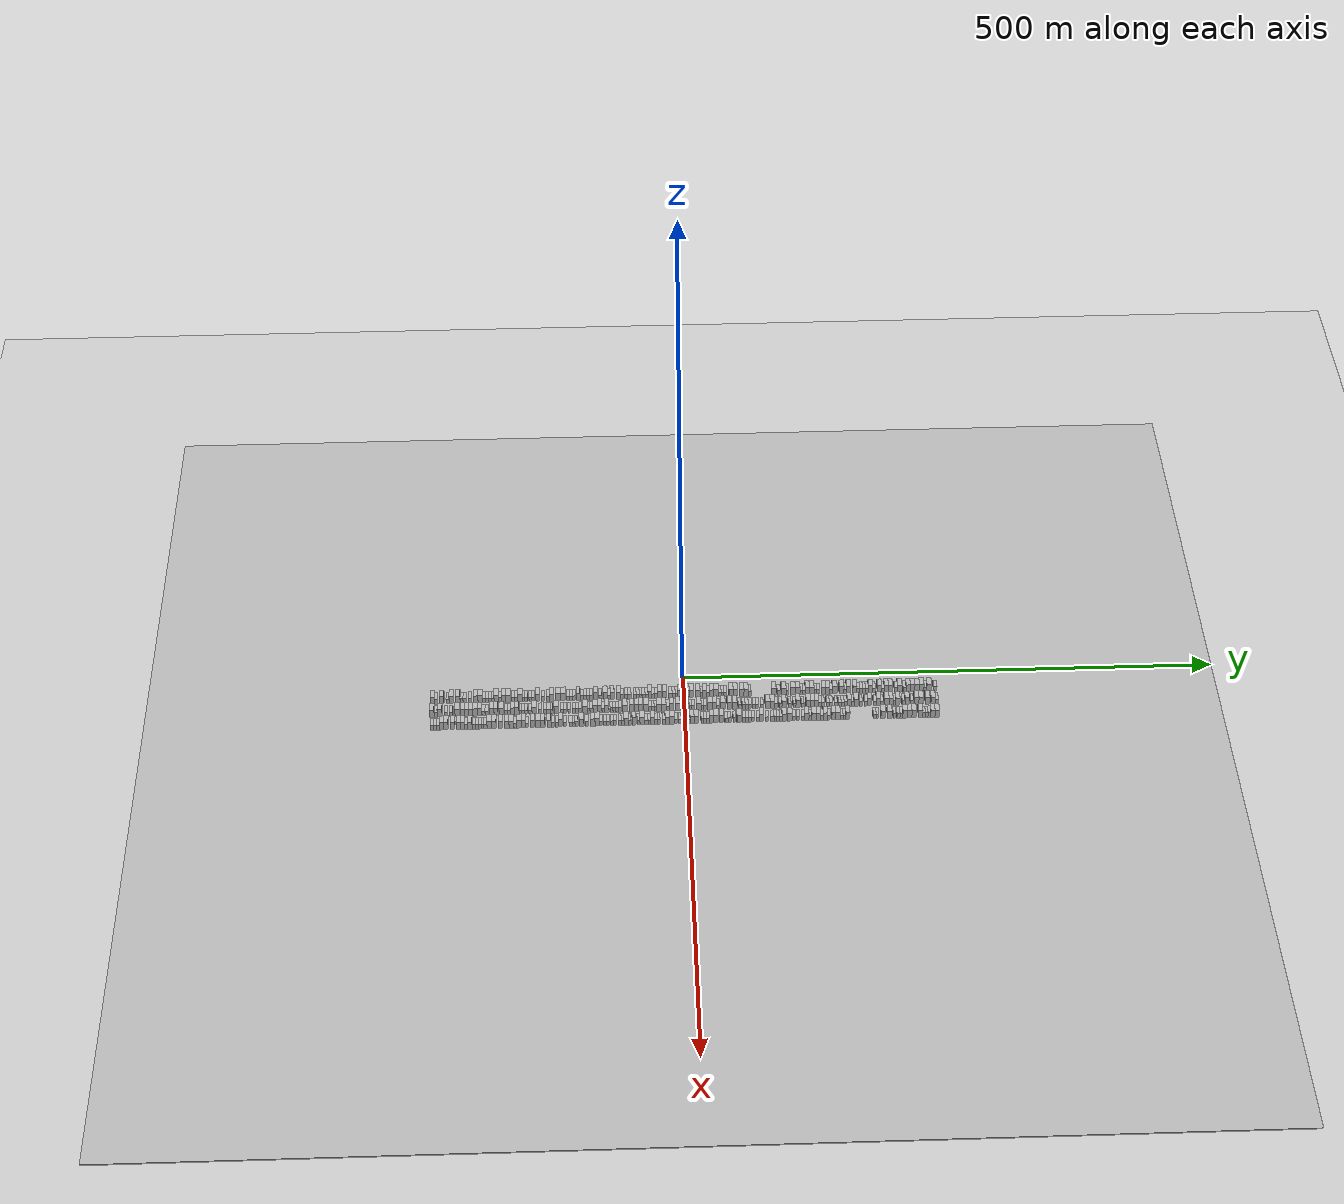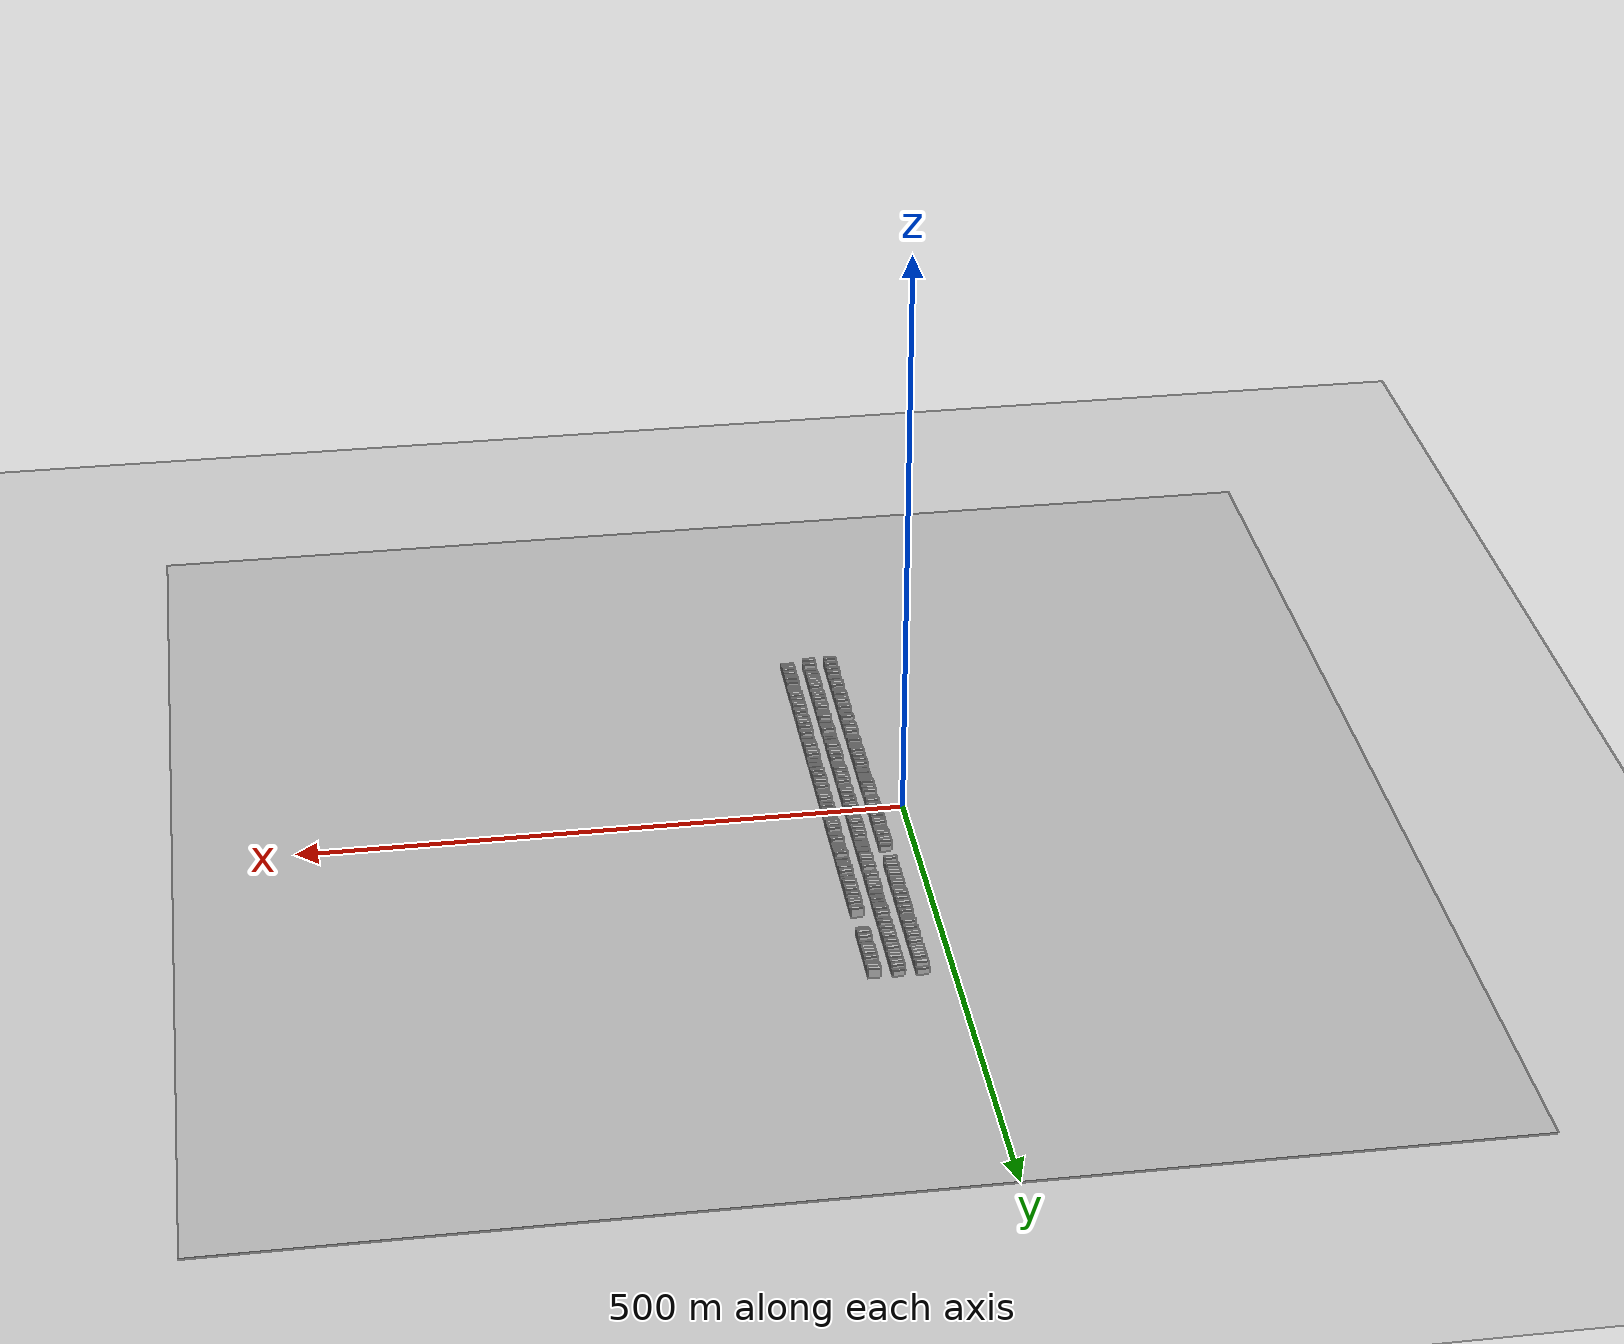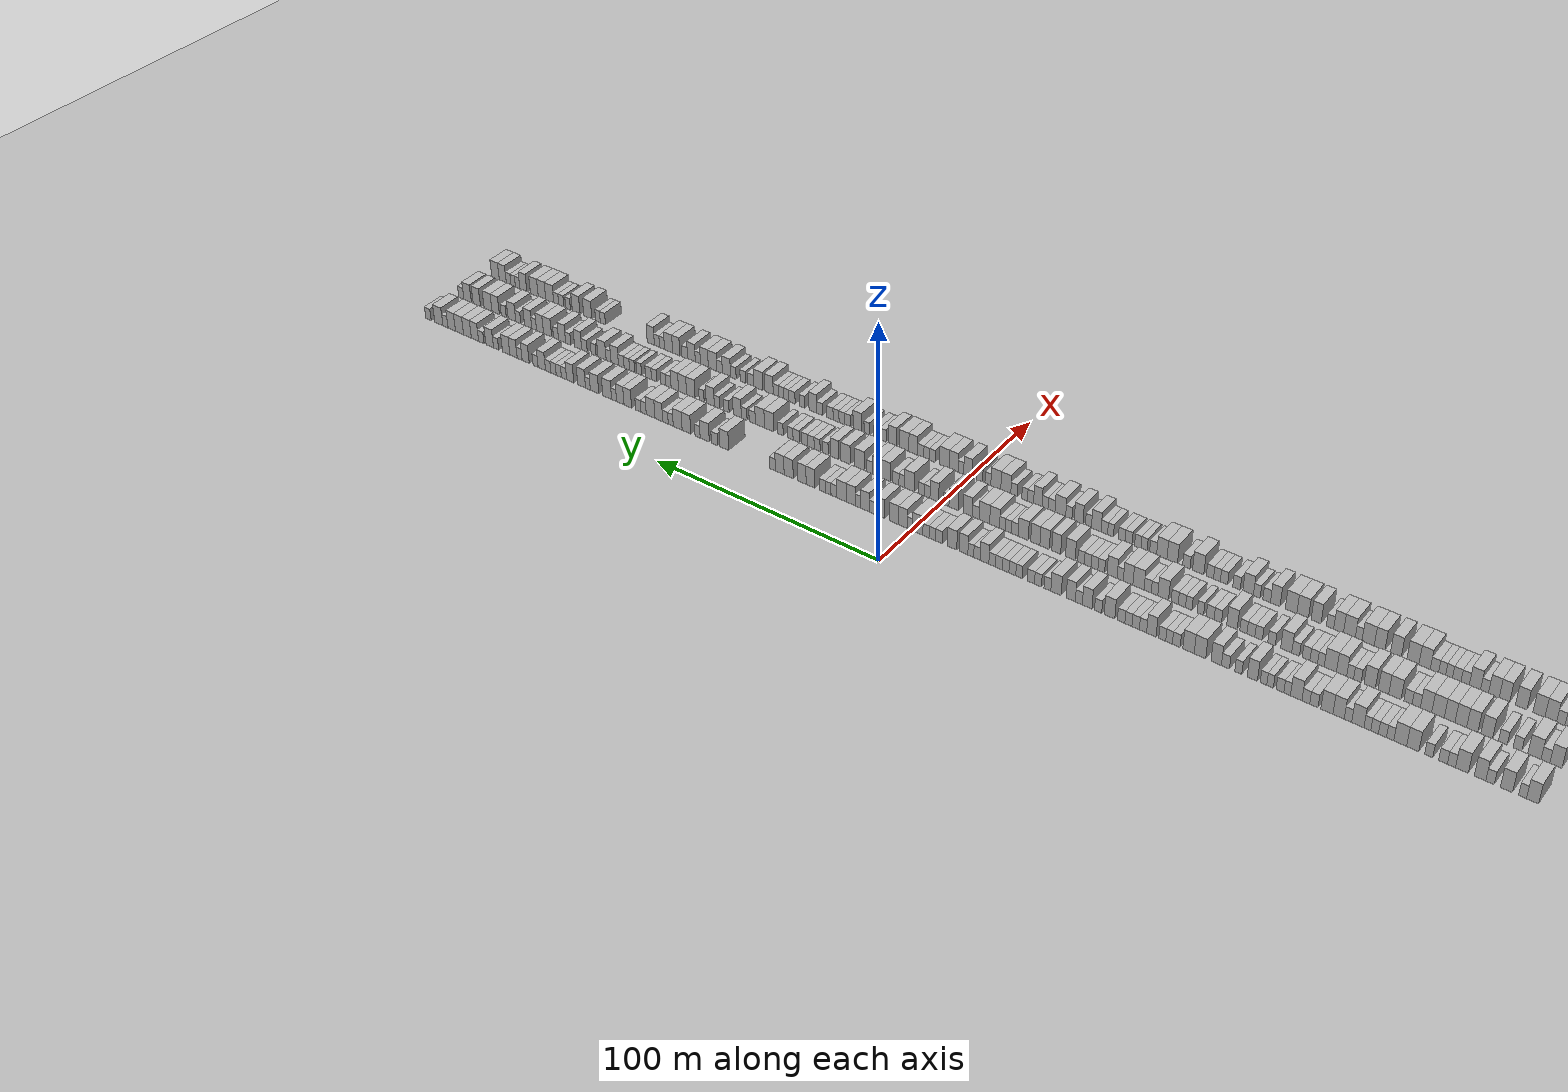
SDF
<?xml version="1.0" encoding="utf-8"?>

<sdf version="1.6">

   <world name="default">

      <gui fullscreen="0">

         <camera name="user_camera">

            <pose>-15 0 4.57585 0 0 0</pose>

            <view_controller>orbit</view_controller>

         </camera>

      </gui>

      <scene>

         <sky>

           <clouds>

             <speed>12</speed>

           </clouds>

         </sky>

         <ambient>0.4 0.4 0.4 1</ambient>

         <background>0.7 0.7 0.7 1</background>

         <shadows>1</shadows>

      </scene>

      <gravity>0 0 -9.8066</gravity>

      <magnetic_field>6e-06 2.3e-05 -4.2e-05</magnetic_field>

      <physics default="0" name="default_physics" type="ode">

         <ode>

            <solver>

               <type>quick</type>

               <iters>10</iters>

               <sor>1.0</sor>

               <use_dynamic_moi_rescaling>0</use_dynamic_moi_rescaling>

            </solver>

            <constraints>

               <cfm>0</cfm>

               <erp>0.2</erp>

               <contact_max_correcting_vel>100</contact_max_correcting_vel>

               <contact_surface_layer>0.001</contact_surface_layer>

            </constraints>

         </ode>

         <max_step_size>0.004</max_step_size>

         <real_time_factor>1</real_time_factor>

         <real_time_update_rate>250</real_time_update_rate>

      </physics>

      <light name="sun" type="directional">

         <cast_shadows>1</cast_shadows>

         <pose>0 0 10 0 0 0</pose>

         <diffuse>0.8 0.8 0.8 1</diffuse>

         <specular>0.2 0.2 0.2 1</specular>

         <attenuation>

            <range>1000</range>

            <constant>0.9</constant>

            <linear>0.01</linear>

            <quadratic>0.001</quadratic>

         </attenuation>

         <direction>-0.5 0.1 -0.9</direction>

      </light>

      <include>

         <name>ground_plane_1</name>

         <uri>model://HANNAS_ground_plane</uri>

         <pose>0 0 0  0 0 0</pose>

      </include>

      <include>

         <name>ground_plane_2</name>

         <uri>model://HANNAS_ground_plane</uri>

         <pose>100 0 0  0 0 0</pose>

      </include>

      <model name="building_1">

         <static>1</static>

         <pose frame="">25.0000 -234.0155 0 0.000000 0.000000 0.000000</pose>

         <link name="link">

            <pose frame="">0 0 4.50 0 0 0</pose>

            <collision name="collision">

               <geometry>

                  <box>

                     <size>10.0000 3.9690 9.0000</size>

                  </box>

               </geometry>

               <max_contacts>10</max_contacts>

               <surface>

                  <contact>

                     <ode/>

                  </contact>

                  <bounce/>

                  <friction>

                     <torsional>

                        <ode/>

                     </torsional>

                     <ode/>

                  </friction>

               </surface>

            </collision>

            <visual name="visual">

               <cast_shadows>0</cast_shadows>

               <geometry>

                  <box>

                     <size>10.0000 3.9690 9.0000</size>

                  </box>

               </geometry>

               <material>

                  <script>

                     <uri>model://HANNAS_wall/materials/scripts</uri>

                     <uri>model://HANNAS_wall/materials/textures</uri>

                     <name>vrc/HANNAS_wall</name>

                  </script>

               </material>

            </visual>

            <self_collide>0</self_collide>

            <enable_wind>0</enable_wind>

            <kinematic>0</kinematic>

         </link>

      </model>

      <model name="building_2">

         <static>1</static>

         <pose frame="">25.0000 -230.7172 0 0.000000 0.000000 0.000000</pose>

         <link name="link">

            <pose frame="">0 0 3.00 0 0 0</pose>

            <collision name="collision">

               <geometry>

                  <box>

                     <size>10.0000 2.6275 6.0000</size>

                  </box>

               </geometry>

               <max_contacts>10</max_contacts>

               <surface>

                  <contact>

                     <ode/>

                  </contact>

                  <bounce/>

                  <friction>

                     <torsional>

                        <ode/>

                     </torsional>

                     <ode/>

                  </friction>

               </surface>

            </collision>

            <visual name="visual">

               <cast_shadows>0</cast_shadows>

               <geometry>

                  <box>

                     <size>10.0000 2.6275 6.0000</size>

                  </box>

               </geometry>

               <material>

                  <script>

                     <uri>model://HANNAS_wall/materials/scripts</uri>

                     <uri>model://HANNAS_wall/materials/textures</uri>

                     <name>vrc/HANNAS_wall</name>

                  </script>

               </material>

            </visual>

            <self_collide>0</self_collide>

            <enable_wind>0</enable_wind>

            <kinematic>0</kinematic>

         </link>

      </model>

      <model name="building_3">

         <static>1</static>

         <pose frame="">25.0000 -225.3931 0 0.000000 0.000000 0.000000</pose>

         <link name="link">

            <pose frame="">0 0 4.50 0 0 0</pose>

            <collision name="collision">

               <geometry>

                  <box>

                     <size>10.0000 4.0208 9.0000</size>

                  </box>

               </geometry>

               <max_contacts>10</max_contacts>

               <surface>

                  <contact>

                     <ode/>

                  </contact>

                  <bounce/>

                  <friction>

                     <torsional>

                        <ode/>

                     </torsional>

                     <ode/>

                  </friction>

               </surface>

            </collision>

            <visual name="visual">

               <cast_shadows>0</cast_shadows>

               <geometry>

                  <box>

                     <size>10.0000 4.0208 9.0000</size>

                  </box>

               </geometry>

               <material>

                  <script>

                     <uri>model://HANNAS_wall/materials/scripts</uri>

                     <uri>model://HANNAS_wall/materials/textures</uri>

                     <name>vrc/HANNAS_wall</name>

                  </script>

               </material>

            </visual>

            <self_collide>0</self_collide>

            <enable_wind>0</enable_wind>

            <kinematic>0</kinematic>

         </link>

      </model>

      <model name="building_4">

         <static>1</static>

         <pose frame="">25.0000 -219.9608 0 0.000000 0.000000 0.000000</pose>

         <link name="link">

            <pose frame="">0 0 3.00 0 0 0</pose>

            <collision name="collision">

               <geometry>

                  <box>

                     <size>10.0000 2.8438 6.0000</size>

                  </box>

               </geometry>

               <max_contacts>10</max_contacts>

               <surface>

                  <contact>

                     <ode/>

                  </contact>

                  <bounce/>

                  <friction>

                     <torsional>

                        <ode/>

                     </torsional>

                     <ode/>

                  </friction>

               </surface>

            </collision>

            <visual name="visual">

               <cast_shadows>0</cast_shadows>

               <geometry>

                  <box>

                     <size>10.0000 2.8438 6.0000</size>

                  </box>

               </geometry>

               <material>

                  <script>

                     <uri>model://HANNAS_wall/materials/scripts</uri>

                     <uri>model://HANNAS_wall/materials/textures</uri>

                     <name>vrc/HANNAS_wall</name>

                  </script>

               </material>

            </visual>

            <self_collide>0</self_collide>

            <enable_wind>0</enable_wind>

            <kinematic>0</kinematic>

         </link>

      </model>

      <model name="building_5">

         <static>1</static>

         <pose frame="">25.0000 -216.6065 0 0.000000 0.000000 0.000000</pose>

         <link name="link">

            <pose frame="">0 0 4.50 0 0 0</pose>

            <collision name="collision">

               <geometry>

                  <box>

                     <size>10.0000 3.8647 9.0000</size>

                  </box>

               </geometry>

               <max_contacts>10</max_contacts>

               <surface>

                  <contact>

                     <ode/>

                  </contact>

                  <bounce/>

                  <friction>

                     <torsional>

                        <ode/>

                     </torsional>

                     <ode/>

                  </friction>

               </surface>

            </collision>

            <visual name="visual">

               <cast_shadows>0</cast_shadows>

               <geometry>

                  <box>

                     <size>10.0000 3.8647 9.0000</size>

                  </box>

               </geometry>

               <material>

                  <script>

                     <uri>model://HANNAS_wall/materials/scripts</uri>

                     <uri>model://HANNAS_wall/materials/textures</uri>

                     <name>vrc/HANNAS_wall</name>

                  </script>

               </material>

            </visual>

            <self_collide>0</self_collide>

            <enable_wind>0</enable_wind>

            <kinematic>0</kinematic>

         </link>

      </model>

      <model name="building_6">

         <static>1</static>

         <pose frame="">25.0000 -210.5149 0 0.000000 0.000000 0.000000</pose>

         <link name="link">

            <pose frame="">0 0 4.50 0 0 0</pose>

            <collision name="collision">

               <geometry>

                  <box>

                     <size>10.0000 4.3187 9.0000</size>

                  </box>

               </geometry>

               <max_contacts>10</max_contacts>

               <surface>

                  <contact>

                     <ode/>

                  </contact>

                  <bounce/>

                  <friction>

                     <torsional>

                        <ode/>

                     </torsional>

                     <ode/>

                  </friction>

               </surface>

            </collision>

            <visual name="visual">

               <cast_shadows>0</cast_shadows>

               <geometry>

                  <box>

                     <size>10.0000 4.3187 9.0000</size>

                  </box>

               </geometry>

               <material>

                  <script>

                     <uri>model://HANNAS_wall/materials/scripts</uri>

                     <uri>model://HANNAS_wall/materials/textures</uri>

                     <name>vrc/HANNAS_wall</name>

                  </script>

               </material>

            </visual>

            <self_collide>0</self_collide>

            <enable_wind>0</enable_wind>

            <kinematic>0</kinematic>

         </link>

      </model>

      <model name="building_7">

         <static>1</static>

         <pose frame="">25.0000 -206.9781 0 0.000000 0.000000 0.000000</pose>

         <link name="link">

            <pose frame="">0 0 3.00 0 0 0</pose>

            <collision name="collision">

               <geometry>

                  <box>

                     <size>10.0000 2.7549 6.0000</size>

                  </box>

               </geometry>

               <max_contacts>10</max_contacts>

               <surface>

                  <contact>

                     <ode/>

                  </contact>

                  <bounce/>

                  <friction>

                     <torsional>

                        <ode/>

                     </torsional>

                     <ode/>

                  </friction>

               </surface>

            </collision>

            <visual name="visual">

               <cast_shadows>0</cast_shadows>

               <geometry>

                  <box>

                     <size>10.0000 2.7549 6.0000</size>

                  </box>

               </geometry>

               <material>

                  <script>

                     <uri>model://HANNAS_wall/materials/scripts</uri>

                     <uri>model://HANNAS_wall/materials/textures</uri>

                     <name>vrc/HANNAS_wall</name>

                  </script>

               </material>

            </visual>

            <self_collide>0</self_collide>

            <enable_wind>0</enable_wind>

            <kinematic>0</kinematic>

         </link>

      </model>

      <model name="building_8">

         <static>1</static>

         <pose frame="">25.0000 -204.1139 0 0.000000 0.000000 0.000000</pose>

         <link name="link">

            <pose frame="">0 0 3.00 0 0 0</pose>

            <collision name="collision">

               <geometry>

                  <box>

                     <size>10.0000 2.9734 6.0000</size>

                  </box>

               </geometry>

               <max_contacts>10</max_contacts>

               <surface>

                  <contact>

                     <ode/>

                  </contact>

                  <bounce/>

                  <friction>

                     <torsional>

                        <ode/>

                     </torsional>

                     <ode/>

                  </friction>

               </surface>

            </collision>

            <visual name="visual">

               <cast_shadows>0</cast_shadows>

               <geometry>

                  <box>

                     <size>10.0000 2.9734 6.0000</size>

                  </box>

               </geometry>

               <material>

                  <script>

                     <uri>model://HANNAS_wall/materials/scripts</uri>

                     <uri>model://HANNAS_wall/materials/textures</uri>

                     <name>vrc/HANNAS_wall</name>

                  </script>

               </material>

            </visual>

            <self_collide>0</self_collide>

            <enable_wind>0</enable_wind>

            <kinematic>0</kinematic>

         </link>

      </model>

      <model name="building_9">

         <static>1</static>

         <pose frame="">25.0000 -199.2379 0 0.000000 0.000000 0.000000</pose>

         <link name="link">

            <pose frame="">0 0 3.00 0 0 0</pose>

            <collision name="collision">

               <geometry>

                  <box>

                     <size>10.0000 2.7785 6.0000</size>

                  </box>

               </geometry>

               <max_contacts>10</max_contacts>

               <surface>

                  <contact>

                     <ode/>

                  </contact>

                  <bounce/>

                  <friction>

                     <torsional>

                        <ode/>

                     </torsional>

                     <ode/>

                  </friction>

               </surface>

            </collision>

            <visual name="visual">

               <cast_shadows>0</cast_shadows>

               <geometry>

                  <box>

                     <size>10.0000 2.7785 6.0000</size>

                  </box>

               </geometry>

               <material>

                  <script>

                     <uri>model://HANNAS_wall/materials/scripts</uri>

                     <uri>model://HANNAS_wall/materials/textures</uri>

                     <name>vrc/HANNAS_wall</name>

                  </script>

               </material>

            </visual>

            <self_collide>0</self_collide>

            <enable_wind>0</enable_wind>

            <kinematic>0</kinematic>

         </link>

      </model>

      <model name="building_10">

         <static>1</static>

         <pose frame="">25.0000 -193.7581 0 0.000000 0.000000 0.000000</pose>

         <link name="link">

            <pose frame="">0 0 4.50 0 0 0</pose>

            <collision name="collision">

               <geometry>

                  <box>

                     <size>10.0000 4.1811 9.0000</size>

                  </box>

               </geometry>

               <max_contacts>10</max_contacts>

               <surface>

                  <contact>

                     <ode/>

                  </contact>

                  <bounce/>

                  <friction>

                     <torsional>

                        <ode/>

                     </torsional>

                     <ode/>

                  </friction>

               </surface>

            </collision>

            <visual name="visual">

               <cast_shadows>0</cast_shadows>

               <geometry>

                  <box>

                     <size>10.0000 4.1811 9.0000</size>

                  </box>

               </geometry>

               <material>

                  <script>

                     <uri>model://HANNAS_wall/materials/scripts</uri>

                     <uri>model://HANNAS_wall/materials/textures</uri>

                     <name>vrc/HANNAS_wall</name>

                  </script>

               </material>

            </visual>

            <self_collide>0</self_collide>

            <enable_wind>0</enable_wind>

            <kinematic>0</kinematic>

         </link>

      </model>

      <model name="building_11">

         <static>1</static>

         <pose frame="">25.0000 -189.4293 0 0.000000 0.000000 0.000000</pose>

         <link name="link">

            <pose frame="">0 0 4.50 0 0 0</pose>

            <collision name="collision">

               <geometry>

                  <box>

                     <size>10.0000 4.4765 9.0000</size>

                  </box>

               </geometry>

               <max_contacts>10</max_contacts>

               <surface>

                  <contact>

                     <ode/>

                  </contact>

                  <bounce/>

                  <friction>

                     <torsional>

                        <ode/>

                     </torsional>

                     <ode/>

                  </friction>

               </surface>

            </collision>

            <visual name="visual">

               <cast_shadows>0</cast_shadows>

               <geometry>

                  <box>

                     <size>10.0000 4.4765 9.0000</size>

                  </box>

               </geometry>

               <material>

                  <script>

                     <uri>model://HANNAS_wall/materials/scripts</uri>

                     <uri>model://HANNAS_wall/materials/textures</uri>

                     <name>vrc/HANNAS_wall</name>

                  </script>

               </material>

            </visual>

            <self_collide>0</self_collide>

            <enable_wind>0</enable_wind>

            <kinematic>0</kinematic>

         </link>

      </model>

      <model name="building_12">

         <static>1</static>

         <pose frame="">25.0000 -185.9155 0 0.000000 0.000000 0.000000</pose>

         <link name="link">

            <pose frame="">0 0 3.00 0 0 0</pose>

            <collision name="collision">

               <geometry>

                  <box>

                     <size>10.0000 2.5512 6.0000</size>

                  </box>

               </geometry>

               <max_contacts>10</max_contacts>

               <surface>

                  <contact>

                     <ode/>

                  </contact>

                  <bounce/>

                  <friction>

                     <torsional>

                        <ode/>

                     </torsional>

                     <ode/>

                  </friction>

               </surface>

            </collision>

            <visual name="visual">

               <cast_shadows>0</cast_shadows>

               <geometry>

                  <box>

                     <size>10.0000 2.5512 6.0000</size>

                  </box>

               </geometry>

               <material>

                  <script>

                     <uri>model://HANNAS_wall/materials/scripts</uri>

                     <uri>model://HANNAS_wall/materials/textures</uri>

                     <name>vrc/HANNAS_wall</name>

                  </script>

               </material>

            </visual>

            <self_collide>0</self_collide>

            <enable_wind>0</enable_wind>

            <kinematic>0</kinematic>

         </link>

      </model>

      <model name="building_13">

         <static>1</static>

         <pose frame="">25.0000 -183.2340 0 0.000000 0.000000 0.000000</pose>

         <link name="link">

            <pose frame="">0 0 3.00 0 0 0</pose>

            <collision name="collision">

               <geometry>

                  <box>

                     <size>10.0000 2.8118 6.0000</size>

                  </box>

               </geometry>

               <max_contacts>10</max_contacts>

               <surface>

                  <contact>

                     <ode/>

                  </contact>

                  <bounce/>

                  <friction>

                     <torsional>

                        <ode/>

                     </torsional>

                     <ode/>

                  </friction>

               </surface>

            </collision>

            <visual name="visual">

               <cast_shadows>0</cast_shadows>

               <geometry>

                  <box>

                     <size>10.0000 2.8118 6.0000</size>

                  </box>

               </geometry>

               <material>

                  <script>

                     <uri>model://HANNAS_wall/materials/scripts</uri>

                     <uri>model://HANNAS_wall/materials/textures</uri>

                     <name>vrc/HANNAS_wall</name>

                  </script>

               </material>

            </visual>

            <self_collide>0</self_collide>

            <enable_wind>0</enable_wind>

            <kinematic>0</kinematic>

         </link>

      </model>

      <model name="building_14">

         <static>1</static>

         <pose frame="">25.0000 -180.4891 0 0.000000 0.000000 0.000000</pose>

         <link name="link">

            <pose frame="">0 0 3.00 0 0 0</pose>

            <collision name="collision">

               <geometry>

                  <box>

                     <size>10.0000 2.6780 6.0000</size>

                  </box>

               </geometry>

               <max_contacts>10</max_contacts>

               <surface>

                  <contact>

                     <ode/>

                  </contact>

                  <bounce/>

                  <friction>

                     <torsional>

                        <ode/>

                     </torsional>

                     <ode/>

                  </friction>

               </surface>

            </collision>

            <visual name="visual">

               <cast_shadows>0</cast_shadows>

               <geometry>

                  <box>

                     <size>10.0000 2.6780 6.0000</size>

                  </box>

               </geometry>

               <material>

                  <script>

                     <uri>model://HANNAS_wall/materials/scripts</uri>

                     <uri>model://HANNAS_wall/materials/textures</uri>

                     <name>vrc/HANNAS_wall</name>

                  </script>

               </material>

            </visual>

            <self_collide>0</self_collide>

            <enable_wind>0</enable_wind>

            <kinematic>0</kinematic>

         </link>

      </model>

      <model name="building_15">

         <static>1</static>

         <pose frame="">25.0000 -177.9431 0 0.000000 0.000000 0.000000</pose>

         <link name="link">

            <pose frame="">0 0 3.00 0 0 0</pose>

            <collision name="collision">

               <geometry>

                  <box>

                     <size>10.0000 2.4139 6.0000</size>

                  </box>

               </geometry>

               <max_contacts>10</max_contacts>

               <surface>

                  <contact>

                     <ode/>

                  </contact>

                  <bounce/>

                  <friction>

                     <torsional>

                        <ode/>

                     </torsional>

                     <ode/>

                  </friction>

               </surface>

            </collision>

            <visual name="visual">

               <cast_shadows>0</cast_shadows>

               <geometry>

                  <box>

                     <size>10.0000 2.4139 6.0000</size>

                  </box>

               </geometry>

               <material>

                  <script>

                     <uri>model://HANNAS_wall/materials/scripts</uri>

                     <uri>model://HANNAS_wall/materials/textures</uri>

                     <name>vrc/HANNAS_wall</name>

                  </script>

               </material>

            </visual>

            <self_collide>0</self_collide>

            <enable_wind>0</enable_wind>

            <kinematic>0</kinematic>

         </link>

      </model>

      <model name="building_16">

         <static>1</static>

         <pose frame="">25.0000 -174.5769 0 0.000000 0.000000 0.000000</pose>

         <link name="link">

            <pose frame="">0 0 4.50 0 0 0</pose>

            <collision name="collision">

               <geometry>

                  <box>

                     <size>10.0000 4.3185 9.0000</size>

                  </box>

               </geometry>

               <max_contacts>10</max_contacts>

               <surface>

                  <contact>

                     <ode/>

                  </contact>

                  <bounce/>

                  <friction>

                     <torsional>

                        <ode/>

                     </torsional>

                     <ode/>

                  </friction>

               </surface>

            </collision>

            <visual name="visual">

               <cast_shadows>0</cast_shadows>

               <geometry>

                  <box>

                     <size>10.0000 4.3185 9.0000</size>

                  </box>

               </geometry>

               <material>

                  <script>

                     <uri>model://HANNAS_wall/materials/scripts</uri>

                     <uri>model://HANNAS_wall/materials/textures</uri>

                     <name>vrc/HANNAS_wall</name>

                  </script>

               </material>

            </visual>

            <self_collide>0</self_collide>

            <enable_wind>0</enable_wind>

            <kinematic>0</kinematic>

         </link>

      </model>

      <model name="building_17">

         <static>1</static>

         <pose frame="">25.0000 -171.0987 0 0.000000 0.000000 0.000000</pose>

         <link name="link">

            <pose frame="">0 0 3.00 0 0 0</pose>

            <collision name="collision">

               <geometry>

                  <box>

                     <size>10.0000 2.6379 6.0000</size>

                  </box>

               </geometry>

               <max_contacts>10</max_contacts>

               <surface>

                  <contact>

                     <ode/>

                  </contact>

                  <bounce/>

                  <friction>

                     <torsional>

                        <ode/>

                     </torsional>

                     <ode/>

                  </friction>

               </surface>

            </collision>

            <visual name="visual">

               <cast_shadows>0</cast_shadows>

               <geometry>

                  <box>

                     <size>10.0000 2.6379 6.0000</size>

                  </box>

               </geometry>

               <material>

                  <script>

                     <uri>model://HANNAS_wall/materials/scripts</uri>

                     <uri>model://HANNAS_wall/materials/textures</uri>

                     <name>vrc/HANNAS_wall</name>

                  </script>

               </material>

            </visual>

            <self_collide>0</self_collide>

            <enable_wind>0</enable_wind>

            <kinematic>0</kinematic>

         </link>

      </model>

      <model name="building_18">

         <static>1</static>

         <pose frame="">25.0000 -167.7574 0 0.000000 0.000000 0.000000</pose>

         <link name="link">

            <pose frame="">0 0 4.50 0 0 0</pose>

            <collision name="collision">

               <geometry>

                  <box>

                     <size>10.0000 4.0447 9.0000</size>

                  </box>

               </geometry>

               <max_contacts>10</max_contacts>

               <surface>

                  <contact>

                     <ode/>

                  </contact>

                  <bounce/>

                  <friction>

                     <torsional>

                        <ode/>

                     </torsional>

                     <ode/>

                  </friction>

               </surface>

            </collision>

            <visual name="visual">

               <cast_shadows>0</cast_shadows>

               <geometry>

                  <box>

                     <size>10.0000 4.0447 9.0000</size>

                  </box>

               </geometry>

               <material>

                  <script>

                     <uri>model://HANNAS_wall/materials/scripts</uri>

                     <uri>model://HANNAS_wall/materials/textures</uri>

                     <name>vrc/HANNAS_wall</name>

                  </script>

               </material>

            </visual>

            <self_collide>0</self_collide>

            <enable_wind>0</enable_wind>

            <kinematic>0</kinematic>

         </link>

      </model>

      <model name="building_19">

         <static>1</static>

         <pose frame="">25.0000 -163.5746 0 0.000000 0.000000 0.000000</pose>

         <link name="link">

            <pose frame="">0 0 4.50 0 0 0</pose>

            <collision name="collision">

               <geometry>

                  <box>

                     <size>10.0000 4.3209 9.0000</size>

                  </box>

               </geometry>

               <max_contacts>10</max_contacts>

               <surface>

                  <contact>

                     <ode/>

                  </contact>

                  <bounce/>

                  <friction>

                     <torsional>

                        <ode/>

                     </torsional>

                     <ode/>

                  </friction>

               </surface>

            </collision>

            <visual name="visual">

               <cast_shadows>0</cast_shadows>

               <geometry>

                  <box>

                     <size>10.0000 4.3209 9.0000</size>

                  </box>

               </geometry>

               <material>

                  <script>

                     <uri>model://HANNAS_wall/materials/scripts</uri>

                     <uri>model://HANNAS_wall/materials/textures</uri>

                     <name>vrc/HANNAS_wall</name>

                  </script>

               </material>

            </visual>

            <self_collide>0</self_collide>

            <enable_wind>0</enable_wind>

            <kinematic>0</kinematic>

         </link>

      </model>

      <model name="building_20">

         <static>1</static>

         <pose frame="">25.0000 -158.9256 0 0.000000 0.000000 0.000000</pose>

         <link name="link">

            <pose frame="">0 0 3.00 0 0 0</pose>

            <collision name="collision">

               <geometry>

                  <box>

                     <size>10.0000 2.9771 6.0000</size>

                  </box>

               </geometry>

               <max_contacts>10</max_contacts>

               <surface>

                  <contact>

                     <ode/>

                  </contact>

                  <bounce/>

                  <friction>

                     <torsional>

                        <ode/>

                     </torsional>

                     <ode/>

                  </friction>

               </surface>

            </collision>

            <visual name="visual">

               <cast_shadows>0</cast_shadows>

               <geometry>

                  <box>

                     <size>10.0000 2.9771 6.0000</size>

                  </box>

               </geometry>

               <material>

                  <script>

                     <uri>model://HANNAS_wall/materials/scripts</uri>

                     <uri>model://HANNAS_wall/materials/textures</uri>

                     <name>vrc/HANNAS_wall</name>

                  </script>

               </material>

            </visual>

            <self_collide>0</self_collide>

            <enable_wind>0</enable_wind>

            <kinematic>0</kinematic>

         </link>

      </model>

      <model name="building_21">

         <static>1</static>

         <pose frame="">25.0000 -156.0341 0 0.000000 0.000000 0.000000</pose>

         <link name="link">

            <pose frame="">0 0 3.00 0 0 0</pose>

            <collision name="collision">

               <geometry>

                  <box>

                     <size>10.0000 2.8059 6.0000</size>

                  </box>

               </geometry>

               <max_contacts>10</max_contacts>

               <surface>

                  <contact>

                     <ode/>

                  </contact>

                  <bounce/>

                  <friction>

                     <torsional>

                        <ode/>

                     </torsional>

                     <ode/>

                  </friction>

               </surface>

            </collision>

            <visual name="visual">

               <cast_shadows>0</cast_shadows>

               <geometry>

                  <box>

                     <size>10.0000 2.8059 6.0000</size>

                  </box>

               </geometry>

               <material>

                  <script>

                     <uri>model://HANNAS_wall/materials/scripts</uri>

                     <uri>model://HANNAS_wall/materials/textures</uri>

                     <name>vrc/HANNAS_wall</name>

                  </script>

               </material>

            </visual>

            <self_collide>0</self_collide>

            <enable_wind>0</enable_wind>

            <kinematic>0</kinematic>

         </link>

      </model>

      <model name="building_22">

         <static>1</static>

         <pose frame="">25.0000 -152.5541 0 0.000000 0.000000 0.000000</pose>

         <link name="link">

            <pose frame="">0 0 4.50 0 0 0</pose>

            <collision name="collision">

               <geometry>

                  <box>

                     <size>10.0000 4.1543 9.0000</size>

                  </box>

               </geometry>

               <max_contacts>10</max_contacts>

               <surface>

                  <contact>

                     <ode/>

                  </contact>

                  <bounce/>

                  <friction>

                     <torsional>

                        <ode/>

                     </torsional>

                     <ode/>

                  </friction>

               </surface>

            </collision>

            <visual name="visual">

               <cast_shadows>0</cast_shadows>

               <geometry>

                  <box>

                     <size>10.0000 4.1543 9.0000</size>

                  </box>

               </geometry>

               <material>

                  <script>

                     <uri>model://HANNAS_wall/materials/scripts</uri>

                     <uri>model://HANNAS_wall/materials/textures</uri>

                     <name>vrc/HANNAS_wall</name>

                  </script>

               </material>

            </visual>

            <self_collide>0</self_collide>

            <enable_wind>0</enable_wind>

            <kinematic>0</kinematic>

         </link>

      </model>

      <model name="building_23">

         <static>1</static>

         <pose frame="">25.0000 -149.2589 0 0.000000 0.000000 0.000000</pose>

         <link name="link">

            <pose frame="">0 0 3.00 0 0 0</pose>

            <collision name="collision">

               <geometry>

                  <box>

                     <size>10.0000 2.4361 6.0000</size>

                  </box>

               </geometry>

               <max_contacts>10</max_contacts>

               <surface>

                  <contact>

                     <ode/>

                  </contact>

                  <bounce/>

                  <friction>

                     <torsional>

                        <ode/>

                     </torsional>

                     <ode/>

                  </friction>

               </surface>

            </collision>

            <visual name="visual">

               <cast_shadows>0</cast_shadows>

               <geometry>

                  <box>

                     <size>10.0000 2.4361 6.0000</size>

                  </box>

               </geometry>

               <material>

                  <script>

                     <uri>model://HANNAS_wall/materials/scripts</uri>

                     <uri>model://HANNAS_wall/materials/textures</uri>

                     <name>vrc/HANNAS_wall</name>

                  </script>

               </material>

            </visual>

            <self_collide>0</self_collide>

            <enable_wind>0</enable_wind>

            <kinematic>0</kinematic>

         </link>

      </model>

      <model name="building_24">

         <static>1</static>

         <pose frame="">25.0000 -146.6283 0 0.000000 0.000000 0.000000</pose>

         <link name="link">

            <pose frame="">0 0 3.00 0 0 0</pose>

            <collision name="collision">

               <geometry>

                  <box>

                     <size>10.0000 2.8251 6.0000</size>

                  </box>

               </geometry>

               <max_contacts>10</max_contacts>

               <surface>

                  <contact>

                     <ode/>

                  </contact>

                  <bounce/>

                  <friction>

                     <torsional>

                        <ode/>

                     </torsional>

                     <ode/>

                  </friction>

               </surface>

            </collision>

            <visual name="visual">

               <cast_shadows>0</cast_shadows>

               <geometry>

                  <box>

                     <size>10.0000 2.8251 6.0000</size>

                  </box>

               </geometry>

               <material>

                  <script>

                     <uri>model://HANNAS_wall/materials/scripts</uri>

                     <uri>model://HANNAS_wall/materials/textures</uri>

                     <name>vrc/HANNAS_wall</name>

                  </script>

               </material>

            </visual>

            <self_collide>0</self_collide>

            <enable_wind>0</enable_wind>

            <kinematic>0</kinematic>

         </link>

      </model>

      <model name="building_25">

         <static>1</static>

         <pose frame="">25.0000 -143.0133 0 0.000000 0.000000 0.000000</pose>

         <link name="link">

            <pose frame="">0 0 3.00 0 0 0</pose>

            <collision name="collision">

               <geometry>

                  <box>

                     <size>10.0000 2.4048 6.0000</size>

                  </box>

               </geometry>

               <max_contacts>10</max_contacts>

               <surface>

                  <contact>

                     <ode/>

                  </contact>

                  <bounce/>

                  <friction>

                     <torsional>

                        <ode/>

                     </torsional>

                     <ode/>

                  </friction>

               </surface>

            </collision>

            <visual name="visual">

               <cast_shadows>0</cast_shadows>

               <geometry>

                  <box>

                     <size>10.0000 2.4048 6.0000</size>

                  </box>

               </geometry>

               <material>

                  <script>

                     <uri>model://HANNAS_wall/materials/scripts</uri>

                     <uri>model://HANNAS_wall/materials/textures</uri>

                     <name>vrc/HANNAS_wall</name>

                  </script>

               </material>

            </visual>

            <self_collide>0</self_collide>

            <enable_wind>0</enable_wind>

            <kinematic>0</kinematic>

         </link>

      </model>

      <model name="building_26">

         <static>1</static>

         <pose frame="">25.0000 -140.5978 0 0.000000 0.000000 0.000000</pose>

         <link name="link">

            <pose frame="">0 0 3.00 0 0 0</pose>

            <collision name="collision">

               <geometry>

                  <box>

                     <size>10.0000 2.4263 6.0000</size>

                  </box>

               </geometry>

               <max_contacts>10</max_contacts>

               <surface>

                  <contact>

                     <ode/>

                  </contact>

                  <bounce/>

                  <friction>

                     <torsional>

                        <ode/>

                     </torsional>

                     <ode/>

                  </friction>

               </surface>

            </collision>

            <visual name="visual">

               <cast_shadows>0</cast_shadows>

               <geometry>

                  <box>

                     <size>10.0000 2.4263 6.0000</size>

                  </box>

               </geometry>

               <material>

                  <script>

                     <uri>model://HANNAS_wall/materials/scripts</uri>

                     <uri>model://HANNAS_wall/materials/textures</uri>

                     <name>vrc/HANNAS_wall</name>

                  </script>

               </material>

            </visual>

            <self_collide>0</self_collide>

            <enable_wind>0</enable_wind>

            <kinematic>0</kinematic>

         </link>

      </model>

      <model name="building_27">

         <static>1</static>

         <pose frame="">25.0000 -136.4963 0 0.000000 0.000000 0.000000</pose>

         <link name="link">

            <pose frame="">0 0 4.50 0 0 0</pose>

            <collision name="collision">

               <geometry>

                  <box>

                     <size>10.0000 3.7765 9.0000</size>

                  </box>

               </geometry>

               <max_contacts>10</max_contacts>

               <surface>

                  <contact>

                     <ode/>

                  </contact>

                  <bounce/>

                  <friction>

                     <torsional>

                        <ode/>

                     </torsional>

                     <ode/>

                  </friction>

               </surface>

            </collision>

            <visual name="visual">

               <cast_shadows>0</cast_shadows>

               <geometry>

                  <box>

                     <size>10.0000 3.7765 9.0000</size>

                  </box>

               </geometry>

               <material>

                  <script>

                     <uri>model://HANNAS_wall/materials/scripts</uri>

                     <uri>model://HANNAS_wall/materials/textures</uri>

                     <name>vrc/HANNAS_wall</name>

                  </script>

               </material>

            </visual>

            <self_collide>0</self_collide>

            <enable_wind>0</enable_wind>

            <kinematic>0</kinematic>

         </link>

      </model>

      <model name="building_28">

         <static>1</static>

         <pose frame="">25.0000 -131.3021 0 0.000000 0.000000 0.000000</pose>

         <link name="link">

            <pose frame="">0 0 3.00 0 0 0</pose>

            <collision name="collision">

               <geometry>

                  <box>

                     <size>10.0000 2.6121 6.0000</size>

                  </box>

               </geometry>

               <max_contacts>10</max_contacts>

               <surface>

                  <contact>

                     <ode/>

                  </contact>

                  <bounce/>

                  <friction>

                     <torsional>

                        <ode/>

                     </torsional>

                     <ode/>

                  </friction>

               </surface>

            </collision>

            <visual name="visual">

               <cast_shadows>0</cast_shadows>

               <geometry>

                  <box>

                     <size>10.0000 2.6121 6.0000</size>

                  </box>

               </geometry>

               <material>

                  <script>

                     <uri>model://HANNAS_wall/materials/scripts</uri>

                     <uri>model://HANNAS_wall/materials/textures</uri>

                     <name>vrc/HANNAS_wall</name>

                  </script>

               </material>

            </visual>

            <self_collide>0</self_collide>

            <enable_wind>0</enable_wind>

            <kinematic>0</kinematic>

         </link>

      </model>

      <model name="building_29">

         <static>1</static>

         <pose frame="">25.0000 -126.5000 0 0.000000 0.000000 0.000000</pose>

         <link name="link">

            <pose frame="">0 0 3.00 0 0 0</pose>

            <collision name="collision">

               <geometry>

                  <box>

                     <size>10.0000 2.9920 6.0000</size>

                  </box>

               </geometry>

               <max_contacts>10</max_contacts>

               <surface>

                  <contact>

                     <ode/>

                  </contact>

                  <bounce/>

                  <friction>

                     <torsional>

                        <ode/>

                     </torsional>

                     <ode/>

                  </friction>

               </surface>

            </collision>

            <visual name="visual">

               <cast_shadows>0</cast_shadows>

               <geometry>

                  <box>

                     <size>10.0000 2.9920 6.0000</size>

                  </box>

               </geometry>

               <material>

                  <script>

                     <uri>model://HANNAS_wall/materials/scripts</uri>

                     <uri>model://HANNAS_wall/materials/textures</uri>

                     <name>vrc/HANNAS_wall</name>

                  </script>

               </material>

            </visual>

            <self_collide>0</self_collide>

            <enable_wind>0</enable_wind>

            <kinematic>0</kinematic>

         </link>

      </model>

      <model name="building_30">

         <static>1</static>

         <pose frame="">25.0000 -123.0553 0 0.000000 0.000000 0.000000</pose>

         <link name="link">

            <pose frame="">0 0 4.50 0 0 0</pose>

            <collision name="collision">

               <geometry>

                  <box>

                     <size>10.0000 3.8975 9.0000</size>

                  </box>

               </geometry>

               <max_contacts>10</max_contacts>

               <surface>

                  <contact>

                     <ode/>

                  </contact>

                  <bounce/>

                  <friction>

                     <torsional>

                        <ode/>

                     </torsional>

                     <ode/>

                  </friction>

               </surface>

            </collision>

            <visual name="visual">

               <cast_shadows>0</cast_shadows>

               <geometry>

                  <box>

                     <size>10.0000 3.8975 9.0000</size>

                  </box>

               </geometry>

               <material>

                  <script>

                     <uri>model://HANNAS_wall/materials/scripts</uri>

                     <uri>model://HANNAS_wall/materials/textures</uri>

                     <name>vrc/HANNAS_wall</name>

                  </script>

               </material>

            </visual>

            <self_collide>0</self_collide>

            <enable_wind>0</enable_wind>

            <kinematic>0</kinematic>

         </link>

      </model>

      <model name="building_31">

         <static>1</static>

         <pose frame="">25.0000 -116.9213 0 0.000000 0.000000 0.000000</pose>

         <link name="link">

            <pose frame="">0 0 4.50 0 0 0</pose>

            <collision name="collision">

               <geometry>

                  <box>

                     <size>10.0000 4.3705 9.0000</size>

                  </box>

               </geometry>

               <max_contacts>10</max_contacts>

               <surface>

                  <contact>

                     <ode/>

                  </contact>

                  <bounce/>

                  <friction>

                     <torsional>

                        <ode/>

                     </torsional>

                     <ode/>

                  </friction>

               </surface>

            </collision>

            <visual name="visual">

               <cast_shadows>0</cast_shadows>

               <geometry>

                  <box>

                     <size>10.0000 4.3705 9.0000</size>

                  </box>

               </geometry>

               <material>

                  <script>

                     <uri>model://HANNAS_wall/materials/scripts</uri>

                     <uri>model://HANNAS_wall/materials/textures</uri>

                     <name>vrc/HANNAS_wall</name>

                  </script>

               </material>

            </visual>

            <self_collide>0</self_collide>

            <enable_wind>0</enable_wind>

            <kinematic>0</kinematic>

         </link>

      </model>

      <model name="building_32">

         <static>1</static>

         <pose frame="">25.0000 -112.5708 0 0.000000 0.000000 0.000000</pose>

         <link name="link">

            <pose frame="">0 0 4.50 0 0 0</pose>

            <collision name="collision">

               <geometry>

                  <box>

                     <size>10.0000 4.3304 9.0000</size>

                  </box>

               </geometry>

               <max_contacts>10</max_contacts>

               <surface>

                  <contact>

                     <ode/>

                  </contact>

                  <bounce/>

                  <friction>

                     <torsional>

                        <ode/>

                     </torsional>

                     <ode/>

                  </friction>

               </surface>

            </collision>

            <visual name="visual">

               <cast_shadows>0</cast_shadows>

               <geometry>

                  <box>

                     <size>10.0000 4.3304 9.0000</size>

                  </box>

               </geometry>

               <material>

                  <script>

                     <uri>model://HANNAS_wall/materials/scripts</uri>

                     <uri>model://HANNAS_wall/materials/textures</uri>

                     <name>vrc/HANNAS_wall</name>

                  </script>

               </material>

            </visual>

            <self_collide>0</self_collide>

            <enable_wind>0</enable_wind>

            <kinematic>0</kinematic>

         </link>

      </model>

      <model name="building_33">

         <static>1</static>

         <pose frame="">25.0000 -107.9095 0 0.000000 0.000000 0.000000</pose>

         <link name="link">

            <pose frame="">0 0 3.00 0 0 0</pose>

            <collision name="collision">

               <geometry>

                  <box>

                     <size>10.0000 2.9922 6.0000</size>

                  </box>

               </geometry>

               <max_contacts>10</max_contacts>

               <surface>

                  <contact>

                     <ode/>

                  </contact>

                  <bounce/>

                  <friction>

                     <torsional>

                        <ode/>

                     </torsional>

                     <ode/>

                  </friction>

               </surface>

            </collision>

            <visual name="visual">

               <cast_shadows>0</cast_shadows>

               <geometry>

                  <box>

                     <size>10.0000 2.9922 6.0000</size>

                  </box>

               </geometry>

               <material>

                  <script>

                     <uri>model://HANNAS_wall/materials/scripts</uri>

                     <uri>model://HANNAS_wall/materials/textures</uri>

                     <name>vrc/HANNAS_wall</name>

                  </script>

               </material>

            </visual>

            <self_collide>0</self_collide>

            <enable_wind>0</enable_wind>

            <kinematic>0</kinematic>

         </link>

      </model>

      <model name="building_34">

         <static>1</static>

         <pose frame="">25.0000 -105.1496 0 0.000000 0.000000 0.000000</pose>

         <link name="link">

            <pose frame="">0 0 3.00 0 0 0</pose>

            <collision name="collision">

               <geometry>

                  <box>

                     <size>10.0000 2.5277 6.0000</size>

                  </box>

               </geometry>

               <max_contacts>10</max_contacts>

               <surface>

                  <contact>

                     <ode/>

                  </contact>

                  <bounce/>

                  <friction>

                     <torsional>

                        <ode/>

                     </torsional>

                     <ode/>

                  </friction>

               </surface>

            </collision>

            <visual name="visual">

               <cast_shadows>0</cast_shadows>

               <geometry>

                  <box>

                     <size>10.0000 2.5277 6.0000</size>

                  </box>

               </geometry>

               <material>

                  <script>

                     <uri>model://HANNAS_wall/materials/scripts</uri>

                     <uri>model://HANNAS_wall/materials/textures</uri>

                     <name>vrc/HANNAS_wall</name>

                  </script>

               </material>

            </visual>

            <self_collide>0</self_collide>

            <enable_wind>0</enable_wind>

            <kinematic>0</kinematic>

         </link>

      </model>

      <model name="building_35">

         <static>1</static>

         <pose frame="">25.0000 -102.5309 0 0.000000 0.000000 0.000000</pose>

         <link name="link">

            <pose frame="">0 0 3.00 0 0 0</pose>

            <collision name="collision">

               <geometry>

                  <box>

                     <size>10.0000 2.7097 6.0000</size>

                  </box>

               </geometry>

               <max_contacts>10</max_contacts>

               <surface>

                  <contact>

                     <ode/>

                  </contact>

                  <bounce/>

                  <friction>

                     <torsional>

                        <ode/>

                     </torsional>

                     <ode/>

                  </friction>

               </surface>

            </collision>

            <visual name="visual">

               <cast_shadows>0</cast_shadows>

               <geometry>

                  <box>

                     <size>10.0000 2.7097 6.0000</size>

                  </box>

               </geometry>

               <material>

                  <script>

                     <uri>model://HANNAS_wall/materials/scripts</uri>

                     <uri>model://HANNAS_wall/materials/textures</uri>

                     <name>vrc/HANNAS_wall</name>

                  </script>

               </material>

            </visual>

            <self_collide>0</self_collide>

            <enable_wind>0</enable_wind>

            <kinematic>0</kinematic>

         </link>

      </model>

      <model name="building_36">

         <static>1</static>

         <pose frame="">25.0000 -98.3424 0 0.000000 0.000000 0.000000</pose>

         <link name="link">

            <pose frame="">0 0 4.50 0 0 0</pose>

            <collision name="collision">

               <geometry>

                  <box>

                     <size>10.0000 3.6674 9.0000</size>

                  </box>

               </geometry>

               <max_contacts>10</max_contacts>

               <surface>

                  <contact>

                     <ode/>

                  </contact>

                  <bounce/>

                  <friction>

                     <torsional>

                        <ode/>

                     </torsional>

                     <ode/>

                  </friction>

               </surface>

            </collision>

            <visual name="visual">

               <cast_shadows>0</cast_shadows>

               <geometry>

                  <box>

                     <size>10.0000 3.6674 9.0000</size>

                  </box>

               </geometry>

               <material>

                  <script>

                     <uri>model://HANNAS_wall/materials/scripts</uri>

                     <uri>model://HANNAS_wall/materials/textures</uri>

                     <name>vrc/HANNAS_wall</name>

                  </script>

               </material>

            </visual>

            <self_collide>0</self_collide>

            <enable_wind>0</enable_wind>

            <kinematic>0</kinematic>

         </link>

      </model>

      <model name="building_37">

         <static>1</static>

         <pose frame="">25.0000 -95.0966 0 0.000000 0.000000 0.000000</pose>

         <link name="link">

            <pose frame="">0 0 3.00 0 0 0</pose>

            <collision name="collision">

               <geometry>

                  <box>

                     <size>10.0000 2.8241 6.0000</size>

                  </box>

               </geometry>

               <max_contacts>10</max_contacts>

               <surface>

                  <contact>

                     <ode/>

                  </contact>

                  <bounce/>

                  <friction>

                     <torsional>

                        <ode/>

                     </torsional>

                     <ode/>

                  </friction>

               </surface>

            </collision>

            <visual name="visual">

               <cast_shadows>0</cast_shadows>

               <geometry>

                  <box>

                     <size>10.0000 2.8241 6.0000</size>

                  </box>

               </geometry>

               <material>

                  <script>

                     <uri>model://HANNAS_wall/materials/scripts</uri>

                     <uri>model://HANNAS_wall/materials/textures</uri>

                     <name>vrc/HANNAS_wall</name>

                  </script>

               </material>

            </visual>

            <self_collide>0</self_collide>

            <enable_wind>0</enable_wind>

            <kinematic>0</kinematic>

         </link>

      </model>

      <model name="building_38">

         <static>1</static>

         <pose frame="">25.0000 -92.2332 0 0.000000 0.000000 0.000000</pose>

         <link name="link">

            <pose frame="">0 0 3.00 0 0 0</pose>

            <collision name="collision">

               <geometry>

                  <box>

                     <size>10.0000 2.9028 6.0000</size>

                  </box>

               </geometry>

               <max_contacts>10</max_contacts>

               <surface>

                  <contact>

                     <ode/>

                  </contact>

                  <bounce/>

                  <friction>

                     <torsional>

                        <ode/>

                     </torsional>

                     <ode/>

                  </friction>

               </surface>

            </collision>

            <visual name="visual">

               <cast_shadows>0</cast_shadows>

               <geometry>

                  <box>

                     <size>10.0000 2.9028 6.0000</size>

                  </box>

               </geometry>

               <material>

                  <script>

                     <uri>model://HANNAS_wall/materials/scripts</uri>

                     <uri>model://HANNAS_wall/materials/textures</uri>

                     <name>vrc/HANNAS_wall</name>

                  </script>

               </material>

            </visual>

            <self_collide>0</self_collide>

            <enable_wind>0</enable_wind>

            <kinematic>0</kinematic>

         </link>

      </model>

      <model name="building_39">

         <static>1</static>

         <pose frame="">25.0000 -89.4062 0 0.000000 0.000000 0.000000</pose>

         <link name="link">

            <pose frame="">0 0 3.00 0 0 0</pose>

            <collision name="collision">

               <geometry>

                  <box>

                     <size>10.0000 2.7512 6.0000</size>

                  </box>

               </geometry>

               <max_contacts>10</max_contacts>

               <surface>

                  <contact>

                     <ode/>

                  </contact>

                  <bounce/>

                  <friction>

                     <torsional>

                        <ode/>

                     </torsional>

                     <ode/>

                  </friction>

               </surface>

            </collision>

            <visual name="visual">

               <cast_shadows>0</cast_shadows>

               <geometry>

                  <box>

                     <size>10.0000 2.7512 6.0000</size>

                  </box>

               </geometry>

               <material>

                  <script>

                     <uri>model://HANNAS_wall/materials/scripts</uri>

                     <uri>model://HANNAS_wall/materials/textures</uri>

                     <name>vrc/HANNAS_wall</name>

                  </script>

               </material>

            </visual>

            <self_collide>0</self_collide>

            <enable_wind>0</enable_wind>

            <kinematic>0</kinematic>

         </link>

      </model>

      <model name="building_40">

         <static>1</static>

         <pose frame="">25.0000 -86.5562 0 0.000000 0.000000 0.000000</pose>

         <link name="link">

            <pose frame="">0 0 3.00 0 0 0</pose>

            <collision name="collision">

               <geometry>

                  <box>

                     <size>10.0000 2.9488 6.0000</size>

                  </box>

               </geometry>

               <max_contacts>10</max_contacts>

               <surface>

                  <contact>

                     <ode/>

                  </contact>

                  <bounce/>

                  <friction>

                     <torsional>

                        <ode/>

                     </torsional>

                     <ode/>

                  </friction>

               </surface>

            </collision>

            <visual name="visual">

               <cast_shadows>0</cast_shadows>

               <geometry>

                  <box>

                     <size>10.0000 2.9488 6.0000</size>

                  </box>

               </geometry>

               <material>

                  <script>

                     <uri>model://HANNAS_wall/materials/scripts</uri>

                     <uri>model://HANNAS_wall/materials/textures</uri>

                     <name>vrc/HANNAS_wall</name>

                  </script>

               </material>

            </visual>

            <self_collide>0</self_collide>

            <enable_wind>0</enable_wind>

            <kinematic>0</kinematic>

         </link>

      </model>

      <model name="building_41">

         <static>1</static>

         <pose frame="">25.0000 -82.0064 0 0.000000 0.000000 0.000000</pose>

         <link name="link">

            <pose frame="">0 0 4.50 0 0 0</pose>

            <collision name="collision">

               <geometry>

                  <box>

                     <size>10.0000 4.1509 9.0000</size>

                  </box>

               </geometry>

               <max_contacts>10</max_contacts>

               <surface>

                  <contact>

                     <ode/>

                  </contact>

                  <bounce/>

                  <friction>

                     <torsional>

                        <ode/>

                     </torsional>

                     <ode/>

                  </friction>

               </surface>

            </collision>

            <visual name="visual">

               <cast_shadows>0</cast_shadows>

               <geometry>

                  <box>

                     <size>10.0000 4.1509 9.0000</size>

                  </box>

               </geometry>

               <material>

                  <script>

                     <uri>model://HANNAS_wall/materials/scripts</uri>

                     <uri>model://HANNAS_wall/materials/textures</uri>

                     <name>vrc/HANNAS_wall</name>

                  </script>

               </material>

            </visual>

            <self_collide>0</self_collide>

            <enable_wind>0</enable_wind>

            <kinematic>0</kinematic>

         </link>

      </model>

      <model name="building_42">

         <static>1</static>

         <pose frame="">25.0000 -77.5061 0 0.000000 0.000000 0.000000</pose>

         <link name="link">

            <pose frame="">0 0 3.00 0 0 0</pose>

            <collision name="collision">

               <geometry>

                  <box>

                     <size>10.0000 2.8496 6.0000</size>

                  </box>

               </geometry>

               <max_contacts>10</max_contacts>

               <surface>

                  <contact>

                     <ode/>

                  </contact>

                  <bounce/>

                  <friction>

                     <torsional>

                        <ode/>

                     </torsional>

                     <ode/>

                  </friction>

               </surface>

            </collision>

            <visual name="visual">

               <cast_shadows>0</cast_shadows>

               <geometry>

                  <box>

                     <size>10.0000 2.8496 6.0000</size>

                  </box>

               </geometry>

               <material>

                  <script>

                     <uri>model://HANNAS_wall/materials/scripts</uri>

                     <uri>model://HANNAS_wall/materials/textures</uri>

                     <name>vrc/HANNAS_wall</name>

                  </script>

               </material>

            </visual>

            <self_collide>0</self_collide>

            <enable_wind>0</enable_wind>

            <kinematic>0</kinematic>

         </link>

      </model>

      <model name="building_43">

         <static>1</static>

         <pose frame="">25.0000 -73.1588 0 0.000000 0.000000 0.000000</pose>

         <link name="link">

            <pose frame="">0 0 4.50 0 0 0</pose>

            <collision name="collision">

               <geometry>

                  <box>

                     <size>10.0000 3.8450 9.0000</size>

                  </box>

               </geometry>

               <max_contacts>10</max_contacts>

               <surface>

                  <contact>

                     <ode/>

                  </contact>

                  <bounce/>

                  <friction>

                     <torsional>

                        <ode/>

                     </torsional>

                     <ode/>

                  </friction>

               </surface>

            </collision>

            <visual name="visual">

               <cast_shadows>0</cast_shadows>

               <geometry>

                  <box>

                     <size>10.0000 3.8450 9.0000</size>

                  </box>

               </geometry>

               <material>

                  <script>

                     <uri>model://HANNAS_wall/materials/scripts</uri>

                     <uri>model://HANNAS_wall/materials/textures</uri>

                     <name>vrc/HANNAS_wall</name>

                  </script>

               </material>

            </visual>

            <self_collide>0</self_collide>

            <enable_wind>0</enable_wind>

            <kinematic>0</kinematic>

         </link>

      </model>

      <model name="building_44">

         <static>1</static>

         <pose frame="">25.0000 -69.8470 0 0.000000 0.000000 0.000000</pose>

         <link name="link">

            <pose frame="">0 0 3.00 0 0 0</pose>

            <collision name="collision">

               <geometry>

                  <box>

                     <size>10.0000 2.7786 6.0000</size>

                  </box>

               </geometry>

               <max_contacts>10</max_contacts>

               <surface>

                  <contact>

                     <ode/>

                  </contact>

                  <bounce/>

                  <friction>

                     <torsional>

                        <ode/>

                     </torsional>

                     <ode/>

                  </friction>

               </surface>

            </collision>

            <visual name="visual">

               <cast_shadows>0</cast_shadows>

               <geometry>

                  <box>

                     <size>10.0000 2.7786 6.0000</size>

                  </box>

               </geometry>

               <material>

                  <script>

                     <uri>model://HANNAS_wall/materials/scripts</uri>

                     <uri>model://HANNAS_wall/materials/textures</uri>

                     <name>vrc/HANNAS_wall</name>

                  </script>

               </material>

            </visual>

            <self_collide>0</self_collide>

            <enable_wind>0</enable_wind>

            <kinematic>0</kinematic>

         </link>

      </model>

      <model name="building_45">

         <static>1</static>

         <pose frame="">25.0000 -66.6069 0 0.000000 0.000000 0.000000</pose>

         <link name="link">

            <pose frame="">0 0 4.50 0 0 0</pose>

            <collision name="collision">

               <geometry>

                  <box>

                     <size>10.0000 3.7016 9.0000</size>

                  </box>

               </geometry>

               <max_contacts>10</max_contacts>

               <surface>

                  <contact>

                     <ode/>

                  </contact>

                  <bounce/>

                  <friction>

                     <torsional>

                        <ode/>

                     </torsional>

                     <ode/>

                  </friction>

               </surface>

            </collision>

            <visual name="visual">

               <cast_shadows>0</cast_shadows>

               <geometry>

                  <box>

                     <size>10.0000 3.7016 9.0000</size>

                  </box>

               </geometry>

               <material>

                  <script>

                     <uri>model://HANNAS_wall/materials/scripts</uri>

                     <uri>model://HANNAS_wall/materials/textures</uri>

                     <name>vrc/HANNAS_wall</name>

                  </script>

               </material>

            </visual>

            <self_collide>0</self_collide>

            <enable_wind>0</enable_wind>

            <kinematic>0</kinematic>

         </link>

      </model>

      <model name="building_46">

         <static>1</static>

         <pose frame="">25.0000 -60.6728 0 0.000000 0.000000 0.000000</pose>

         <link name="link">

            <pose frame="">0 0 4.50 0 0 0</pose>

            <collision name="collision">

               <geometry>

                  <box>

                     <size>10.0000 4.1666 9.0000</size>

                  </box>

               </geometry>

               <max_contacts>10</max_contacts>

               <surface>

                  <contact>

                     <ode/>

                  </contact>

                  <bounce/>

                  <friction>

                     <torsional>

                        <ode/>

                     </torsional>

                     <ode/>

                  </friction>

               </surface>

            </collision>

            <visual name="visual">

               <cast_shadows>0</cast_shadows>

               <geometry>

                  <box>

                     <size>10.0000 4.1666 9.0000</size>

                  </box>

               </geometry>

               <material>

                  <script>

                     <uri>model://HANNAS_wall/materials/scripts</uri>

                     <uri>model://HANNAS_wall/materials/textures</uri>

                     <name>vrc/HANNAS_wall</name>

                  </script>

               </material>

            </visual>

            <self_collide>0</self_collide>

            <enable_wind>0</enable_wind>

            <kinematic>0</kinematic>

         </link>

      </model>

      <model name="building_47">

         <static>1</static>

         <pose frame="">25.0000 -57.1904 0 0.000000 0.000000 0.000000</pose>

         <link name="link">

            <pose frame="">0 0 3.00 0 0 0</pose>

            <collision name="collision">

               <geometry>

                  <box>

                     <size>10.0000 2.7982 6.0000</size>

                  </box>

               </geometry>

               <max_contacts>10</max_contacts>

               <surface>

                  <contact>

                     <ode/>

                  </contact>

                  <bounce/>

                  <friction>

                     <torsional>

                        <ode/>

                     </torsional>

                     <ode/>

                  </friction>

               </surface>

            </collision>

            <visual name="visual">

               <cast_shadows>0</cast_shadows>

               <geometry>

                  <box>

                     <size>10.0000 2.7982 6.0000</size>

                  </box>

               </geometry>

               <material>

                  <script>

                     <uri>model://HANNAS_wall/materials/scripts</uri>

                     <uri>model://HANNAS_wall/materials/textures</uri>

                     <name>vrc/HANNAS_wall</name>

                  </script>

               </material>

            </visual>

            <self_collide>0</self_collide>

            <enable_wind>0</enable_wind>

            <kinematic>0</kinematic>

         </link>

      </model>

      <model name="building_48">

         <static>1</static>

         <pose frame="">25.0000 -53.3715 0 0.000000 0.000000 0.000000</pose>

         <link name="link">

            <pose frame="">0 0 3.00 0 0 0</pose>

            <collision name="collision">

               <geometry>

                  <box>

                     <size>10.0000 2.8395 6.0000</size>

                  </box>

               </geometry>

               <max_contacts>10</max_contacts>

               <surface>

                  <contact>

                     <ode/>

                  </contact>

                  <bounce/>

                  <friction>

                     <torsional>

                        <ode/>

                     </torsional>

                     <ode/>

                  </friction>

               </surface>

            </collision>

            <visual name="visual">

               <cast_shadows>0</cast_shadows>

               <geometry>

                  <box>

                     <size>10.0000 2.8395 6.0000</size>

                  </box>

               </geometry>

               <material>

                  <script>

                     <uri>model://HANNAS_wall/materials/scripts</uri>

                     <uri>model://HANNAS_wall/materials/textures</uri>

                     <name>vrc/HANNAS_wall</name>

                  </script>

               </material>

            </visual>

            <self_collide>0</self_collide>

            <enable_wind>0</enable_wind>

            <kinematic>0</kinematic>

         </link>

      </model>

      <model name="building_49">

         <static>1</static>

         <pose frame="">25.0000 -50.4573 0 0.000000 0.000000 0.000000</pose>

         <link name="link">

            <pose frame="">0 0 3.00 0 0 0</pose>

            <collision name="collision">

               <geometry>

                  <box>

                     <size>10.0000 2.9889 6.0000</size>

                  </box>

               </geometry>

               <max_contacts>10</max_contacts>

               <surface>

                  <contact>

                     <ode/>

                  </contact>

                  <bounce/>

                  <friction>

                     <torsional>

                        <ode/>

                     </torsional>

                     <ode/>

                  </friction>

               </surface>

            </collision>

            <visual name="visual">

               <cast_shadows>0</cast_shadows>

               <geometry>

                  <box>

                     <size>10.0000 2.9889 6.0000</size>

                  </box>

               </geometry>

               <material>

                  <script>

                     <uri>model://HANNAS_wall/materials/scripts</uri>

                     <uri>model://HANNAS_wall/materials/textures</uri>

                     <name>vrc/HANNAS_wall</name>

                  </script>

               </material>

            </visual>

            <self_collide>0</self_collide>

            <enable_wind>0</enable_wind>

            <kinematic>0</kinematic>

         </link>

      </model>

      <model name="building_50">

         <static>1</static>

         <pose frame="">25.0000 -45.6166 0 0.000000 0.000000 0.000000</pose>

         <link name="link">

            <pose frame="">0 0 3.00 0 0 0</pose>

            <collision name="collision">

               <geometry>

                  <box>

                     <size>10.0000 2.6924 6.0000</size>

                  </box>

               </geometry>

               <max_contacts>10</max_contacts>

               <surface>

                  <contact>

                     <ode/>

                  </contact>

                  <bounce/>

                  <friction>

                     <torsional>

                        <ode/>

                     </torsional>

                     <ode/>

                  </friction>

               </surface>

            </collision>

            <visual name="visual">

               <cast_shadows>0</cast_shadows>

               <geometry>

                  <box>

                     <size>10.0000 2.6924 6.0000</size>

                  </box>

               </geometry>

               <material>

                  <script>

                     <uri>model://HANNAS_wall/materials/scripts</uri>

                     <uri>model://HANNAS_wall/materials/textures</uri>

                     <name>vrc/HANNAS_wall</name>

                  </script>

               </material>

            </visual>

            <self_collide>0</self_collide>

            <enable_wind>0</enable_wind>

            <kinematic>0</kinematic>

         </link>

      </model>

      <model name="building_51">

         <static>1</static>

         <pose frame="">25.0000 -42.8474 0 0.000000 0.000000 0.000000</pose>

         <link name="link">

            <pose frame="">0 0 3.00 0 0 0</pose>

            <collision name="collision">

               <geometry>

                  <box>

                     <size>10.0000 2.8459 6.0000</size>

                  </box>

               </geometry>

               <max_contacts>10</max_contacts>

               <surface>

                  <contact>

                     <ode/>

                  </contact>

                  <bounce/>

                  <friction>

                     <torsional>

                        <ode/>

                     </torsional>

                     <ode/>

                  </friction>

               </surface>

            </collision>

            <visual name="visual">

               <cast_shadows>0</cast_shadows>

               <geometry>

                  <box>

                     <size>10.0000 2.8459 6.0000</size>

                  </box>

               </geometry>

               <material>

                  <script>

                     <uri>model://HANNAS_wall/materials/scripts</uri>

                     <uri>model://HANNAS_wall/materials/textures</uri>

                     <name>vrc/HANNAS_wall</name>

                  </script>

               </material>

            </visual>

            <self_collide>0</self_collide>

            <enable_wind>0</enable_wind>

            <kinematic>0</kinematic>

         </link>

      </model>

      <model name="building_52">

         <static>1</static>

         <pose frame="">25.0000 -40.1089 0 0.000000 0.000000 0.000000</pose>

         <link name="link">

            <pose frame="">0 0 3.00 0 0 0</pose>

            <collision name="collision">

               <geometry>

                  <box>

                     <size>10.0000 2.6312 6.0000</size>

                  </box>

               </geometry>

               <max_contacts>10</max_contacts>

               <surface>

                  <contact>

                     <ode/>

                  </contact>

                  <bounce/>

                  <friction>

                     <torsional>

                        <ode/>

                     </torsional>

                     <ode/>

                  </friction>

               </surface>

            </collision>

            <visual name="visual">

               <cast_shadows>0</cast_shadows>

               <geometry>

                  <box>

                     <size>10.0000 2.6312 6.0000</size>

                  </box>

               </geometry>

               <material>

                  <script>

                     <uri>model://HANNAS_wall/materials/scripts</uri>

                     <uri>model://HANNAS_wall/materials/textures</uri>

                     <name>vrc/HANNAS_wall</name>

                  </script>

               </material>

            </visual>

            <self_collide>0</self_collide>

            <enable_wind>0</enable_wind>

            <kinematic>0</kinematic>

         </link>

      </model>

      <model name="building_53">

         <static>1</static>

         <pose frame="">25.0000 -37.3499 0 0.000000 0.000000 0.000000</pose>

         <link name="link">

            <pose frame="">0 0 3.00 0 0 0</pose>

            <collision name="collision">

               <geometry>

                  <box>

                     <size>10.0000 2.8868 6.0000</size>

                  </box>

               </geometry>

               <max_contacts>10</max_contacts>

               <surface>

                  <contact>

                     <ode/>

                  </contact>

                  <bounce/>

                  <friction>

                     <torsional>

                        <ode/>

                     </torsional>

                     <ode/>

                  </friction>

               </surface>

            </collision>

            <visual name="visual">

               <cast_shadows>0</cast_shadows>

               <geometry>

                  <box>

                     <size>10.0000 2.8868 6.0000</size>

                  </box>

               </geometry>

               <material>

                  <script>

                     <uri>model://HANNAS_wall/materials/scripts</uri>

                     <uri>model://HANNAS_wall/materials/textures</uri>

                     <name>vrc/HANNAS_wall</name>

                  </script>

               </material>

            </visual>

            <self_collide>0</self_collide>

            <enable_wind>0</enable_wind>

            <kinematic>0</kinematic>

         </link>

      </model>

      <model name="building_54">

         <static>1</static>

         <pose frame="">25.0000 -34.5141 0 0.000000 0.000000 0.000000</pose>

         <link name="link">

            <pose frame="">0 0 3.00 0 0 0</pose>

            <collision name="collision">

               <geometry>

                  <box>

                     <size>10.0000 2.7847 6.0000</size>

                  </box>

               </geometry>

               <max_contacts>10</max_contacts>

               <surface>

                  <contact>

                     <ode/>

                  </contact>

                  <bounce/>

                  <friction>

                     <torsional>

                        <ode/>

                     </torsional>

                     <ode/>

                  </friction>

               </surface>

            </collision>

            <visual name="visual">

               <cast_shadows>0</cast_shadows>

               <geometry>

                  <box>

                     <size>10.0000 2.7847 6.0000</size>

                  </box>

               </geometry>

               <material>

                  <script>

                     <uri>model://HANNAS_wall/materials/scripts</uri>

                     <uri>model://HANNAS_wall/materials/textures</uri>

                     <name>vrc/HANNAS_wall</name>

                  </script>

               </material>

            </visual>

            <self_collide>0</self_collide>

            <enable_wind>0</enable_wind>

            <kinematic>0</kinematic>

         </link>

      </model>

      <model name="building_55">

         <static>1</static>

         <pose frame="">25.0000 -31.3079 0 0.000000 0.000000 0.000000</pose>

         <link name="link">

            <pose frame="">0 0 4.50 0 0 0</pose>

            <collision name="collision">

               <geometry>

                  <box>

                     <size>10.0000 3.6278 9.0000</size>

                  </box>

               </geometry>

               <max_contacts>10</max_contacts>

               <surface>

                  <contact>

                     <ode/>

                  </contact>

                  <bounce/>

                  <friction>

                     <torsional>

                        <ode/>

                     </torsional>

                     <ode/>

                  </friction>

               </surface>

            </collision>

            <visual name="visual">

               <cast_shadows>0</cast_shadows>

               <geometry>

                  <box>

                     <size>10.0000 3.6278 9.0000</size>

                  </box>

               </geometry>

               <material>

                  <script>

                     <uri>model://HANNAS_wall/materials/scripts</uri>

                     <uri>model://HANNAS_wall/materials/textures</uri>

                     <name>vrc/HANNAS_wall</name>

                  </script>

               </material>

            </visual>

            <self_collide>0</self_collide>

            <enable_wind>0</enable_wind>

            <kinematic>0</kinematic>

         </link>

      </model>

      <model name="building_56">

         <static>1</static>

         <pose frame="">25.0000 -28.1393 0 0.000000 0.000000 0.000000</pose>

         <link name="link">

            <pose frame="">0 0 3.00 0 0 0</pose>

            <collision name="collision">

               <geometry>

                  <box>

                     <size>10.0000 2.7095 6.0000</size>

                  </box>

               </geometry>

               <max_contacts>10</max_contacts>

               <surface>

                  <contact>

                     <ode/>

                  </contact>

                  <bounce/>

                  <friction>

                     <torsional>

                        <ode/>

                     </torsional>

                     <ode/>

                  </friction>

               </surface>

            </collision>

            <visual name="visual">

               <cast_shadows>0</cast_shadows>

               <geometry>

                  <box>

                     <size>10.0000 2.7095 6.0000</size>

                  </box>

               </geometry>

               <material>

                  <script>

                     <uri>model://HANNAS_wall/materials/scripts</uri>

                     <uri>model://HANNAS_wall/materials/textures</uri>

                     <name>vrc/HANNAS_wall</name>

                  </script>

               </material>

            </visual>

            <self_collide>0</self_collide>

            <enable_wind>0</enable_wind>

            <kinematic>0</kinematic>

         </link>

      </model>

      <model name="building_57">

         <static>1</static>

         <pose frame="">25.0000 -25.5519 0 0.000000 0.000000 0.000000</pose>

         <link name="link">

            <pose frame="">0 0 3.00 0 0 0</pose>

            <collision name="collision">

               <geometry>

                  <box>

                     <size>10.0000 2.4653 6.0000</size>

                  </box>

               </geometry>

               <max_contacts>10</max_contacts>

               <surface>

                  <contact>

                     <ode/>

                  </contact>

                  <bounce/>

                  <friction>

                     <torsional>

                        <ode/>

                     </torsional>

                     <ode/>

                  </friction>

               </surface>

            </collision>

            <visual name="visual">

               <cast_shadows>0</cast_shadows>

               <geometry>

                  <box>

                     <size>10.0000 2.4653 6.0000</size>

                  </box>

               </geometry>

               <material>

                  <script>

                     <uri>model://HANNAS_wall/materials/scripts</uri>

                     <uri>model://HANNAS_wall/materials/textures</uri>

                     <name>vrc/HANNAS_wall</name>

                  </script>

               </material>

            </visual>

            <self_collide>0</self_collide>

            <enable_wind>0</enable_wind>

            <kinematic>0</kinematic>

         </link>

      </model>

      <model name="building_58">

         <static>1</static>

         <pose frame="">25.0000 -22.4851 0 0.000000 0.000000 0.000000</pose>

         <link name="link">

            <pose frame="">0 0 4.50 0 0 0</pose>

            <collision name="collision">

               <geometry>

                  <box>

                     <size>10.0000 3.6683 9.0000</size>

                  </box>

               </geometry>

               <max_contacts>10</max_contacts>

               <surface>

                  <contact>

                     <ode/>

                  </contact>

                  <bounce/>

                  <friction>

                     <torsional>

                        <ode/>

                     </torsional>

                     <ode/>

                  </friction>

               </surface>

            </collision>

            <visual name="visual">

               <cast_shadows>0</cast_shadows>

               <geometry>

                  <box>

                     <size>10.0000 3.6683 9.0000</size>

                  </box>

               </geometry>

               <material>

                  <script>

                     <uri>model://HANNAS_wall/materials/scripts</uri>

                     <uri>model://HANNAS_wall/materials/textures</uri>

                     <name>vrc/HANNAS_wall</name>

                  </script>

               </material>

            </visual>

            <self_collide>0</self_collide>

            <enable_wind>0</enable_wind>

            <kinematic>0</kinematic>

         </link>

      </model>

      <model name="building_59">

         <static>1</static>

         <pose frame="">25.0000 -17.6290 0 0.000000 0.000000 0.000000</pose>

         <link name="link">

            <pose frame="">0 0 4.50 0 0 0</pose>

            <collision name="collision">

               <geometry>

                  <box>

                     <size>10.0000 4.0440 9.0000</size>

                  </box>

               </geometry>

               <max_contacts>10</max_contacts>

               <surface>

                  <contact>

                     <ode/>

                  </contact>

                  <bounce/>

                  <friction>

                     <torsional>

                        <ode/>

                     </torsional>

                     <ode/>

                  </friction>

               </surface>

            </collision>

            <visual name="visual">

               <cast_shadows>0</cast_shadows>

               <geometry>

                  <box>

                     <size>10.0000 4.0440 9.0000</size>

                  </box>

               </geometry>

               <material>

                  <script>

                     <uri>model://HANNAS_wall/materials/scripts</uri>

                     <uri>model://HANNAS_wall/materials/textures</uri>

                     <name>vrc/HANNAS_wall</name>

                  </script>

               </material>

            </visual>

            <self_collide>0</self_collide>

            <enable_wind>0</enable_wind>

            <kinematic>0</kinematic>

         </link>

      </model>

      <model name="building_60">

         <static>1</static>

         <pose frame="">25.0000 -12.1209 0 0.000000 0.000000 0.000000</pose>

         <link name="link">

            <pose frame="">0 0 3.00 0 0 0</pose>

            <collision name="collision">

               <geometry>

                  <box>

                     <size>10.0000 2.9723 6.0000</size>

                  </box>

               </geometry>

               <max_contacts>10</max_contacts>

               <surface>

                  <contact>

                     <ode/>

                  </contact>

                  <bounce/>

                  <friction>

                     <torsional>

                        <ode/>

                     </torsional>

                     <ode/>

                  </friction>

               </surface>

            </collision>

            <visual name="visual">

               <cast_shadows>0</cast_shadows>

               <geometry>

                  <box>

                     <size>10.0000 2.9723 6.0000</size>

                  </box>

               </geometry>

               <material>

                  <script>

                     <uri>model://HANNAS_wall/materials/scripts</uri>

                     <uri>model://HANNAS_wall/materials/textures</uri>

                     <name>vrc/HANNAS_wall</name>

                  </script>

               </material>

            </visual>

            <self_collide>0</self_collide>

            <enable_wind>0</enable_wind>

            <kinematic>0</kinematic>

         </link>

      </model>

      <model name="building_61">

         <static>1</static>

         <pose frame="">25.0000 -9.2199 0 0.000000 0.000000 0.000000</pose>

         <link name="link">

            <pose frame="">0 0 3.00 0 0 0</pose>

            <collision name="collision">

               <geometry>

                  <box>

                     <size>10.0000 2.8297 6.0000</size>

                  </box>

               </geometry>

               <max_contacts>10</max_contacts>

               <surface>

                  <contact>

                     <ode/>

                  </contact>

                  <bounce/>

                  <friction>

                     <torsional>

                        <ode/>

                     </torsional>

                     <ode/>

                  </friction>

               </surface>

            </collision>

            <visual name="visual">

               <cast_shadows>0</cast_shadows>

               <geometry>

                  <box>

                     <size>10.0000 2.8297 6.0000</size>

                  </box>

               </geometry>

               <material>

                  <script>

                     <uri>model://HANNAS_wall/materials/scripts</uri>

                     <uri>model://HANNAS_wall/materials/textures</uri>

                     <name>vrc/HANNAS_wall</name>

                  </script>

               </material>

            </visual>

            <self_collide>0</self_collide>

            <enable_wind>0</enable_wind>

            <kinematic>0</kinematic>

         </link>

      </model>

      <model name="building_62">

         <static>1</static>

         <pose frame="">25.0000 -6.4942 0 0.000000 0.000000 0.000000</pose>

         <link name="link">

            <pose frame="">0 0 3.00 0 0 0</pose>

            <collision name="collision">

               <geometry>

                  <box>

                     <size>10.0000 2.6217 6.0000</size>

                  </box>

               </geometry>

               <max_contacts>10</max_contacts>

               <surface>

                  <contact>

                     <ode/>

                  </contact>

                  <bounce/>

                  <friction>

                     <torsional>

                        <ode/>

                     </torsional>

                     <ode/>

                  </friction>

               </surface>

            </collision>

            <visual name="visual">

               <cast_shadows>0</cast_shadows>

               <geometry>

                  <box>

                     <size>10.0000 2.6217 6.0000</size>

                  </box>

               </geometry>

               <material>

                  <script>

                     <uri>model://HANNAS_wall/materials/scripts</uri>

                     <uri>model://HANNAS_wall/materials/textures</uri>

                     <name>vrc/HANNAS_wall</name>

                  </script>

               </material>

            </visual>

            <self_collide>0</self_collide>

            <enable_wind>0</enable_wind>

            <kinematic>0</kinematic>

         </link>

      </model>

      <model name="building_63">

         <static>1</static>

         <pose frame="">25.0000 -2.9766 0 0.000000 0.000000 0.000000</pose>

         <link name="link">

            <pose frame="">0 0 4.50 0 0 0</pose>

            <collision name="collision">

               <geometry>

                  <box>

                     <size>10.0000 4.4134 9.0000</size>

                  </box>

               </geometry>

               <max_contacts>10</max_contacts>

               <surface>

                  <contact>

                     <ode/>

                  </contact>

                  <bounce/>

                  <friction>

                     <torsional>

                        <ode/>

                     </torsional>

                     <ode/>

                  </friction>

               </surface>

            </collision>

            <visual name="visual">

               <cast_shadows>0</cast_shadows>

               <geometry>

                  <box>

                     <size>10.0000 4.4134 9.0000</size>

                  </box>

               </geometry>

               <material>

                  <script>

                     <uri>model://HANNAS_wall/materials/scripts</uri>

                     <uri>model://HANNAS_wall/materials/textures</uri>

                     <name>vrc/HANNAS_wall</name>

                  </script>

               </material>

            </visual>

            <self_collide>0</self_collide>

            <enable_wind>0</enable_wind>

            <kinematic>0</kinematic>

         </link>

      </model>

      <model name="building_64">

         <static>1</static>

         <pose frame="">25.0000 0.4351 0 0.000000 0.000000 0.000000</pose>

         <link name="link">

            <pose frame="">0 0 3.00 0 0 0</pose>

            <collision name="collision">

               <geometry>

                  <box>

                     <size>10.0000 2.4101 6.0000</size>

                  </box>

               </geometry>

               <max_contacts>10</max_contacts>

               <surface>

                  <contact>

                     <ode/>

                  </contact>

                  <bounce/>

                  <friction>

                     <torsional>

                        <ode/>

                     </torsional>

                     <ode/>

                  </friction>

               </surface>

            </collision>

            <visual name="visual">

               <cast_shadows>0</cast_shadows>

               <geometry>

                  <box>

                     <size>10.0000 2.4101 6.0000</size>

                  </box>

               </geometry>

               <material>

                  <script>

                     <uri>model://HANNAS_wall/materials/scripts</uri>

                     <uri>model://HANNAS_wall/materials/textures</uri>

                     <name>vrc/HANNAS_wall</name>

                  </script>

               </material>

            </visual>

            <self_collide>0</self_collide>

            <enable_wind>0</enable_wind>

            <kinematic>0</kinematic>

         </link>

      </model>

      <model name="building_65">

         <static>1</static>

         <pose frame="">25.0000 3.4780 0 0.000000 0.000000 0.000000</pose>

         <link name="link">

            <pose frame="">0 0 4.50 0 0 0</pose>

            <collision name="collision">

               <geometry>

                  <box>

                     <size>10.0000 3.6757 9.0000</size>

                  </box>

               </geometry>

               <max_contacts>10</max_contacts>

               <surface>

                  <contact>

                     <ode/>

                  </contact>

                  <bounce/>

                  <friction>

                     <torsional>

                        <ode/>

                     </torsional>

                     <ode/>

                  </friction>

               </surface>

            </collision>

            <visual name="visual">

               <cast_shadows>0</cast_shadows>

               <geometry>

                  <box>

                     <size>10.0000 3.6757 9.0000</size>

                  </box>

               </geometry>

               <material>

                  <script>

                     <uri>model://HANNAS_wall/materials/scripts</uri>

                     <uri>model://HANNAS_wall/materials/textures</uri>

                     <name>vrc/HANNAS_wall</name>

                  </script>

               </material>

            </visual>

            <self_collide>0</self_collide>

            <enable_wind>0</enable_wind>

            <kinematic>0</kinematic>

         </link>

      </model>

      <model name="building_66">

         <static>1</static>

         <pose frame="">25.0000 7.3419 0 0.000000 0.000000 0.000000</pose>

         <link name="link">

            <pose frame="">0 0 4.50 0 0 0</pose>

            <collision name="collision">

               <geometry>

                  <box>

                     <size>10.0000 4.0522 9.0000</size>

                  </box>

               </geometry>

               <max_contacts>10</max_contacts>

               <surface>

                  <contact>

                     <ode/>

                  </contact>

                  <bounce/>

                  <friction>

                     <torsional>

                        <ode/>

                     </torsional>

                     <ode/>

                  </friction>

               </surface>

            </collision>

            <visual name="visual">

               <cast_shadows>0</cast_shadows>

               <geometry>

                  <box>

                     <size>10.0000 4.0522 9.0000</size>

                  </box>

               </geometry>

               <material>

                  <script>

                     <uri>model://HANNAS_wall/materials/scripts</uri>

                     <uri>model://HANNAS_wall/materials/textures</uri>

                     <name>vrc/HANNAS_wall</name>

                  </script>

               </material>

            </visual>

            <self_collide>0</self_collide>

            <enable_wind>0</enable_wind>

            <kinematic>0</kinematic>

         </link>

      </model>

      <model name="building_67">

         <static>1</static>

         <pose frame="">25.0000 13.4419 0 0.000000 0.000000 0.000000</pose>

         <link name="link">

            <pose frame="">0 0 4.50 0 0 0</pose>

            <collision name="collision">

               <geometry>

                  <box>

                     <size>10.0000 4.1477 9.0000</size>

                  </box>

               </geometry>

               <max_contacts>10</max_contacts>

               <surface>

                  <contact>

                     <ode/>

                  </contact>

                  <bounce/>

                  <friction>

                     <torsional>

                        <ode/>

                     </torsional>

                     <ode/>

                  </friction>

               </surface>

            </collision>

            <visual name="visual">

               <cast_shadows>0</cast_shadows>

               <geometry>

                  <box>

                     <size>10.0000 4.1477 9.0000</size>

                  </box>

               </geometry>

               <material>

                  <script>

                     <uri>model://HANNAS_wall/materials/scripts</uri>

                     <uri>model://HANNAS_wall/materials/textures</uri>

                     <name>vrc/HANNAS_wall</name>

                  </script>

               </material>

            </visual>

            <self_collide>0</self_collide>

            <enable_wind>0</enable_wind>

            <kinematic>0</kinematic>

         </link>

      </model>

      <model name="building_68">

         <static>1</static>

         <pose frame="">25.0000 16.8241 0 0.000000 0.000000 0.000000</pose>

         <link name="link">

            <pose frame="">0 0 3.00 0 0 0</pose>

            <collision name="collision">

               <geometry>

                  <box>

                     <size>10.0000 2.6167 6.0000</size>

                  </box>

               </geometry>

               <max_contacts>10</max_contacts>

               <surface>

                  <contact>

                     <ode/>

                  </contact>

                  <bounce/>

                  <friction>

                     <torsional>

                        <ode/>

                     </torsional>

                     <ode/>

                  </friction>

               </surface>

            </collision>

            <visual name="visual">

               <cast_shadows>0</cast_shadows>

               <geometry>

                  <box>

                     <size>10.0000 2.6167 6.0000</size>

                  </box>

               </geometry>

               <material>

                  <script>

                     <uri>model://HANNAS_wall/materials/scripts</uri>

                     <uri>model://HANNAS_wall/materials/textures</uri>

                     <name>vrc/HANNAS_wall</name>

                  </script>

               </material>

            </visual>

            <self_collide>0</self_collide>

            <enable_wind>0</enable_wind>

            <kinematic>0</kinematic>

         </link>

      </model>

      <model name="building_69">

         <static>1</static>

         <pose frame="">25.0000 19.9819 0 0.000000 0.000000 0.000000</pose>

         <link name="link">

            <pose frame="">0 0 4.50 0 0 0</pose>

            <collision name="collision">

               <geometry>

                  <box>

                     <size>10.0000 3.6989 9.0000</size>

                  </box>

               </geometry>

               <max_contacts>10</max_contacts>

               <surface>

                  <contact>

                     <ode/>

                  </contact>

                  <bounce/>

                  <friction>

                     <torsional>

                        <ode/>

                     </torsional>

                     <ode/>

                  </friction>

               </surface>

            </collision>

            <visual name="visual">

               <cast_shadows>0</cast_shadows>

               <geometry>

                  <box>

                     <size>10.0000 3.6989 9.0000</size>

                  </box>

               </geometry>

               <material>

                  <script>

                     <uri>model://HANNAS_wall/materials/scripts</uri>

                     <uri>model://HANNAS_wall/materials/textures</uri>

                     <name>vrc/HANNAS_wall</name>

                  </script>

               </material>

            </visual>

            <self_collide>0</self_collide>

            <enable_wind>0</enable_wind>

            <kinematic>0</kinematic>

         </link>

      </model>

      <model name="building_70">

         <static>1</static>

         <pose frame="">25.0000 23.0336 0 0.000000 0.000000 0.000000</pose>

         <link name="link">

            <pose frame="">0 0 3.00 0 0 0</pose>

            <collision name="collision">

               <geometry>

                  <box>

                     <size>10.0000 2.4045 6.0000</size>

                  </box>

               </geometry>

               <max_contacts>10</max_contacts>

               <surface>

                  <contact>

                     <ode/>

                  </contact>

                  <bounce/>

                  <friction>

                     <torsional>

                        <ode/>

                     </torsional>

                     <ode/>

                  </friction>

               </surface>

            </collision>

            <visual name="visual">

               <cast_shadows>0</cast_shadows>

               <geometry>

                  <box>

                     <size>10.0000 2.4045 6.0000</size>

                  </box>

               </geometry>

               <material>

                  <script>

                     <uri>model://HANNAS_wall/materials/scripts</uri>

                     <uri>model://HANNAS_wall/materials/textures</uri>

                     <name>vrc/HANNAS_wall</name>

                  </script>

               </material>

            </visual>

            <self_collide>0</self_collide>

            <enable_wind>0</enable_wind>

            <kinematic>0</kinematic>

         </link>

      </model>

      <model name="building_71">

         <static>1</static>

         <pose frame="">25.0000 26.2695 0 0.000000 0.000000 0.000000</pose>

         <link name="link">

            <pose frame="">0 0 4.50 0 0 0</pose>

            <collision name="collision">

               <geometry>

                  <box>

                     <size>10.0000 4.0673 9.0000</size>

                  </box>

               </geometry>

               <max_contacts>10</max_contacts>

               <surface>

                  <contact>

                     <ode/>

                  </contact>

                  <bounce/>

                  <friction>

                     <torsional>

                        <ode/>

                     </torsional>

                     <ode/>

                  </friction>

               </surface>

            </collision>

            <visual name="visual">

               <cast_shadows>0</cast_shadows>

               <geometry>

                  <box>

                     <size>10.0000 4.0673 9.0000</size>

                  </box>

               </geometry>

               <material>

                  <script>

                     <uri>model://HANNAS_wall/materials/scripts</uri>

                     <uri>model://HANNAS_wall/materials/textures</uri>

                     <name>vrc/HANNAS_wall</name>

                  </script>

               </material>

            </visual>

            <self_collide>0</self_collide>

            <enable_wind>0</enable_wind>

            <kinematic>0</kinematic>

         </link>

      </model>

      <model name="building_72">

         <static>1</static>

         <pose frame="">25.0000 30.5044 0 0.000000 0.000000 0.000000</pose>

         <link name="link">

            <pose frame="">0 0 4.50 0 0 0</pose>

            <collision name="collision">

               <geometry>

                  <box>

                     <size>10.0000 4.4026 9.0000</size>

                  </box>

               </geometry>

               <max_contacts>10</max_contacts>

               <surface>

                  <contact>

                     <ode/>

                  </contact>

                  <bounce/>

                  <friction>

                     <torsional>

                        <ode/>

                     </torsional>

                     <ode/>

                  </friction>

               </surface>

            </collision>

            <visual name="visual">

               <cast_shadows>0</cast_shadows>

               <geometry>

                  <box>

                     <size>10.0000 4.4026 9.0000</size>

                  </box>

               </geometry>

               <material>

                  <script>

                     <uri>model://HANNAS_wall/materials/scripts</uri>

                     <uri>model://HANNAS_wall/materials/textures</uri>

                     <name>vrc/HANNAS_wall</name>

                  </script>

               </material>

            </visual>

            <self_collide>0</self_collide>

            <enable_wind>0</enable_wind>

            <kinematic>0</kinematic>

         </link>

      </model>

      <model name="building_73">

         <static>1</static>

         <pose frame="">25.0000 33.9564 0 0.000000 0.000000 0.000000</pose>

         <link name="link">

            <pose frame="">0 0 3.00 0 0 0</pose>

            <collision name="collision">

               <geometry>

                  <box>

                     <size>10.0000 2.5014 6.0000</size>

                  </box>

               </geometry>

               <max_contacts>10</max_contacts>

               <surface>

                  <contact>

                     <ode/>

                  </contact>

                  <bounce/>

                  <friction>

                     <torsional>

                        <ode/>

                     </torsional>

                     <ode/>

                  </friction>

               </surface>

            </collision>

            <visual name="visual">

               <cast_shadows>0</cast_shadows>

               <geometry>

                  <box>

                     <size>10.0000 2.5014 6.0000</size>

                  </box>

               </geometry>

               <material>

                  <script>

                     <uri>model://HANNAS_wall/materials/scripts</uri>

                     <uri>model://HANNAS_wall/materials/textures</uri>

                     <name>vrc/HANNAS_wall</name>

                  </script>

               </material>

            </visual>

            <self_collide>0</self_collide>

            <enable_wind>0</enable_wind>

            <kinematic>0</kinematic>

         </link>

      </model>

      <model name="building_74">

         <static>1</static>

         <pose frame="">25.0000 36.4383 0 0.000000 0.000000 0.000000</pose>

         <link name="link">

            <pose frame="">0 0 3.00 0 0 0</pose>

            <collision name="collision">

               <geometry>

                  <box>

                     <size>10.0000 2.4623 6.0000</size>

                  </box>

               </geometry>

               <max_contacts>10</max_contacts>

               <surface>

                  <contact>

                     <ode/>

                  </contact>

                  <bounce/>

                  <friction>

                     <torsional>

                        <ode/>

                     </torsional>

                     <ode/>

                  </friction>

               </surface>

            </collision>

            <visual name="visual">

               <cast_shadows>0</cast_shadows>

               <geometry>

                  <box>

                     <size>10.0000 2.4623 6.0000</size>

                  </box>

               </geometry>

               <material>

                  <script>

                     <uri>model://HANNAS_wall/materials/scripts</uri>

                     <uri>model://HANNAS_wall/materials/textures</uri>

                     <name>vrc/HANNAS_wall</name>

                  </script>

               </material>

            </visual>

            <self_collide>0</self_collide>

            <enable_wind>0</enable_wind>

            <kinematic>0</kinematic>

         </link>

      </model>

      <model name="building_75">

         <static>1</static>

         <pose frame="">25.0000 39.0968 0 0.000000 0.000000 0.000000</pose>

         <link name="link">

            <pose frame="">0 0 3.00 0 0 0</pose>

            <collision name="collision">

               <geometry>

                  <box>

                     <size>10.0000 2.8547 6.0000</size>

                  </box>

               </geometry>

               <max_contacts>10</max_contacts>

               <surface>

                  <contact>

                     <ode/>

                  </contact>

                  <bounce/>

                  <friction>

                     <torsional>

                        <ode/>

                     </torsional>

                     <ode/>

                  </friction>

               </surface>

            </collision>

            <visual name="visual">

               <cast_shadows>0</cast_shadows>

               <geometry>

                  <box>

                     <size>10.0000 2.8547 6.0000</size>

                  </box>

               </geometry>

               <material>

                  <script>

                     <uri>model://HANNAS_wall/materials/scripts</uri>

                     <uri>model://HANNAS_wall/materials/textures</uri>

                     <name>vrc/HANNAS_wall</name>

                  </script>

               </material>

            </visual>

            <self_collide>0</self_collide>

            <enable_wind>0</enable_wind>

            <kinematic>0</kinematic>

         </link>

      </model>

      <model name="building_76">

         <static>1</static>

         <pose frame="">25.0000 44.4798 0 0.000000 0.000000 0.000000</pose>

         <link name="link">

            <pose frame="">0 0 4.50 0 0 0</pose>

            <collision name="collision">

               <geometry>

                  <box>

                     <size>10.0000 3.9114 9.0000</size>

                  </box>

               </geometry>

               <max_contacts>10</max_contacts>

               <surface>

                  <contact>

                     <ode/>

                  </contact>

                  <bounce/>

                  <friction>

                     <torsional>

                        <ode/>

                     </torsional>

                     <ode/>

                  </friction>

               </surface>

            </collision>

            <visual name="visual">

               <cast_shadows>0</cast_shadows>

               <geometry>

                  <box>

                     <size>10.0000 3.9114 9.0000</size>

                  </box>

               </geometry>

               <material>

                  <script>

                     <uri>model://HANNAS_wall/materials/scripts</uri>

                     <uri>model://HANNAS_wall/materials/textures</uri>

                     <name>vrc/HANNAS_wall</name>

                  </script>

               </material>

            </visual>

            <self_collide>0</self_collide>

            <enable_wind>0</enable_wind>

            <kinematic>0</kinematic>

         </link>

      </model>

      <model name="building_77">

         <static>1</static>

         <pose frame="">25.0000 48.3891 0 0.000000 0.000000 0.000000</pose>

         <link name="link">

            <pose frame="">0 0 4.50 0 0 0</pose>

            <collision name="collision">

               <geometry>

                  <box>

                     <size>10.0000 3.9073 9.0000</size>

                  </box>

               </geometry>

               <max_contacts>10</max_contacts>

               <surface>

                  <contact>

                     <ode/>

                  </contact>

                  <bounce/>

                  <friction>

                     <torsional>

                        <ode/>

                     </torsional>

                     <ode/>

                  </friction>

               </surface>

            </collision>

            <visual name="visual">

               <cast_shadows>0</cast_shadows>

               <geometry>

                  <box>

                     <size>10.0000 3.9073 9.0000</size>

                  </box>

               </geometry>

               <material>

                  <script>

                     <uri>model://HANNAS_wall/materials/scripts</uri>

                     <uri>model://HANNAS_wall/materials/textures</uri>

                     <name>vrc/HANNAS_wall</name>

                  </script>

               </material>

            </visual>

            <self_collide>0</self_collide>

            <enable_wind>0</enable_wind>

            <kinematic>0</kinematic>

         </link>

      </model>

      <model name="building_78">

         <static>1</static>

         <pose frame="">25.0000 54.4332 0 0.000000 0.000000 0.000000</pose>

         <link name="link">

            <pose frame="">0 0 4.50 0 0 0</pose>

            <collision name="collision">

               <geometry>

                  <box>

                     <size>10.0000 4.1808 9.0000</size>

                  </box>

               </geometry>

               <max_contacts>10</max_contacts>

               <surface>

                  <contact>

                     <ode/>

                  </contact>

                  <bounce/>

                  <friction>

                     <torsional>

                        <ode/>

                     </torsional>

                     <ode/>

                  </friction>

               </surface>

            </collision>

            <visual name="visual">

               <cast_shadows>0</cast_shadows>

               <geometry>

                  <box>

                     <size>10.0000 4.1808 9.0000</size>

                  </box>

               </geometry>

               <material>

                  <script>

                     <uri>model://HANNAS_wall/materials/scripts</uri>

                     <uri>model://HANNAS_wall/materials/textures</uri>

                     <name>vrc/HANNAS_wall</name>

                  </script>

               </material>

            </visual>

            <self_collide>0</self_collide>

            <enable_wind>0</enable_wind>

            <kinematic>0</kinematic>

         </link>

      </model>

      <model name="building_79">

         <static>1</static>

         <pose frame="">25.0000 58.5449 0 0.000000 0.000000 0.000000</pose>

         <link name="link">

            <pose frame="">0 0 4.50 0 0 0</pose>

            <collision name="collision">

               <geometry>

                  <box>

                     <size>10.0000 4.0427 9.0000</size>

                  </box>

               </geometry>

               <max_contacts>10</max_contacts>

               <surface>

                  <contact>

                     <ode/>

                  </contact>

                  <bounce/>

                  <friction>

                     <torsional>

                        <ode/>

                     </torsional>

                     <ode/>

                  </friction>

               </surface>

            </collision>

            <visual name="visual">

               <cast_shadows>0</cast_shadows>

               <geometry>

                  <box>

                     <size>10.0000 4.0427 9.0000</size>

                  </box>

               </geometry>

               <material>

                  <script>

                     <uri>model://HANNAS_wall/materials/scripts</uri>

                     <uri>model://HANNAS_wall/materials/textures</uri>

                     <name>vrc/HANNAS_wall</name>

                  </script>

               </material>

            </visual>

            <self_collide>0</self_collide>

            <enable_wind>0</enable_wind>

            <kinematic>0</kinematic>

         </link>

      </model>

      <model name="building_80">

         <static>1</static>

         <pose frame="">25.0000 61.8538 0 0.000000 0.000000 0.000000</pose>

         <link name="link">

            <pose frame="">0 0 3.00 0 0 0</pose>

            <collision name="collision">

               <geometry>

                  <box>

                     <size>10.0000 2.5751 6.0000</size>

                  </box>

               </geometry>

               <max_contacts>10</max_contacts>

               <surface>

                  <contact>

                     <ode/>

                  </contact>

                  <bounce/>

                  <friction>

                     <torsional>

                        <ode/>

                     </torsional>

                     <ode/>

                  </friction>

               </surface>

            </collision>

            <visual name="visual">

               <cast_shadows>0</cast_shadows>

               <geometry>

                  <box>

                     <size>10.0000 2.5751 6.0000</size>

                  </box>

               </geometry>

               <material>

                  <script>

                     <uri>model://HANNAS_wall/materials/scripts</uri>

                     <uri>model://HANNAS_wall/materials/textures</uri>

                     <name>vrc/HANNAS_wall</name>

                  </script>

               </material>

            </visual>

            <self_collide>0</self_collide>

            <enable_wind>0</enable_wind>

            <kinematic>0</kinematic>

         </link>

      </model>

      <model name="building_81">

         <static>1</static>

         <pose frame="">25.0000 84.4778 0 0.000000 0.000000 0.000000</pose>

         <link name="link">

            <pose frame="">0 0 4.50 0 0 0</pose>

            <collision name="collision">

               <geometry>

                  <box>

                     <size>10.0000 4.2243 9.0000</size>

                  </box>

               </geometry>

               <max_contacts>10</max_contacts>

               <surface>

                  <contact>

                     <ode/>

                  </contact>

                  <bounce/>

                  <friction>

                     <torsional>

                        <ode/>

                     </torsional>

                     <ode/>

                  </friction>

               </surface>

            </collision>

            <visual name="visual">

               <cast_shadows>0</cast_shadows>

               <geometry>

                  <box>

                     <size>10.0000 4.2243 9.0000</size>

                  </box>

               </geometry>

               <material>

                  <script>

                     <uri>model://HANNAS_wall/materials/scripts</uri>

                     <uri>model://HANNAS_wall/materials/textures</uri>

                     <name>vrc/HANNAS_wall</name>

                  </script>

               </material>

            </visual>

            <self_collide>0</self_collide>

            <enable_wind>0</enable_wind>

            <kinematic>0</kinematic>

         </link>

      </model>

      <model name="building_82">

         <static>1</static>

         <pose frame="">25.0000 89.0823 0 0.000000 0.000000 0.000000</pose>

         <link name="link">

            <pose frame="">0 0 3.00 0 0 0</pose>

            <collision name="collision">

               <geometry>

                  <box>

                     <size>10.0000 2.9847 6.0000</size>

                  </box>

               </geometry>

               <max_contacts>10</max_contacts>

               <surface>

                  <contact>

                     <ode/>

                  </contact>

                  <bounce/>

                  <friction>

                     <torsional>

                        <ode/>

                     </torsional>

                     <ode/>

                  </friction>

               </surface>

            </collision>

            <visual name="visual">

               <cast_shadows>0</cast_shadows>

               <geometry>

                  <box>

                     <size>10.0000 2.9847 6.0000</size>

                  </box>

               </geometry>

               <material>

                  <script>

                     <uri>model://HANNAS_wall/materials/scripts</uri>

                     <uri>model://HANNAS_wall/materials/textures</uri>

                     <name>vrc/HANNAS_wall</name>

                  </script>

               </material>

            </visual>

            <self_collide>0</self_collide>

            <enable_wind>0</enable_wind>

            <kinematic>0</kinematic>

         </link>

      </model>

      <model name="building_83">

         <static>1</static>

         <pose frame="">25.0000 93.7725 0 0.000000 0.000000 0.000000</pose>

         <link name="link">

            <pose frame="">0 0 4.50 0 0 0</pose>

            <collision name="collision">

               <geometry>

                  <box>

                     <size>10.0000 4.3955 9.0000</size>

                  </box>

               </geometry>

               <max_contacts>10</max_contacts>

               <surface>

                  <contact>

                     <ode/>

                  </contact>

                  <bounce/>

                  <friction>

                     <torsional>

                        <ode/>

                     </torsional>

                     <ode/>

                  </friction>

               </surface>

            </collision>

            <visual name="visual">

               <cast_shadows>0</cast_shadows>

               <geometry>

                  <box>

                     <size>10.0000 4.3955 9.0000</size>

                  </box>

               </geometry>

               <material>

                  <script>

                     <uri>model://HANNAS_wall/materials/scripts</uri>

                     <uri>model://HANNAS_wall/materials/textures</uri>

                     <name>vrc/HANNAS_wall</name>

                  </script>

               </material>

            </visual>

            <self_collide>0</self_collide>

            <enable_wind>0</enable_wind>

            <kinematic>0</kinematic>

         </link>

      </model>

      <model name="building_84">

         <static>1</static>

         <pose frame="">25.0000 97.1975 0 0.000000 0.000000 0.000000</pose>

         <link name="link">

            <pose frame="">0 0 3.00 0 0 0</pose>

            <collision name="collision">

               <geometry>

                  <box>

                     <size>10.0000 2.4546 6.0000</size>

                  </box>

               </geometry>

               <max_contacts>10</max_contacts>

               <surface>

                  <contact>

                     <ode/>

                  </contact>

                  <bounce/>

                  <friction>

                     <torsional>

                        <ode/>

                     </torsional>

                     <ode/>

                  </friction>

               </surface>

            </collision>

            <visual name="visual">

               <cast_shadows>0</cast_shadows>

               <geometry>

                  <box>

                     <size>10.0000 2.4546 6.0000</size>

                  </box>

               </geometry>

               <material>

                  <script>

                     <uri>model://HANNAS_wall/materials/scripts</uri>

                     <uri>model://HANNAS_wall/materials/textures</uri>

                     <name>vrc/HANNAS_wall</name>

                  </script>

               </material>

            </visual>

            <self_collide>0</self_collide>

            <enable_wind>0</enable_wind>

            <kinematic>0</kinematic>

         </link>

      </model>

      <model name="building_85">

         <static>1</static>

         <pose frame="">25.0000 102.5396 0 0.000000 0.000000 0.000000</pose>

         <link name="link">

            <pose frame="">0 0 4.50 0 0 0</pose>

            <collision name="collision">

               <geometry>

                  <box>

                     <size>10.0000 4.2296 9.0000</size>

                  </box>

               </geometry>

               <max_contacts>10</max_contacts>

               <surface>

                  <contact>

                     <ode/>

                  </contact>

                  <bounce/>

                  <friction>

                     <torsional>

                        <ode/>

                     </torsional>

                     <ode/>

                  </friction>

               </surface>

            </collision>

            <visual name="visual">

               <cast_shadows>0</cast_shadows>

               <geometry>

                  <box>

                     <size>10.0000 4.2296 9.0000</size>

                  </box>

               </geometry>

               <material>

                  <script>

                     <uri>model://HANNAS_wall/materials/scripts</uri>

                     <uri>model://HANNAS_wall/materials/textures</uri>

                     <name>vrc/HANNAS_wall</name>

                  </script>

               </material>

            </visual>

            <self_collide>0</self_collide>

            <enable_wind>0</enable_wind>

            <kinematic>0</kinematic>

         </link>

      </model>

      <model name="building_86">

         <static>1</static>

         <pose frame="">25.0000 106.8066 0 0.000000 0.000000 0.000000</pose>

         <link name="link">

            <pose frame="">0 0 4.50 0 0 0</pose>

            <collision name="collision">

               <geometry>

                  <box>

                     <size>10.0000 4.3044 9.0000</size>

                  </box>

               </geometry>

               <max_contacts>10</max_contacts>

               <surface>

                  <contact>

                     <ode/>

                  </contact>

                  <bounce/>

                  <friction>

                     <torsional>

                        <ode/>

                     </torsional>

                     <ode/>

                  </friction>

               </surface>

            </collision>

            <visual name="visual">

               <cast_shadows>0</cast_shadows>

               <geometry>

                  <box>

                     <size>10.0000 4.3044 9.0000</size>

                  </box>

               </geometry>

               <material>

                  <script>

                     <uri>model://HANNAS_wall/materials/scripts</uri>

                     <uri>model://HANNAS_wall/materials/textures</uri>

                     <name>vrc/HANNAS_wall</name>

                  </script>

               </material>

            </visual>

            <self_collide>0</self_collide>

            <enable_wind>0</enable_wind>

            <kinematic>0</kinematic>

         </link>

      </model>

      <model name="building_87">

         <static>1</static>

         <pose frame="">25.0000 110.1790 0 0.000000 0.000000 0.000000</pose>

         <link name="link">

            <pose frame="">0 0 3.00 0 0 0</pose>

            <collision name="collision">

               <geometry>

                  <box>

                     <size>10.0000 2.4404 6.0000</size>

                  </box>

               </geometry>

               <max_contacts>10</max_contacts>

               <surface>

                  <contact>

                     <ode/>

                  </contact>

                  <bounce/>

                  <friction>

                     <torsional>

                        <ode/>

                     </torsional>

                     <ode/>

                  </friction>

               </surface>

            </collision>

            <visual name="visual">

               <cast_shadows>0</cast_shadows>

               <geometry>

                  <box>

                     <size>10.0000 2.4404 6.0000</size>

                  </box>

               </geometry>

               <material>

                  <script>

                     <uri>model://HANNAS_wall/materials/scripts</uri>

                     <uri>model://HANNAS_wall/materials/textures</uri>

                     <name>vrc/HANNAS_wall</name>

                  </script>

               </material>

            </visual>

            <self_collide>0</self_collide>

            <enable_wind>0</enable_wind>

            <kinematic>0</kinematic>

         </link>

      </model>

      <model name="building_88">

         <static>1</static>

         <pose frame="">25.0000 112.7110 0 0.000000 0.000000 0.000000</pose>

         <link name="link">

            <pose frame="">0 0 3.00 0 0 0</pose>

            <collision name="collision">

               <geometry>

                  <box>

                     <size>10.0000 2.6236 6.0000</size>

                  </box>

               </geometry>

               <max_contacts>10</max_contacts>

               <surface>

                  <contact>

                     <ode/>

                  </contact>

                  <bounce/>

                  <friction>

                     <torsional>

                        <ode/>

                     </torsional>

                     <ode/>

                  </friction>

               </surface>

            </collision>

            <visual name="visual">

               <cast_shadows>0</cast_shadows>

               <geometry>

                  <box>

                     <size>10.0000 2.6236 6.0000</size>

                  </box>

               </geometry>

               <material>

                  <script>

                     <uri>model://HANNAS_wall/materials/scripts</uri>

                     <uri>model://HANNAS_wall/materials/textures</uri>

                     <name>vrc/HANNAS_wall</name>

                  </script>

               </material>

            </visual>

            <self_collide>0</self_collide>

            <enable_wind>0</enable_wind>

            <kinematic>0</kinematic>

         </link>

      </model>

      <model name="building_89">

         <static>1</static>

         <pose frame="">25.0000 115.9426 0 0.000000 0.000000 0.000000</pose>

         <link name="link">

            <pose frame="">0 0 4.50 0 0 0</pose>

            <collision name="collision">

               <geometry>

                  <box>

                     <size>10.0000 3.8397 9.0000</size>

                  </box>

               </geometry>

               <max_contacts>10</max_contacts>

               <surface>

                  <contact>

                     <ode/>

                  </contact>

                  <bounce/>

                  <friction>

                     <torsional>

                        <ode/>

                     </torsional>

                     <ode/>

                  </friction>

               </surface>

            </collision>

            <visual name="visual">

               <cast_shadows>0</cast_shadows>

               <geometry>

                  <box>

                     <size>10.0000 3.8397 9.0000</size>

                  </box>

               </geometry>

               <material>

                  <script>

                     <uri>model://HANNAS_wall/materials/scripts</uri>

                     <uri>model://HANNAS_wall/materials/textures</uri>

                     <name>vrc/HANNAS_wall</name>

                  </script>

               </material>

            </visual>

            <self_collide>0</self_collide>

            <enable_wind>0</enable_wind>

            <kinematic>0</kinematic>

         </link>

      </model>

      <model name="building_90">

         <static>1</static>

         <pose frame="">25.0000 120.0203 0 0.000000 0.000000 0.000000</pose>

         <link name="link">

            <pose frame="">0 0 4.50 0 0 0</pose>

            <collision name="collision">

               <geometry>

                  <box>

                     <size>10.0000 4.3157 9.0000</size>

                  </box>

               </geometry>

               <max_contacts>10</max_contacts>

               <surface>

                  <contact>

                     <ode/>

                  </contact>

                  <bounce/>

                  <friction>

                     <torsional>

                        <ode/>

                     </torsional>

                     <ode/>

                  </friction>

               </surface>

            </collision>

            <visual name="visual">

               <cast_shadows>0</cast_shadows>

               <geometry>

                  <box>

                     <size>10.0000 4.3157 9.0000</size>

                  </box>

               </geometry>

               <material>

                  <script>

                     <uri>model://HANNAS_wall/materials/scripts</uri>

                     <uri>model://HANNAS_wall/materials/textures</uri>

                     <name>vrc/HANNAS_wall</name>

                  </script>

               </material>

            </visual>

            <self_collide>0</self_collide>

            <enable_wind>0</enable_wind>

            <kinematic>0</kinematic>

         </link>

      </model>

      <model name="building_91">

         <static>1</static>

         <pose frame="">25.0000 123.4701 0 0.000000 0.000000 0.000000</pose>

         <link name="link">

            <pose frame="">0 0 3.00 0 0 0</pose>

            <collision name="collision">

               <geometry>

                  <box>

                     <size>10.0000 2.5840 6.0000</size>

                  </box>

               </geometry>

               <max_contacts>10</max_contacts>

               <surface>

                  <contact>

                     <ode/>

                  </contact>

                  <bounce/>

                  <friction>

                     <torsional>

                        <ode/>

                     </torsional>

                     <ode/>

                  </friction>

               </surface>

            </collision>

            <visual name="visual">

               <cast_shadows>0</cast_shadows>

               <geometry>

                  <box>

                     <size>10.0000 2.5840 6.0000</size>

                  </box>

               </geometry>

               <material>

                  <script>

                     <uri>model://HANNAS_wall/materials/scripts</uri>

                     <uri>model://HANNAS_wall/materials/textures</uri>

                     <name>vrc/HANNAS_wall</name>

                  </script>

               </material>

            </visual>

            <self_collide>0</self_collide>

            <enable_wind>0</enable_wind>

            <kinematic>0</kinematic>

         </link>

      </model>

      <model name="building_92">

         <static>1</static>

         <pose frame="">25.0000 126.0767 0 0.000000 0.000000 0.000000</pose>

         <link name="link">

            <pose frame="">0 0 3.00 0 0 0</pose>

            <collision name="collision">

               <geometry>

                  <box>

                     <size>10.0000 2.6291 6.0000</size>

                  </box>

               </geometry>

               <max_contacts>10</max_contacts>

               <surface>

                  <contact>

                     <ode/>

                  </contact>

                  <bounce/>

                  <friction>

                     <torsional>

                        <ode/>

                     </torsional>

                     <ode/>

                  </friction>

               </surface>

            </collision>

            <visual name="visual">

               <cast_shadows>0</cast_shadows>

               <geometry>

                  <box>

                     <size>10.0000 2.6291 6.0000</size>

                  </box>

               </geometry>

               <material>

                  <script>

                     <uri>model://HANNAS_wall/materials/scripts</uri>

                     <uri>model://HANNAS_wall/materials/textures</uri>

                     <name>vrc/HANNAS_wall</name>

                  </script>

               </material>

            </visual>

            <self_collide>0</self_collide>

            <enable_wind>0</enable_wind>

            <kinematic>0</kinematic>

         </link>

      </model>

      <model name="building_93">

         <static>1</static>

         <pose frame="">25.0000 131.2825 0 0.000000 0.000000 0.000000</pose>

         <link name="link">

            <pose frame="">0 0 4.50 0 0 0</pose>

            <collision name="collision">

               <geometry>

                  <box>

                     <size>10.0000 3.7823 9.0000</size>

                  </box>

               </geometry>

               <max_contacts>10</max_contacts>

               <surface>

                  <contact>

                     <ode/>

                  </contact>

                  <bounce/>

                  <friction>

                     <torsional>

                        <ode/>

                     </torsional>

                     <ode/>

                  </friction>

               </surface>

            </collision>

            <visual name="visual">

               <cast_shadows>0</cast_shadows>

               <geometry>

                  <box>

                     <size>10.0000 3.7823 9.0000</size>

                  </box>

               </geometry>

               <material>

                  <script>

                     <uri>model://HANNAS_wall/materials/scripts</uri>

                     <uri>model://HANNAS_wall/materials/textures</uri>

                     <name>vrc/HANNAS_wall</name>

                  </script>

               </material>

            </visual>

            <self_collide>0</self_collide>

            <enable_wind>0</enable_wind>

            <kinematic>0</kinematic>

         </link>

      </model>

      <model name="building_94">

         <static>1</static>

         <pose frame="">25.0000 135.0391 0 0.000000 0.000000 0.000000</pose>

         <link name="link">

            <pose frame="">0 0 4.50 0 0 0</pose>

            <collision name="collision">

               <geometry>

                  <box>

                     <size>10.0000 3.7309 9.0000</size>

                  </box>

               </geometry>

               <max_contacts>10</max_contacts>

               <surface>

                  <contact>

                     <ode/>

                  </contact>

                  <bounce/>

                  <friction>

                     <torsional>

                        <ode/>

                     </torsional>

                     <ode/>

                  </friction>

               </surface>

            </collision>

            <visual name="visual">

               <cast_shadows>0</cast_shadows>

               <geometry>

                  <box>

                     <size>10.0000 3.7309 9.0000</size>

                  </box>

               </geometry>

               <material>

                  <script>

                     <uri>model://HANNAS_wall/materials/scripts</uri>

                     <uri>model://HANNAS_wall/materials/textures</uri>

                     <name>vrc/HANNAS_wall</name>

                  </script>

               </material>

            </visual>

            <self_collide>0</self_collide>

            <enable_wind>0</enable_wind>

            <kinematic>0</kinematic>

         </link>

      </model>

      <model name="building_95">

         <static>1</static>

         <pose frame="">25.0000 138.1551 0 0.000000 0.000000 0.000000</pose>

         <link name="link">

            <pose frame="">0 0 3.00 0 0 0</pose>

            <collision name="collision">

               <geometry>

                  <box>

                     <size>10.0000 2.5012 6.0000</size>

                  </box>

               </geometry>

               <max_contacts>10</max_contacts>

               <surface>

                  <contact>

                     <ode/>

                  </contact>

                  <bounce/>

                  <friction>

                     <torsional>

                        <ode/>

                     </torsional>

                     <ode/>

                  </friction>

               </surface>

            </collision>

            <visual name="visual">

               <cast_shadows>0</cast_shadows>

               <geometry>

                  <box>

                     <size>10.0000 2.5012 6.0000</size>

                  </box>

               </geometry>

               <material>

                  <script>

                     <uri>model://HANNAS_wall/materials/scripts</uri>

                     <uri>model://HANNAS_wall/materials/textures</uri>

                     <name>vrc/HANNAS_wall</name>

                  </script>

               </material>

            </visual>

            <self_collide>0</self_collide>

            <enable_wind>0</enable_wind>

            <kinematic>0</kinematic>

         </link>

      </model>

      <model name="building_96">

         <static>1</static>

         <pose frame="">25.0000 141.6103 0 0.000000 0.000000 0.000000</pose>

         <link name="link">

            <pose frame="">0 0 4.50 0 0 0</pose>

            <collision name="collision">

               <geometry>

                  <box>

                     <size>10.0000 4.4091 9.0000</size>

                  </box>

               </geometry>

               <max_contacts>10</max_contacts>

               <surface>

                  <contact>

                     <ode/>

                  </contact>

                  <bounce/>

                  <friction>

                     <torsional>

                        <ode/>

                     </torsional>

                     <ode/>

                  </friction>

               </surface>

            </collision>

            <visual name="visual">

               <cast_shadows>0</cast_shadows>

               <geometry>

                  <box>

                     <size>10.0000 4.4091 9.0000</size>

                  </box>

               </geometry>

               <material>

                  <script>

                     <uri>model://HANNAS_wall/materials/scripts</uri>

                     <uri>model://HANNAS_wall/materials/textures</uri>

                     <name>vrc/HANNAS_wall</name>

                  </script>

               </material>

            </visual>

            <self_collide>0</self_collide>

            <enable_wind>0</enable_wind>

            <kinematic>0</kinematic>

         </link>

      </model>

      <model name="building_97">

         <static>1</static>

         <pose frame="">25.0000 147.9632 0 0.000000 0.000000 0.000000</pose>

         <link name="link">

            <pose frame="">0 0 4.50 0 0 0</pose>

            <collision name="collision">

               <geometry>

                  <box>

                     <size>10.0000 4.2968 9.0000</size>

                  </box>

               </geometry>

               <max_contacts>10</max_contacts>

               <surface>

                  <contact>

                     <ode/>

                  </contact>

                  <bounce/>

                  <friction>

                     <torsional>

                        <ode/>

                     </torsional>

                     <ode/>

                  </friction>

               </surface>

            </collision>

            <visual name="visual">

               <cast_shadows>0</cast_shadows>

               <geometry>

                  <box>

                     <size>10.0000 4.2968 9.0000</size>

                  </box>

               </geometry>

               <material>

                  <script>

                     <uri>model://HANNAS_wall/materials/scripts</uri>

                     <uri>model://HANNAS_wall/materials/textures</uri>

                     <name>vrc/HANNAS_wall</name>

                  </script>

               </material>

            </visual>

            <self_collide>0</self_collide>

            <enable_wind>0</enable_wind>

            <kinematic>0</kinematic>

         </link>

      </model>

      <model name="building_98">

         <static>1</static>

         <pose frame="">25.0000 151.3379 0 0.000000 0.000000 0.000000</pose>

         <link name="link">

            <pose frame="">0 0 3.00 0 0 0</pose>

            <collision name="collision">

               <geometry>

                  <box>

                     <size>10.0000 2.4527 6.0000</size>

                  </box>

               </geometry>

               <max_contacts>10</max_contacts>

               <surface>

                  <contact>

                     <ode/>

                  </contact>

                  <bounce/>

                  <friction>

                     <torsional>

                        <ode/>

                     </torsional>

                     <ode/>

                  </friction>

               </surface>

            </collision>

            <visual name="visual">

               <cast_shadows>0</cast_shadows>

               <geometry>

                  <box>

                     <size>10.0000 2.4527 6.0000</size>

                  </box>

               </geometry>

               <material>

                  <script>

                     <uri>model://HANNAS_wall/materials/scripts</uri>

                     <uri>model://HANNAS_wall/materials/textures</uri>

                     <name>vrc/HANNAS_wall</name>

                  </script>

               </material>

            </visual>

            <self_collide>0</self_collide>

            <enable_wind>0</enable_wind>

            <kinematic>0</kinematic>

         </link>

      </model>

      <model name="building_99">

         <static>1</static>

         <pose frame="">25.0000 154.5467 0 0.000000 0.000000 0.000000</pose>

         <link name="link">

            <pose frame="">0 0 4.50 0 0 0</pose>

            <collision name="collision">

               <geometry>

                  <box>

                     <size>10.0000 3.9648 9.0000</size>

                  </box>

               </geometry>

               <max_contacts>10</max_contacts>

               <surface>

                  <contact>

                     <ode/>

                  </contact>

                  <bounce/>

                  <friction>

                     <torsional>

                        <ode/>

                     </torsional>

                     <ode/>

                  </friction>

               </surface>

            </collision>

            <visual name="visual">

               <cast_shadows>0</cast_shadows>

               <geometry>

                  <box>

                     <size>10.0000 3.9648 9.0000</size>

                  </box>

               </geometry>

               <material>

                  <script>

                     <uri>model://HANNAS_wall/materials/scripts</uri>

                     <uri>model://HANNAS_wall/materials/textures</uri>

                     <name>vrc/HANNAS_wall</name>

                  </script>

               </material>

            </visual>

            <self_collide>0</self_collide>

            <enable_wind>0</enable_wind>

            <kinematic>0</kinematic>

         </link>

      </model>

      <model name="building_100">

         <static>1</static>

         <pose frame="">25.0000 160.3868 0 0.000000 0.000000 0.000000</pose>

         <link name="link">

            <pose frame="">0 0 4.50 0 0 0</pose>

            <collision name="collision">

               <geometry>

                  <box>

                     <size>10.0000 3.7155 9.0000</size>

                  </box>

               </geometry>

               <max_contacts>10</max_contacts>

               <surface>

                  <contact>

                     <ode/>

                  </contact>

                  <bounce/>

                  <friction>

                     <torsional>

                        <ode/>

                     </torsional>

                     <ode/>

                  </friction>

               </surface>

            </collision>

            <visual name="visual">

               <cast_shadows>0</cast_shadows>

               <geometry>

                  <box>

                     <size>10.0000 3.7155 9.0000</size>

                  </box>

               </geometry>

               <material>

                  <script>

                     <uri>model://HANNAS_wall/materials/scripts</uri>

                     <uri>model://HANNAS_wall/materials/textures</uri>

                     <name>vrc/HANNAS_wall</name>

                  </script>

               </material>

            </visual>

            <self_collide>0</self_collide>

            <enable_wind>0</enable_wind>

            <kinematic>0</kinematic>

         </link>

      </model>

      <model name="building_101">

         <static>1</static>

         <pose frame="">25.0000 163.5942 0 0.000000 0.000000 0.000000</pose>

         <link name="link">

            <pose frame="">0 0 3.00 0 0 0</pose>

            <collision name="collision">

               <geometry>

                  <box>

                     <size>10.0000 2.6993 6.0000</size>

                  </box>

               </geometry>

               <max_contacts>10</max_contacts>

               <surface>

                  <contact>

                     <ode/>

                  </contact>

                  <bounce/>

                  <friction>

                     <torsional>

                        <ode/>

                     </torsional>

                     <ode/>

                  </friction>

               </surface>

            </collision>

            <visual name="visual">

               <cast_shadows>0</cast_shadows>

               <geometry>

                  <box>

                     <size>10.0000 2.6993 6.0000</size>

                  </box>

               </geometry>

               <material>

                  <script>

                     <uri>model://HANNAS_wall/materials/scripts</uri>

                     <uri>model://HANNAS_wall/materials/textures</uri>

                     <name>vrc/HANNAS_wall</name>

                  </script>

               </material>

            </visual>

            <self_collide>0</self_collide>

            <enable_wind>0</enable_wind>

            <kinematic>0</kinematic>

         </link>

      </model>

      <model name="building_102">

         <static>1</static>

         <pose frame="">25.0000 166.2858 0 0.000000 0.000000 0.000000</pose>

         <link name="link">

            <pose frame="">0 0 3.00 0 0 0</pose>

            <collision name="collision">

               <geometry>

                  <box>

                     <size>10.0000 2.6839 6.0000</size>

                  </box>

               </geometry>

               <max_contacts>10</max_contacts>

               <surface>

                  <contact>

                     <ode/>

                  </contact>

                  <bounce/>

                  <friction>

                     <torsional>

                        <ode/>

                     </torsional>

                     <ode/>

                  </friction>

               </surface>

            </collision>

            <visual name="visual">

               <cast_shadows>0</cast_shadows>

               <geometry>

                  <box>

                     <size>10.0000 2.6839 6.0000</size>

                  </box>

               </geometry>

               <material>

                  <script>

                     <uri>model://HANNAS_wall/materials/scripts</uri>

                     <uri>model://HANNAS_wall/materials/textures</uri>

                     <name>vrc/HANNAS_wall</name>

                  </script>

               </material>

            </visual>

            <self_collide>0</self_collide>

            <enable_wind>0</enable_wind>

            <kinematic>0</kinematic>

         </link>

      </model>

      <model name="building_103">

         <static>1</static>

         <pose frame="">25.0000 168.9951 0 0.000000 0.000000 0.000000</pose>

         <link name="link">

            <pose frame="">0 0 3.00 0 0 0</pose>

            <collision name="collision">

               <geometry>

                  <box>

                     <size>10.0000 2.7346 6.0000</size>

                  </box>

               </geometry>

               <max_contacts>10</max_contacts>

               <surface>

                  <contact>

                     <ode/>

                  </contact>

                  <bounce/>

                  <friction>

                     <torsional>

                        <ode/>

                     </torsional>

                     <ode/>

                  </friction>

               </surface>

            </collision>

            <visual name="visual">

               <cast_shadows>0</cast_shadows>

               <geometry>

                  <box>

                     <size>10.0000 2.7346 6.0000</size>

                  </box>

               </geometry>

               <material>

                  <script>

                     <uri>model://HANNAS_wall/materials/scripts</uri>

                     <uri>model://HANNAS_wall/materials/textures</uri>

                     <name>vrc/HANNAS_wall</name>

                  </script>

               </material>

            </visual>

            <self_collide>0</self_collide>

            <enable_wind>0</enable_wind>

            <kinematic>0</kinematic>

         </link>

      </model>

      <model name="building_104">

         <static>1</static>

         <pose frame="">25.0000 171.7353 0 0.000000 0.000000 0.000000</pose>

         <link name="link">

            <pose frame="">0 0 3.00 0 0 0</pose>

            <collision name="collision">

               <geometry>

                  <box>

                     <size>10.0000 2.7460 6.0000</size>

                  </box>

               </geometry>

               <max_contacts>10</max_contacts>

               <surface>

                  <contact>

                     <ode/>

                  </contact>

                  <bounce/>

                  <friction>

                     <torsional>

                        <ode/>

                     </torsional>

                     <ode/>

                  </friction>

               </surface>

            </collision>

            <visual name="visual">

               <cast_shadows>0</cast_shadows>

               <geometry>

                  <box>

                     <size>10.0000 2.7460 6.0000</size>

                  </box>

               </geometry>

               <material>

                  <script>

                     <uri>model://HANNAS_wall/materials/scripts</uri>

                     <uri>model://HANNAS_wall/materials/textures</uri>

                     <name>vrc/HANNAS_wall</name>

                  </script>

               </material>

            </visual>

            <self_collide>0</self_collide>

            <enable_wind>0</enable_wind>

            <kinematic>0</kinematic>

         </link>

      </model>

      <model name="building_105">

         <static>1</static>

         <pose frame="">25.0000 175.0574 0 0.000000 0.000000 0.000000</pose>

         <link name="link">

            <pose frame="">0 0 4.50 0 0 0</pose>

            <collision name="collision">

               <geometry>

                  <box>

                     <size>10.0000 3.8982 9.0000</size>

                  </box>

               </geometry>

               <max_contacts>10</max_contacts>

               <surface>

                  <contact>

                     <ode/>

                  </contact>

                  <bounce/>

                  <friction>

                     <torsional>

                        <ode/>

                     </torsional>

                     <ode/>

                  </friction>

               </surface>

            </collision>

            <visual name="visual">

               <cast_shadows>0</cast_shadows>

               <geometry>

                  <box>

                     <size>10.0000 3.8982 9.0000</size>

                  </box>

               </geometry>

               <material>

                  <script>

                     <uri>model://HANNAS_wall/materials/scripts</uri>

                     <uri>model://HANNAS_wall/materials/textures</uri>

                     <name>vrc/HANNAS_wall</name>

                  </script>

               </material>

            </visual>

            <self_collide>0</self_collide>

            <enable_wind>0</enable_wind>

            <kinematic>0</kinematic>

         </link>

      </model>

      <model name="building_106">

         <static>1</static>

         <pose frame="">25.0000 178.3266 0 0.000000 0.000000 0.000000</pose>

         <link name="link">

            <pose frame="">0 0 3.00 0 0 0</pose>

            <collision name="collision">

               <geometry>

                  <box>

                     <size>10.0000 2.6401 6.0000</size>

                  </box>

               </geometry>

               <max_contacts>10</max_contacts>

               <surface>

                  <contact>

                     <ode/>

                  </contact>

                  <bounce/>

                  <friction>

                     <torsional>

                        <ode/>

                     </torsional>

                     <ode/>

                  </friction>

               </surface>

            </collision>

            <visual name="visual">

               <cast_shadows>0</cast_shadows>

               <geometry>

                  <box>

                     <size>10.0000 2.6401 6.0000</size>

                  </box>

               </geometry>

               <material>

                  <script>

                     <uri>model://HANNAS_wall/materials/scripts</uri>

                     <uri>model://HANNAS_wall/materials/textures</uri>

                     <name>vrc/HANNAS_wall</name>

                  </script>

               </material>

            </visual>

            <self_collide>0</self_collide>

            <enable_wind>0</enable_wind>

            <kinematic>0</kinematic>

         </link>

      </model>

      <model name="building_107">

         <static>1</static>

         <pose frame="">25.0000 183.5162 0 0.000000 0.000000 0.000000</pose>

         <link name="link">

            <pose frame="">0 0 4.50 0 0 0</pose>

            <collision name="collision">

               <geometry>

                  <box>

                     <size>10.0000 3.7391 9.0000</size>

                  </box>

               </geometry>

               <max_contacts>10</max_contacts>

               <surface>

                  <contact>

                     <ode/>

                  </contact>

                  <bounce/>

                  <friction>

                     <torsional>

                        <ode/>

                     </torsional>

                     <ode/>

                  </friction>

               </surface>

            </collision>

            <visual name="visual">

               <cast_shadows>0</cast_shadows>

               <geometry>

                  <box>

                     <size>10.0000 3.7391 9.0000</size>

                  </box>

               </geometry>

               <material>

                  <script>

                     <uri>model://HANNAS_wall/materials/scripts</uri>

                     <uri>model://HANNAS_wall/materials/textures</uri>

                     <name>vrc/HANNAS_wall</name>

                  </script>

               </material>

            </visual>

            <self_collide>0</self_collide>

            <enable_wind>0</enable_wind>

            <kinematic>0</kinematic>

         </link>

      </model>

      <model name="building_108">

         <static>1</static>

         <pose frame="">25.0000 186.6810 0 0.000000 0.000000 0.000000</pose>

         <link name="link">

            <pose frame="">0 0 3.00 0 0 0</pose>

            <collision name="collision">

               <geometry>

                  <box>

                     <size>10.0000 2.5905 6.0000</size>

                  </box>

               </geometry>

               <max_contacts>10</max_contacts>

               <surface>

                  <contact>

                     <ode/>

                  </contact>

                  <bounce/>

                  <friction>

                     <torsional>

                        <ode/>

                     </torsional>

                     <ode/>

                  </friction>

               </surface>

            </collision>

            <visual name="visual">

               <cast_shadows>0</cast_shadows>

               <geometry>

                  <box>

                     <size>10.0000 2.5905 6.0000</size>

                  </box>

               </geometry>

               <material>

                  <script>

                     <uri>model://HANNAS_wall/materials/scripts</uri>

                     <uri>model://HANNAS_wall/materials/textures</uri>

                     <name>vrc/HANNAS_wall</name>

                  </script>

               </material>

            </visual>

            <self_collide>0</self_collide>

            <enable_wind>0</enable_wind>

            <kinematic>0</kinematic>

         </link>

      </model>

      <model name="building_109">

         <static>1</static>

         <pose frame="">25.0000 189.8808 0 0.000000 0.000000 0.000000</pose>

         <link name="link">

            <pose frame="">0 0 4.50 0 0 0</pose>

            <collision name="collision">

               <geometry>

                  <box>

                     <size>10.0000 3.8091 9.0000</size>

                  </box>

               </geometry>

               <max_contacts>10</max_contacts>

               <surface>

                  <contact>

                     <ode/>

                  </contact>

                  <bounce/>

                  <friction>

                     <torsional>

                        <ode/>

                     </torsional>

                     <ode/>

                  </friction>

               </surface>

            </collision>

            <visual name="visual">

               <cast_shadows>0</cast_shadows>

               <geometry>

                  <box>

                     <size>10.0000 3.8091 9.0000</size>

                  </box>

               </geometry>

               <material>

                  <script>

                     <uri>model://HANNAS_wall/materials/scripts</uri>

                     <uri>model://HANNAS_wall/materials/textures</uri>

                     <name>vrc/HANNAS_wall</name>

                  </script>

               </material>

            </visual>

            <self_collide>0</self_collide>

            <enable_wind>0</enable_wind>

            <kinematic>0</kinematic>

         </link>

      </model>

      <model name="building_110">

         <static>1</static>

         <pose frame="">25.0000 193.7672 0 0.000000 0.000000 0.000000</pose>

         <link name="link">

            <pose frame="">0 0 4.50 0 0 0</pose>

            <collision name="collision">

               <geometry>

                  <box>

                     <size>10.0000 3.9637 9.0000</size>

                  </box>

               </geometry>

               <max_contacts>10</max_contacts>

               <surface>

                  <contact>

                     <ode/>

                  </contact>

                  <bounce/>

                  <friction>

                     <torsional>

                        <ode/>

                     </torsional>

                     <ode/>

                  </friction>

               </surface>

            </collision>

            <visual name="visual">

               <cast_shadows>0</cast_shadows>

               <geometry>

                  <box>

                     <size>10.0000 3.9637 9.0000</size>

                  </box>

               </geometry>

               <material>

                  <script>

                     <uri>model://HANNAS_wall/materials/scripts</uri>

                     <uri>model://HANNAS_wall/materials/textures</uri>

                     <name>vrc/HANNAS_wall</name>

                  </script>

               </material>

            </visual>

            <self_collide>0</self_collide>

            <enable_wind>0</enable_wind>

            <kinematic>0</kinematic>

         </link>

      </model>

      <model name="building_111">

         <static>1</static>

         <pose frame="">25.0000 199.1219 0 0.000000 0.000000 0.000000</pose>

         <link name="link">

            <pose frame="">0 0 3.00 0 0 0</pose>

            <collision name="collision">

               <geometry>

                  <box>

                     <size>10.0000 2.7456 6.0000</size>

                  </box>

               </geometry>

               <max_contacts>10</max_contacts>

               <surface>

                  <contact>

                     <ode/>

                  </contact>

                  <bounce/>

                  <friction>

                     <torsional>

                        <ode/>

                     </torsional>

                     <ode/>

                  </friction>

               </surface>

            </collision>

            <visual name="visual">

               <cast_shadows>0</cast_shadows>

               <geometry>

                  <box>

                     <size>10.0000 2.7456 6.0000</size>

                  </box>

               </geometry>

               <material>

                  <script>

                     <uri>model://HANNAS_wall/materials/scripts</uri>

                     <uri>model://HANNAS_wall/materials/textures</uri>

                     <name>vrc/HANNAS_wall</name>

                  </script>

               </material>

            </visual>

            <self_collide>0</self_collide>

            <enable_wind>0</enable_wind>

            <kinematic>0</kinematic>

         </link>

      </model>

      <model name="building_112">

         <static>1</static>

         <pose frame="">25.0000 202.5400 0 0.000000 0.000000 0.000000</pose>

         <link name="link">

            <pose frame="">0 0 4.50 0 0 0</pose>

            <collision name="collision">

               <geometry>

                  <box>

                     <size>10.0000 4.0905 9.0000</size>

                  </box>

               </geometry>

               <max_contacts>10</max_contacts>

               <surface>

                  <contact>

                     <ode/>

                  </contact>

                  <bounce/>

                  <friction>

                     <torsional>

                        <ode/>

                     </torsional>

                     <ode/>

                  </friction>

               </surface>

            </collision>

            <visual name="visual">

               <cast_shadows>0</cast_shadows>

               <geometry>

                  <box>

                     <size>10.0000 4.0905 9.0000</size>

                  </box>

               </geometry>

               <material>

                  <script>

                     <uri>model://HANNAS_wall/materials/scripts</uri>

                     <uri>model://HANNAS_wall/materials/textures</uri>

                     <name>vrc/HANNAS_wall</name>

                  </script>

               </material>

            </visual>

            <self_collide>0</self_collide>

            <enable_wind>0</enable_wind>

            <kinematic>0</kinematic>

         </link>

      </model>

      <model name="building_113">

         <static>1</static>

         <pose frame="">25.0000 207.0403 0 0.000000 0.000000 0.000000</pose>

         <link name="link">

            <pose frame="">0 0 3.00 0 0 0</pose>

            <collision name="collision">

               <geometry>

                  <box>

                     <size>10.0000 2.9102 6.0000</size>

                  </box>

               </geometry>

               <max_contacts>10</max_contacts>

               <surface>

                  <contact>

                     <ode/>

                  </contact>

                  <bounce/>

                  <friction>

                     <torsional>

                        <ode/>

                     </torsional>

                     <ode/>

                  </friction>

               </surface>

            </collision>

            <visual name="visual">

               <cast_shadows>0</cast_shadows>

               <geometry>

                  <box>

                     <size>10.0000 2.9102 6.0000</size>

                  </box>

               </geometry>

               <material>

                  <script>

                     <uri>model://HANNAS_wall/materials/scripts</uri>

                     <uri>model://HANNAS_wall/materials/textures</uri>

                     <name>vrc/HANNAS_wall</name>

                  </script>

               </material>

            </visual>

            <self_collide>0</self_collide>

            <enable_wind>0</enable_wind>

            <kinematic>0</kinematic>

         </link>

      </model>

      <model name="building_114">

         <static>1</static>

         <pose frame="">25.0000 210.4586 0 0.000000 0.000000 0.000000</pose>

         <link name="link">

            <pose frame="">0 0 4.50 0 0 0</pose>

            <collision name="collision">

               <geometry>

                  <box>

                     <size>10.0000 3.9264 9.0000</size>

                  </box>

               </geometry>

               <max_contacts>10</max_contacts>

               <surface>

                  <contact>

                     <ode/>

                  </contact>

                  <bounce/>

                  <friction>

                     <torsional>

                        <ode/>

                     </torsional>

                     <ode/>

                  </friction>

               </surface>

            </collision>

            <visual name="visual">

               <cast_shadows>0</cast_shadows>

               <geometry>

                  <box>

                     <size>10.0000 3.9264 9.0000</size>

                  </box>

               </geometry>

               <material>

                  <script>

                     <uri>model://HANNAS_wall/materials/scripts</uri>

                     <uri>model://HANNAS_wall/materials/textures</uri>

                     <name>vrc/HANNAS_wall</name>

                  </script>

               </material>

            </visual>

            <self_collide>0</self_collide>

            <enable_wind>0</enable_wind>

            <kinematic>0</kinematic>

         </link>

      </model>

      <model name="building_115">

         <static>1</static>

         <pose frame="">25.0000 214.5192 0 0.000000 0.000000 0.000000</pose>

         <link name="link">

            <pose frame="">0 0 4.50 0 0 0</pose>

            <collision name="collision">

               <geometry>

                  <box>

                     <size>10.0000 4.1948 9.0000</size>

                  </box>

               </geometry>

               <max_contacts>10</max_contacts>

               <surface>

                  <contact>

                     <ode/>

                  </contact>

                  <bounce/>

                  <friction>

                     <torsional>

                        <ode/>

                     </torsional>

                     <ode/>

                  </friction>

               </surface>

            </collision>

            <visual name="visual">

               <cast_shadows>0</cast_shadows>

               <geometry>

                  <box>

                     <size>10.0000 4.1948 9.0000</size>

                  </box>

               </geometry>

               <material>

                  <script>

                     <uri>model://HANNAS_wall/materials/scripts</uri>

                     <uri>model://HANNAS_wall/materials/textures</uri>

                     <name>vrc/HANNAS_wall</name>

                  </script>

               </material>

            </visual>

            <self_collide>0</self_collide>

            <enable_wind>0</enable_wind>

            <kinematic>0</kinematic>

         </link>

      </model>

      <model name="building_116">

         <static>1</static>

         <pose frame="">25.0000 218.8204 0 0.000000 0.000000 0.000000</pose>

         <link name="link">

            <pose frame="">0 0 4.50 0 0 0</pose>

            <collision name="collision">

               <geometry>

                  <box>

                     <size>10.0000 4.4075 9.0000</size>

                  </box>

               </geometry>

               <max_contacts>10</max_contacts>

               <surface>

                  <contact>

                     <ode/>

                  </contact>

                  <bounce/>

                  <friction>

                     <torsional>

                        <ode/>

                     </torsional>

                     <ode/>

                  </friction>

               </surface>

            </collision>

            <visual name="visual">

               <cast_shadows>0</cast_shadows>

               <geometry>

                  <box>

                     <size>10.0000 4.4075 9.0000</size>

                  </box>

               </geometry>

               <material>

                  <script>

                     <uri>model://HANNAS_wall/materials/scripts</uri>

                     <uri>model://HANNAS_wall/materials/textures</uri>

                     <name>vrc/HANNAS_wall</name>

                  </script>

               </material>

            </visual>

            <self_collide>0</self_collide>

            <enable_wind>0</enable_wind>

            <kinematic>0</kinematic>

         </link>

      </model>

      <model name="building_117">

         <static>1</static>

         <pose frame="">25.0000 223.0762 0 0.000000 0.000000 0.000000</pose>

         <link name="link">

            <pose frame="">0 0 4.50 0 0 0</pose>

            <collision name="collision">

               <geometry>

                  <box>

                     <size>10.0000 4.1042 9.0000</size>

                  </box>

               </geometry>

               <max_contacts>10</max_contacts>

               <surface>

                  <contact>

                     <ode/>

                  </contact>

                  <bounce/>

                  <friction>

                     <torsional>

                        <ode/>

                     </torsional>

                     <ode/>

                  </friction>

               </surface>

            </collision>

            <visual name="visual">

               <cast_shadows>0</cast_shadows>

               <geometry>

                  <box>

                     <size>10.0000 4.1042 9.0000</size>

                  </box>

               </geometry>

               <material>

                  <script>

                     <uri>model://HANNAS_wall/materials/scripts</uri>

                     <uri>model://HANNAS_wall/materials/textures</uri>

                     <name>vrc/HANNAS_wall</name>

                  </script>

               </material>

            </visual>

            <self_collide>0</self_collide>

            <enable_wind>0</enable_wind>

            <kinematic>0</kinematic>

         </link>

      </model>

      <model name="building_118">

         <static>1</static>

         <pose frame="">25.0000 226.5099 0 0.000000 0.000000 0.000000</pose>

         <link name="link">

            <pose frame="">0 0 3.00 0 0 0</pose>

            <collision name="collision">

               <geometry>

                  <box>

                     <size>10.0000 2.7631 6.0000</size>

                  </box>

               </geometry>

               <max_contacts>10</max_contacts>

               <surface>

                  <contact>

                     <ode/>

                  </contact>

                  <bounce/>

                  <friction>

                     <torsional>

                        <ode/>

                     </torsional>

                     <ode/>

                  </friction>

               </surface>

            </collision>

            <visual name="visual">

               <cast_shadows>0</cast_shadows>

               <geometry>

                  <box>

                     <size>10.0000 2.7631 6.0000</size>

                  </box>

               </geometry>

               <material>

                  <script>

                     <uri>model://HANNAS_wall/materials/scripts</uri>

                     <uri>model://HANNAS_wall/materials/textures</uri>

                     <name>vrc/HANNAS_wall</name>

                  </script>

               </material>

            </visual>

            <self_collide>0</self_collide>

            <enable_wind>0</enable_wind>

            <kinematic>0</kinematic>

         </link>

      </model>

      <model name="building_119">

         <static>1</static>

         <pose frame="">25.0000 230.1404 0 0.000000 0.000000 0.000000</pose>

         <link name="link">

            <pose frame="">0 0 4.50 0 0 0</pose>

            <collision name="collision">

               <geometry>

                  <box>

                     <size>10.0000 4.4980 9.0000</size>

                  </box>

               </geometry>

               <max_contacts>10</max_contacts>

               <surface>

                  <contact>

                     <ode/>

                  </contact>

                  <bounce/>

                  <friction>

                     <torsional>

                        <ode/>

                     </torsional>

                     <ode/>

                  </friction>

               </surface>

            </collision>

            <visual name="visual">

               <cast_shadows>0</cast_shadows>

               <geometry>

                  <box>

                     <size>10.0000 4.4980 9.0000</size>

                  </box>

               </geometry>

               <material>

                  <script>

                     <uri>model://HANNAS_wall/materials/scripts</uri>

                     <uri>model://HANNAS_wall/materials/textures</uri>

                     <name>vrc/HANNAS_wall</name>

                  </script>

               </material>

            </visual>

            <self_collide>0</self_collide>

            <enable_wind>0</enable_wind>

            <kinematic>0</kinematic>

         </link>

      </model>

      <model name="building_120">

         <static>1</static>

         <pose frame="">25.0000 235.8736 0 0.000000 0.000000 0.000000</pose>

         <link name="link">

            <pose frame="">0 0 3.00 0 0 0</pose>

            <collision name="collision">

               <geometry>

                  <box>

                     <size>10.0000 2.9684 6.0000</size>

                  </box>

               </geometry>

               <max_contacts>10</max_contacts>

               <surface>

                  <contact>

                     <ode/>

                  </contact>

                  <bounce/>

                  <friction>

                     <torsional>

                        <ode/>

                     </torsional>

                     <ode/>

                  </friction>

               </surface>

            </collision>

            <visual name="visual">

               <cast_shadows>0</cast_shadows>

               <geometry>

                  <box>

                     <size>10.0000 2.9684 6.0000</size>

                  </box>

               </geometry>

               <material>

                  <script>

                     <uri>model://HANNAS_wall/materials/scripts</uri>

                     <uri>model://HANNAS_wall/materials/textures</uri>

                     <name>vrc/HANNAS_wall</name>

                  </script>

               </material>

            </visual>

            <self_collide>0</self_collide>

            <enable_wind>0</enable_wind>

            <kinematic>0</kinematic>

         </link>

      </model>

      <model name="building_121">

         <static>1</static>

         <pose frame="">44.0000 -233.9876 0 0.000000 0.000000 0.000000</pose>

         <link name="link">

            <pose frame="">0 0 4.50 0 0 0</pose>

            <collision name="collision">

               <geometry>

                  <box>

                     <size>10.0000 4.0248 9.0000</size>

                  </box>

               </geometry>

               <max_contacts>10</max_contacts>

               <surface>

                  <contact>

                     <ode/>

                  </contact>

                  <bounce/>

                  <friction>

                     <torsional>

                        <ode/>

                     </torsional>

                     <ode/>

                  </friction>

               </surface>

            </collision>

            <visual name="visual">

               <cast_shadows>0</cast_shadows>

               <geometry>

                  <box>

                     <size>10.0000 4.0248 9.0000</size>

                  </box>

               </geometry>

               <material>

                  <script>

                     <uri>model://HANNAS_wall/materials/scripts</uri>

                     <uri>model://HANNAS_wall/materials/textures</uri>

                     <name>vrc/HANNAS_wall</name>

                  </script>

               </material>

            </visual>

            <self_collide>0</self_collide>

            <enable_wind>0</enable_wind>

            <kinematic>0</kinematic>

         </link>

      </model>

      <model name="building_122">

         <static>1</static>

         <pose frame="">44.0000 -230.5159 0 0.000000 0.000000 0.000000</pose>

         <link name="link">

            <pose frame="">0 0 3.00 0 0 0</pose>

            <collision name="collision">

               <geometry>

                  <box>

                     <size>10.0000 2.9187 6.0000</size>

                  </box>

               </geometry>

               <max_contacts>10</max_contacts>

               <surface>

                  <contact>

                     <ode/>

                  </contact>

                  <bounce/>

                  <friction>

                     <torsional>

                        <ode/>

                     </torsional>

                     <ode/>

                  </friction>

               </surface>

            </collision>

            <visual name="visual">

               <cast_shadows>0</cast_shadows>

               <geometry>

                  <box>

                     <size>10.0000 2.9187 6.0000</size>

                  </box>

               </geometry>

               <material>

                  <script>

                     <uri>model://HANNAS_wall/materials/scripts</uri>

                     <uri>model://HANNAS_wall/materials/textures</uri>

                     <name>vrc/HANNAS_wall</name>

                  </script>

               </material>

            </visual>

            <self_collide>0</self_collide>

            <enable_wind>0</enable_wind>

            <kinematic>0</kinematic>

         </link>

      </model>

      <model name="building_123">

         <static>1</static>

         <pose frame="">44.0000 -226.8303 0 0.000000 0.000000 0.000000</pose>

         <link name="link">

            <pose frame="">0 0 4.50 0 0 0</pose>

            <collision name="collision">

               <geometry>

                  <box>

                     <size>10.0000 4.4525 9.0000</size>

                  </box>

               </geometry>

               <max_contacts>10</max_contacts>

               <surface>

                  <contact>

                     <ode/>

                  </contact>

                  <bounce/>

                  <friction>

                     <torsional>

                        <ode/>

                     </torsional>

                     <ode/>

                  </friction>

               </surface>

            </collision>

            <visual name="visual">

               <cast_shadows>0</cast_shadows>

               <geometry>

                  <box>

                     <size>10.0000 4.4525 9.0000</size>

                  </box>

               </geometry>

               <material>

                  <script>

                     <uri>model://HANNAS_wall/materials/scripts</uri>

                     <uri>model://HANNAS_wall/materials/textures</uri>

                     <name>vrc/HANNAS_wall</name>

                  </script>

               </material>

            </visual>

            <self_collide>0</self_collide>

            <enable_wind>0</enable_wind>

            <kinematic>0</kinematic>

         </link>

      </model>

      <model name="building_124">

         <static>1</static>

         <pose frame="">44.0000 -221.1422 0 0.000000 0.000000 0.000000</pose>

         <link name="link">

            <pose frame="">0 0 3.00 0 0 0</pose>

            <collision name="collision">

               <geometry>

                  <box>

                     <size>10.0000 2.9237 6.0000</size>

                  </box>

               </geometry>

               <max_contacts>10</max_contacts>

               <surface>

                  <contact>

                     <ode/>

                  </contact>

                  <bounce/>

                  <friction>

                     <torsional>

                        <ode/>

                     </torsional>

                     <ode/>

                  </friction>

               </surface>

            </collision>

            <visual name="visual">

               <cast_shadows>0</cast_shadows>

               <geometry>

                  <box>

                     <size>10.0000 2.9237 6.0000</size>

                  </box>

               </geometry>

               <material>

                  <script>

                     <uri>model://HANNAS_wall/materials/scripts</uri>

                     <uri>model://HANNAS_wall/materials/textures</uri>

                     <name>vrc/HANNAS_wall</name>

                  </script>

               </material>

            </visual>

            <self_collide>0</self_collide>

            <enable_wind>0</enable_wind>

            <kinematic>0</kinematic>

         </link>

      </model>

      <model name="building_125">

         <static>1</static>

         <pose frame="">44.0000 -216.1882 0 0.000000 0.000000 0.000000</pose>

         <link name="link">

            <pose frame="">0 0 3.00 0 0 0</pose>

            <collision name="collision">

               <geometry>

                  <box>

                     <size>10.0000 2.9843 6.0000</size>

                  </box>

               </geometry>

               <max_contacts>10</max_contacts>

               <surface>

                  <contact>

                     <ode/>

                  </contact>

                  <bounce/>

                  <friction>

                     <torsional>

                        <ode/>

                     </torsional>

                     <ode/>

                  </friction>

               </surface>

            </collision>

            <visual name="visual">

               <cast_shadows>0</cast_shadows>

               <geometry>

                  <box>

                     <size>10.0000 2.9843 6.0000</size>

                  </box>

               </geometry>

               <material>

                  <script>

                     <uri>model://HANNAS_wall/materials/scripts</uri>

                     <uri>model://HANNAS_wall/materials/textures</uri>

                     <name>vrc/HANNAS_wall</name>

                  </script>

               </material>

            </visual>

            <self_collide>0</self_collide>

            <enable_wind>0</enable_wind>

            <kinematic>0</kinematic>

         </link>

      </model>

      <model name="building_126">

         <static>1</static>

         <pose frame="">44.0000 -210.7000 0 0.000000 0.000000 0.000000</pose>

         <link name="link">

            <pose frame="">0 0 4.50 0 0 0</pose>

            <collision name="collision">

               <geometry>

                  <box>

                     <size>10.0000 3.9922 9.0000</size>

                  </box>

               </geometry>

               <max_contacts>10</max_contacts>

               <surface>

                  <contact>

                     <ode/>

                  </contact>

                  <bounce/>

                  <friction>

                     <torsional>

                        <ode/>

                     </torsional>

                     <ode/>

                  </friction>

               </surface>

            </collision>

            <visual name="visual">

               <cast_shadows>0</cast_shadows>

               <geometry>

                  <box>

                     <size>10.0000 3.9922 9.0000</size>

                  </box>

               </geometry>

               <material>

                  <script>

                     <uri>model://HANNAS_wall/materials/scripts</uri>

                     <uri>model://HANNAS_wall/materials/textures</uri>

                     <name>vrc/HANNAS_wall</name>

                  </script>

               </material>

            </visual>

            <self_collide>0</self_collide>

            <enable_wind>0</enable_wind>

            <kinematic>0</kinematic>

         </link>

      </model>

      <model name="building_127">

         <static>1</static>

         <pose frame="">44.0000 -205.7684 0 0.000000 0.000000 0.000000</pose>

         <link name="link">

            <pose frame="">0 0 4.50 0 0 0</pose>

            <collision name="collision">

               <geometry>

                  <box>

                     <size>10.0000 3.8709 9.0000</size>

                  </box>

               </geometry>

               <max_contacts>10</max_contacts>

               <surface>

                  <contact>

                     <ode/>

                  </contact>

                  <bounce/>

                  <friction>

                     <torsional>

                        <ode/>

                     </torsional>

                     <ode/>

                  </friction>

               </surface>

            </collision>

            <visual name="visual">

               <cast_shadows>0</cast_shadows>

               <geometry>

                  <box>

                     <size>10.0000 3.8709 9.0000</size>

                  </box>

               </geometry>

               <material>

                  <script>

                     <uri>model://HANNAS_wall/materials/scripts</uri>

                     <uri>model://HANNAS_wall/materials/textures</uri>

                     <name>vrc/HANNAS_wall</name>

                  </script>

               </material>

            </visual>

            <self_collide>0</self_collide>

            <enable_wind>0</enable_wind>

            <kinematic>0</kinematic>

         </link>

      </model>

      <model name="building_128">

         <static>1</static>

         <pose frame="">44.0000 -201.8147 0 0.000000 0.000000 0.000000</pose>

         <link name="link">

            <pose frame="">0 0 4.50 0 0 0</pose>

            <collision name="collision">

               <geometry>

                  <box>

                     <size>10.0000 4.0365 9.0000</size>

                  </box>

               </geometry>

               <max_contacts>10</max_contacts>

               <surface>

                  <contact>

                     <ode/>

                  </contact>

                  <bounce/>

                  <friction>

                     <torsional>

                        <ode/>

                     </torsional>

                     <ode/>

                  </friction>

               </surface>

            </collision>

            <visual name="visual">

               <cast_shadows>0</cast_shadows>

               <geometry>

                  <box>

                     <size>10.0000 4.0365 9.0000</size>

                  </box>

               </geometry>

               <material>

                  <script>

                     <uri>model://HANNAS_wall/materials/scripts</uri>

                     <uri>model://HANNAS_wall/materials/textures</uri>

                     <name>vrc/HANNAS_wall</name>

                  </script>

               </material>

            </visual>

            <self_collide>0</self_collide>

            <enable_wind>0</enable_wind>

            <kinematic>0</kinematic>

         </link>

      </model>

      <model name="building_129">

         <static>1</static>

         <pose frame="">44.0000 -197.9460 0 0.000000 0.000000 0.000000</pose>

         <link name="link">

            <pose frame="">0 0 4.50 0 0 0</pose>

            <collision name="collision">

               <geometry>

                  <box>

                     <size>10.0000 3.7010 9.0000</size>

                  </box>

               </geometry>

               <max_contacts>10</max_contacts>

               <surface>

                  <contact>

                     <ode/>

                  </contact>

                  <bounce/>

                  <friction>

                     <torsional>

                        <ode/>

                     </torsional>

                     <ode/>

                  </friction>

               </surface>

            </collision>

            <visual name="visual">

               <cast_shadows>0</cast_shadows>

               <geometry>

                  <box>

                     <size>10.0000 3.7010 9.0000</size>

                  </box>

               </geometry>

               <material>

                  <script>

                     <uri>model://HANNAS_wall/materials/scripts</uri>

                     <uri>model://HANNAS_wall/materials/textures</uri>

                     <name>vrc/HANNAS_wall</name>

                  </script>

               </material>

            </visual>

            <self_collide>0</self_collide>

            <enable_wind>0</enable_wind>

            <kinematic>0</kinematic>

         </link>

      </model>

      <model name="building_130">

         <static>1</static>

         <pose frame="">44.0000 -193.9001 0 0.000000 0.000000 0.000000</pose>

         <link name="link">

            <pose frame="">0 0 4.50 0 0 0</pose>

            <collision name="collision">

               <geometry>

                  <box>

                     <size>10.0000 4.3909 9.0000</size>

                  </box>

               </geometry>

               <max_contacts>10</max_contacts>

               <surface>

                  <contact>

                     <ode/>

                  </contact>

                  <bounce/>

                  <friction>

                     <torsional>

                        <ode/>

                     </torsional>

                     <ode/>

                  </friction>

               </surface>

            </collision>

            <visual name="visual">

               <cast_shadows>0</cast_shadows>

               <geometry>

                  <box>

                     <size>10.0000 4.3909 9.0000</size>

                  </box>

               </geometry>

               <material>

                  <script>

                     <uri>model://HANNAS_wall/materials/scripts</uri>

                     <uri>model://HANNAS_wall/materials/textures</uri>

                     <name>vrc/HANNAS_wall</name>

                  </script>

               </material>

            </visual>

            <self_collide>0</self_collide>

            <enable_wind>0</enable_wind>

            <kinematic>0</kinematic>

         </link>

      </model>

      <model name="building_131">

         <static>1</static>

         <pose frame="">44.0000 -189.7257 0 0.000000 0.000000 0.000000</pose>

         <link name="link">

            <pose frame="">0 0 4.50 0 0 0</pose>

            <collision name="collision">

               <geometry>

                  <box>

                     <size>10.0000 3.9578 9.0000</size>

                  </box>

               </geometry>

               <max_contacts>10</max_contacts>

               <surface>

                  <contact>

                     <ode/>

                  </contact>

                  <bounce/>

                  <friction>

                     <torsional>

                        <ode/>

                     </torsional>

                     <ode/>

                  </friction>

               </surface>

            </collision>

            <visual name="visual">

               <cast_shadows>0</cast_shadows>

               <geometry>

                  <box>

                     <size>10.0000 3.9578 9.0000</size>

                  </box>

               </geometry>

               <material>

                  <script>

                     <uri>model://HANNAS_wall/materials/scripts</uri>

                     <uri>model://HANNAS_wall/materials/textures</uri>

                     <name>vrc/HANNAS_wall</name>

                  </script>

               </material>

            </visual>

            <self_collide>0</self_collide>

            <enable_wind>0</enable_wind>

            <kinematic>0</kinematic>

         </link>

      </model>

      <model name="building_132">

         <static>1</static>

         <pose frame="">44.0000 -186.2888 0 0.000000 0.000000 0.000000</pose>

         <link name="link">

            <pose frame="">0 0 3.00 0 0 0</pose>

            <collision name="collision">

               <geometry>

                  <box>

                     <size>10.0000 2.9159 6.0000</size>

                  </box>

               </geometry>

               <max_contacts>10</max_contacts>

               <surface>

                  <contact>

                     <ode/>

                  </contact>

                  <bounce/>

                  <friction>

                     <torsional>

                        <ode/>

                     </torsional>

                     <ode/>

                  </friction>

               </surface>

            </collision>

            <visual name="visual">

               <cast_shadows>0</cast_shadows>

               <geometry>

                  <box>

                     <size>10.0000 2.9159 6.0000</size>

                  </box>

               </geometry>

               <material>

                  <script>

                     <uri>model://HANNAS_wall/materials/scripts</uri>

                     <uri>model://HANNAS_wall/materials/textures</uri>

                     <name>vrc/HANNAS_wall</name>

                  </script>

               </material>

            </visual>

            <self_collide>0</self_collide>

            <enable_wind>0</enable_wind>

            <kinematic>0</kinematic>

         </link>

      </model>

      <model name="building_133">

         <static>1</static>

         <pose frame="">44.0000 -183.3823 0 0.000000 0.000000 0.000000</pose>

         <link name="link">

            <pose frame="">0 0 3.00 0 0 0</pose>

            <collision name="collision">

               <geometry>

                  <box>

                     <size>10.0000 2.8970 6.0000</size>

                  </box>

               </geometry>

               <max_contacts>10</max_contacts>

               <surface>

                  <contact>

                     <ode/>

                  </contact>

                  <bounce/>

                  <friction>

                     <torsional>

                        <ode/>

                     </torsional>

                     <ode/>

                  </friction>

               </surface>

            </collision>

            <visual name="visual">

               <cast_shadows>0</cast_shadows>

               <geometry>

                  <box>

                     <size>10.0000 2.8970 6.0000</size>

                  </box>

               </geometry>

               <material>

                  <script>

                     <uri>model://HANNAS_wall/materials/scripts</uri>

                     <uri>model://HANNAS_wall/materials/textures</uri>

                     <name>vrc/HANNAS_wall</name>

                  </script>

               </material>

            </visual>

            <self_collide>0</self_collide>

            <enable_wind>0</enable_wind>

            <kinematic>0</kinematic>

         </link>

      </model>

      <model name="building_134">

         <static>1</static>

         <pose frame="">44.0000 -178.7343 0 0.000000 0.000000 0.000000</pose>

         <link name="link">

            <pose frame="">0 0 4.50 0 0 0</pose>

            <collision name="collision">

               <geometry>

                  <box>

                     <size>10.0000 4.3991 9.0000</size>

                  </box>

               </geometry>

               <max_contacts>10</max_contacts>

               <surface>

                  <contact>

                     <ode/>

                  </contact>

                  <bounce/>

                  <friction>

                     <torsional>

                        <ode/>

                     </torsional>

                     <ode/>

                  </friction>

               </surface>

            </collision>

            <visual name="visual">

               <cast_shadows>0</cast_shadows>

               <geometry>

                  <box>

                     <size>10.0000 4.3991 9.0000</size>

                  </box>

               </geometry>

               <material>

                  <script>

                     <uri>model://HANNAS_wall/materials/scripts</uri>

                     <uri>model://HANNAS_wall/materials/textures</uri>

                     <name>vrc/HANNAS_wall</name>

                  </script>

               </material>

            </visual>

            <self_collide>0</self_collide>

            <enable_wind>0</enable_wind>

            <kinematic>0</kinematic>

         </link>

      </model>

      <model name="building_135">

         <static>1</static>

         <pose frame="">44.0000 -174.6560 0 0.000000 0.000000 0.000000</pose>

         <link name="link">

            <pose frame="">0 0 4.50 0 0 0</pose>

            <collision name="collision">

               <geometry>

                  <box>

                     <size>10.0000 3.7574 9.0000</size>

                  </box>

               </geometry>

               <max_contacts>10</max_contacts>

               <surface>

                  <contact>

                     <ode/>

                  </contact>

                  <bounce/>

                  <friction>

                     <torsional>

                        <ode/>

                     </torsional>

                     <ode/>

                  </friction>

               </surface>

            </collision>

            <visual name="visual">

               <cast_shadows>0</cast_shadows>

               <geometry>

                  <box>

                     <size>10.0000 3.7574 9.0000</size>

                  </box>

               </geometry>

               <material>

                  <script>

                     <uri>model://HANNAS_wall/materials/scripts</uri>

                     <uri>model://HANNAS_wall/materials/textures</uri>

                     <name>vrc/HANNAS_wall</name>

                  </script>

               </material>

            </visual>

            <self_collide>0</self_collide>

            <enable_wind>0</enable_wind>

            <kinematic>0</kinematic>

         </link>

      </model>

      <model name="building_136">

         <static>1</static>

         <pose frame="">44.0000 -169.7313 0 0.000000 0.000000 0.000000</pose>

         <link name="link">

            <pose frame="">0 0 4.50 0 0 0</pose>

            <collision name="collision">

               <geometry>

                  <box>

                     <size>10.0000 4.0921 9.0000</size>

                  </box>

               </geometry>

               <max_contacts>10</max_contacts>

               <surface>

                  <contact>

                     <ode/>

                  </contact>

                  <bounce/>

                  <friction>

                     <torsional>

                        <ode/>

                     </torsional>

                     <ode/>

                  </friction>

               </surface>

            </collision>

            <visual name="visual">

               <cast_shadows>0</cast_shadows>

               <geometry>

                  <box>

                     <size>10.0000 4.0921 9.0000</size>

                  </box>

               </geometry>

               <material>

                  <script>

                     <uri>model://HANNAS_wall/materials/scripts</uri>

                     <uri>model://HANNAS_wall/materials/textures</uri>

                     <name>vrc/HANNAS_wall</name>

                  </script>

               </material>

            </visual>

            <self_collide>0</self_collide>

            <enable_wind>0</enable_wind>

            <kinematic>0</kinematic>

         </link>

      </model>

      <model name="building_137">

         <static>1</static>

         <pose frame="">44.0000 -165.3041 0 0.000000 0.000000 0.000000</pose>

         <link name="link">

            <pose frame="">0 0 3.00 0 0 0</pose>

            <collision name="collision">

               <geometry>

                  <box>

                     <size>10.0000 2.7622 6.0000</size>

                  </box>

               </geometry>

               <max_contacts>10</max_contacts>

               <surface>

                  <contact>

                     <ode/>

                  </contact>

                  <bounce/>

                  <friction>

                     <torsional>

                        <ode/>

                     </torsional>

                     <ode/>

                  </friction>

               </surface>

            </collision>

            <visual name="visual">

               <cast_shadows>0</cast_shadows>

               <geometry>

                  <box>

                     <size>10.0000 2.7622 6.0000</size>

                  </box>

               </geometry>

               <material>

                  <script>

                     <uri>model://HANNAS_wall/materials/scripts</uri>

                     <uri>model://HANNAS_wall/materials/textures</uri>

                     <name>vrc/HANNAS_wall</name>

                  </script>

               </material>

            </visual>

            <self_collide>0</self_collide>

            <enable_wind>0</enable_wind>

            <kinematic>0</kinematic>

         </link>

      </model>

      <model name="building_138">

         <static>1</static>

         <pose frame="">44.0000 -162.6809 0 0.000000 0.000000 0.000000</pose>

         <link name="link">

            <pose frame="">0 0 3.00 0 0 0</pose>

            <collision name="collision">

               <geometry>

                  <box>

                     <size>10.0000 2.4841 6.0000</size>

                  </box>

               </geometry>

               <max_contacts>10</max_contacts>

               <surface>

                  <contact>

                     <ode/>

                  </contact>

                  <bounce/>

                  <friction>

                     <torsional>

                        <ode/>

                     </torsional>

                     <ode/>

                  </friction>

               </surface>

            </collision>

            <visual name="visual">

               <cast_shadows>0</cast_shadows>

               <geometry>

                  <box>

                     <size>10.0000 2.4841 6.0000</size>

                  </box>

               </geometry>

               <material>

                  <script>

                     <uri>model://HANNAS_wall/materials/scripts</uri>

                     <uri>model://HANNAS_wall/materials/textures</uri>

                     <name>vrc/HANNAS_wall</name>

                  </script>

               </material>

            </visual>

            <self_collide>0</self_collide>

            <enable_wind>0</enable_wind>

            <kinematic>0</kinematic>

         </link>

      </model>

      <model name="building_139">

         <static>1</static>

         <pose frame="">44.0000 -159.5932 0 0.000000 0.000000 0.000000</pose>

         <link name="link">

            <pose frame="">0 0 4.50 0 0 0</pose>

            <collision name="collision">

               <geometry>

                  <box>

                     <size>10.0000 3.6913 9.0000</size>

                  </box>

               </geometry>

               <max_contacts>10</max_contacts>

               <surface>

                  <contact>

                     <ode/>

                  </contact>

                  <bounce/>

                  <friction>

                     <torsional>

                        <ode/>

                     </torsional>

                     <ode/>

                  </friction>

               </surface>

            </collision>

            <visual name="visual">

               <cast_shadows>0</cast_shadows>

               <geometry>

                  <box>

                     <size>10.0000 3.6913 9.0000</size>

                  </box>

               </geometry>

               <material>

                  <script>

                     <uri>model://HANNAS_wall/materials/scripts</uri>

                     <uri>model://HANNAS_wall/materials/textures</uri>

                     <name>vrc/HANNAS_wall</name>

                  </script>

               </material>

            </visual>

            <self_collide>0</self_collide>

            <enable_wind>0</enable_wind>

            <kinematic>0</kinematic>

         </link>

      </model>

      <model name="building_140">

         <static>1</static>

         <pose frame="">44.0000 -155.5128 0 0.000000 0.000000 0.000000</pose>

         <link name="link">

            <pose frame="">0 0 4.50 0 0 0</pose>

            <collision name="collision">

               <geometry>

                  <box>

                     <size>10.0000 4.4693 9.0000</size>

                  </box>

               </geometry>

               <max_contacts>10</max_contacts>

               <surface>

                  <contact>

                     <ode/>

                  </contact>

                  <bounce/>

                  <friction>

                     <torsional>

                        <ode/>

                     </torsional>

                     <ode/>

                  </friction>

               </surface>

            </collision>

            <visual name="visual">

               <cast_shadows>0</cast_shadows>

               <geometry>

                  <box>

                     <size>10.0000 4.4693 9.0000</size>

                  </box>

               </geometry>

               <material>

                  <script>

                     <uri>model://HANNAS_wall/materials/scripts</uri>

                     <uri>model://HANNAS_wall/materials/textures</uri>

                     <name>vrc/HANNAS_wall</name>

                  </script>

               </material>

            </visual>

            <self_collide>0</self_collide>

            <enable_wind>0</enable_wind>

            <kinematic>0</kinematic>

         </link>

      </model>

      <model name="building_141">

         <static>1</static>

         <pose frame="">44.0000 -152.0530 0 0.000000 0.000000 0.000000</pose>

         <link name="link">

            <pose frame="">0 0 3.00 0 0 0</pose>

            <collision name="collision">

               <geometry>

                  <box>

                     <size>10.0000 2.4503 6.0000</size>

                  </box>

               </geometry>

               <max_contacts>10</max_contacts>

               <surface>

                  <contact>

                     <ode/>

                  </contact>

                  <bounce/>

                  <friction>

                     <torsional>

                        <ode/>

                     </torsional>

                     <ode/>

                  </friction>

               </surface>

            </collision>

            <visual name="visual">

               <cast_shadows>0</cast_shadows>

               <geometry>

                  <box>

                     <size>10.0000 2.4503 6.0000</size>

                  </box>

               </geometry>

               <material>

                  <script>

                     <uri>model://HANNAS_wall/materials/scripts</uri>

                     <uri>model://HANNAS_wall/materials/textures</uri>

                     <name>vrc/HANNAS_wall</name>

                  </script>

               </material>

            </visual>

            <self_collide>0</self_collide>

            <enable_wind>0</enable_wind>

            <kinematic>0</kinematic>

         </link>

      </model>

      <model name="building_142">

         <static>1</static>

         <pose frame="">44.0000 -149.4152 0 0.000000 0.000000 0.000000</pose>

         <link name="link">

            <pose frame="">0 0 3.00 0 0 0</pose>

            <collision name="collision">

               <geometry>

                  <box>

                     <size>10.0000 2.8252 6.0000</size>

                  </box>

               </geometry>

               <max_contacts>10</max_contacts>

               <surface>

                  <contact>

                     <ode/>

                  </contact>

                  <bounce/>

                  <friction>

                     <torsional>

                        <ode/>

                     </torsional>

                     <ode/>

                  </friction>

               </surface>

            </collision>

            <visual name="visual">

               <cast_shadows>0</cast_shadows>

               <geometry>

                  <box>

                     <size>10.0000 2.8252 6.0000</size>

                  </box>

               </geometry>

               <material>

                  <script>

                     <uri>model://HANNAS_wall/materials/scripts</uri>

                     <uri>model://HANNAS_wall/materials/textures</uri>

                     <name>vrc/HANNAS_wall</name>

                  </script>

               </material>

            </visual>

            <self_collide>0</self_collide>

            <enable_wind>0</enable_wind>

            <kinematic>0</kinematic>

         </link>

      </model>

      <model name="building_143">

         <static>1</static>

         <pose frame="">44.0000 -146.5801 0 0.000000 0.000000 0.000000</pose>

         <link name="link">

            <pose frame="">0 0 3.00 0 0 0</pose>

            <collision name="collision">

               <geometry>

                  <box>

                     <size>10.0000 2.8451 6.0000</size>

                  </box>

               </geometry>

               <max_contacts>10</max_contacts>

               <surface>

                  <contact>

                     <ode/>

                  </contact>

                  <bounce/>

                  <friction>

                     <torsional>

                        <ode/>

                     </torsional>

                     <ode/>

                  </friction>

               </surface>

            </collision>

            <visual name="visual">

               <cast_shadows>0</cast_shadows>

               <geometry>

                  <box>

                     <size>10.0000 2.8451 6.0000</size>

                  </box>

               </geometry>

               <material>

                  <script>

                     <uri>model://HANNAS_wall/materials/scripts</uri>

                     <uri>model://HANNAS_wall/materials/textures</uri>

                     <name>vrc/HANNAS_wall</name>

                  </script>

               </material>

            </visual>

            <self_collide>0</self_collide>

            <enable_wind>0</enable_wind>

            <kinematic>0</kinematic>

         </link>

      </model>

      <model name="building_144">

         <static>1</static>

         <pose frame="">44.0000 -142.7298 0 0.000000 0.000000 0.000000</pose>

         <link name="link">

            <pose frame="">0 0 3.00 0 0 0</pose>

            <collision name="collision">

               <geometry>

                  <box>

                     <size>10.0000 2.8555 6.0000</size>

                  </box>

               </geometry>

               <max_contacts>10</max_contacts>

               <surface>

                  <contact>

                     <ode/>

                  </contact>

                  <bounce/>

                  <friction>

                     <torsional>

                        <ode/>

                     </torsional>

                     <ode/>

                  </friction>

               </surface>

            </collision>

            <visual name="visual">

               <cast_shadows>0</cast_shadows>

               <geometry>

                  <box>

                     <size>10.0000 2.8555 6.0000</size>

                  </box>

               </geometry>

               <material>

                  <script>

                     <uri>model://HANNAS_wall/materials/scripts</uri>

                     <uri>model://HANNAS_wall/materials/textures</uri>

                     <name>vrc/HANNAS_wall</name>

                  </script>

               </material>

            </visual>

            <self_collide>0</self_collide>

            <enable_wind>0</enable_wind>

            <kinematic>0</kinematic>

         </link>

      </model>

      <model name="building_145">

         <static>1</static>

         <pose frame="">44.0000 -139.2412 0 0.000000 0.000000 0.000000</pose>

         <link name="link">

            <pose frame="">0 0 4.50 0 0 0</pose>

            <collision name="collision">

               <geometry>

                  <box>

                     <size>10.0000 4.1217 9.0000</size>

                  </box>

               </geometry>

               <max_contacts>10</max_contacts>

               <surface>

                  <contact>

                     <ode/>

                  </contact>

                  <bounce/>

                  <friction>

                     <torsional>

                        <ode/>

                     </torsional>

                     <ode/>

                  </friction>

               </surface>

            </collision>

            <visual name="visual">

               <cast_shadows>0</cast_shadows>

               <geometry>

                  <box>

                     <size>10.0000 4.1217 9.0000</size>

                  </box>

               </geometry>

               <material>

                  <script>

                     <uri>model://HANNAS_wall/materials/scripts</uri>

                     <uri>model://HANNAS_wall/materials/textures</uri>

                     <name>vrc/HANNAS_wall</name>

                  </script>

               </material>

            </visual>

            <self_collide>0</self_collide>

            <enable_wind>0</enable_wind>

            <kinematic>0</kinematic>

         </link>

      </model>

      <model name="building_146">

         <static>1</static>

         <pose frame="">44.0000 -133.7588 0 0.000000 0.000000 0.000000</pose>

         <link name="link">

            <pose frame="">0 0 3.00 0 0 0</pose>

            <collision name="collision">

               <geometry>

                  <box>

                     <size>10.0000 2.8431 6.0000</size>

                  </box>

               </geometry>

               <max_contacts>10</max_contacts>

               <surface>

                  <contact>

                     <ode/>

                  </contact>

                  <bounce/>

                  <friction>

                     <torsional>

                        <ode/>

                     </torsional>

                     <ode/>

                  </friction>

               </surface>

            </collision>

            <visual name="visual">

               <cast_shadows>0</cast_shadows>

               <geometry>

                  <box>

                     <size>10.0000 2.8431 6.0000</size>

                  </box>

               </geometry>

               <material>

                  <script>

                     <uri>model://HANNAS_wall/materials/scripts</uri>

                     <uri>model://HANNAS_wall/materials/textures</uri>

                     <name>vrc/HANNAS_wall</name>

                  </script>

               </material>

            </visual>

            <self_collide>0</self_collide>

            <enable_wind>0</enable_wind>

            <kinematic>0</kinematic>

         </link>

      </model>

      <model name="building_147">

         <static>1</static>

         <pose frame="">44.0000 -128.9131 0 0.000000 0.000000 0.000000</pose>

         <link name="link">

            <pose frame="">0 0 3.00 0 0 0</pose>

            <collision name="collision">

               <geometry>

                  <box>

                     <size>10.0000 2.8482 6.0000</size>

                  </box>

               </geometry>

               <max_contacts>10</max_contacts>

               <surface>

                  <contact>

                     <ode/>

                  </contact>

                  <bounce/>

                  <friction>

                     <torsional>

                        <ode/>

                     </torsional>

                     <ode/>

                  </friction>

               </surface>

            </collision>

            <visual name="visual">

               <cast_shadows>0</cast_shadows>

               <geometry>

                  <box>

                     <size>10.0000 2.8482 6.0000</size>

                  </box>

               </geometry>

               <material>

                  <script>

                     <uri>model://HANNAS_wall/materials/scripts</uri>

                     <uri>model://HANNAS_wall/materials/textures</uri>

                     <name>vrc/HANNAS_wall</name>

                  </script>

               </material>

            </visual>

            <self_collide>0</self_collide>

            <enable_wind>0</enable_wind>

            <kinematic>0</kinematic>

         </link>

      </model>

      <model name="building_148">

         <static>1</static>

         <pose frame="">44.0000 -125.9942 0 0.000000 0.000000 0.000000</pose>

         <link name="link">

            <pose frame="">0 0 3.00 0 0 0</pose>

            <collision name="collision">

               <geometry>

                  <box>

                     <size>10.0000 2.9897 6.0000</size>

                  </box>

               </geometry>

               <max_contacts>10</max_contacts>

               <surface>

                  <contact>

                     <ode/>

                  </contact>

                  <bounce/>

                  <friction>

                     <torsional>

                        <ode/>

                     </torsional>

                     <ode/>

                  </friction>

               </surface>

            </collision>

            <visual name="visual">

               <cast_shadows>0</cast_shadows>

               <geometry>

                  <box>

                     <size>10.0000 2.9897 6.0000</size>

                  </box>

               </geometry>

               <material>

                  <script>

                     <uri>model://HANNAS_wall/materials/scripts</uri>

                     <uri>model://HANNAS_wall/materials/textures</uri>

                     <name>vrc/HANNAS_wall</name>

                  </script>

               </material>

            </visual>

            <self_collide>0</self_collide>

            <enable_wind>0</enable_wind>

            <kinematic>0</kinematic>

         </link>

      </model>

      <model name="building_149">

         <static>1</static>

         <pose frame="">44.0000 -123.1475 0 0.000000 0.000000 0.000000</pose>

         <link name="link">

            <pose frame="">0 0 3.00 0 0 0</pose>

            <collision name="collision">

               <geometry>

                  <box>

                     <size>10.0000 2.7037 6.0000</size>

                  </box>

               </geometry>

               <max_contacts>10</max_contacts>

               <surface>

                  <contact>

                     <ode/>

                  </contact>

                  <bounce/>

                  <friction>

                     <torsional>

                        <ode/>

                     </torsional>

                     <ode/>

                  </friction>

               </surface>

            </collision>

            <visual name="visual">

               <cast_shadows>0</cast_shadows>

               <geometry>

                  <box>

                     <size>10.0000 2.7037 6.0000</size>

                  </box>

               </geometry>

               <material>

                  <script>

                     <uri>model://HANNAS_wall/materials/scripts</uri>

                     <uri>model://HANNAS_wall/materials/textures</uri>

                     <name>vrc/HANNAS_wall</name>

                  </script>

               </material>

            </visual>

            <self_collide>0</self_collide>

            <enable_wind>0</enable_wind>

            <kinematic>0</kinematic>

         </link>

      </model>

      <model name="building_150">

         <static>1</static>

         <pose frame="">44.0000 -118.8008 0 0.000000 0.000000 0.000000</pose>

         <link name="link">

            <pose frame="">0 0 4.50 0 0 0</pose>

            <collision name="collision">

               <geometry>

                  <box>

                     <size>10.0000 3.9897 9.0000</size>

                  </box>

               </geometry>

               <max_contacts>10</max_contacts>

               <surface>

                  <contact>

                     <ode/>

                  </contact>

                  <bounce/>

                  <friction>

                     <torsional>

                        <ode/>

                     </torsional>

                     <ode/>

                  </friction>

               </surface>

            </collision>

            <visual name="visual">

               <cast_shadows>0</cast_shadows>

               <geometry>

                  <box>

                     <size>10.0000 3.9897 9.0000</size>

                  </box>

               </geometry>

               <material>

                  <script>

                     <uri>model://HANNAS_wall/materials/scripts</uri>

                     <uri>model://HANNAS_wall/materials/textures</uri>

                     <name>vrc/HANNAS_wall</name>

                  </script>

               </material>

            </visual>

            <self_collide>0</self_collide>

            <enable_wind>0</enable_wind>

            <kinematic>0</kinematic>

         </link>

      </model>

      <model name="building_151">

         <static>1</static>

         <pose frame="">44.0000 -113.3717 0 0.000000 0.000000 0.000000</pose>

         <link name="link">

            <pose frame="">0 0 3.00 0 0 0</pose>

            <collision name="collision">

               <geometry>

                  <box>

                     <size>10.0000 2.8684 6.0000</size>

                  </box>

               </geometry>

               <max_contacts>10</max_contacts>

               <surface>

                  <contact>

                     <ode/>

                  </contact>

                  <bounce/>

                  <friction>

                     <torsional>

                        <ode/>

                     </torsional>

                     <ode/>

                  </friction>

               </surface>

            </collision>

            <visual name="visual">

               <cast_shadows>0</cast_shadows>

               <geometry>

                  <box>

                     <size>10.0000 2.8684 6.0000</size>

                  </box>

               </geometry>

               <material>

                  <script>

                     <uri>model://HANNAS_wall/materials/scripts</uri>

                     <uri>model://HANNAS_wall/materials/textures</uri>

                     <name>vrc/HANNAS_wall</name>

                  </script>

               </material>

            </visual>

            <self_collide>0</self_collide>

            <enable_wind>0</enable_wind>

            <kinematic>0</kinematic>

         </link>

      </model>

      <model name="building_152">

         <static>1</static>

         <pose frame="">44.0000 -110.4384 0 0.000000 0.000000 0.000000</pose>

         <link name="link">

            <pose frame="">0 0 3.00 0 0 0</pose>

            <collision name="collision">

               <geometry>

                  <box>

                     <size>10.0000 2.9983 6.0000</size>

                  </box>

               </geometry>

               <max_contacts>10</max_contacts>

               <surface>

                  <contact>

                     <ode/>

                  </contact>

                  <bounce/>

                  <friction>

                     <torsional>

                        <ode/>

                     </torsional>

                     <ode/>

                  </friction>

               </surface>

            </collision>

            <visual name="visual">

               <cast_shadows>0</cast_shadows>

               <geometry>

                  <box>

                     <size>10.0000 2.9983 6.0000</size>

                  </box>

               </geometry>

               <material>

                  <script>

                     <uri>model://HANNAS_wall/materials/scripts</uri>

                     <uri>model://HANNAS_wall/materials/textures</uri>

                     <name>vrc/HANNAS_wall</name>

                  </script>

               </material>

            </visual>

            <self_collide>0</self_collide>

            <enable_wind>0</enable_wind>

            <kinematic>0</kinematic>

         </link>

      </model>

      <model name="building_153">

         <static>1</static>

         <pose frame="">44.0000 -106.6812 0 0.000000 0.000000 0.000000</pose>

         <link name="link">

            <pose frame="">0 0 3.00 0 0 0</pose>

            <collision name="collision">

               <geometry>

                  <box>

                     <size>10.0000 2.5162 6.0000</size>

                  </box>

               </geometry>

               <max_contacts>10</max_contacts>

               <surface>

                  <contact>

                     <ode/>

                  </contact>

                  <bounce/>

                  <friction>

                     <torsional>

                        <ode/>

                     </torsional>

                     <ode/>

                  </friction>

               </surface>

            </collision>

            <visual name="visual">

               <cast_shadows>0</cast_shadows>

               <geometry>

                  <box>

                     <size>10.0000 2.5162 6.0000</size>

                  </box>

               </geometry>

               <material>

                  <script>

                     <uri>model://HANNAS_wall/materials/scripts</uri>

                     <uri>model://HANNAS_wall/materials/textures</uri>

                     <name>vrc/HANNAS_wall</name>

                  </script>

               </material>

            </visual>

            <self_collide>0</self_collide>

            <enable_wind>0</enable_wind>

            <kinematic>0</kinematic>

         </link>

      </model>

      <model name="building_154">

         <static>1</static>

         <pose frame="">44.0000 -102.1625 0 0.000000 0.000000 0.000000</pose>

         <link name="link">

            <pose frame="">0 0 3.00 0 0 0</pose>

            <collision name="collision">

               <geometry>

                  <box>

                     <size>10.0000 2.5213 6.0000</size>

                  </box>

               </geometry>

               <max_contacts>10</max_contacts>

               <surface>

                  <contact>

                     <ode/>

                  </contact>

                  <bounce/>

                  <friction>

                     <torsional>

                        <ode/>

                     </torsional>

                     <ode/>

                  </friction>

               </surface>

            </collision>

            <visual name="visual">

               <cast_shadows>0</cast_shadows>

               <geometry>

                  <box>

                     <size>10.0000 2.5213 6.0000</size>

                  </box>

               </geometry>

               <material>

                  <script>

                     <uri>model://HANNAS_wall/materials/scripts</uri>

                     <uri>model://HANNAS_wall/materials/textures</uri>

                     <name>vrc/HANNAS_wall</name>

                  </script>

               </material>

            </visual>

            <self_collide>0</self_collide>

            <enable_wind>0</enable_wind>

            <kinematic>0</kinematic>

         </link>

      </model>

      <model name="building_155">

         <static>1</static>

         <pose frame="">44.0000 -99.4831 0 0.000000 0.000000 0.000000</pose>

         <link name="link">

            <pose frame="">0 0 3.00 0 0 0</pose>

            <collision name="collision">

               <geometry>

                  <box>

                     <size>10.0000 2.8375 6.0000</size>

                  </box>

               </geometry>

               <max_contacts>10</max_contacts>

               <surface>

                  <contact>

                     <ode/>

                  </contact>

                  <bounce/>

                  <friction>

                     <torsional>

                        <ode/>

                     </torsional>

                     <ode/>

                  </friction>

               </surface>

            </collision>

            <visual name="visual">

               <cast_shadows>0</cast_shadows>

               <geometry>

                  <box>

                     <size>10.0000 2.8375 6.0000</size>

                  </box>

               </geometry>

               <material>

                  <script>

                     <uri>model://HANNAS_wall/materials/scripts</uri>

                     <uri>model://HANNAS_wall/materials/textures</uri>

                     <name>vrc/HANNAS_wall</name>

                  </script>

               </material>

            </visual>

            <self_collide>0</self_collide>

            <enable_wind>0</enable_wind>

            <kinematic>0</kinematic>

         </link>

      </model>

      <model name="building_156">

         <static>1</static>

         <pose frame="">44.0000 -96.6881 0 0.000000 0.000000 0.000000</pose>

         <link name="link">

            <pose frame="">0 0 3.00 0 0 0</pose>

            <collision name="collision">

               <geometry>

                  <box>

                     <size>10.0000 2.7524 6.0000</size>

                  </box>

               </geometry>

               <max_contacts>10</max_contacts>

               <surface>

                  <contact>

                     <ode/>

                  </contact>

                  <bounce/>

                  <friction>

                     <torsional>

                        <ode/>

                     </torsional>

                     <ode/>

                  </friction>

               </surface>

            </collision>

            <visual name="visual">

               <cast_shadows>0</cast_shadows>

               <geometry>

                  <box>

                     <size>10.0000 2.7524 6.0000</size>

                  </box>

               </geometry>

               <material>

                  <script>

                     <uri>model://HANNAS_wall/materials/scripts</uri>

                     <uri>model://HANNAS_wall/materials/textures</uri>

                     <name>vrc/HANNAS_wall</name>

                  </script>

               </material>

            </visual>

            <self_collide>0</self_collide>

            <enable_wind>0</enable_wind>

            <kinematic>0</kinematic>

         </link>

      </model>

      <model name="building_157">

         <static>1</static>

         <pose frame="">44.0000 -92.1862 0 0.000000 0.000000 0.000000</pose>

         <link name="link">

            <pose frame="">0 0 4.50 0 0 0</pose>

            <collision name="collision">

               <geometry>

                  <box>

                     <size>10.0000 4.2514 9.0000</size>

                  </box>

               </geometry>

               <max_contacts>10</max_contacts>

               <surface>

                  <contact>

                     <ode/>

                  </contact>

                  <bounce/>

                  <friction>

                     <torsional>

                        <ode/>

                     </torsional>

                     <ode/>

                  </friction>

               </surface>

            </collision>

            <visual name="visual">

               <cast_shadows>0</cast_shadows>

               <geometry>

                  <box>

                     <size>10.0000 4.2514 9.0000</size>

                  </box>

               </geometry>

               <material>

                  <script>

                     <uri>model://HANNAS_wall/materials/scripts</uri>

                     <uri>model://HANNAS_wall/materials/textures</uri>

                     <name>vrc/HANNAS_wall</name>

                  </script>

               </material>

            </visual>

            <self_collide>0</self_collide>

            <enable_wind>0</enable_wind>

            <kinematic>0</kinematic>

         </link>

      </model>

      <model name="building_158">

         <static>1</static>

         <pose frame="">44.0000 -88.7764 0 0.000000 0.000000 0.000000</pose>

         <link name="link">

            <pose frame="">0 0 3.00 0 0 0</pose>

            <collision name="collision">

               <geometry>

                  <box>

                     <size>10.0000 2.5682 6.0000</size>

                  </box>

               </geometry>

               <max_contacts>10</max_contacts>

               <surface>

                  <contact>

                     <ode/>

                  </contact>

                  <bounce/>

                  <friction>

                     <torsional>

                        <ode/>

                     </torsional>

                     <ode/>

                  </friction>

               </surface>

            </collision>

            <visual name="visual">

               <cast_shadows>0</cast_shadows>

               <geometry>

                  <box>

                     <size>10.0000 2.5682 6.0000</size>

                  </box>

               </geometry>

               <material>

                  <script>

                     <uri>model://HANNAS_wall/materials/scripts</uri>

                     <uri>model://HANNAS_wall/materials/textures</uri>

                     <name>vrc/HANNAS_wall</name>

                  </script>

               </material>

            </visual>

            <self_collide>0</self_collide>

            <enable_wind>0</enable_wind>

            <kinematic>0</kinematic>

         </link>

      </model>

      <model name="building_159">

         <static>1</static>

         <pose frame="">44.0000 -86.0699 0 0.000000 0.000000 0.000000</pose>

         <link name="link">

            <pose frame="">0 0 3.00 0 0 0</pose>

            <collision name="collision">

               <geometry>

                  <box>

                     <size>10.0000 2.8447 6.0000</size>

                  </box>

               </geometry>

               <max_contacts>10</max_contacts>

               <surface>

                  <contact>

                     <ode/>

                  </contact>

                  <bounce/>

                  <friction>

                     <torsional>

                        <ode/>

                     </torsional>

                     <ode/>

                  </friction>

               </surface>

            </collision>

            <visual name="visual">

               <cast_shadows>0</cast_shadows>

               <geometry>

                  <box>

                     <size>10.0000 2.8447 6.0000</size>

                  </box>

               </geometry>

               <material>

                  <script>

                     <uri>model://HANNAS_wall/materials/scripts</uri>

                     <uri>model://HANNAS_wall/materials/textures</uri>

                     <name>vrc/HANNAS_wall</name>

                  </script>

               </material>

            </visual>

            <self_collide>0</self_collide>

            <enable_wind>0</enable_wind>

            <kinematic>0</kinematic>

         </link>

      </model>

      <model name="building_160">

         <static>1</static>

         <pose frame="">44.0000 -82.4317 0 0.000000 0.000000 0.000000</pose>

         <link name="link">

            <pose frame="">0 0 4.50 0 0 0</pose>

            <collision name="collision">

               <geometry>

                  <box>

                     <size>10.0000 4.4317 9.0000</size>

                  </box>

               </geometry>

               <max_contacts>10</max_contacts>

               <surface>

                  <contact>

                     <ode/>

                  </contact>

                  <bounce/>

                  <friction>

                     <torsional>

                        <ode/>

                     </torsional>

                     <ode/>

                  </friction>

               </surface>

            </collision>

            <visual name="visual">

               <cast_shadows>0</cast_shadows>

               <geometry>

                  <box>

                     <size>10.0000 4.4317 9.0000</size>

                  </box>

               </geometry>

               <material>

                  <script>

                     <uri>model://HANNAS_wall/materials/scripts</uri>

                     <uri>model://HANNAS_wall/materials/textures</uri>

                     <name>vrc/HANNAS_wall</name>

                  </script>

               </material>

            </visual>

            <self_collide>0</self_collide>

            <enable_wind>0</enable_wind>

            <kinematic>0</kinematic>

         </link>

      </model>

      <model name="building_161">

         <static>1</static>

         <pose frame="">44.0000 -78.2923 0 0.000000 0.000000 0.000000</pose>

         <link name="link">

            <pose frame="">0 0 4.50 0 0 0</pose>

            <collision name="collision">

               <geometry>

                  <box>

                     <size>10.0000 3.8472 9.0000</size>

                  </box>

               </geometry>

               <max_contacts>10</max_contacts>

               <surface>

                  <contact>

                     <ode/>

                  </contact>

                  <bounce/>

                  <friction>

                     <torsional>

                        <ode/>

                     </torsional>

                     <ode/>

                  </friction>

               </surface>

            </collision>

            <visual name="visual">

               <cast_shadows>0</cast_shadows>

               <geometry>

                  <box>

                     <size>10.0000 3.8472 9.0000</size>

                  </box>

               </geometry>

               <material>

                  <script>

                     <uri>model://HANNAS_wall/materials/scripts</uri>

                     <uri>model://HANNAS_wall/materials/textures</uri>

                     <name>vrc/HANNAS_wall</name>

                  </script>

               </material>

            </visual>

            <self_collide>0</self_collide>

            <enable_wind>0</enable_wind>

            <kinematic>0</kinematic>

         </link>

      </model>

      <model name="building_162">

         <static>1</static>

         <pose frame="">44.0000 -75.1116 0 0.000000 0.000000 0.000000</pose>

         <link name="link">

            <pose frame="">0 0 3.00 0 0 0</pose>

            <collision name="collision">

               <geometry>

                  <box>

                     <size>10.0000 2.5141 6.0000</size>

                  </box>

               </geometry>

               <max_contacts>10</max_contacts>

               <surface>

                  <contact>

                     <ode/>

                  </contact>

                  <bounce/>

                  <friction>

                     <torsional>

                        <ode/>

                     </torsional>

                     <ode/>

                  </friction>

               </surface>

            </collision>

            <visual name="visual">

               <cast_shadows>0</cast_shadows>

               <geometry>

                  <box>

                     <size>10.0000 2.5141 6.0000</size>

                  </box>

               </geometry>

               <material>

                  <script>

                     <uri>model://HANNAS_wall/materials/scripts</uri>

                     <uri>model://HANNAS_wall/materials/textures</uri>

                     <name>vrc/HANNAS_wall</name>

                  </script>

               </material>

            </visual>

            <self_collide>0</self_collide>

            <enable_wind>0</enable_wind>

            <kinematic>0</kinematic>

         </link>

      </model>

      <model name="building_163">

         <static>1</static>

         <pose frame="">44.0000 -71.8454 0 0.000000 0.000000 0.000000</pose>

         <link name="link">

            <pose frame="">0 0 4.50 0 0 0</pose>

            <collision name="collision">

               <geometry>

                  <box>

                     <size>10.0000 4.0183 9.0000</size>

                  </box>

               </geometry>

               <max_contacts>10</max_contacts>

               <surface>

                  <contact>

                     <ode/>

                  </contact>

                  <bounce/>

                  <friction>

                     <torsional>

                        <ode/>

                     </torsional>

                     <ode/>

                  </friction>

               </surface>

            </collision>

            <visual name="visual">

               <cast_shadows>0</cast_shadows>

               <geometry>

                  <box>

                     <size>10.0000 4.0183 9.0000</size>

                  </box>

               </geometry>

               <material>

                  <script>

                     <uri>model://HANNAS_wall/materials/scripts</uri>

                     <uri>model://HANNAS_wall/materials/textures</uri>

                     <name>vrc/HANNAS_wall</name>

                  </script>

               </material>

            </visual>

            <self_collide>0</self_collide>

            <enable_wind>0</enable_wind>

            <kinematic>0</kinematic>

         </link>

      </model>

      <model name="building_164">

         <static>1</static>

         <pose frame="">44.0000 -67.4927 0 0.000000 0.000000 0.000000</pose>

         <link name="link">

            <pose frame="">0 0 3.00 0 0 0</pose>

            <collision name="collision">

               <geometry>

                  <box>

                     <size>10.0000 2.6871 6.0000</size>

                  </box>

               </geometry>

               <max_contacts>10</max_contacts>

               <surface>

                  <contact>

                     <ode/>

                  </contact>

                  <bounce/>

                  <friction>

                     <torsional>

                        <ode/>

                     </torsional>

                     <ode/>

                  </friction>

               </surface>

            </collision>

            <visual name="visual">

               <cast_shadows>0</cast_shadows>

               <geometry>

                  <box>

                     <size>10.0000 2.6871 6.0000</size>

                  </box>

               </geometry>

               <material>

                  <script>

                     <uri>model://HANNAS_wall/materials/scripts</uri>

                     <uri>model://HANNAS_wall/materials/textures</uri>

                     <name>vrc/HANNAS_wall</name>

                  </script>

               </material>

            </visual>

            <self_collide>0</self_collide>

            <enable_wind>0</enable_wind>

            <kinematic>0</kinematic>

         </link>

      </model>

      <model name="building_165">

         <static>1</static>

         <pose frame="">44.0000 -64.7639 0 0.000000 0.000000 0.000000</pose>

         <link name="link">

            <pose frame="">0 0 3.00 0 0 0</pose>

            <collision name="collision">

               <geometry>

                  <box>

                     <size>10.0000 2.7705 6.0000</size>

                  </box>

               </geometry>

               <max_contacts>10</max_contacts>

               <surface>

                  <contact>

                     <ode/>

                  </contact>

                  <bounce/>

                  <friction>

                     <torsional>

                        <ode/>

                     </torsional>

                     <ode/>

                  </friction>

               </surface>

            </collision>

            <visual name="visual">

               <cast_shadows>0</cast_shadows>

               <geometry>

                  <box>

                     <size>10.0000 2.7705 6.0000</size>

                  </box>

               </geometry>

               <material>

                  <script>

                     <uri>model://HANNAS_wall/materials/scripts</uri>

                     <uri>model://HANNAS_wall/materials/textures</uri>

                     <name>vrc/HANNAS_wall</name>

                  </script>

               </material>

            </visual>

            <self_collide>0</self_collide>

            <enable_wind>0</enable_wind>

            <kinematic>0</kinematic>

         </link>

      </model>

      <model name="building_166">

         <static>1</static>

         <pose frame="">44.0000 -62.0002 0 0.000000 0.000000 0.000000</pose>

         <link name="link">

            <pose frame="">0 0 3.00 0 0 0</pose>

            <collision name="collision">

               <geometry>

                  <box>

                     <size>10.0000 2.7569 6.0000</size>

                  </box>

               </geometry>

               <max_contacts>10</max_contacts>

               <surface>

                  <contact>

                     <ode/>

                  </contact>

                  <bounce/>

                  <friction>

                     <torsional>

                        <ode/>

                     </torsional>

                     <ode/>

                  </friction>

               </surface>

            </collision>

            <visual name="visual">

               <cast_shadows>0</cast_shadows>

               <geometry>

                  <box>

                     <size>10.0000 2.7569 6.0000</size>

                  </box>

               </geometry>

               <material>

                  <script>

                     <uri>model://HANNAS_wall/materials/scripts</uri>

                     <uri>model://HANNAS_wall/materials/textures</uri>

                     <name>vrc/HANNAS_wall</name>

                  </script>

               </material>

            </visual>

            <self_collide>0</self_collide>

            <enable_wind>0</enable_wind>

            <kinematic>0</kinematic>

         </link>

      </model>

      <model name="building_167">

         <static>1</static>

         <pose frame="">44.0000 -59.2667 0 0.000000 0.000000 0.000000</pose>

         <link name="link">

            <pose frame="">0 0 3.00 0 0 0</pose>

            <collision name="collision">

               <geometry>

                  <box>

                     <size>10.0000 2.7101 6.0000</size>

                  </box>

               </geometry>

               <max_contacts>10</max_contacts>

               <surface>

                  <contact>

                     <ode/>

                  </contact>

                  <bounce/>

                  <friction>

                     <torsional>

                        <ode/>

                     </torsional>

                     <ode/>

                  </friction>

               </surface>

            </collision>

            <visual name="visual">

               <cast_shadows>0</cast_shadows>

               <geometry>

                  <box>

                     <size>10.0000 2.7101 6.0000</size>

                  </box>

               </geometry>

               <material>

                  <script>

                     <uri>model://HANNAS_wall/materials/scripts</uri>

                     <uri>model://HANNAS_wall/materials/textures</uri>

                     <name>vrc/HANNAS_wall</name>

                  </script>

               </material>

            </visual>

            <self_collide>0</self_collide>

            <enable_wind>0</enable_wind>

            <kinematic>0</kinematic>

         </link>

      </model>

      <model name="building_168">

         <static>1</static>

         <pose frame="">44.0000 -54.9237 0 0.000000 0.000000 0.000000</pose>

         <link name="link">

            <pose frame="">0 0 4.50 0 0 0</pose>

            <collision name="collision">

               <geometry>

                  <box>

                     <size>10.0000 3.9758 9.0000</size>

                  </box>

               </geometry>

               <max_contacts>10</max_contacts>

               <surface>

                  <contact>

                     <ode/>

                  </contact>

                  <bounce/>

                  <friction>

                     <torsional>

                        <ode/>

                     </torsional>

                     <ode/>

                  </friction>

               </surface>

            </collision>

            <visual name="visual">

               <cast_shadows>0</cast_shadows>

               <geometry>

                  <box>

                     <size>10.0000 3.9758 9.0000</size>

                  </box>

               </geometry>

               <material>

                  <script>

                     <uri>model://HANNAS_wall/materials/scripts</uri>

                     <uri>model://HANNAS_wall/materials/textures</uri>

                     <name>vrc/HANNAS_wall</name>

                  </script>

               </material>

            </visual>

            <self_collide>0</self_collide>

            <enable_wind>0</enable_wind>

            <kinematic>0</kinematic>

         </link>

      </model>

      <model name="building_169">

         <static>1</static>

         <pose frame="">44.0000 -49.0976 0 0.000000 0.000000 0.000000</pose>

         <link name="link">

            <pose frame="">0 0 4.50 0 0 0</pose>

            <collision name="collision">

               <geometry>

                  <box>

                     <size>10.0000 3.6765 9.0000</size>

                  </box>

               </geometry>

               <max_contacts>10</max_contacts>

               <surface>

                  <contact>

                     <ode/>

                  </contact>

                  <bounce/>

                  <friction>

                     <torsional>

                        <ode/>

                     </torsional>

                     <ode/>

                  </friction>

               </surface>

            </collision>

            <visual name="visual">

               <cast_shadows>0</cast_shadows>

               <geometry>

                  <box>

                     <size>10.0000 3.6765 9.0000</size>

                  </box>

               </geometry>

               <material>

                  <script>

                     <uri>model://HANNAS_wall/materials/scripts</uri>

                     <uri>model://HANNAS_wall/materials/textures</uri>

                     <name>vrc/HANNAS_wall</name>

                  </script>

               </material>

            </visual>

            <self_collide>0</self_collide>

            <enable_wind>0</enable_wind>

            <kinematic>0</kinematic>

         </link>

      </model>

      <model name="building_170">

         <static>1</static>

         <pose frame="">44.0000 -44.3065 0 0.000000 0.000000 0.000000</pose>

         <link name="link">

            <pose frame="">0 0 4.50 0 0 0</pose>

            <collision name="collision">

               <geometry>

                  <box>

                     <size>10.0000 3.9057 9.0000</size>

                  </box>

               </geometry>

               <max_contacts>10</max_contacts>

               <surface>

                  <contact>

                     <ode/>

                  </contact>

                  <bounce/>

                  <friction>

                     <torsional>

                        <ode/>

                     </torsional>

                     <ode/>

                  </friction>

               </surface>

            </collision>

            <visual name="visual">

               <cast_shadows>0</cast_shadows>

               <geometry>

                  <box>

                     <size>10.0000 3.9057 9.0000</size>

                  </box>

               </geometry>

               <material>

                  <script>

                     <uri>model://HANNAS_wall/materials/scripts</uri>

                     <uri>model://HANNAS_wall/materials/textures</uri>

                     <name>vrc/HANNAS_wall</name>

                  </script>

               </material>

            </visual>

            <self_collide>0</self_collide>

            <enable_wind>0</enable_wind>

            <kinematic>0</kinematic>

         </link>

      </model>

      <model name="building_171">

         <static>1</static>

         <pose frame="">44.0000 -40.4272 0 0.000000 0.000000 0.000000</pose>

         <link name="link">

            <pose frame="">0 0 4.50 0 0 0</pose>

            <collision name="collision">

               <geometry>

                  <box>

                     <size>10.0000 3.8528 9.0000</size>

                  </box>

               </geometry>

               <max_contacts>10</max_contacts>

               <surface>

                  <contact>

                     <ode/>

                  </contact>

                  <bounce/>

                  <friction>

                     <torsional>

                        <ode/>

                     </torsional>

                     <ode/>

                  </friction>

               </surface>

            </collision>

            <visual name="visual">

               <cast_shadows>0</cast_shadows>

               <geometry>

                  <box>

                     <size>10.0000 3.8528 9.0000</size>

                  </box>

               </geometry>

               <material>

                  <script>

                     <uri>model://HANNAS_wall/materials/scripts</uri>

                     <uri>model://HANNAS_wall/materials/textures</uri>

                     <name>vrc/HANNAS_wall</name>

                  </script>

               </material>

            </visual>

            <self_collide>0</self_collide>

            <enable_wind>0</enable_wind>

            <kinematic>0</kinematic>

         </link>

      </model>

      <model name="building_172">

         <static>1</static>

         <pose frame="">44.0000 -35.3780 0 0.000000 0.000000 0.000000</pose>

         <link name="link">

            <pose frame="">0 0 4.50 0 0 0</pose>

            <collision name="collision">

               <geometry>

                  <box>

                     <size>10.0000 4.2457 9.0000</size>

                  </box>

               </geometry>

               <max_contacts>10</max_contacts>

               <surface>

                  <contact>

                     <ode/>

                  </contact>

                  <bounce/>

                  <friction>

                     <torsional>

                        <ode/>

                     </torsional>

                     <ode/>

                  </friction>

               </surface>

            </collision>

            <visual name="visual">

               <cast_shadows>0</cast_shadows>

               <geometry>

                  <box>

                     <size>10.0000 4.2457 9.0000</size>

                  </box>

               </geometry>

               <material>

                  <script>

                     <uri>model://HANNAS_wall/materials/scripts</uri>

                     <uri>model://HANNAS_wall/materials/textures</uri>

                     <name>vrc/HANNAS_wall</name>

                  </script>

               </material>

            </visual>

            <self_collide>0</self_collide>

            <enable_wind>0</enable_wind>

            <kinematic>0</kinematic>

         </link>

      </model>

      <model name="building_173">

         <static>1</static>

         <pose frame="">44.0000 -31.7881 0 0.000000 0.000000 0.000000</pose>

         <link name="link">

            <pose frame="">0 0 3.00 0 0 0</pose>

            <collision name="collision">

               <geometry>

                  <box>

                     <size>10.0000 2.9340 6.0000</size>

                  </box>

               </geometry>

               <max_contacts>10</max_contacts>

               <surface>

                  <contact>

                     <ode/>

                  </contact>

                  <bounce/>

                  <friction>

                     <torsional>

                        <ode/>

                     </torsional>

                     <ode/>

                  </friction>

               </surface>

            </collision>

            <visual name="visual">

               <cast_shadows>0</cast_shadows>

               <geometry>

                  <box>

                     <size>10.0000 2.9340 6.0000</size>

                  </box>

               </geometry>

               <material>

                  <script>

                     <uri>model://HANNAS_wall/materials/scripts</uri>

                     <uri>model://HANNAS_wall/materials/textures</uri>

                     <name>vrc/HANNAS_wall</name>

                  </script>

               </material>

            </visual>

            <self_collide>0</self_collide>

            <enable_wind>0</enable_wind>

            <kinematic>0</kinematic>

         </link>

      </model>

      <model name="building_174">

         <static>1</static>

         <pose frame="">44.0000 -29.1124 0 0.000000 0.000000 0.000000</pose>

         <link name="link">

            <pose frame="">0 0 3.00 0 0 0</pose>

            <collision name="collision">

               <geometry>

                  <box>

                     <size>10.0000 2.4173 6.0000</size>

                  </box>

               </geometry>

               <max_contacts>10</max_contacts>

               <surface>

                  <contact>

                     <ode/>

                  </contact>

                  <bounce/>

                  <friction>

                     <torsional>

                        <ode/>

                     </torsional>

                     <ode/>

                  </friction>

               </surface>

            </collision>

            <visual name="visual">

               <cast_shadows>0</cast_shadows>

               <geometry>

                  <box>

                     <size>10.0000 2.4173 6.0000</size>

                  </box>

               </geometry>

               <material>

                  <script>

                     <uri>model://HANNAS_wall/materials/scripts</uri>

                     <uri>model://HANNAS_wall/materials/textures</uri>

                     <name>vrc/HANNAS_wall</name>

                  </script>

               </material>

            </visual>

            <self_collide>0</self_collide>

            <enable_wind>0</enable_wind>

            <kinematic>0</kinematic>

         </link>

      </model>

      <model name="building_175">

         <static>1</static>

         <pose frame="">44.0000 -26.6529 0 0.000000 0.000000 0.000000</pose>

         <link name="link">

            <pose frame="">0 0 3.00 0 0 0</pose>

            <collision name="collision">

               <geometry>

                  <box>

                     <size>10.0000 2.5016 6.0000</size>

                  </box>

               </geometry>

               <max_contacts>10</max_contacts>

               <surface>

                  <contact>

                     <ode/>

                  </contact>

                  <bounce/>

                  <friction>

                     <torsional>

                        <ode/>

                     </torsional>

                     <ode/>

                  </friction>

               </surface>

            </collision>

            <visual name="visual">

               <cast_shadows>0</cast_shadows>

               <geometry>

                  <box>

                     <size>10.0000 2.5016 6.0000</size>

                  </box>

               </geometry>

               <material>

                  <script>

                     <uri>model://HANNAS_wall/materials/scripts</uri>

                     <uri>model://HANNAS_wall/materials/textures</uri>

                     <name>vrc/HANNAS_wall</name>

                  </script>

               </material>

            </visual>

            <self_collide>0</self_collide>

            <enable_wind>0</enable_wind>

            <kinematic>0</kinematic>

         </link>

      </model>

      <model name="building_176">

         <static>1</static>

         <pose frame="">44.0000 -23.3039 0 0.000000 0.000000 0.000000</pose>

         <link name="link">

            <pose frame="">0 0 4.50 0 0 0</pose>

            <collision name="collision">

               <geometry>

                  <box>

                     <size>10.0000 4.1965 9.0000</size>

                  </box>

               </geometry>

               <max_contacts>10</max_contacts>

               <surface>

                  <contact>

                     <ode/>

                  </contact>

                  <bounce/>

                  <friction>

                     <torsional>

                        <ode/>

                     </torsional>

                     <ode/>

                  </friction>

               </surface>

            </collision>

            <visual name="visual">

               <cast_shadows>0</cast_shadows>

               <geometry>

                  <box>

                     <size>10.0000 4.1965 9.0000</size>

                  </box>

               </geometry>

               <material>

                  <script>

                     <uri>model://HANNAS_wall/materials/scripts</uri>

                     <uri>model://HANNAS_wall/materials/textures</uri>

                     <name>vrc/HANNAS_wall</name>

                  </script>

               </material>

            </visual>

            <self_collide>0</self_collide>

            <enable_wind>0</enable_wind>

            <kinematic>0</kinematic>

         </link>

      </model>

      <model name="building_177">

         <static>1</static>

         <pose frame="">44.0000 -18.9837 0 0.000000 0.000000 0.000000</pose>

         <link name="link">

            <pose frame="">0 0 4.50 0 0 0</pose>

            <collision name="collision">

               <geometry>

                  <box>

                     <size>10.0000 4.4437 9.0000</size>

                  </box>

               </geometry>

               <max_contacts>10</max_contacts>

               <surface>

                  <contact>

                     <ode/>

                  </contact>

                  <bounce/>

                  <friction>

                     <torsional>

                        <ode/>

                     </torsional>

                     <ode/>

                  </friction>

               </surface>

            </collision>

            <visual name="visual">

               <cast_shadows>0</cast_shadows>

               <geometry>

                  <box>

                     <size>10.0000 4.4437 9.0000</size>

                  </box>

               </geometry>

               <material>

                  <script>

                     <uri>model://HANNAS_wall/materials/scripts</uri>

                     <uri>model://HANNAS_wall/materials/textures</uri>

                     <name>vrc/HANNAS_wall</name>

                  </script>

               </material>

            </visual>

            <self_collide>0</self_collide>

            <enable_wind>0</enable_wind>

            <kinematic>0</kinematic>

         </link>

      </model>

      <model name="building_178">

         <static>1</static>

         <pose frame="">44.0000 -15.2755 0 0.000000 0.000000 0.000000</pose>

         <link name="link">

            <pose frame="">0 0 3.00 0 0 0</pose>

            <collision name="collision">

               <geometry>

                  <box>

                     <size>10.0000 2.9728 6.0000</size>

                  </box>

               </geometry>

               <max_contacts>10</max_contacts>

               <surface>

                  <contact>

                     <ode/>

                  </contact>

                  <bounce/>

                  <friction>

                     <torsional>

                        <ode/>

                     </torsional>

                     <ode/>

                  </friction>

               </surface>

            </collision>

            <visual name="visual">

               <cast_shadows>0</cast_shadows>

               <geometry>

                  <box>

                     <size>10.0000 2.9728 6.0000</size>

                  </box>

               </geometry>

               <material>

                  <script>

                     <uri>model://HANNAS_wall/materials/scripts</uri>

                     <uri>model://HANNAS_wall/materials/textures</uri>

                     <name>vrc/HANNAS_wall</name>

                  </script>

               </material>

            </visual>

            <self_collide>0</self_collide>

            <enable_wind>0</enable_wind>

            <kinematic>0</kinematic>

         </link>

      </model>

      <model name="building_179">

         <static>1</static>

         <pose frame="">44.0000 -11.8035 0 0.000000 0.000000 0.000000</pose>

         <link name="link">

            <pose frame="">0 0 4.50 0 0 0</pose>

            <collision name="collision">

               <geometry>

                  <box>

                     <size>10.0000 3.9712 9.0000</size>

                  </box>

               </geometry>

               <max_contacts>10</max_contacts>

               <surface>

                  <contact>

                     <ode/>

                  </contact>

                  <bounce/>

                  <friction>

                     <torsional>

                        <ode/>

                     </torsional>

                     <ode/>

                  </friction>

               </surface>

            </collision>

            <visual name="visual">

               <cast_shadows>0</cast_shadows>

               <geometry>

                  <box>

                     <size>10.0000 3.9712 9.0000</size>

                  </box>

               </geometry>

               <material>

                  <script>

                     <uri>model://HANNAS_wall/materials/scripts</uri>

                     <uri>model://HANNAS_wall/materials/textures</uri>

                     <name>vrc/HANNAS_wall</name>

                  </script>

               </material>

            </visual>

            <self_collide>0</self_collide>

            <enable_wind>0</enable_wind>

            <kinematic>0</kinematic>

         </link>

      </model>

      <model name="building_180">

         <static>1</static>

         <pose frame="">44.0000 -5.7578 0 0.000000 0.000000 0.000000</pose>

         <link name="link">

            <pose frame="">0 0 4.50 0 0 0</pose>

            <collision name="collision">

               <geometry>

                  <box>

                     <size>10.0000 4.1202 9.0000</size>

                  </box>

               </geometry>

               <max_contacts>10</max_contacts>

               <surface>

                  <contact>

                     <ode/>

                  </contact>

                  <bounce/>

                  <friction>

                     <torsional>

                        <ode/>

                     </torsional>

                     <ode/>

                  </friction>

               </surface>

            </collision>

            <visual name="visual">

               <cast_shadows>0</cast_shadows>

               <geometry>

                  <box>

                     <size>10.0000 4.1202 9.0000</size>

                  </box>

               </geometry>

               <material>

                  <script>

                     <uri>model://HANNAS_wall/materials/scripts</uri>

                     <uri>model://HANNAS_wall/materials/textures</uri>

                     <name>vrc/HANNAS_wall</name>

                  </script>

               </material>

            </visual>

            <self_collide>0</self_collide>

            <enable_wind>0</enable_wind>

            <kinematic>0</kinematic>

         </link>

      </model>

      <model name="building_181">

         <static>1</static>

         <pose frame="">44.0000 -2.4677 0 0.000000 0.000000 0.000000</pose>

         <link name="link">

            <pose frame="">0 0 3.00 0 0 0</pose>

            <collision name="collision">

               <geometry>

                  <box>

                     <size>10.0000 2.4599 6.0000</size>

                  </box>

               </geometry>

               <max_contacts>10</max_contacts>

               <surface>

                  <contact>

                     <ode/>

                  </contact>

                  <bounce/>

                  <friction>

                     <torsional>

                        <ode/>

                     </torsional>

                     <ode/>

                  </friction>

               </surface>

            </collision>

            <visual name="visual">

               <cast_shadows>0</cast_shadows>

               <geometry>

                  <box>

                     <size>10.0000 2.4599 6.0000</size>

                  </box>

               </geometry>

               <material>

                  <script>

                     <uri>model://HANNAS_wall/materials/scripts</uri>

                     <uri>model://HANNAS_wall/materials/textures</uri>

                     <name>vrc/HANNAS_wall</name>

                  </script>

               </material>

            </visual>

            <self_collide>0</self_collide>

            <enable_wind>0</enable_wind>

            <kinematic>0</kinematic>

         </link>

      </model>

      <model name="building_182">

         <static>1</static>

         <pose frame="">44.0000 2.6746 0 0.000000 0.000000 0.000000</pose>

         <link name="link">

            <pose frame="">0 0 4.50 0 0 0</pose>

            <collision name="collision">

               <geometry>

                  <box>

                     <size>10.0000 3.8248 9.0000</size>

                  </box>

               </geometry>

               <max_contacts>10</max_contacts>

               <surface>

                  <contact>

                     <ode/>

                  </contact>

                  <bounce/>

                  <friction>

                     <torsional>

                        <ode/>

                     </torsional>

                     <ode/>

                  </friction>

               </surface>

            </collision>

            <visual name="visual">

               <cast_shadows>0</cast_shadows>

               <geometry>

                  <box>

                     <size>10.0000 3.8248 9.0000</size>

                  </box>

               </geometry>

               <material>

                  <script>

                     <uri>model://HANNAS_wall/materials/scripts</uri>

                     <uri>model://HANNAS_wall/materials/textures</uri>

                     <name>vrc/HANNAS_wall</name>

                  </script>

               </material>

            </visual>

            <self_collide>0</self_collide>

            <enable_wind>0</enable_wind>

            <kinematic>0</kinematic>

         </link>

      </model>

      <model name="building_183">

         <static>1</static>

         <pose frame="">44.0000 5.8432 0 0.000000 0.000000 0.000000</pose>

         <link name="link">

            <pose frame="">0 0 3.00 0 0 0</pose>

            <collision name="collision">

               <geometry>

                  <box>

                     <size>10.0000 2.5123 6.0000</size>

                  </box>

               </geometry>

               <max_contacts>10</max_contacts>

               <surface>

                  <contact>

                     <ode/>

                  </contact>

                  <bounce/>

                  <friction>

                     <torsional>

                        <ode/>

                     </torsional>

                     <ode/>

                  </friction>

               </surface>

            </collision>

            <visual name="visual">

               <cast_shadows>0</cast_shadows>

               <geometry>

                  <box>

                     <size>10.0000 2.5123 6.0000</size>

                  </box>

               </geometry>

               <material>

                  <script>

                     <uri>model://HANNAS_wall/materials/scripts</uri>

                     <uri>model://HANNAS_wall/materials/textures</uri>

                     <name>vrc/HANNAS_wall</name>

                  </script>

               </material>

            </visual>

            <self_collide>0</self_collide>

            <enable_wind>0</enable_wind>

            <kinematic>0</kinematic>

         </link>

      </model>

      <model name="building_184">

         <static>1</static>

         <pose frame="">44.0000 8.3111 0 0.000000 0.000000 0.000000</pose>

         <link name="link">

            <pose frame="">0 0 3.00 0 0 0</pose>

            <collision name="collision">

               <geometry>

                  <box>

                     <size>10.0000 2.4236 6.0000</size>

                  </box>

               </geometry>

               <max_contacts>10</max_contacts>

               <surface>

                  <contact>

                     <ode/>

                  </contact>

                  <bounce/>

                  <friction>

                     <torsional>

                        <ode/>

                     </torsional>

                     <ode/>

                  </friction>

               </surface>

            </collision>

            <visual name="visual">

               <cast_shadows>0</cast_shadows>

               <geometry>

                  <box>

                     <size>10.0000 2.4236 6.0000</size>

                  </box>

               </geometry>

               <material>

                  <script>

                     <uri>model://HANNAS_wall/materials/scripts</uri>

                     <uri>model://HANNAS_wall/materials/textures</uri>

                     <name>vrc/HANNAS_wall</name>

                  </script>

               </material>

            </visual>

            <self_collide>0</self_collide>

            <enable_wind>0</enable_wind>

            <kinematic>0</kinematic>

         </link>

      </model>

      <model name="building_185">

         <static>1</static>

         <pose frame="">44.0000 13.6751 0 0.000000 0.000000 0.000000</pose>

         <link name="link">

            <pose frame="">0 0 4.50 0 0 0</pose>

            <collision name="collision">

               <geometry>

                  <box>

                     <size>10.0000 4.3044 9.0000</size>

                  </box>

               </geometry>

               <max_contacts>10</max_contacts>

               <surface>

                  <contact>

                     <ode/>

                  </contact>

                  <bounce/>

                  <friction>

                     <torsional>

                        <ode/>

                     </torsional>

                     <ode/>

                  </friction>

               </surface>

            </collision>

            <visual name="visual">

               <cast_shadows>0</cast_shadows>

               <geometry>

                  <box>

                     <size>10.0000 4.3044 9.0000</size>

                  </box>

               </geometry>

               <material>

                  <script>

                     <uri>model://HANNAS_wall/materials/scripts</uri>

                     <uri>model://HANNAS_wall/materials/textures</uri>

                     <name>vrc/HANNAS_wall</name>

                  </script>

               </material>

            </visual>

            <self_collide>0</self_collide>

            <enable_wind>0</enable_wind>

            <kinematic>0</kinematic>

         </link>

      </model>

      <model name="building_186">

         <static>1</static>

         <pose frame="">44.0000 17.0496 0 0.000000 0.000000 0.000000</pose>

         <link name="link">

            <pose frame="">0 0 3.00 0 0 0</pose>

            <collision name="collision">

               <geometry>

                  <box>

                     <size>10.0000 2.4447 6.0000</size>

                  </box>

               </geometry>

               <max_contacts>10</max_contacts>

               <surface>

                  <contact>

                     <ode/>

                  </contact>

                  <bounce/>

                  <friction>

                     <torsional>

                        <ode/>

                     </torsional>

                     <ode/>

                  </friction>

               </surface>

            </collision>

            <visual name="visual">

               <cast_shadows>0</cast_shadows>

               <geometry>

                  <box>

                     <size>10.0000 2.4447 6.0000</size>

                  </box>

               </geometry>

               <material>

                  <script>

                     <uri>model://HANNAS_wall/materials/scripts</uri>

                     <uri>model://HANNAS_wall/materials/textures</uri>

                     <name>vrc/HANNAS_wall</name>

                  </script>

               </material>

            </visual>

            <self_collide>0</self_collide>

            <enable_wind>0</enable_wind>

            <kinematic>0</kinematic>

         </link>

      </model>

      <model name="building_187">

         <static>1</static>

         <pose frame="">44.0000 19.6888 0 0.000000 0.000000 0.000000</pose>

         <link name="link">

            <pose frame="">0 0 3.00 0 0 0</pose>

            <collision name="collision">

               <geometry>

                  <box>

                     <size>10.0000 2.8337 6.0000</size>

                  </box>

               </geometry>

               <max_contacts>10</max_contacts>

               <surface>

                  <contact>

                     <ode/>

                  </contact>

                  <bounce/>

                  <friction>

                     <torsional>

                        <ode/>

                     </torsional>

                     <ode/>

                  </friction>

               </surface>

            </collision>

            <visual name="visual">

               <cast_shadows>0</cast_shadows>

               <geometry>

                  <box>

                     <size>10.0000 2.8337 6.0000</size>

                  </box>

               </geometry>

               <material>

                  <script>

                     <uri>model://HANNAS_wall/materials/scripts</uri>

                     <uri>model://HANNAS_wall/materials/textures</uri>

                     <name>vrc/HANNAS_wall</name>

                  </script>

               </material>

            </visual>

            <self_collide>0</self_collide>

            <enable_wind>0</enable_wind>

            <kinematic>0</kinematic>

         </link>

      </model>

      <model name="building_188">

         <static>1</static>

         <pose frame="">44.0000 24.2760 0 0.000000 0.000000 0.000000</pose>

         <link name="link">

            <pose frame="">0 0 4.50 0 0 0</pose>

            <collision name="collision">

               <geometry>

                  <box>

                     <size>10.0000 4.3407 9.0000</size>

                  </box>

               </geometry>

               <max_contacts>10</max_contacts>

               <surface>

                  <contact>

                     <ode/>

                  </contact>

                  <bounce/>

                  <friction>

                     <torsional>

                        <ode/>

                     </torsional>

                     <ode/>

                  </friction>

               </surface>

            </collision>

            <visual name="visual">

               <cast_shadows>0</cast_shadows>

               <geometry>

                  <box>

                     <size>10.0000 4.3407 9.0000</size>

                  </box>

               </geometry>

               <material>

                  <script>

                     <uri>model://HANNAS_wall/materials/scripts</uri>

                     <uri>model://HANNAS_wall/materials/textures</uri>

                     <name>vrc/HANNAS_wall</name>

                  </script>

               </material>

            </visual>

            <self_collide>0</self_collide>

            <enable_wind>0</enable_wind>

            <kinematic>0</kinematic>

         </link>

      </model>

      <model name="building_189">

         <static>1</static>

         <pose frame="">44.0000 28.2783 0 0.000000 0.000000 0.000000</pose>

         <link name="link">

            <pose frame="">0 0 4.50 0 0 0</pose>

            <collision name="collision">

               <geometry>

                  <box>

                     <size>10.0000 3.6640 9.0000</size>

                  </box>

               </geometry>

               <max_contacts>10</max_contacts>

               <surface>

                  <contact>

                     <ode/>

                  </contact>

                  <bounce/>

                  <friction>

                     <torsional>

                        <ode/>

                     </torsional>

                     <ode/>

                  </friction>

               </surface>

            </collision>

            <visual name="visual">

               <cast_shadows>0</cast_shadows>

               <geometry>

                  <box>

                     <size>10.0000 3.6640 9.0000</size>

                  </box>

               </geometry>

               <material>

                  <script>

                     <uri>model://HANNAS_wall/materials/scripts</uri>

                     <uri>model://HANNAS_wall/materials/textures</uri>

                     <name>vrc/HANNAS_wall</name>

                  </script>

               </material>

            </visual>

            <self_collide>0</self_collide>

            <enable_wind>0</enable_wind>

            <kinematic>0</kinematic>

         </link>

      </model>

      <model name="building_190">

         <static>1</static>

         <pose frame="">44.0000 31.4995 0 0.000000 0.000000 0.000000</pose>

         <link name="link">

            <pose frame="">0 0 3.00 0 0 0</pose>

            <collision name="collision">

               <geometry>

                  <box>

                     <size>10.0000 2.7785 6.0000</size>

                  </box>

               </geometry>

               <max_contacts>10</max_contacts>

               <surface>

                  <contact>

                     <ode/>

                  </contact>

                  <bounce/>

                  <friction>

                     <torsional>

                        <ode/>

                     </torsional>

                     <ode/>

                  </friction>

               </surface>

            </collision>

            <visual name="visual">

               <cast_shadows>0</cast_shadows>

               <geometry>

                  <box>

                     <size>10.0000 2.7785 6.0000</size>

                  </box>

               </geometry>

               <material>

                  <script>

                     <uri>model://HANNAS_wall/materials/scripts</uri>

                     <uri>model://HANNAS_wall/materials/textures</uri>

                     <name>vrc/HANNAS_wall</name>

                  </script>

               </material>

            </visual>

            <self_collide>0</self_collide>

            <enable_wind>0</enable_wind>

            <kinematic>0</kinematic>

         </link>

      </model>

      <model name="building_191">

         <static>1</static>

         <pose frame="">44.0000 36.0574 0 0.000000 0.000000 0.000000</pose>

         <link name="link">

            <pose frame="">0 0 4.50 0 0 0</pose>

            <collision name="collision">

               <geometry>

                  <box>

                     <size>10.0000 4.3373 9.0000</size>

                  </box>

               </geometry>

               <max_contacts>10</max_contacts>

               <surface>

                  <contact>

                     <ode/>

                  </contact>

                  <bounce/>

                  <friction>

                     <torsional>

                        <ode/>

                     </torsional>

                     <ode/>

                  </friction>

               </surface>

            </collision>

            <visual name="visual">

               <cast_shadows>0</cast_shadows>

               <geometry>

                  <box>

                     <size>10.0000 4.3373 9.0000</size>

                  </box>

               </geometry>

               <material>

                  <script>

                     <uri>model://HANNAS_wall/materials/scripts</uri>

                     <uri>model://HANNAS_wall/materials/textures</uri>

                     <name>vrc/HANNAS_wall</name>

                  </script>

               </material>

            </visual>

            <self_collide>0</self_collide>

            <enable_wind>0</enable_wind>

            <kinematic>0</kinematic>

         </link>

      </model>

      <model name="building_192">

         <static>1</static>

         <pose frame="">44.0000 42.3179 0 0.000000 0.000000 0.000000</pose>

         <link name="link">

            <pose frame="">0 0 4.50 0 0 0</pose>

            <collision name="collision">

               <geometry>

                  <box>

                     <size>10.0000 4.1837 9.0000</size>

                  </box>

               </geometry>

               <max_contacts>10</max_contacts>

               <surface>

                  <contact>

                     <ode/>

                  </contact>

                  <bounce/>

                  <friction>

                     <torsional>

                        <ode/>

                     </torsional>

                     <ode/>

                  </friction>

               </surface>

            </collision>

            <visual name="visual">

               <cast_shadows>0</cast_shadows>

               <geometry>

                  <box>

                     <size>10.0000 4.1837 9.0000</size>

                  </box>

               </geometry>

               <material>

                  <script>

                     <uri>model://HANNAS_wall/materials/scripts</uri>

                     <uri>model://HANNAS_wall/materials/textures</uri>

                     <name>vrc/HANNAS_wall</name>

                  </script>

               </material>

            </visual>

            <self_collide>0</self_collide>

            <enable_wind>0</enable_wind>

            <kinematic>0</kinematic>

         </link>

      </model>

      <model name="building_193">

         <static>1</static>

         <pose frame="">44.0000 47.3518 0 0.000000 0.000000 0.000000</pose>

         <link name="link">

            <pose frame="">0 0 4.50 0 0 0</pose>

            <collision name="collision">

               <geometry>

                  <box>

                     <size>10.0000 3.8842 9.0000</size>

                  </box>

               </geometry>

               <max_contacts>10</max_contacts>

               <surface>

                  <contact>

                     <ode/>

                  </contact>

                  <bounce/>

                  <friction>

                     <torsional>

                        <ode/>

                     </torsional>

                     <ode/>

                  </friction>

               </surface>

            </collision>

            <visual name="visual">

               <cast_shadows>0</cast_shadows>

               <geometry>

                  <box>

                     <size>10.0000 3.8842 9.0000</size>

                  </box>

               </geometry>

               <material>

                  <script>

                     <uri>model://HANNAS_wall/materials/scripts</uri>

                     <uri>model://HANNAS_wall/materials/textures</uri>

                     <name>vrc/HANNAS_wall</name>

                  </script>

               </material>

            </visual>

            <self_collide>0</self_collide>

            <enable_wind>0</enable_wind>

            <kinematic>0</kinematic>

         </link>

      </model>

      <model name="building_194">

         <static>1</static>

         <pose frame="">44.0000 51.6455 0 0.000000 0.000000 0.000000</pose>

         <link name="link">

            <pose frame="">0 0 3.00 0 0 0</pose>

            <collision name="collision">

               <geometry>

                  <box>

                     <size>10.0000 2.7030 6.0000</size>

                  </box>

               </geometry>

               <max_contacts>10</max_contacts>

               <surface>

                  <contact>

                     <ode/>

                  </contact>

                  <bounce/>

                  <friction>

                     <torsional>

                        <ode/>

                     </torsional>

                     <ode/>

                  </friction>

               </surface>

            </collision>

            <visual name="visual">

               <cast_shadows>0</cast_shadows>

               <geometry>

                  <box>

                     <size>10.0000 2.7030 6.0000</size>

                  </box>

               </geometry>

               <material>

                  <script>

                     <uri>model://HANNAS_wall/materials/scripts</uri>

                     <uri>model://HANNAS_wall/materials/textures</uri>

                     <name>vrc/HANNAS_wall</name>

                  </script>

               </material>

            </visual>

            <self_collide>0</self_collide>

            <enable_wind>0</enable_wind>

            <kinematic>0</kinematic>

         </link>

      </model>

      <model name="building_195">

         <static>1</static>

         <pose frame="">44.0000 55.3743 0 0.000000 0.000000 0.000000</pose>

         <link name="link">

            <pose frame="">0 0 3.00 0 0 0</pose>

            <collision name="collision">

               <geometry>

                  <box>

                     <size>10.0000 2.7546 6.0000</size>

                  </box>

               </geometry>

               <max_contacts>10</max_contacts>

               <surface>

                  <contact>

                     <ode/>

                  </contact>

                  <bounce/>

                  <friction>

                     <torsional>

                        <ode/>

                     </torsional>

                     <ode/>

                  </friction>

               </surface>

            </collision>

            <visual name="visual">

               <cast_shadows>0</cast_shadows>

               <geometry>

                  <box>

                     <size>10.0000 2.7546 6.0000</size>

                  </box>

               </geometry>

               <material>

                  <script>

                     <uri>model://HANNAS_wall/materials/scripts</uri>

                     <uri>model://HANNAS_wall/materials/textures</uri>

                     <name>vrc/HANNAS_wall</name>

                  </script>

               </material>

            </visual>

            <self_collide>0</self_collide>

            <enable_wind>0</enable_wind>

            <kinematic>0</kinematic>

         </link>

      </model>

      <model name="building_196">

         <static>1</static>

         <pose frame="">44.0000 58.2338 0 0.000000 0.000000 0.000000</pose>

         <link name="link">

            <pose frame="">0 0 3.00 0 0 0</pose>

            <collision name="collision">

               <geometry>

                  <box>

                     <size>10.0000 2.9645 6.0000</size>

                  </box>

               </geometry>

               <max_contacts>10</max_contacts>

               <surface>

                  <contact>

                     <ode/>

                  </contact>

                  <bounce/>

                  <friction>

                     <torsional>

                        <ode/>

                     </torsional>

                     <ode/>

                  </friction>

               </surface>

            </collision>

            <visual name="visual">

               <cast_shadows>0</cast_shadows>

               <geometry>

                  <box>

                     <size>10.0000 2.9645 6.0000</size>

                  </box>

               </geometry>

               <material>

                  <script>

                     <uri>model://HANNAS_wall/materials/scripts</uri>

                     <uri>model://HANNAS_wall/materials/textures</uri>

                     <name>vrc/HANNAS_wall</name>

                  </script>

               </material>

            </visual>

            <self_collide>0</self_collide>

            <enable_wind>0</enable_wind>

            <kinematic>0</kinematic>

         </link>

      </model>

      <model name="building_197">

         <static>1</static>

         <pose frame="">44.0000 61.1709 0 0.000000 0.000000 0.000000</pose>

         <link name="link">

            <pose frame="">0 0 3.00 0 0 0</pose>

            <collision name="collision">

               <geometry>

                  <box>

                     <size>10.0000 2.9097 6.0000</size>

                  </box>

               </geometry>

               <max_contacts>10</max_contacts>

               <surface>

                  <contact>

                     <ode/>

                  </contact>

                  <bounce/>

                  <friction>

                     <torsional>

                        <ode/>

                     </torsional>

                     <ode/>

                  </friction>

               </surface>

            </collision>

            <visual name="visual">

               <cast_shadows>0</cast_shadows>

               <geometry>

                  <box>

                     <size>10.0000 2.9097 6.0000</size>

                  </box>

               </geometry>

               <material>

                  <script>

                     <uri>model://HANNAS_wall/materials/scripts</uri>

                     <uri>model://HANNAS_wall/materials/textures</uri>

                     <name>vrc/HANNAS_wall</name>

                  </script>

               </material>

            </visual>

            <self_collide>0</self_collide>

            <enable_wind>0</enable_wind>

            <kinematic>0</kinematic>

         </link>

      </model>

      <model name="building_198">

         <static>1</static>

         <pose frame="">44.0000 65.1029 0 0.000000 0.000000 0.000000</pose>

         <link name="link">

            <pose frame="">0 0 3.00 0 0 0</pose>

            <collision name="collision">

               <geometry>

                  <box>

                     <size>10.0000 2.9542 6.0000</size>

                  </box>

               </geometry>

               <max_contacts>10</max_contacts>

               <surface>

                  <contact>

                     <ode/>

                  </contact>

                  <bounce/>

                  <friction>

                     <torsional>

                        <ode/>

                     </torsional>

                     <ode/>

                  </friction>

               </surface>

            </collision>

            <visual name="visual">

               <cast_shadows>0</cast_shadows>

               <geometry>

                  <box>

                     <size>10.0000 2.9542 6.0000</size>

                  </box>

               </geometry>

               <material>

                  <script>

                     <uri>model://HANNAS_wall/materials/scripts</uri>

                     <uri>model://HANNAS_wall/materials/textures</uri>

                     <name>vrc/HANNAS_wall</name>

                  </script>

               </material>

            </visual>

            <self_collide>0</self_collide>

            <enable_wind>0</enable_wind>

            <kinematic>0</kinematic>

         </link>

      </model>

      <model name="building_199">

         <static>1</static>

         <pose frame="">44.0000 67.8954 0 0.000000 0.000000 0.000000</pose>

         <link name="link">

            <pose frame="">0 0 3.00 0 0 0</pose>

            <collision name="collision">

               <geometry>

                  <box>

                     <size>10.0000 2.6307 6.0000</size>

                  </box>

               </geometry>

               <max_contacts>10</max_contacts>

               <surface>

                  <contact>

                     <ode/>

                  </contact>

                  <bounce/>

                  <friction>

                     <torsional>

                        <ode/>

                     </torsional>

                     <ode/>

                  </friction>

               </surface>

            </collision>

            <visual name="visual">

               <cast_shadows>0</cast_shadows>

               <geometry>

                  <box>

                     <size>10.0000 2.6307 6.0000</size>

                  </box>

               </geometry>

               <material>

                  <script>

                     <uri>model://HANNAS_wall/materials/scripts</uri>

                     <uri>model://HANNAS_wall/materials/textures</uri>

                     <name>vrc/HANNAS_wall</name>

                  </script>

               </material>

            </visual>

            <self_collide>0</self_collide>

            <enable_wind>0</enable_wind>

            <kinematic>0</kinematic>

         </link>

      </model>

      <model name="building_200">

         <static>1</static>

         <pose frame="">44.0000 72.4391 0 0.000000 0.000000 0.000000</pose>

         <link name="link">

            <pose frame="">0 0 3.00 0 0 0</pose>

            <collision name="collision">

               <geometry>

                  <box>

                     <size>10.0000 2.4569 6.0000</size>

                  </box>

               </geometry>

               <max_contacts>10</max_contacts>

               <surface>

                  <contact>

                     <ode/>

                  </contact>

                  <bounce/>

                  <friction>

                     <torsional>

                        <ode/>

                     </torsional>

                     <ode/>

                  </friction>

               </surface>

            </collision>

            <visual name="visual">

               <cast_shadows>0</cast_shadows>

               <geometry>

                  <box>

                     <size>10.0000 2.4569 6.0000</size>

                  </box>

               </geometry>

               <material>

                  <script>

                     <uri>model://HANNAS_wall/materials/scripts</uri>

                     <uri>model://HANNAS_wall/materials/textures</uri>

                     <name>vrc/HANNAS_wall</name>

                  </script>

               </material>

            </visual>

            <self_collide>0</self_collide>

            <enable_wind>0</enable_wind>

            <kinematic>0</kinematic>

         </link>

      </model>

      <model name="building_201">

         <static>1</static>

         <pose frame="">44.0000 77.8555 0 0.000000 0.000000 0.000000</pose>

         <link name="link">

            <pose frame="">0 0 4.50 0 0 0</pose>

            <collision name="collision">

               <geometry>

                  <box>

                     <size>10.0000 4.3758 9.0000</size>

                  </box>

               </geometry>

               <max_contacts>10</max_contacts>

               <surface>

                  <contact>

                     <ode/>

                  </contact>

                  <bounce/>

                  <friction>

                     <torsional>

                        <ode/>

                     </torsional>

                     <ode/>

                  </friction>

               </surface>

            </collision>

            <visual name="visual">

               <cast_shadows>0</cast_shadows>

               <geometry>

                  <box>

                     <size>10.0000 4.3758 9.0000</size>

                  </box>

               </geometry>

               <material>

                  <script>

                     <uri>model://HANNAS_wall/materials/scripts</uri>

                     <uri>model://HANNAS_wall/materials/textures</uri>

                     <name>vrc/HANNAS_wall</name>

                  </script>

               </material>

            </visual>

            <self_collide>0</self_collide>

            <enable_wind>0</enable_wind>

            <kinematic>0</kinematic>

         </link>

      </model>

      <model name="building_202">

         <static>1</static>

         <pose frame="">44.0000 82.2166 0 0.000000 0.000000 0.000000</pose>

         <link name="link">

            <pose frame="">0 0 4.50 0 0 0</pose>

            <collision name="collision">

               <geometry>

                  <box>

                     <size>10.0000 4.3466 9.0000</size>

                  </box>

               </geometry>

               <max_contacts>10</max_contacts>

               <surface>

                  <contact>

                     <ode/>

                  </contact>

                  <bounce/>

                  <friction>

                     <torsional>

                        <ode/>

                     </torsional>

                     <ode/>

                  </friction>

               </surface>

            </collision>

            <visual name="visual">

               <cast_shadows>0</cast_shadows>

               <geometry>

                  <box>

                     <size>10.0000 4.3466 9.0000</size>

                  </box>

               </geometry>

               <material>

                  <script>

                     <uri>model://HANNAS_wall/materials/scripts</uri>

                     <uri>model://HANNAS_wall/materials/textures</uri>

                     <name>vrc/HANNAS_wall</name>

                  </script>

               </material>

            </visual>

            <self_collide>0</self_collide>

            <enable_wind>0</enable_wind>

            <kinematic>0</kinematic>

         </link>

      </model>

      <model name="building_203">

         <static>1</static>

         <pose frame="">44.0000 85.8664 0 0.000000 0.000000 0.000000</pose>

         <link name="link">

            <pose frame="">0 0 3.00 0 0 0</pose>

            <collision name="collision">

               <geometry>

                  <box>

                     <size>10.0000 2.9529 6.0000</size>

                  </box>

               </geometry>

               <max_contacts>10</max_contacts>

               <surface>

                  <contact>

                     <ode/>

                  </contact>

                  <bounce/>

                  <friction>

                     <torsional>

                        <ode/>

                     </torsional>

                     <ode/>

                  </friction>

               </surface>

            </collision>

            <visual name="visual">

               <cast_shadows>0</cast_shadows>

               <geometry>

                  <box>

                     <size>10.0000 2.9529 6.0000</size>

                  </box>

               </geometry>

               <material>

                  <script>

                     <uri>model://HANNAS_wall/materials/scripts</uri>

                     <uri>model://HANNAS_wall/materials/textures</uri>

                     <name>vrc/HANNAS_wall</name>

                  </script>

               </material>

            </visual>

            <self_collide>0</self_collide>

            <enable_wind>0</enable_wind>

            <kinematic>0</kinematic>

         </link>

      </model>

      <model name="building_204">

         <static>1</static>

         <pose frame="">44.0000 89.7138 0 0.000000 0.000000 0.000000</pose>

         <link name="link">

            <pose frame="">0 0 3.00 0 0 0</pose>

            <collision name="collision">

               <geometry>

                  <box>

                     <size>10.0000 2.7420 6.0000</size>

                  </box>

               </geometry>

               <max_contacts>10</max_contacts>

               <surface>

                  <contact>

                     <ode/>

                  </contact>

                  <bounce/>

                  <friction>

                     <torsional>

                        <ode/>

                     </torsional>

                     <ode/>

                  </friction>

               </surface>

            </collision>

            <visual name="visual">

               <cast_shadows>0</cast_shadows>

               <geometry>

                  <box>

                     <size>10.0000 2.7420 6.0000</size>

                  </box>

               </geometry>

               <material>

                  <script>

                     <uri>model://HANNAS_wall/materials/scripts</uri>

                     <uri>model://HANNAS_wall/materials/textures</uri>

                     <name>vrc/HANNAS_wall</name>

                  </script>

               </material>

            </visual>

            <self_collide>0</self_collide>

            <enable_wind>0</enable_wind>

            <kinematic>0</kinematic>

         </link>

      </model>

      <model name="building_205">

         <static>1</static>

         <pose frame="">44.0000 93.0427 0 0.000000 0.000000 0.000000</pose>

         <link name="link">

            <pose frame="">0 0 4.50 0 0 0</pose>

            <collision name="collision">

               <geometry>

                  <box>

                     <size>10.0000 3.9157 9.0000</size>

                  </box>

               </geometry>

               <max_contacts>10</max_contacts>

               <surface>

                  <contact>

                     <ode/>

                  </contact>

                  <bounce/>

                  <friction>

                     <torsional>

                        <ode/>

                     </torsional>

                     <ode/>

                  </friction>

               </surface>

            </collision>

            <visual name="visual">

               <cast_shadows>0</cast_shadows>

               <geometry>

                  <box>

                     <size>10.0000 3.9157 9.0000</size>

                  </box>

               </geometry>

               <material>

                  <script>

                     <uri>model://HANNAS_wall/materials/scripts</uri>

                     <uri>model://HANNAS_wall/materials/textures</uri>

                     <name>vrc/HANNAS_wall</name>

                  </script>

               </material>

            </visual>

            <self_collide>0</self_collide>

            <enable_wind>0</enable_wind>

            <kinematic>0</kinematic>

         </link>

      </model>

      <model name="building_206">

         <static>1</static>

         <pose frame="">44.0000 98.2769 0 0.000000 0.000000 0.000000</pose>

         <link name="link">

            <pose frame="">0 0 3.00 0 0 0</pose>

            <collision name="collision">

               <geometry>

                  <box>

                     <size>10.0000 2.5526 6.0000</size>

                  </box>

               </geometry>

               <max_contacts>10</max_contacts>

               <surface>

                  <contact>

                     <ode/>

                  </contact>

                  <bounce/>

                  <friction>

                     <torsional>

                        <ode/>

                     </torsional>

                     <ode/>

                  </friction>

               </surface>

            </collision>

            <visual name="visual">

               <cast_shadows>0</cast_shadows>

               <geometry>

                  <box>

                     <size>10.0000 2.5526 6.0000</size>

                  </box>

               </geometry>

               <material>

                  <script>

                     <uri>model://HANNAS_wall/materials/scripts</uri>

                     <uri>model://HANNAS_wall/materials/textures</uri>

                     <name>vrc/HANNAS_wall</name>

                  </script>

               </material>

            </visual>

            <self_collide>0</self_collide>

            <enable_wind>0</enable_wind>

            <kinematic>0</kinematic>

         </link>

      </model>

      <model name="building_207">

         <static>1</static>

         <pose frame="">44.0000 102.8432 0 0.000000 0.000000 0.000000</pose>

         <link name="link">

            <pose frame="">0 0 3.00 0 0 0</pose>

            <collision name="collision">

               <geometry>

                  <box>

                     <size>10.0000 2.5802 6.0000</size>

                  </box>

               </geometry>

               <max_contacts>10</max_contacts>

               <surface>

                  <contact>

                     <ode/>

                  </contact>

                  <bounce/>

                  <friction>

                     <torsional>

                        <ode/>

                     </torsional>

                     <ode/>

                  </friction>

               </surface>

            </collision>

            <visual name="visual">

               <cast_shadows>0</cast_shadows>

               <geometry>

                  <box>

                     <size>10.0000 2.5802 6.0000</size>

                  </box>

               </geometry>

               <material>

                  <script>

                     <uri>model://HANNAS_wall/materials/scripts</uri>

                     <uri>model://HANNAS_wall/materials/textures</uri>

                     <name>vrc/HANNAS_wall</name>

                  </script>

               </material>

            </visual>

            <self_collide>0</self_collide>

            <enable_wind>0</enable_wind>

            <kinematic>0</kinematic>

         </link>

      </model>

      <model name="building_208">

         <static>1</static>

         <pose frame="">44.0000 106.1277 0 0.000000 0.000000 0.000000</pose>

         <link name="link">

            <pose frame="">0 0 4.50 0 0 0</pose>

            <collision name="collision">

               <geometry>

                  <box>

                     <size>10.0000 3.9887 9.0000</size>

                  </box>

               </geometry>

               <max_contacts>10</max_contacts>

               <surface>

                  <contact>

                     <ode/>

                  </contact>

                  <bounce/>

                  <friction>

                     <torsional>

                        <ode/>

                     </torsional>

                     <ode/>

                  </friction>

               </surface>

            </collision>

            <visual name="visual">

               <cast_shadows>0</cast_shadows>

               <geometry>

                  <box>

                     <size>10.0000 3.9887 9.0000</size>

                  </box>

               </geometry>

               <material>

                  <script>

                     <uri>model://HANNAS_wall/materials/scripts</uri>

                     <uri>model://HANNAS_wall/materials/textures</uri>

                     <name>vrc/HANNAS_wall</name>

                  </script>

               </material>

            </visual>

            <self_collide>0</self_collide>

            <enable_wind>0</enable_wind>

            <kinematic>0</kinematic>

         </link>

      </model>

      <model name="building_209">

         <static>1</static>

         <pose frame="">44.0000 110.3621 0 0.000000 0.000000 0.000000</pose>

         <link name="link">

            <pose frame="">0 0 3.00 0 0 0</pose>

            <collision name="collision">

               <geometry>

                  <box>

                     <size>10.0000 2.4802 6.0000</size>

                  </box>

               </geometry>

               <max_contacts>10</max_contacts>

               <surface>

                  <contact>

                     <ode/>

                  </contact>

                  <bounce/>

                  <friction>

                     <torsional>

                        <ode/>

                     </torsional>

                     <ode/>

                  </friction>

               </surface>

            </collision>

            <visual name="visual">

               <cast_shadows>0</cast_shadows>

               <geometry>

                  <box>

                     <size>10.0000 2.4802 6.0000</size>

                  </box>

               </geometry>

               <material>

                  <script>

                     <uri>model://HANNAS_wall/materials/scripts</uri>

                     <uri>model://HANNAS_wall/materials/textures</uri>

                     <name>vrc/HANNAS_wall</name>

                  </script>

               </material>

            </visual>

            <self_collide>0</self_collide>

            <enable_wind>0</enable_wind>

            <kinematic>0</kinematic>

         </link>

      </model>

      <model name="building_210">

         <static>1</static>

         <pose frame="">44.0000 115.6674 0 0.000000 0.000000 0.000000</pose>

         <link name="link">

            <pose frame="">0 0 4.50 0 0 0</pose>

            <collision name="collision">

               <geometry>

                  <box>

                     <size>10.0000 4.1304 9.0000</size>

                  </box>

               </geometry>

               <max_contacts>10</max_contacts>

               <surface>

                  <contact>

                     <ode/>

                  </contact>

                  <bounce/>

                  <friction>

                     <torsional>

                        <ode/>

                     </torsional>

                     <ode/>

                  </friction>

               </surface>

            </collision>

            <visual name="visual">

               <cast_shadows>0</cast_shadows>

               <geometry>

                  <box>

                     <size>10.0000 4.1304 9.0000</size>

                  </box>

               </geometry>

               <material>

                  <script>

                     <uri>model://HANNAS_wall/materials/scripts</uri>

                     <uri>model://HANNAS_wall/materials/textures</uri>

                     <name>vrc/HANNAS_wall</name>

                  </script>

               </material>

            </visual>

            <self_collide>0</self_collide>

            <enable_wind>0</enable_wind>

            <kinematic>0</kinematic>

         </link>

      </model>

      <model name="building_211">

         <static>1</static>

         <pose frame="">44.0000 119.7074 0 0.000000 0.000000 0.000000</pose>

         <link name="link">

            <pose frame="">0 0 4.50 0 0 0</pose>

            <collision name="collision">

               <geometry>

                  <box>

                     <size>10.0000 3.9498 9.0000</size>

                  </box>

               </geometry>

               <max_contacts>10</max_contacts>

               <surface>

                  <contact>

                     <ode/>

                  </contact>

                  <bounce/>

                  <friction>

                     <torsional>

                        <ode/>

                     </torsional>

                     <ode/>

                  </friction>

               </surface>

            </collision>

            <visual name="visual">

               <cast_shadows>0</cast_shadows>

               <geometry>

                  <box>

                     <size>10.0000 3.9498 9.0000</size>

                  </box>

               </geometry>

               <material>

                  <script>

                     <uri>model://HANNAS_wall/materials/scripts</uri>

                     <uri>model://HANNAS_wall/materials/textures</uri>

                     <name>vrc/HANNAS_wall</name>

                  </script>

               </material>

            </visual>

            <self_collide>0</self_collide>

            <enable_wind>0</enable_wind>

            <kinematic>0</kinematic>

         </link>

      </model>

      <model name="building_212">

         <static>1</static>

         <pose frame="">44.0000 123.5624 0 0.000000 0.000000 0.000000</pose>

         <link name="link">

            <pose frame="">0 0 4.50 0 0 0</pose>

            <collision name="collision">

               <geometry>

                  <box>

                     <size>10.0000 3.7601 9.0000</size>

                  </box>

               </geometry>

               <max_contacts>10</max_contacts>

               <surface>

                  <contact>

                     <ode/>

                  </contact>

                  <bounce/>

                  <friction>

                     <torsional>

                        <ode/>

                     </torsional>

                     <ode/>

                  </friction>

               </surface>

            </collision>

            <visual name="visual">

               <cast_shadows>0</cast_shadows>

               <geometry>

                  <box>

                     <size>10.0000 3.7601 9.0000</size>

                  </box>

               </geometry>

               <material>

                  <script>

                     <uri>model://HANNAS_wall/materials/scripts</uri>

                     <uri>model://HANNAS_wall/materials/textures</uri>

                     <name>vrc/HANNAS_wall</name>

                  </script>

               </material>

            </visual>

            <self_collide>0</self_collide>

            <enable_wind>0</enable_wind>

            <kinematic>0</kinematic>

         </link>

      </model>

      <model name="building_213">

         <static>1</static>

         <pose frame="">44.0000 126.7254 0 0.000000 0.000000 0.000000</pose>

         <link name="link">

            <pose frame="">0 0 3.00 0 0 0</pose>

            <collision name="collision">

               <geometry>

                  <box>

                     <size>10.0000 2.5659 6.0000</size>

                  </box>

               </geometry>

               <max_contacts>10</max_contacts>

               <surface>

                  <contact>

                     <ode/>

                  </contact>

                  <bounce/>

                  <friction>

                     <torsional>

                        <ode/>

                     </torsional>

                     <ode/>

                  </friction>

               </surface>

            </collision>

            <visual name="visual">

               <cast_shadows>0</cast_shadows>

               <geometry>

                  <box>

                     <size>10.0000 2.5659 6.0000</size>

                  </box>

               </geometry>

               <material>

                  <script>

                     <uri>model://HANNAS_wall/materials/scripts</uri>

                     <uri>model://HANNAS_wall/materials/textures</uri>

                     <name>vrc/HANNAS_wall</name>

                  </script>

               </material>

            </visual>

            <self_collide>0</self_collide>

            <enable_wind>0</enable_wind>

            <kinematic>0</kinematic>

         </link>

      </model>

      <model name="building_214">

         <static>1</static>

         <pose frame="">44.0000 129.3062 0 0.000000 0.000000 0.000000</pose>

         <link name="link">

            <pose frame="">0 0 3.00 0 0 0</pose>

            <collision name="collision">

               <geometry>

                  <box>

                     <size>10.0000 2.5957 6.0000</size>

                  </box>

               </geometry>

               <max_contacts>10</max_contacts>

               <surface>

                  <contact>

                     <ode/>

                  </contact>

                  <bounce/>

                  <friction>

                     <torsional>

                        <ode/>

                     </torsional>

                     <ode/>

                  </friction>

               </surface>

            </collision>

            <visual name="visual">

               <cast_shadows>0</cast_shadows>

               <geometry>

                  <box>

                     <size>10.0000 2.5957 6.0000</size>

                  </box>

               </geometry>

               <material>

                  <script>

                     <uri>model://HANNAS_wall/materials/scripts</uri>

                     <uri>model://HANNAS_wall/materials/textures</uri>

                     <name>vrc/HANNAS_wall</name>

                  </script>

               </material>

            </visual>

            <self_collide>0</self_collide>

            <enable_wind>0</enable_wind>

            <kinematic>0</kinematic>

         </link>

      </model>

      <model name="building_215">

         <static>1</static>

         <pose frame="">44.0000 133.9205 0 0.000000 0.000000 0.000000</pose>

         <link name="link">

            <pose frame="">0 0 3.00 0 0 0</pose>

            <collision name="collision">

               <geometry>

                  <box>

                     <size>10.0000 2.6330 6.0000</size>

                  </box>

               </geometry>

               <max_contacts>10</max_contacts>

               <surface>

                  <contact>

                     <ode/>

                  </contact>

                  <bounce/>

                  <friction>

                     <torsional>

                        <ode/>

                     </torsional>

                     <ode/>

                  </friction>

               </surface>

            </collision>

            <visual name="visual">

               <cast_shadows>0</cast_shadows>

               <geometry>

                  <box>

                     <size>10.0000 2.6330 6.0000</size>

                  </box>

               </geometry>

               <material>

                  <script>

                     <uri>model://HANNAS_wall/materials/scripts</uri>

                     <uri>model://HANNAS_wall/materials/textures</uri>

                     <name>vrc/HANNAS_wall</name>

                  </script>

               </material>

            </visual>

            <self_collide>0</self_collide>

            <enable_wind>0</enable_wind>

            <kinematic>0</kinematic>

         </link>

      </model>

      <model name="building_216">

         <static>1</static>

         <pose frame="">44.0000 136.7255 0 0.000000 0.000000 0.000000</pose>

         <link name="link">

            <pose frame="">0 0 3.00 0 0 0</pose>

            <collision name="collision">

               <geometry>

                  <box>

                     <size>10.0000 2.9769 6.0000</size>

                  </box>

               </geometry>

               <max_contacts>10</max_contacts>

               <surface>

                  <contact>

                     <ode/>

                  </contact>

                  <bounce/>

                  <friction>

                     <torsional>

                        <ode/>

                     </torsional>

                     <ode/>

                  </friction>

               </surface>

            </collision>

            <visual name="visual">

               <cast_shadows>0</cast_shadows>

               <geometry>

                  <box>

                     <size>10.0000 2.9769 6.0000</size>

                  </box>

               </geometry>

               <material>

                  <script>

                     <uri>model://HANNAS_wall/materials/scripts</uri>

                     <uri>model://HANNAS_wall/materials/textures</uri>

                     <name>vrc/HANNAS_wall</name>

                  </script>

               </material>

            </visual>

            <self_collide>0</self_collide>

            <enable_wind>0</enable_wind>

            <kinematic>0</kinematic>

         </link>

      </model>

      <model name="building_217">

         <static>1</static>

         <pose frame="">44.0000 141.4587 0 0.000000 0.000000 0.000000</pose>

         <link name="link">

            <pose frame="">0 0 3.00 0 0 0</pose>

            <collision name="collision">

               <geometry>

                  <box>

                     <size>10.0000 2.4894 6.0000</size>

                  </box>

               </geometry>

               <max_contacts>10</max_contacts>

               <surface>

                  <contact>

                     <ode/>

                  </contact>

                  <bounce/>

                  <friction>

                     <torsional>

                        <ode/>

                     </torsional>

                     <ode/>

                  </friction>

               </surface>

            </collision>

            <visual name="visual">

               <cast_shadows>0</cast_shadows>

               <geometry>

                  <box>

                     <size>10.0000 2.4894 6.0000</size>

                  </box>

               </geometry>

               <material>

                  <script>

                     <uri>model://HANNAS_wall/materials/scripts</uri>

                     <uri>model://HANNAS_wall/materials/textures</uri>

                     <name>vrc/HANNAS_wall</name>

                  </script>

               </material>

            </visual>

            <self_collide>0</self_collide>

            <enable_wind>0</enable_wind>

            <kinematic>0</kinematic>

         </link>

      </model>

      <model name="building_218">

         <static>1</static>

         <pose frame="">44.0000 144.9880 0 0.000000 0.000000 0.000000</pose>

         <link name="link">

            <pose frame="">0 0 3.00 0 0 0</pose>

            <collision name="collision">

               <geometry>

                  <box>

                     <size>10.0000 2.5692 6.0000</size>

                  </box>

               </geometry>

               <max_contacts>10</max_contacts>

               <surface>

                  <contact>

                     <ode/>

                  </contact>

                  <bounce/>

                  <friction>

                     <torsional>

                        <ode/>

                     </torsional>

                     <ode/>

                  </friction>

               </surface>

            </collision>

            <visual name="visual">

               <cast_shadows>0</cast_shadows>

               <geometry>

                  <box>

                     <size>10.0000 2.5692 6.0000</size>

                  </box>

               </geometry>

               <material>

                  <script>

                     <uri>model://HANNAS_wall/materials/scripts</uri>

                     <uri>model://HANNAS_wall/materials/textures</uri>

                     <name>vrc/HANNAS_wall</name>

                  </script>

               </material>

            </visual>

            <self_collide>0</self_collide>

            <enable_wind>0</enable_wind>

            <kinematic>0</kinematic>

         </link>

      </model>

      <model name="building_219">

         <static>1</static>

         <pose frame="">44.0000 147.6829 0 0.000000 0.000000 0.000000</pose>

         <link name="link">

            <pose frame="">0 0 3.00 0 0 0</pose>

            <collision name="collision">

               <geometry>

                  <box>

                     <size>10.0000 2.8207 6.0000</size>

                  </box>

               </geometry>

               <max_contacts>10</max_contacts>

               <surface>

                  <contact>

                     <ode/>

                  </contact>

                  <bounce/>

                  <friction>

                     <torsional>

                        <ode/>

                     </torsional>

                     <ode/>

                  </friction>

               </surface>

            </collision>

            <visual name="visual">

               <cast_shadows>0</cast_shadows>

               <geometry>

                  <box>

                     <size>10.0000 2.8207 6.0000</size>

                  </box>

               </geometry>

               <material>

                  <script>

                     <uri>model://HANNAS_wall/materials/scripts</uri>

                     <uri>model://HANNAS_wall/materials/textures</uri>

                     <name>vrc/HANNAS_wall</name>

                  </script>

               </material>

            </visual>

            <self_collide>0</self_collide>

            <enable_wind>0</enable_wind>

            <kinematic>0</kinematic>

         </link>

      </model>

      <model name="building_220">

         <static>1</static>

         <pose frame="">44.0000 150.5314 0 0.000000 0.000000 0.000000</pose>

         <link name="link">

            <pose frame="">0 0 3.00 0 0 0</pose>

            <collision name="collision">

               <geometry>

                  <box>

                     <size>10.0000 2.8763 6.0000</size>

                  </box>

               </geometry>

               <max_contacts>10</max_contacts>

               <surface>

                  <contact>

                     <ode/>

                  </contact>

                  <bounce/>

                  <friction>

                     <torsional>

                        <ode/>

                     </torsional>

                     <ode/>

                  </friction>

               </surface>

            </collision>

            <visual name="visual">

               <cast_shadows>0</cast_shadows>

               <geometry>

                  <box>

                     <size>10.0000 2.8763 6.0000</size>

                  </box>

               </geometry>

               <material>

                  <script>

                     <uri>model://HANNAS_wall/materials/scripts</uri>

                     <uri>model://HANNAS_wall/materials/textures</uri>

                     <name>vrc/HANNAS_wall</name>

                  </script>

               </material>

            </visual>

            <self_collide>0</self_collide>

            <enable_wind>0</enable_wind>

            <kinematic>0</kinematic>

         </link>

      </model>

      <model name="building_221">

         <static>1</static>

         <pose frame="">44.0000 153.8852 0 0.000000 0.000000 0.000000</pose>

         <link name="link">

            <pose frame="">0 0 4.50 0 0 0</pose>

            <collision name="collision">

               <geometry>

                  <box>

                     <size>10.0000 3.8313 9.0000</size>

                  </box>

               </geometry>

               <max_contacts>10</max_contacts>

               <surface>

                  <contact>

                     <ode/>

                  </contact>

                  <bounce/>

                  <friction>

                     <torsional>

                        <ode/>

                     </torsional>

                     <ode/>

                  </friction>

               </surface>

            </collision>

            <visual name="visual">

               <cast_shadows>0</cast_shadows>

               <geometry>

                  <box>

                     <size>10.0000 3.8313 9.0000</size>

                  </box>

               </geometry>

               <material>

                  <script>

                     <uri>model://HANNAS_wall/materials/scripts</uri>

                     <uri>model://HANNAS_wall/materials/textures</uri>

                     <name>vrc/HANNAS_wall</name>

                  </script>

               </material>

            </visual>

            <self_collide>0</self_collide>

            <enable_wind>0</enable_wind>

            <kinematic>0</kinematic>

         </link>

      </model>

      <model name="building_222">

         <static>1</static>

         <pose frame="">44.0000 157.0491 0 0.000000 0.000000 0.000000</pose>

         <link name="link">

            <pose frame="">0 0 3.00 0 0 0</pose>

            <collision name="collision">

               <geometry>

                  <box>

                     <size>10.0000 2.4966 6.0000</size>

                  </box>

               </geometry>

               <max_contacts>10</max_contacts>

               <surface>

                  <contact>

                     <ode/>

                  </contact>

                  <bounce/>

                  <friction>

                     <torsional>

                        <ode/>

                     </torsional>

                     <ode/>

                  </friction>

               </surface>

            </collision>

            <visual name="visual">

               <cast_shadows>0</cast_shadows>

               <geometry>

                  <box>

                     <size>10.0000 2.4966 6.0000</size>

                  </box>

               </geometry>

               <material>

                  <script>

                     <uri>model://HANNAS_wall/materials/scripts</uri>

                     <uri>model://HANNAS_wall/materials/textures</uri>

                     <name>vrc/HANNAS_wall</name>

                  </script>

               </material>

            </visual>

            <self_collide>0</self_collide>

            <enable_wind>0</enable_wind>

            <kinematic>0</kinematic>

         </link>

      </model>

      <model name="building_223">

         <static>1</static>

         <pose frame="">44.0000 160.4127 0 0.000000 0.000000 0.000000</pose>

         <link name="link">

            <pose frame="">0 0 4.50 0 0 0</pose>

            <collision name="collision">

               <geometry>

                  <box>

                     <size>10.0000 4.2305 9.0000</size>

                  </box>

               </geometry>

               <max_contacts>10</max_contacts>

               <surface>

                  <contact>

                     <ode/>

                  </contact>

                  <bounce/>

                  <friction>

                     <torsional>

                        <ode/>

                     </torsional>

                     <ode/>

                  </friction>

               </surface>

            </collision>

            <visual name="visual">

               <cast_shadows>0</cast_shadows>

               <geometry>

                  <box>

                     <size>10.0000 4.2305 9.0000</size>

                  </box>

               </geometry>

               <material>

                  <script>

                     <uri>model://HANNAS_wall/materials/scripts</uri>

                     <uri>model://HANNAS_wall/materials/textures</uri>

                     <name>vrc/HANNAS_wall</name>

                  </script>

               </material>

            </visual>

            <self_collide>0</self_collide>

            <enable_wind>0</enable_wind>

            <kinematic>0</kinematic>

         </link>

      </model>

      <model name="building_224">

         <static>1</static>

         <pose frame="">44.0000 164.7971 0 0.000000 0.000000 0.000000</pose>

         <link name="link">

            <pose frame="">0 0 3.00 0 0 0</pose>

            <collision name="collision">

               <geometry>

                  <box>

                     <size>10.0000 2.5384 6.0000</size>

                  </box>

               </geometry>

               <max_contacts>10</max_contacts>

               <surface>

                  <contact>

                     <ode/>

                  </contact>

                  <bounce/>

                  <friction>

                     <torsional>

                        <ode/>

                     </torsional>

                     <ode/>

                  </friction>

               </surface>

            </collision>

            <visual name="visual">

               <cast_shadows>0</cast_shadows>

               <geometry>

                  <box>

                     <size>10.0000 2.5384 6.0000</size>

                  </box>

               </geometry>

               <material>

                  <script>

                     <uri>model://HANNAS_wall/materials/scripts</uri>

                     <uri>model://HANNAS_wall/materials/textures</uri>

                     <name>vrc/HANNAS_wall</name>

                  </script>

               </material>

            </visual>

            <self_collide>0</self_collide>

            <enable_wind>0</enable_wind>

            <kinematic>0</kinematic>

         </link>

      </model>

      <model name="building_225">

         <static>1</static>

         <pose frame="">44.0000 169.5160 0 0.000000 0.000000 0.000000</pose>

         <link name="link">

            <pose frame="">0 0 3.00 0 0 0</pose>

            <collision name="collision">

               <geometry>

                  <box>

                     <size>10.0000 2.8994 6.0000</size>

                  </box>

               </geometry>

               <max_contacts>10</max_contacts>

               <surface>

                  <contact>

                     <ode/>

                  </contact>

                  <bounce/>

                  <friction>

                     <torsional>

                        <ode/>

                     </torsional>

                     <ode/>

                  </friction>

               </surface>

            </collision>

            <visual name="visual">

               <cast_shadows>0</cast_shadows>

               <geometry>

                  <box>

                     <size>10.0000 2.8994 6.0000</size>

                  </box>

               </geometry>

               <material>

                  <script>

                     <uri>model://HANNAS_wall/materials/scripts</uri>

                     <uri>model://HANNAS_wall/materials/textures</uri>

                     <name>vrc/HANNAS_wall</name>

                  </script>

               </material>

            </visual>

            <self_collide>0</self_collide>

            <enable_wind>0</enable_wind>

            <kinematic>0</kinematic>

         </link>

      </model>

      <model name="building_226">

         <static>1</static>

         <pose frame="">44.0000 172.8050 0 0.000000 0.000000 0.000000</pose>

         <link name="link">

            <pose frame="">0 0 4.50 0 0 0</pose>

            <collision name="collision">

               <geometry>

                  <box>

                     <size>10.0000 3.6786 9.0000</size>

                  </box>

               </geometry>

               <max_contacts>10</max_contacts>

               <surface>

                  <contact>

                     <ode/>

                  </contact>

                  <bounce/>

                  <friction>

                     <torsional>

                        <ode/>

                     </torsional>

                     <ode/>

                  </friction>

               </surface>

            </collision>

            <visual name="visual">

               <cast_shadows>0</cast_shadows>

               <geometry>

                  <box>

                     <size>10.0000 3.6786 9.0000</size>

                  </box>

               </geometry>

               <material>

                  <script>

                     <uri>model://HANNAS_wall/materials/scripts</uri>

                     <uri>model://HANNAS_wall/materials/textures</uri>

                     <name>vrc/HANNAS_wall</name>

                  </script>

               </material>

            </visual>

            <self_collide>0</self_collide>

            <enable_wind>0</enable_wind>

            <kinematic>0</kinematic>

         </link>

      </model>

      <model name="building_227">

         <static>1</static>

         <pose frame="">44.0000 177.9898 0 0.000000 0.000000 0.000000</pose>

         <link name="link">

            <pose frame="">0 0 3.00 0 0 0</pose>

            <collision name="collision">

               <geometry>

                  <box>

                     <size>10.0000 2.6912 6.0000</size>

                  </box>

               </geometry>

               <max_contacts>10</max_contacts>

               <surface>

                  <contact>

                     <ode/>

                  </contact>

                  <bounce/>

                  <friction>

                     <torsional>

                        <ode/>

                     </torsional>

                     <ode/>

                  </friction>

               </surface>

            </collision>

            <visual name="visual">

               <cast_shadows>0</cast_shadows>

               <geometry>

                  <box>

                     <size>10.0000 2.6912 6.0000</size>

                  </box>

               </geometry>

               <material>

                  <script>

                     <uri>model://HANNAS_wall/materials/scripts</uri>

                     <uri>model://HANNAS_wall/materials/textures</uri>

                     <name>vrc/HANNAS_wall</name>

                  </script>

               </material>

            </visual>

            <self_collide>0</self_collide>

            <enable_wind>0</enable_wind>

            <kinematic>0</kinematic>

         </link>

      </model>

      <model name="building_228">

         <static>1</static>

         <pose frame="">44.0000 181.1989 0 0.000000 0.000000 0.000000</pose>

         <link name="link">

            <pose frame="">0 0 4.50 0 0 0</pose>

            <collision name="collision">

               <geometry>

                  <box>

                     <size>10.0000 3.7268 9.0000</size>

                  </box>

               </geometry>

               <max_contacts>10</max_contacts>

               <surface>

                  <contact>

                     <ode/>

                  </contact>

                  <bounce/>

                  <friction>

                     <torsional>

                        <ode/>

                     </torsional>

                     <ode/>

                  </friction>

               </surface>

            </collision>

            <visual name="visual">

               <cast_shadows>0</cast_shadows>

               <geometry>

                  <box>

                     <size>10.0000 3.7268 9.0000</size>

                  </box>

               </geometry>

               <material>

                  <script>

                     <uri>model://HANNAS_wall/materials/scripts</uri>

                     <uri>model://HANNAS_wall/materials/textures</uri>

                     <name>vrc/HANNAS_wall</name>

                  </script>

               </material>

            </visual>

            <self_collide>0</self_collide>

            <enable_wind>0</enable_wind>

            <kinematic>0</kinematic>

         </link>

      </model>

      <model name="building_229">

         <static>1</static>

         <pose frame="">44.0000 184.4032 0 0.000000 0.000000 0.000000</pose>

         <link name="link">

            <pose frame="">0 0 3.00 0 0 0</pose>

            <collision name="collision">

               <geometry>

                  <box>

                     <size>10.0000 2.6819 6.0000</size>

                  </box>

               </geometry>

               <max_contacts>10</max_contacts>

               <surface>

                  <contact>

                     <ode/>

                  </contact>

                  <bounce/>

                  <friction>

                     <torsional>

                        <ode/>

                     </torsional>

                     <ode/>

                  </friction>

               </surface>

            </collision>

            <visual name="visual">

               <cast_shadows>0</cast_shadows>

               <geometry>

                  <box>

                     <size>10.0000 2.6819 6.0000</size>

                  </box>

               </geometry>

               <material>

                  <script>

                     <uri>model://HANNAS_wall/materials/scripts</uri>

                     <uri>model://HANNAS_wall/materials/textures</uri>

                     <name>vrc/HANNAS_wall</name>

                  </script>

               </material>

            </visual>

            <self_collide>0</self_collide>

            <enable_wind>0</enable_wind>

            <kinematic>0</kinematic>

         </link>

      </model>

      <model name="building_230">

         <static>1</static>

         <pose frame="">44.0000 188.8837 0 0.000000 0.000000 0.000000</pose>

         <link name="link">

            <pose frame="">0 0 4.50 0 0 0</pose>

            <collision name="collision">

               <geometry>

                  <box>

                     <size>10.0000 4.2791 9.0000</size>

                  </box>

               </geometry>

               <max_contacts>10</max_contacts>

               <surface>

                  <contact>

                     <ode/>

                  </contact>

                  <bounce/>

                  <friction>

                     <torsional>

                        <ode/>

                     </torsional>

                     <ode/>

                  </friction>

               </surface>

            </collision>

            <visual name="visual">

               <cast_shadows>0</cast_shadows>

               <geometry>

                  <box>

                     <size>10.0000 4.2791 9.0000</size>

                  </box>

               </geometry>

               <material>

                  <script>

                     <uri>model://HANNAS_wall/materials/scripts</uri>

                     <uri>model://HANNAS_wall/materials/textures</uri>

                     <name>vrc/HANNAS_wall</name>

                  </script>

               </material>

            </visual>

            <self_collide>0</self_collide>

            <enable_wind>0</enable_wind>

            <kinematic>0</kinematic>

         </link>

      </model>

      <model name="building_231">

         <static>1</static>

         <pose frame="">44.0000 192.8779 0 0.000000 0.000000 0.000000</pose>

         <link name="link">

            <pose frame="">0 0 4.50 0 0 0</pose>

            <collision name="collision">

               <geometry>

                  <box>

                     <size>10.0000 3.7094 9.0000</size>

                  </box>

               </geometry>

               <max_contacts>10</max_contacts>

               <surface>

                  <contact>

                     <ode/>

                  </contact>

                  <bounce/>

                  <friction>

                     <torsional>

                        <ode/>

                     </torsional>

                     <ode/>

                  </friction>

               </surface>

            </collision>

            <visual name="visual">

               <cast_shadows>0</cast_shadows>

               <geometry>

                  <box>

                     <size>10.0000 3.7094 9.0000</size>

                  </box>

               </geometry>

               <material>

                  <script>

                     <uri>model://HANNAS_wall/materials/scripts</uri>

                     <uri>model://HANNAS_wall/materials/textures</uri>

                     <name>vrc/HANNAS_wall</name>

                  </script>

               </material>

            </visual>

            <self_collide>0</self_collide>

            <enable_wind>0</enable_wind>

            <kinematic>0</kinematic>

         </link>

      </model>

      <model name="building_232">

         <static>1</static>

         <pose frame="">44.0000 196.0126 0 0.000000 0.000000 0.000000</pose>

         <link name="link">

            <pose frame="">0 0 3.00 0 0 0</pose>

            <collision name="collision">

               <geometry>

                  <box>

                     <size>10.0000 2.5599 6.0000</size>

                  </box>

               </geometry>

               <max_contacts>10</max_contacts>

               <surface>

                  <contact>

                     <ode/>

                  </contact>

                  <bounce/>

                  <friction>

                     <torsional>

                        <ode/>

                     </torsional>

                     <ode/>

                  </friction>

               </surface>

            </collision>

            <visual name="visual">

               <cast_shadows>0</cast_shadows>

               <geometry>

                  <box>

                     <size>10.0000 2.5599 6.0000</size>

                  </box>

               </geometry>

               <material>

                  <script>

                     <uri>model://HANNAS_wall/materials/scripts</uri>

                     <uri>model://HANNAS_wall/materials/textures</uri>

                     <name>vrc/HANNAS_wall</name>

                  </script>

               </material>

            </visual>

            <self_collide>0</self_collide>

            <enable_wind>0</enable_wind>

            <kinematic>0</kinematic>

         </link>

      </model>

      <model name="building_233">

         <static>1</static>

         <pose frame="">44.0000 199.2383 0 0.000000 0.000000 0.000000</pose>

         <link name="link">

            <pose frame="">0 0 4.50 0 0 0</pose>

            <collision name="collision">

               <geometry>

                  <box>

                     <size>10.0000 3.8914 9.0000</size>

                  </box>

               </geometry>

               <max_contacts>10</max_contacts>

               <surface>

                  <contact>

                     <ode/>

                  </contact>

                  <bounce/>

                  <friction>

                     <torsional>

                        <ode/>

                     </torsional>

                     <ode/>

                  </friction>

               </surface>

            </collision>

            <visual name="visual">

               <cast_shadows>0</cast_shadows>

               <geometry>

                  <box>

                     <size>10.0000 3.8914 9.0000</size>

                  </box>

               </geometry>

               <material>

                  <script>

                     <uri>model://HANNAS_wall/materials/scripts</uri>

                     <uri>model://HANNAS_wall/materials/textures</uri>

                     <name>vrc/HANNAS_wall</name>

                  </script>

               </material>

            </visual>

            <self_collide>0</self_collide>

            <enable_wind>0</enable_wind>

            <kinematic>0</kinematic>

         </link>

      </model>

      <model name="building_234">

         <static>1</static>

         <pose frame="">44.0000 204.5342 0 0.000000 0.000000 0.000000</pose>

         <link name="link">

            <pose frame="">0 0 3.00 0 0 0</pose>

            <collision name="collision">

               <geometry>

                  <box>

                     <size>10.0000 2.7005 6.0000</size>

                  </box>

               </geometry>

               <max_contacts>10</max_contacts>

               <surface>

                  <contact>

                     <ode/>

                  </contact>

                  <bounce/>

                  <friction>

                     <torsional>

                        <ode/>

                     </torsional>

                     <ode/>

                  </friction>

               </surface>

            </collision>

            <visual name="visual">

               <cast_shadows>0</cast_shadows>

               <geometry>

                  <box>

                     <size>10.0000 2.7005 6.0000</size>

                  </box>

               </geometry>

               <material>

                  <script>

                     <uri>model://HANNAS_wall/materials/scripts</uri>

                     <uri>model://HANNAS_wall/materials/textures</uri>

                     <name>vrc/HANNAS_wall</name>

                  </script>

               </material>

            </visual>

            <self_collide>0</self_collide>

            <enable_wind>0</enable_wind>

            <kinematic>0</kinematic>

         </link>

      </model>

      <model name="building_235">

         <static>1</static>

         <pose frame="">44.0000 207.9712 0 0.000000 0.000000 0.000000</pose>

         <link name="link">

            <pose frame="">0 0 4.50 0 0 0</pose>

            <collision name="collision">

               <geometry>

                  <box>

                     <size>10.0000 4.1734 9.0000</size>

                  </box>

               </geometry>

               <max_contacts>10</max_contacts>

               <surface>

                  <contact>

                     <ode/>

                  </contact>

                  <bounce/>

                  <friction>

                     <torsional>

                        <ode/>

                     </torsional>

                     <ode/>

                  </friction>

               </surface>

            </collision>

            <visual name="visual">

               <cast_shadows>0</cast_shadows>

               <geometry>

                  <box>

                     <size>10.0000 4.1734 9.0000</size>

                  </box>

               </geometry>

               <material>

                  <script>

                     <uri>model://HANNAS_wall/materials/scripts</uri>

                     <uri>model://HANNAS_wall/materials/textures</uri>

                     <name>vrc/HANNAS_wall</name>

                  </script>

               </material>

            </visual>

            <self_collide>0</self_collide>

            <enable_wind>0</enable_wind>

            <kinematic>0</kinematic>

         </link>

      </model>

      <model name="building_236">

         <static>1</static>

         <pose frame="">44.0000 212.4346 0 0.000000 0.000000 0.000000</pose>

         <link name="link">

            <pose frame="">0 0 3.00 0 0 0</pose>

            <collision name="collision">

               <geometry>

                  <box>

                     <size>10.0000 2.7534 6.0000</size>

                  </box>

               </geometry>

               <max_contacts>10</max_contacts>

               <surface>

                  <contact>

                     <ode/>

                  </contact>

                  <bounce/>

                  <friction>

                     <torsional>

                        <ode/>

                     </torsional>

                     <ode/>

                  </friction>

               </surface>

            </collision>

            <visual name="visual">

               <cast_shadows>0</cast_shadows>

               <geometry>

                  <box>

                     <size>10.0000 2.7534 6.0000</size>

                  </box>

               </geometry>

               <material>

                  <script>

                     <uri>model://HANNAS_wall/materials/scripts</uri>

                     <uri>model://HANNAS_wall/materials/textures</uri>

                     <name>vrc/HANNAS_wall</name>

                  </script>

               </material>

            </visual>

            <self_collide>0</self_collide>

            <enable_wind>0</enable_wind>

            <kinematic>0</kinematic>

         </link>

      </model>

      <model name="building_237">

         <static>1</static>

         <pose frame="">44.0000 216.8128 0 0.000000 0.000000 0.000000</pose>

         <link name="link">

            <pose frame="">0 0 4.50 0 0 0</pose>

            <collision name="collision">

               <geometry>

                  <box>

                     <size>10.0000 4.0031 9.0000</size>

                  </box>

               </geometry>

               <max_contacts>10</max_contacts>

               <surface>

                  <contact>

                     <ode/>

                  </contact>

                  <bounce/>

                  <friction>

                     <torsional>

                        <ode/>

                     </torsional>

                     <ode/>

                  </friction>

               </surface>

            </collision>

            <visual name="visual">

               <cast_shadows>0</cast_shadows>

               <geometry>

                  <box>

                     <size>10.0000 4.0031 9.0000</size>

                  </box>

               </geometry>

               <material>

                  <script>

                     <uri>model://HANNAS_wall/materials/scripts</uri>

                     <uri>model://HANNAS_wall/materials/textures</uri>

                     <name>vrc/HANNAS_wall</name>

                  </script>

               </material>

            </visual>

            <self_collide>0</self_collide>

            <enable_wind>0</enable_wind>

            <kinematic>0</kinematic>

         </link>

      </model>

      <model name="building_238">

         <static>1</static>

         <pose frame="">44.0000 220.9783 0 0.000000 0.000000 0.000000</pose>

         <link name="link">

            <pose frame="">0 0 4.50 0 0 0</pose>

            <collision name="collision">

               <geometry>

                  <box>

                     <size>10.0000 4.3278 9.0000</size>

                  </box>

               </geometry>

               <max_contacts>10</max_contacts>

               <surface>

                  <contact>

                     <ode/>

                  </contact>

                  <bounce/>

                  <friction>

                     <torsional>

                        <ode/>

                     </torsional>

                     <ode/>

                  </friction>

               </surface>

            </collision>

            <visual name="visual">

               <cast_shadows>0</cast_shadows>

               <geometry>

                  <box>

                     <size>10.0000 4.3278 9.0000</size>

                  </box>

               </geometry>

               <material>

                  <script>

                     <uri>model://HANNAS_wall/materials/scripts</uri>

                     <uri>model://HANNAS_wall/materials/textures</uri>

                     <name>vrc/HANNAS_wall</name>

                  </script>

               </material>

            </visual>

            <self_collide>0</self_collide>

            <enable_wind>0</enable_wind>

            <kinematic>0</kinematic>

         </link>

      </model>

      <model name="building_239">

         <static>1</static>

         <pose frame="">44.0000 227.1464 0 0.000000 0.000000 0.000000</pose>

         <link name="link">

            <pose frame="">0 0 4.50 0 0 0</pose>

            <collision name="collision">

               <geometry>

                  <box>

                     <size>10.0000 4.0083 9.0000</size>

                  </box>

               </geometry>

               <max_contacts>10</max_contacts>

               <surface>

                  <contact>

                     <ode/>

                  </contact>

                  <bounce/>

                  <friction>

                     <torsional>

                        <ode/>

                     </torsional>

                     <ode/>

                  </friction>

               </surface>

            </collision>

            <visual name="visual">

               <cast_shadows>0</cast_shadows>

               <geometry>

                  <box>

                     <size>10.0000 4.0083 9.0000</size>

                  </box>

               </geometry>

               <material>

                  <script>

                     <uri>model://HANNAS_wall/materials/scripts</uri>

                     <uri>model://HANNAS_wall/materials/textures</uri>

                     <name>vrc/HANNAS_wall</name>

                  </script>

               </material>

            </visual>

            <self_collide>0</self_collide>

            <enable_wind>0</enable_wind>

            <kinematic>0</kinematic>

         </link>

      </model>

      <model name="building_240">

         <static>1</static>

         <pose frame="">44.0000 232.2191 0 0.000000 0.000000 0.000000</pose>

         <link name="link">

            <pose frame="">0 0 4.50 0 0 0</pose>

            <collision name="collision">

               <geometry>

                  <box>

                     <size>10.0000 4.1370 9.0000</size>

                  </box>

               </geometry>

               <max_contacts>10</max_contacts>

               <surface>

                  <contact>

                     <ode/>

                  </contact>

                  <bounce/>

                  <friction>

                     <torsional>

                        <ode/>

                     </torsional>

                     <ode/>

                  </friction>

               </surface>

            </collision>

            <visual name="visual">

               <cast_shadows>0</cast_shadows>

               <geometry>

                  <box>

                     <size>10.0000 4.1370 9.0000</size>

                  </box>

               </geometry>

               <material>

                  <script>

                     <uri>model://HANNAS_wall/materials/scripts</uri>

                     <uri>model://HANNAS_wall/materials/textures</uri>

                     <name>vrc/HANNAS_wall</name>

                  </script>

               </material>

            </visual>

            <self_collide>0</self_collide>

            <enable_wind>0</enable_wind>

            <kinematic>0</kinematic>

         </link>

      </model>

      <model name="building_241">

         <static>1</static>

         <pose frame="">44.0000 235.7038 0 0.000000 0.000000 0.000000</pose>

         <link name="link">

            <pose frame="">0 0 3.00 0 0 0</pose>

            <collision name="collision">

               <geometry>

                  <box>

                     <size>10.0000 2.8323 6.0000</size>

                  </box>

               </geometry>

               <max_contacts>10</max_contacts>

               <surface>

                  <contact>

                     <ode/>

                  </contact>

                  <bounce/>

                  <friction>

                     <torsional>

                        <ode/>

                     </torsional>

                     <ode/>

                  </friction>

               </surface>

            </collision>

            <visual name="visual">

               <cast_shadows>0</cast_shadows>

               <geometry>

                  <box>

                     <size>10.0000 2.8323 6.0000</size>

                  </box>

               </geometry>

               <material>

                  <script>

                     <uri>model://HANNAS_wall/materials/scripts</uri>

                     <uri>model://HANNAS_wall/materials/textures</uri>

                     <name>vrc/HANNAS_wall</name>

                  </script>

               </material>

            </visual>

            <self_collide>0</self_collide>

            <enable_wind>0</enable_wind>

            <kinematic>0</kinematic>

         </link>

      </model>

      <model name="building_242">

         <static>1</static>

         <pose frame="">63.0000 -233.5903 0 0.000000 0.000000 0.000000</pose>

         <link name="link">

            <pose frame="">0 0 3.00 0 0 0</pose>

            <collision name="collision">

               <geometry>

                  <box>

                     <size>10.0000 2.8195 6.0000</size>

                  </box>

               </geometry>

               <max_contacts>10</max_contacts>

               <surface>

                  <contact>

                     <ode/>

                  </contact>

                  <bounce/>

                  <friction>

                     <torsional>

                        <ode/>

                     </torsional>

                     <ode/>

                  </friction>

               </surface>

            </collision>

            <visual name="visual">

               <cast_shadows>0</cast_shadows>

               <geometry>

                  <box>

                     <size>10.0000 2.8195 6.0000</size>

                  </box>

               </geometry>

               <material>

                  <script>

                     <uri>model://HANNAS_wall/materials/scripts</uri>

                     <uri>model://HANNAS_wall/materials/textures</uri>

                     <name>vrc/HANNAS_wall</name>

                  </script>

               </material>

            </visual>

            <self_collide>0</self_collide>

            <enable_wind>0</enable_wind>

            <kinematic>0</kinematic>

         </link>

      </model>

      <model name="building_243">

         <static>1</static>

         <pose frame="">63.0000 -230.7948 0 0.000000 0.000000 0.000000</pose>

         <link name="link">

            <pose frame="">0 0 3.00 0 0 0</pose>

            <collision name="collision">

               <geometry>

                  <box>

                     <size>10.0000 2.7714 6.0000</size>

                  </box>

               </geometry>

               <max_contacts>10</max_contacts>

               <surface>

                  <contact>

                     <ode/>

                  </contact>

                  <bounce/>

                  <friction>

                     <torsional>

                        <ode/>

                     </torsional>

                     <ode/>

                  </friction>

               </surface>

            </collision>

            <visual name="visual">

               <cast_shadows>0</cast_shadows>

               <geometry>

                  <box>

                     <size>10.0000 2.7714 6.0000</size>

                  </box>

               </geometry>

               <material>

                  <script>

                     <uri>model://HANNAS_wall/materials/scripts</uri>

                     <uri>model://HANNAS_wall/materials/textures</uri>

                     <name>vrc/HANNAS_wall</name>

                  </script>

               </material>

            </visual>

            <self_collide>0</self_collide>

            <enable_wind>0</enable_wind>

            <kinematic>0</kinematic>

         </link>

      </model>

      <model name="building_244">

         <static>1</static>

         <pose frame="">63.0000 -228.0027 0 0.000000 0.000000 0.000000</pose>

         <link name="link">

            <pose frame="">0 0 3.00 0 0 0</pose>

            <collision name="collision">

               <geometry>

                  <box>

                     <size>10.0000 2.8128 6.0000</size>

                  </box>

               </geometry>

               <max_contacts>10</max_contacts>

               <surface>

                  <contact>

                     <ode/>

                  </contact>

                  <bounce/>

                  <friction>

                     <torsional>

                        <ode/>

                     </torsional>

                     <ode/>

                  </friction>

               </surface>

            </collision>

            <visual name="visual">

               <cast_shadows>0</cast_shadows>

               <geometry>

                  <box>

                     <size>10.0000 2.8128 6.0000</size>

                  </box>

               </geometry>

               <material>

                  <script>

                     <uri>model://HANNAS_wall/materials/scripts</uri>

                     <uri>model://HANNAS_wall/materials/textures</uri>

                     <name>vrc/HANNAS_wall</name>

                  </script>

               </material>

            </visual>

            <self_collide>0</self_collide>

            <enable_wind>0</enable_wind>

            <kinematic>0</kinematic>

         </link>

      </model>

      <model name="building_245">

         <static>1</static>

         <pose frame="">63.0000 -224.5999 0 0.000000 0.000000 0.000000</pose>

         <link name="link">

            <pose frame="">0 0 4.50 0 0 0</pose>

            <collision name="collision">

               <geometry>

                  <box>

                     <size>10.0000 3.9929 9.0000</size>

                  </box>

               </geometry>

               <max_contacts>10</max_contacts>

               <surface>

                  <contact>

                     <ode/>

                  </contact>

                  <bounce/>

                  <friction>

                     <torsional>

                        <ode/>

                     </torsional>

                     <ode/>

                  </friction>

               </surface>

            </collision>

            <visual name="visual">

               <cast_shadows>0</cast_shadows>

               <geometry>

                  <box>

                     <size>10.0000 3.9929 9.0000</size>

                  </box>

               </geometry>

               <material>

                  <script>

                     <uri>model://HANNAS_wall/materials/scripts</uri>

                     <uri>model://HANNAS_wall/materials/textures</uri>

                     <name>vrc/HANNAS_wall</name>

                  </script>

               </material>

            </visual>

            <self_collide>0</self_collide>

            <enable_wind>0</enable_wind>

            <kinematic>0</kinematic>

         </link>

      </model>

      <model name="building_246">

         <static>1</static>

         <pose frame="">63.0000 -220.5613 0 0.000000 0.000000 0.000000</pose>

         <link name="link">

            <pose frame="">0 0 4.50 0 0 0</pose>

            <collision name="collision">

               <geometry>

                  <box>

                     <size>10.0000 4.0843 9.0000</size>

                  </box>

               </geometry>

               <max_contacts>10</max_contacts>

               <surface>

                  <contact>

                     <ode/>

                  </contact>

                  <bounce/>

                  <friction>

                     <torsional>

                        <ode/>

                     </torsional>

                     <ode/>

                  </friction>

               </surface>

            </collision>

            <visual name="visual">

               <cast_shadows>0</cast_shadows>

               <geometry>

                  <box>

                     <size>10.0000 4.0843 9.0000</size>

                  </box>

               </geometry>

               <material>

                  <script>

                     <uri>model://HANNAS_wall/materials/scripts</uri>

                     <uri>model://HANNAS_wall/materials/textures</uri>

                     <name>vrc/HANNAS_wall</name>

                  </script>

               </material>

            </visual>

            <self_collide>0</self_collide>

            <enable_wind>0</enable_wind>

            <kinematic>0</kinematic>

         </link>

      </model>

      <model name="building_247">

         <static>1</static>

         <pose frame="">63.0000 -214.5305 0 0.000000 0.000000 0.000000</pose>

         <link name="link">

            <pose frame="">0 0 4.50 0 0 0</pose>

            <collision name="collision">

               <geometry>

                  <box>

                     <size>10.0000 3.9773 9.0000</size>

                  </box>

               </geometry>

               <max_contacts>10</max_contacts>

               <surface>

                  <contact>

                     <ode/>

                  </contact>

                  <bounce/>

                  <friction>

                     <torsional>

                        <ode/>

                     </torsional>

                     <ode/>

                  </friction>

               </surface>

            </collision>

            <visual name="visual">

               <cast_shadows>0</cast_shadows>

               <geometry>

                  <box>

                     <size>10.0000 3.9773 9.0000</size>

                  </box>

               </geometry>

               <material>

                  <script>

                     <uri>model://HANNAS_wall/materials/scripts</uri>

                     <uri>model://HANNAS_wall/materials/textures</uri>

                     <name>vrc/HANNAS_wall</name>

                  </script>

               </material>

            </visual>

            <self_collide>0</self_collide>

            <enable_wind>0</enable_wind>

            <kinematic>0</kinematic>

         </link>

      </model>

      <model name="building_248">

         <static>1</static>

         <pose frame="">63.0000 -208.7202 0 0.000000 0.000000 0.000000</pose>

         <link name="link">

            <pose frame="">0 0 4.50 0 0 0</pose>

            <collision name="collision">

               <geometry>

                  <box>

                     <size>10.0000 3.6433 9.0000</size>

                  </box>

               </geometry>

               <max_contacts>10</max_contacts>

               <surface>

                  <contact>

                     <ode/>

                  </contact>

                  <bounce/>

                  <friction>

                     <torsional>

                        <ode/>

                     </torsional>

                     <ode/>

                  </friction>

               </surface>

            </collision>

            <visual name="visual">

               <cast_shadows>0</cast_shadows>

               <geometry>

                  <box>

                     <size>10.0000 3.6433 9.0000</size>

                  </box>

               </geometry>

               <material>

                  <script>

                     <uri>model://HANNAS_wall/materials/scripts</uri>

                     <uri>model://HANNAS_wall/materials/textures</uri>

                     <name>vrc/HANNAS_wall</name>

                  </script>

               </material>

            </visual>

            <self_collide>0</self_collide>

            <enable_wind>0</enable_wind>

            <kinematic>0</kinematic>

         </link>

      </model>

      <model name="building_249">

         <static>1</static>

         <pose frame="">63.0000 -205.0392 0 0.000000 0.000000 0.000000</pose>

         <link name="link">

            <pose frame="">0 0 4.50 0 0 0</pose>

            <collision name="collision">

               <geometry>

                  <box>

                     <size>10.0000 3.7188 9.0000</size>

                  </box>

               </geometry>

               <max_contacts>10</max_contacts>

               <surface>

                  <contact>

                     <ode/>

                  </contact>

                  <bounce/>

                  <friction>

                     <torsional>

                        <ode/>

                     </torsional>

                     <ode/>

                  </friction>

               </surface>

            </collision>

            <visual name="visual">

               <cast_shadows>0</cast_shadows>

               <geometry>

                  <box>

                     <size>10.0000 3.7188 9.0000</size>

                  </box>

               </geometry>

               <material>

                  <script>

                     <uri>model://HANNAS_wall/materials/scripts</uri>

                     <uri>model://HANNAS_wall/materials/textures</uri>

                     <name>vrc/HANNAS_wall</name>

                  </script>

               </material>

            </visual>

            <self_collide>0</self_collide>

            <enable_wind>0</enable_wind>

            <kinematic>0</kinematic>

         </link>

      </model>

      <model name="building_250">

         <static>1</static>

         <pose frame="">63.0000 -201.8016 0 0.000000 0.000000 0.000000</pose>

         <link name="link">

            <pose frame="">0 0 3.00 0 0 0</pose>

            <collision name="collision">

               <geometry>

                  <box>

                     <size>10.0000 2.7563 6.0000</size>

                  </box>

               </geometry>

               <max_contacts>10</max_contacts>

               <surface>

                  <contact>

                     <ode/>

                  </contact>

                  <bounce/>

                  <friction>

                     <torsional>

                        <ode/>

                     </torsional>

                     <ode/>

                  </friction>

               </surface>

            </collision>

            <visual name="visual">

               <cast_shadows>0</cast_shadows>

               <geometry>

                  <box>

                     <size>10.0000 2.7563 6.0000</size>

                  </box>

               </geometry>

               <material>

                  <script>

                     <uri>model://HANNAS_wall/materials/scripts</uri>

                     <uri>model://HANNAS_wall/materials/textures</uri>

                     <name>vrc/HANNAS_wall</name>

                  </script>

               </material>

            </visual>

            <self_collide>0</self_collide>

            <enable_wind>0</enable_wind>

            <kinematic>0</kinematic>

         </link>

      </model>

      <model name="building_251">

         <static>1</static>

         <pose frame="">63.0000 -198.4385 0 0.000000 0.000000 0.000000</pose>

         <link name="link">

            <pose frame="">0 0 4.50 0 0 0</pose>

            <collision name="collision">

               <geometry>

                  <box>

                     <size>10.0000 3.9699 9.0000</size>

                  </box>

               </geometry>

               <max_contacts>10</max_contacts>

               <surface>

                  <contact>

                     <ode/>

                  </contact>

                  <bounce/>

                  <friction>

                     <torsional>

                        <ode/>

                     </torsional>

                     <ode/>

                  </friction>

               </surface>

            </collision>

            <visual name="visual">

               <cast_shadows>0</cast_shadows>

               <geometry>

                  <box>

                     <size>10.0000 3.9699 9.0000</size>

                  </box>

               </geometry>

               <material>

                  <script>

                     <uri>model://HANNAS_wall/materials/scripts</uri>

                     <uri>model://HANNAS_wall/materials/textures</uri>

                     <name>vrc/HANNAS_wall</name>

                  </script>

               </material>

            </visual>

            <self_collide>0</self_collide>

            <enable_wind>0</enable_wind>

            <kinematic>0</kinematic>

         </link>

      </model>

      <model name="building_252">

         <static>1</static>

         <pose frame="">63.0000 -194.9949 0 0.000000 0.000000 0.000000</pose>

         <link name="link">

            <pose frame="">0 0 3.00 0 0 0</pose>

            <collision name="collision">

               <geometry>

                  <box>

                     <size>10.0000 2.9175 6.0000</size>

                  </box>

               </geometry>

               <max_contacts>10</max_contacts>

               <surface>

                  <contact>

                     <ode/>

                  </contact>

                  <bounce/>

                  <friction>

                     <torsional>

                        <ode/>

                     </torsional>

                     <ode/>

                  </friction>

               </surface>

            </collision>

            <visual name="visual">

               <cast_shadows>0</cast_shadows>

               <geometry>

                  <box>

                     <size>10.0000 2.9175 6.0000</size>

                  </box>

               </geometry>

               <material>

                  <script>

                     <uri>model://HANNAS_wall/materials/scripts</uri>

                     <uri>model://HANNAS_wall/materials/textures</uri>

                     <name>vrc/HANNAS_wall</name>

                  </script>

               </material>

            </visual>

            <self_collide>0</self_collide>

            <enable_wind>0</enable_wind>

            <kinematic>0</kinematic>

         </link>

      </model>

      <model name="building_253">

         <static>1</static>

         <pose frame="">63.0000 -192.0398 0 0.000000 0.000000 0.000000</pose>

         <link name="link">

            <pose frame="">0 0 3.00 0 0 0</pose>

            <collision name="collision">

               <geometry>

                  <box>

                     <size>10.0000 2.9926 6.0000</size>

                  </box>

               </geometry>

               <max_contacts>10</max_contacts>

               <surface>

                  <contact>

                     <ode/>

                  </contact>

                  <bounce/>

                  <friction>

                     <torsional>

                        <ode/>

                     </torsional>

                     <ode/>

                  </friction>

               </surface>

            </collision>

            <visual name="visual">

               <cast_shadows>0</cast_shadows>

               <geometry>

                  <box>

                     <size>10.0000 2.9926 6.0000</size>

                  </box>

               </geometry>

               <material>

                  <script>

                     <uri>model://HANNAS_wall/materials/scripts</uri>

                     <uri>model://HANNAS_wall/materials/textures</uri>

                     <name>vrc/HANNAS_wall</name>

                  </script>

               </material>

            </visual>

            <self_collide>0</self_collide>

            <enable_wind>0</enable_wind>

            <kinematic>0</kinematic>

         </link>

      </model>

      <model name="building_254">

         <static>1</static>

         <pose frame="">63.0000 -189.3229 0 0.000000 0.000000 0.000000</pose>

         <link name="link">

            <pose frame="">0 0 3.00 0 0 0</pose>

            <collision name="collision">

               <geometry>

                  <box>

                     <size>10.0000 2.4412 6.0000</size>

                  </box>

               </geometry>

               <max_contacts>10</max_contacts>

               <surface>

                  <contact>

                     <ode/>

                  </contact>

                  <bounce/>

                  <friction>

                     <torsional>

                        <ode/>

                     </torsional>

                     <ode/>

                  </friction>

               </surface>

            </collision>

            <visual name="visual">

               <cast_shadows>0</cast_shadows>

               <geometry>

                  <box>

                     <size>10.0000 2.4412 6.0000</size>

                  </box>

               </geometry>

               <material>

                  <script>

                     <uri>model://HANNAS_wall/materials/scripts</uri>

                     <uri>model://HANNAS_wall/materials/textures</uri>

                     <name>vrc/HANNAS_wall</name>

                  </script>

               </material>

            </visual>

            <self_collide>0</self_collide>

            <enable_wind>0</enable_wind>

            <kinematic>0</kinematic>

         </link>

      </model>

      <model name="building_255">

         <static>1</static>

         <pose frame="">63.0000 -186.8547 0 0.000000 0.000000 0.000000</pose>

         <link name="link">

            <pose frame="">0 0 3.00 0 0 0</pose>

            <collision name="collision">

               <geometry>

                  <box>

                     <size>10.0000 2.4952 6.0000</size>

                  </box>

               </geometry>

               <max_contacts>10</max_contacts>

               <surface>

                  <contact>

                     <ode/>

                  </contact>

                  <bounce/>

                  <friction>

                     <torsional>

                        <ode/>

                     </torsional>

                     <ode/>

                  </friction>

               </surface>

            </collision>

            <visual name="visual">

               <cast_shadows>0</cast_shadows>

               <geometry>

                  <box>

                     <size>10.0000 2.4952 6.0000</size>

                  </box>

               </geometry>

               <material>

                  <script>

                     <uri>model://HANNAS_wall/materials/scripts</uri>

                     <uri>model://HANNAS_wall/materials/textures</uri>

                     <name>vrc/HANNAS_wall</name>

                  </script>

               </material>

            </visual>

            <self_collide>0</self_collide>

            <enable_wind>0</enable_wind>

            <kinematic>0</kinematic>

         </link>

      </model>

      <model name="building_256">

         <static>1</static>

         <pose frame="">63.0000 -184.1478 0 0.000000 0.000000 0.000000</pose>

         <link name="link">

            <pose frame="">0 0 3.00 0 0 0</pose>

            <collision name="collision">

               <geometry>

                  <box>

                     <size>10.0000 2.9186 6.0000</size>

                  </box>

               </geometry>

               <max_contacts>10</max_contacts>

               <surface>

                  <contact>

                     <ode/>

                  </contact>

                  <bounce/>

                  <friction>

                     <torsional>

                        <ode/>

                     </torsional>

                     <ode/>

                  </friction>

               </surface>

            </collision>

            <visual name="visual">

               <cast_shadows>0</cast_shadows>

               <geometry>

                  <box>

                     <size>10.0000 2.9186 6.0000</size>

                  </box>

               </geometry>

               <material>

                  <script>

                     <uri>model://HANNAS_wall/materials/scripts</uri>

                     <uri>model://HANNAS_wall/materials/textures</uri>

                     <name>vrc/HANNAS_wall</name>

                  </script>

               </material>

            </visual>

            <self_collide>0</self_collide>

            <enable_wind>0</enable_wind>

            <kinematic>0</kinematic>

         </link>

      </model>

      <model name="building_257">

         <static>1</static>

         <pose frame="">63.0000 -180.6410 0 0.000000 0.000000 0.000000</pose>

         <link name="link">

            <pose frame="">0 0 4.50 0 0 0</pose>

            <collision name="collision">

               <geometry>

                  <box>

                     <size>10.0000 4.0949 9.0000</size>

                  </box>

               </geometry>

               <max_contacts>10</max_contacts>

               <surface>

                  <contact>

                     <ode/>

                  </contact>

                  <bounce/>

                  <friction>

                     <torsional>

                        <ode/>

                     </torsional>

                     <ode/>

                  </friction>

               </surface>

            </collision>

            <visual name="visual">

               <cast_shadows>0</cast_shadows>

               <geometry>

                  <box>

                     <size>10.0000 4.0949 9.0000</size>

                  </box>

               </geometry>

               <material>

                  <script>

                     <uri>model://HANNAS_wall/materials/scripts</uri>

                     <uri>model://HANNAS_wall/materials/textures</uri>

                     <name>vrc/HANNAS_wall</name>

                  </script>

               </material>

            </visual>

            <self_collide>0</self_collide>

            <enable_wind>0</enable_wind>

            <kinematic>0</kinematic>

         </link>

      </model>

      <model name="building_258">

         <static>1</static>

         <pose frame="">63.0000 -176.4221 0 0.000000 0.000000 0.000000</pose>

         <link name="link">

            <pose frame="">0 0 4.50 0 0 0</pose>

            <collision name="collision">

               <geometry>

                  <box>

                     <size>10.0000 4.3430 9.0000</size>

                  </box>

               </geometry>

               <max_contacts>10</max_contacts>

               <surface>

                  <contact>

                     <ode/>

                  </contact>

                  <bounce/>

                  <friction>

                     <torsional>

                        <ode/>

                     </torsional>

                     <ode/>

                  </friction>

               </surface>

            </collision>

            <visual name="visual">

               <cast_shadows>0</cast_shadows>

               <geometry>

                  <box>

                     <size>10.0000 4.3430 9.0000</size>

                  </box>

               </geometry>

               <material>

                  <script>

                     <uri>model://HANNAS_wall/materials/scripts</uri>

                     <uri>model://HANNAS_wall/materials/textures</uri>

                     <name>vrc/HANNAS_wall</name>

                  </script>

               </material>

            </visual>

            <self_collide>0</self_collide>

            <enable_wind>0</enable_wind>

            <kinematic>0</kinematic>

         </link>

      </model>

      <model name="building_259">

         <static>1</static>

         <pose frame="">63.0000 -170.2877 0 0.000000 0.000000 0.000000</pose>

         <link name="link">

            <pose frame="">0 0 4.50 0 0 0</pose>

            <collision name="collision">

               <geometry>

                  <box>

                     <size>10.0000 3.9258 9.0000</size>

                  </box>

               </geometry>

               <max_contacts>10</max_contacts>

               <surface>

                  <contact>

                     <ode/>

                  </contact>

                  <bounce/>

                  <friction>

                     <torsional>

                        <ode/>

                     </torsional>

                     <ode/>

                  </friction>

               </surface>

            </collision>

            <visual name="visual">

               <cast_shadows>0</cast_shadows>

               <geometry>

                  <box>

                     <size>10.0000 3.9258 9.0000</size>

                  </box>

               </geometry>

               <material>

                  <script>

                     <uri>model://HANNAS_wall/materials/scripts</uri>

                     <uri>model://HANNAS_wall/materials/textures</uri>

                     <name>vrc/HANNAS_wall</name>

                  </script>

               </material>

            </visual>

            <self_collide>0</self_collide>

            <enable_wind>0</enable_wind>

            <kinematic>0</kinematic>

         </link>

      </model>

      <model name="building_260">

         <static>1</static>

         <pose frame="">63.0000 -164.3557 0 0.000000 0.000000 0.000000</pose>

         <link name="link">

            <pose frame="">0 0 4.50 0 0 0</pose>

            <collision name="collision">

               <geometry>

                  <box>

                     <size>10.0000 3.9381 9.0000</size>

                  </box>

               </geometry>

               <max_contacts>10</max_contacts>

               <surface>

                  <contact>

                     <ode/>

                  </contact>

                  <bounce/>

                  <friction>

                     <torsional>

                        <ode/>

                     </torsional>

                     <ode/>

                  </friction>

               </surface>

            </collision>

            <visual name="visual">

               <cast_shadows>0</cast_shadows>

               <geometry>

                  <box>

                     <size>10.0000 3.9381 9.0000</size>

                  </box>

               </geometry>

               <material>

                  <script>

                     <uri>model://HANNAS_wall/materials/scripts</uri>

                     <uri>model://HANNAS_wall/materials/textures</uri>

                     <name>vrc/HANNAS_wall</name>

                  </script>

               </material>

            </visual>

            <self_collide>0</self_collide>

            <enable_wind>0</enable_wind>

            <kinematic>0</kinematic>

         </link>

      </model>

      <model name="building_261">

         <static>1</static>

         <pose frame="">63.0000 -160.1535 0 0.000000 0.000000 0.000000</pose>

         <link name="link">

            <pose frame="">0 0 4.50 0 0 0</pose>

            <collision name="collision">

               <geometry>

                  <box>

                     <size>10.0000 4.4664 9.0000</size>

                  </box>

               </geometry>

               <max_contacts>10</max_contacts>

               <surface>

                  <contact>

                     <ode/>

                  </contact>

                  <bounce/>

                  <friction>

                     <torsional>

                        <ode/>

                     </torsional>

                     <ode/>

                  </friction>

               </surface>

            </collision>

            <visual name="visual">

               <cast_shadows>0</cast_shadows>

               <geometry>

                  <box>

                     <size>10.0000 4.4664 9.0000</size>

                  </box>

               </geometry>

               <material>

                  <script>

                     <uri>model://HANNAS_wall/materials/scripts</uri>

                     <uri>model://HANNAS_wall/materials/textures</uri>

                     <name>vrc/HANNAS_wall</name>

                  </script>

               </material>

            </visual>

            <self_collide>0</self_collide>

            <enable_wind>0</enable_wind>

            <kinematic>0</kinematic>

         </link>

      </model>

      <model name="building_262">

         <static>1</static>

         <pose frame="">63.0000 -156.6652 0 0.000000 0.000000 0.000000</pose>

         <link name="link">

            <pose frame="">0 0 3.00 0 0 0</pose>

            <collision name="collision">

               <geometry>

                  <box>

                     <size>10.0000 2.5102 6.0000</size>

                  </box>

               </geometry>

               <max_contacts>10</max_contacts>

               <surface>

                  <contact>

                     <ode/>

                  </contact>

                  <bounce/>

                  <friction>

                     <torsional>

                        <ode/>

                     </torsional>

                     <ode/>

                  </friction>

               </surface>

            </collision>

            <visual name="visual">

               <cast_shadows>0</cast_shadows>

               <geometry>

                  <box>

                     <size>10.0000 2.5102 6.0000</size>

                  </box>

               </geometry>

               <material>

                  <script>

                     <uri>model://HANNAS_wall/materials/scripts</uri>

                     <uri>model://HANNAS_wall/materials/textures</uri>

                     <name>vrc/HANNAS_wall</name>

                  </script>

               </material>

            </visual>

            <self_collide>0</self_collide>

            <enable_wind>0</enable_wind>

            <kinematic>0</kinematic>

         </link>

      </model>

      <model name="building_263">

         <static>1</static>

         <pose frame="">63.0000 -153.2288 0 0.000000 0.000000 0.000000</pose>

         <link name="link">

            <pose frame="">0 0 4.50 0 0 0</pose>

            <collision name="collision">

               <geometry>

                  <box>

                     <size>10.0000 4.3624 9.0000</size>

                  </box>

               </geometry>

               <max_contacts>10</max_contacts>

               <surface>

                  <contact>

                     <ode/>

                  </contact>

                  <bounce/>

                  <friction>

                     <torsional>

                        <ode/>

                     </torsional>

                     <ode/>

                  </friction>

               </surface>

            </collision>

            <visual name="visual">

               <cast_shadows>0</cast_shadows>

               <geometry>

                  <box>

                     <size>10.0000 4.3624 9.0000</size>

                  </box>

               </geometry>

               <material>

                  <script>

                     <uri>model://HANNAS_wall/materials/scripts</uri>

                     <uri>model://HANNAS_wall/materials/textures</uri>

                     <name>vrc/HANNAS_wall</name>

                  </script>

               </material>

            </visual>

            <self_collide>0</self_collide>

            <enable_wind>0</enable_wind>

            <kinematic>0</kinematic>

         </link>

      </model>

      <model name="building_264">

         <static>1</static>

         <pose frame="">63.0000 -149.2239 0 0.000000 0.000000 0.000000</pose>

         <link name="link">

            <pose frame="">0 0 4.50 0 0 0</pose>

            <collision name="collision">

               <geometry>

                  <box>

                     <size>10.0000 3.6474 9.0000</size>

                  </box>

               </geometry>

               <max_contacts>10</max_contacts>

               <surface>

                  <contact>

                     <ode/>

                  </contact>

                  <bounce/>

                  <friction>

                     <torsional>

                        <ode/>

                     </torsional>

                     <ode/>

                  </friction>

               </surface>

            </collision>

            <visual name="visual">

               <cast_shadows>0</cast_shadows>

               <geometry>

                  <box>

                     <size>10.0000 3.6474 9.0000</size>

                  </box>

               </geometry>

               <material>

                  <script>

                     <uri>model://HANNAS_wall/materials/scripts</uri>

                     <uri>model://HANNAS_wall/materials/textures</uri>

                     <name>vrc/HANNAS_wall</name>

                  </script>

               </material>

            </visual>

            <self_collide>0</self_collide>

            <enable_wind>0</enable_wind>

            <kinematic>0</kinematic>

         </link>

      </model>

      <model name="building_265">

         <static>1</static>

         <pose frame="">63.0000 -146.0497 0 0.000000 0.000000 0.000000</pose>

         <link name="link">

            <pose frame="">0 0 3.00 0 0 0</pose>

            <collision name="collision">

               <geometry>

                  <box>

                     <size>10.0000 2.7010 6.0000</size>

                  </box>

               </geometry>

               <max_contacts>10</max_contacts>

               <surface>

                  <contact>

                     <ode/>

                  </contact>

                  <bounce/>

                  <friction>

                     <torsional>

                        <ode/>

                     </torsional>

                     <ode/>

                  </friction>

               </surface>

            </collision>

            <visual name="visual">

               <cast_shadows>0</cast_shadows>

               <geometry>

                  <box>

                     <size>10.0000 2.7010 6.0000</size>

                  </box>

               </geometry>

               <material>

                  <script>

                     <uri>model://HANNAS_wall/materials/scripts</uri>

                     <uri>model://HANNAS_wall/materials/textures</uri>

                     <name>vrc/HANNAS_wall</name>

                  </script>

               </material>

            </visual>

            <self_collide>0</self_collide>

            <enable_wind>0</enable_wind>

            <kinematic>0</kinematic>

         </link>

      </model>

      <model name="building_266">

         <static>1</static>

         <pose frame="">63.0000 -140.8308 0 0.000000 0.000000 0.000000</pose>

         <link name="link">

            <pose frame="">0 0 4.50 0 0 0</pose>

            <collision name="collision">

               <geometry>

                  <box>

                     <size>10.0000 3.7367 9.0000</size>

                  </box>

               </geometry>

               <max_contacts>10</max_contacts>

               <surface>

                  <contact>

                     <ode/>

                  </contact>

                  <bounce/>

                  <friction>

                     <torsional>

                        <ode/>

                     </torsional>

                     <ode/>

                  </friction>

               </surface>

            </collision>

            <visual name="visual">

               <cast_shadows>0</cast_shadows>

               <geometry>

                  <box>

                     <size>10.0000 3.7367 9.0000</size>

                  </box>

               </geometry>

               <material>

                  <script>

                     <uri>model://HANNAS_wall/materials/scripts</uri>

                     <uri>model://HANNAS_wall/materials/textures</uri>

                     <name>vrc/HANNAS_wall</name>

                  </script>

               </material>

            </visual>

            <self_collide>0</self_collide>

            <enable_wind>0</enable_wind>

            <kinematic>0</kinematic>

         </link>

      </model>

      <model name="building_267">

         <static>1</static>

         <pose frame="">63.0000 -135.7809 0 0.000000 0.000000 0.000000</pose>

         <link name="link">

            <pose frame="">0 0 4.50 0 0 0</pose>

            <collision name="collision">

               <geometry>

                  <box>

                     <size>10.0000 4.3631 9.0000</size>

                  </box>

               </geometry>

               <max_contacts>10</max_contacts>

               <surface>

                  <contact>

                     <ode/>

                  </contact>

                  <bounce/>

                  <friction>

                     <torsional>

                        <ode/>

                     </torsional>

                     <ode/>

                  </friction>

               </surface>

            </collision>

            <visual name="visual">

               <cast_shadows>0</cast_shadows>

               <geometry>

                  <box>

                     <size>10.0000 4.3631 9.0000</size>

                  </box>

               </geometry>

               <material>

                  <script>

                     <uri>model://HANNAS_wall/materials/scripts</uri>

                     <uri>model://HANNAS_wall/materials/textures</uri>

                     <name>vrc/HANNAS_wall</name>

                  </script>

               </material>

            </visual>

            <self_collide>0</self_collide>

            <enable_wind>0</enable_wind>

            <kinematic>0</kinematic>

         </link>

      </model>

      <model name="building_268">

         <static>1</static>

         <pose frame="">63.0000 -131.4045 0 0.000000 0.000000 0.000000</pose>

         <link name="link">

            <pose frame="">0 0 4.50 0 0 0</pose>

            <collision name="collision">

               <geometry>

                  <box>

                     <size>10.0000 4.3897 9.0000</size>

                  </box>

               </geometry>

               <max_contacts>10</max_contacts>

               <surface>

                  <contact>

                     <ode/>

                  </contact>

                  <bounce/>

                  <friction>

                     <torsional>

                        <ode/>

                     </torsional>

                     <ode/>

                  </friction>

               </surface>

            </collision>

            <visual name="visual">

               <cast_shadows>0</cast_shadows>

               <geometry>

                  <box>

                     <size>10.0000 4.3897 9.0000</size>

                  </box>

               </geometry>

               <material>

                  <script>

                     <uri>model://HANNAS_wall/materials/scripts</uri>

                     <uri>model://HANNAS_wall/materials/textures</uri>

                     <name>vrc/HANNAS_wall</name>

                  </script>

               </material>

            </visual>

            <self_collide>0</self_collide>

            <enable_wind>0</enable_wind>

            <kinematic>0</kinematic>

         </link>

      </model>

      <model name="building_269">

         <static>1</static>

         <pose frame="">63.0000 -125.3756 0 0.000000 0.000000 0.000000</pose>

         <link name="link">

            <pose frame="">0 0 4.50 0 0 0</pose>

            <collision name="collision">

               <geometry>

                  <box>

                     <size>10.0000 3.6679 9.0000</size>

                  </box>

               </geometry>

               <max_contacts>10</max_contacts>

               <surface>

                  <contact>

                     <ode/>

                  </contact>

                  <bounce/>

                  <friction>

                     <torsional>

                        <ode/>

                     </torsional>

                     <ode/>

                  </friction>

               </surface>

            </collision>

            <visual name="visual">

               <cast_shadows>0</cast_shadows>

               <geometry>

                  <box>

                     <size>10.0000 3.6679 9.0000</size>

                  </box>

               </geometry>

               <material>

                  <script>

                     <uri>model://HANNAS_wall/materials/scripts</uri>

                     <uri>model://HANNAS_wall/materials/textures</uri>

                     <name>vrc/HANNAS_wall</name>

                  </script>

               </material>

            </visual>

            <self_collide>0</self_collide>

            <enable_wind>0</enable_wind>

            <kinematic>0</kinematic>

         </link>

      </model>

      <model name="building_270">

         <static>1</static>

         <pose frame="">63.0000 -122.0742 0 0.000000 0.000000 0.000000</pose>

         <link name="link">

            <pose frame="">0 0 3.00 0 0 0</pose>

            <collision name="collision">

               <geometry>

                  <box>

                     <size>10.0000 2.9349 6.0000</size>

                  </box>

               </geometry>

               <max_contacts>10</max_contacts>

               <surface>

                  <contact>

                     <ode/>

                  </contact>

                  <bounce/>

                  <friction>

                     <torsional>

                        <ode/>

                     </torsional>

                     <ode/>

                  </friction>

               </surface>

            </collision>

            <visual name="visual">

               <cast_shadows>0</cast_shadows>

               <geometry>

                  <box>

                     <size>10.0000 2.9349 6.0000</size>

                  </box>

               </geometry>

               <material>

                  <script>

                     <uri>model://HANNAS_wall/materials/scripts</uri>

                     <uri>model://HANNAS_wall/materials/textures</uri>

                     <name>vrc/HANNAS_wall</name>

                  </script>

               </material>

            </visual>

            <self_collide>0</self_collide>

            <enable_wind>0</enable_wind>

            <kinematic>0</kinematic>

         </link>

      </model>

      <model name="building_271">

         <static>1</static>

         <pose frame="">63.0000 -118.3020 0 0.000000 0.000000 0.000000</pose>

         <link name="link">

            <pose frame="">0 0 3.00 0 0 0</pose>

            <collision name="collision">

               <geometry>

                  <box>

                     <size>10.0000 2.6096 6.0000</size>

                  </box>

               </geometry>

               <max_contacts>10</max_contacts>

               <surface>

                  <contact>

                     <ode/>

                  </contact>

                  <bounce/>

                  <friction>

                     <torsional>

                        <ode/>

                     </torsional>

                     <ode/>

                  </friction>

               </surface>

            </collision>

            <visual name="visual">

               <cast_shadows>0</cast_shadows>

               <geometry>

                  <box>

                     <size>10.0000 2.6096 6.0000</size>

                  </box>

               </geometry>

               <material>

                  <script>

                     <uri>model://HANNAS_wall/materials/scripts</uri>

                     <uri>model://HANNAS_wall/materials/textures</uri>

                     <name>vrc/HANNAS_wall</name>

                  </script>

               </material>

            </visual>

            <self_collide>0</self_collide>

            <enable_wind>0</enable_wind>

            <kinematic>0</kinematic>

         </link>

      </model>

      <model name="building_272">

         <static>1</static>

         <pose frame="">63.0000 -114.9544 0 0.000000 0.000000 0.000000</pose>

         <link name="link">

            <pose frame="">0 0 4.50 0 0 0</pose>

            <collision name="collision">

               <geometry>

                  <box>

                     <size>10.0000 4.0856 9.0000</size>

                  </box>

               </geometry>

               <max_contacts>10</max_contacts>

               <surface>

                  <contact>

                     <ode/>

                  </contact>

                  <bounce/>

                  <friction>

                     <torsional>

                        <ode/>

                     </torsional>

                     <ode/>

                  </friction>

               </surface>

            </collision>

            <visual name="visual">

               <cast_shadows>0</cast_shadows>

               <geometry>

                  <box>

                     <size>10.0000 4.0856 9.0000</size>

                  </box>

               </geometry>

               <material>

                  <script>

                     <uri>model://HANNAS_wall/materials/scripts</uri>

                     <uri>model://HANNAS_wall/materials/textures</uri>

                     <name>vrc/HANNAS_wall</name>

                  </script>

               </material>

            </visual>

            <self_collide>0</self_collide>

            <enable_wind>0</enable_wind>

            <kinematic>0</kinematic>

         </link>

      </model>

      <model name="building_273">

         <static>1</static>

         <pose frame="">63.0000 -110.4555 0 0.000000 0.000000 0.000000</pose>

         <link name="link">

            <pose frame="">0 0 3.00 0 0 0</pose>

            <collision name="collision">

               <geometry>

                  <box>

                     <size>10.0000 2.9122 6.0000</size>

                  </box>

               </geometry>

               <max_contacts>10</max_contacts>

               <surface>

                  <contact>

                     <ode/>

                  </contact>

                  <bounce/>

                  <friction>

                     <torsional>

                        <ode/>

                     </torsional>

                     <ode/>

                  </friction>

               </surface>

            </collision>

            <visual name="visual">

               <cast_shadows>0</cast_shadows>

               <geometry>

                  <box>

                     <size>10.0000 2.9122 6.0000</size>

                  </box>

               </geometry>

               <material>

                  <script>

                     <uri>model://HANNAS_wall/materials/scripts</uri>

                     <uri>model://HANNAS_wall/materials/textures</uri>

                     <name>vrc/HANNAS_wall</name>

                  </script>

               </material>

            </visual>

            <self_collide>0</self_collide>

            <enable_wind>0</enable_wind>

            <kinematic>0</kinematic>

         </link>

      </model>

      <model name="building_274">

         <static>1</static>

         <pose frame="">63.0000 -105.5724 0 0.000000 0.000000 0.000000</pose>

         <link name="link">

            <pose frame="">0 0 3.00 0 0 0</pose>

            <collision name="collision">

               <geometry>

                  <box>

                     <size>10.0000 2.8539 6.0000</size>

                  </box>

               </geometry>

               <max_contacts>10</max_contacts>

               <surface>

                  <contact>

                     <ode/>

                  </contact>

                  <bounce/>

                  <friction>

                     <torsional>

                        <ode/>

                     </torsional>

                     <ode/>

                  </friction>

               </surface>

            </collision>

            <visual name="visual">

               <cast_shadows>0</cast_shadows>

               <geometry>

                  <box>

                     <size>10.0000 2.8539 6.0000</size>

                  </box>

               </geometry>

               <material>

                  <script>

                     <uri>model://HANNAS_wall/materials/scripts</uri>

                     <uri>model://HANNAS_wall/materials/textures</uri>

                     <name>vrc/HANNAS_wall</name>

                  </script>

               </material>

            </visual>

            <self_collide>0</self_collide>

            <enable_wind>0</enable_wind>

            <kinematic>0</kinematic>

         </link>

      </model>

      <model name="building_275">

         <static>1</static>

         <pose frame="">63.0000 -102.8254 0 0.000000 0.000000 0.000000</pose>

         <link name="link">

            <pose frame="">0 0 3.00 0 0 0</pose>

            <collision name="collision">

               <geometry>

                  <box>

                     <size>10.0000 2.6402 6.0000</size>

                  </box>

               </geometry>

               <max_contacts>10</max_contacts>

               <surface>

                  <contact>

                     <ode/>

                  </contact>

                  <bounce/>

                  <friction>

                     <torsional>

                        <ode/>

                     </torsional>

                     <ode/>

                  </friction>

               </surface>

            </collision>

            <visual name="visual">

               <cast_shadows>0</cast_shadows>

               <geometry>

                  <box>

                     <size>10.0000 2.6402 6.0000</size>

                  </box>

               </geometry>

               <material>

                  <script>

                     <uri>model://HANNAS_wall/materials/scripts</uri>

                     <uri>model://HANNAS_wall/materials/textures</uri>

                     <name>vrc/HANNAS_wall</name>

                  </script>

               </material>

            </visual>

            <self_collide>0</self_collide>

            <enable_wind>0</enable_wind>

            <kinematic>0</kinematic>

         </link>

      </model>

      <model name="building_276">

         <static>1</static>

         <pose frame="">63.0000 -100.0833 0 0.000000 0.000000 0.000000</pose>

         <link name="link">

            <pose frame="">0 0 3.00 0 0 0</pose>

            <collision name="collision">

               <geometry>

                  <box>

                     <size>10.0000 2.8441 6.0000</size>

                  </box>

               </geometry>

               <max_contacts>10</max_contacts>

               <surface>

                  <contact>

                     <ode/>

                  </contact>

                  <bounce/>

                  <friction>

                     <torsional>

                        <ode/>

                     </torsional>

                     <ode/>

                  </friction>

               </surface>

            </collision>

            <visual name="visual">

               <cast_shadows>0</cast_shadows>

               <geometry>

                  <box>

                     <size>10.0000 2.8441 6.0000</size>

                  </box>

               </geometry>

               <material>

                  <script>

                     <uri>model://HANNAS_wall/materials/scripts</uri>

                     <uri>model://HANNAS_wall/materials/textures</uri>

                     <name>vrc/HANNAS_wall</name>

                  </script>

               </material>

            </visual>

            <self_collide>0</self_collide>

            <enable_wind>0</enable_wind>

            <kinematic>0</kinematic>

         </link>

      </model>

      <model name="building_277">

         <static>1</static>

         <pose frame="">63.0000 -95.4365 0 0.000000 0.000000 0.000000</pose>

         <link name="link">

            <pose frame="">0 0 4.50 0 0 0</pose>

            <collision name="collision">

               <geometry>

                  <box>

                     <size>10.0000 4.4496 9.0000</size>

                  </box>

               </geometry>

               <max_contacts>10</max_contacts>

               <surface>

                  <contact>

                     <ode/>

                  </contact>

                  <bounce/>

                  <friction>

                     <torsional>

                        <ode/>

                     </torsional>

                     <ode/>

                  </friction>

               </surface>

            </collision>

            <visual name="visual">

               <cast_shadows>0</cast_shadows>

               <geometry>

                  <box>

                     <size>10.0000 4.4496 9.0000</size>

                  </box>

               </geometry>

               <material>

                  <script>

                     <uri>model://HANNAS_wall/materials/scripts</uri>

                     <uri>model://HANNAS_wall/materials/textures</uri>

                     <name>vrc/HANNAS_wall</name>

                  </script>

               </material>

            </visual>

            <self_collide>0</self_collide>

            <enable_wind>0</enable_wind>

            <kinematic>0</kinematic>

         </link>

      </model>

      <model name="building_278">

         <static>1</static>

         <pose frame="">63.0000 -90.7212 0 0.000000 0.000000 0.000000</pose>

         <link name="link">

            <pose frame="">0 0 3.00 0 0 0</pose>

            <collision name="collision">

               <geometry>

                  <box>

                     <size>10.0000 2.9810 6.0000</size>

                  </box>

               </geometry>

               <max_contacts>10</max_contacts>

               <surface>

                  <contact>

                     <ode/>

                  </contact>

                  <bounce/>

                  <friction>

                     <torsional>

                        <ode/>

                     </torsional>

                     <ode/>

                  </friction>

               </surface>

            </collision>

            <visual name="visual">

               <cast_shadows>0</cast_shadows>

               <geometry>

                  <box>

                     <size>10.0000 2.9810 6.0000</size>

                  </box>

               </geometry>

               <material>

                  <script>

                     <uri>model://HANNAS_wall/materials/scripts</uri>

                     <uri>model://HANNAS_wall/materials/textures</uri>

                     <name>vrc/HANNAS_wall</name>

                  </script>

               </material>

            </visual>

            <self_collide>0</self_collide>

            <enable_wind>0</enable_wind>

            <kinematic>0</kinematic>

         </link>

      </model>

      <model name="building_279">

         <static>1</static>

         <pose frame="">63.0000 -85.1073 0 0.000000 0.000000 0.000000</pose>

         <link name="link">

            <pose frame="">0 0 4.50 0 0 0</pose>

            <collision name="collision">

               <geometry>

                  <box>

                     <size>10.0000 4.2468 9.0000</size>

                  </box>

               </geometry>

               <max_contacts>10</max_contacts>

               <surface>

                  <contact>

                     <ode/>

                  </contact>

                  <bounce/>

                  <friction>

                     <torsional>

                        <ode/>

                     </torsional>

                     <ode/>

                  </friction>

               </surface>

            </collision>

            <visual name="visual">

               <cast_shadows>0</cast_shadows>

               <geometry>

                  <box>

                     <size>10.0000 4.2468 9.0000</size>

                  </box>

               </geometry>

               <material>

                  <script>

                     <uri>model://HANNAS_wall/materials/scripts</uri>

                     <uri>model://HANNAS_wall/materials/textures</uri>

                     <name>vrc/HANNAS_wall</name>

                  </script>

               </material>

            </visual>

            <self_collide>0</self_collide>

            <enable_wind>0</enable_wind>

            <kinematic>0</kinematic>

         </link>

      </model>

      <model name="building_280">

         <static>1</static>

         <pose frame="">63.0000 -80.9141 0 0.000000 0.000000 0.000000</pose>

         <link name="link">

            <pose frame="">0 0 4.50 0 0 0</pose>

            <collision name="collision">

               <geometry>

                  <box>

                     <size>10.0000 4.1396 9.0000</size>

                  </box>

               </geometry>

               <max_contacts>10</max_contacts>

               <surface>

                  <contact>

                     <ode/>

                  </contact>

                  <bounce/>

                  <friction>

                     <torsional>

                        <ode/>

                     </torsional>

                     <ode/>

                  </friction>

               </surface>

            </collision>

            <visual name="visual">

               <cast_shadows>0</cast_shadows>

               <geometry>

                  <box>

                     <size>10.0000 4.1396 9.0000</size>

                  </box>

               </geometry>

               <material>

                  <script>

                     <uri>model://HANNAS_wall/materials/scripts</uri>

                     <uri>model://HANNAS_wall/materials/textures</uri>

                     <name>vrc/HANNAS_wall</name>

                  </script>

               </material>

            </visual>

            <self_collide>0</self_collide>

            <enable_wind>0</enable_wind>

            <kinematic>0</kinematic>

         </link>

      </model>

      <model name="building_281">

         <static>1</static>

         <pose frame="">63.0000 -77.4236 0 0.000000 0.000000 0.000000</pose>

         <link name="link">

            <pose frame="">0 0 3.00 0 0 0</pose>

            <collision name="collision">

               <geometry>

                  <box>

                     <size>10.0000 2.8413 6.0000</size>

                  </box>

               </geometry>

               <max_contacts>10</max_contacts>

               <surface>

                  <contact>

                     <ode/>

                  </contact>

                  <bounce/>

                  <friction>

                     <torsional>

                        <ode/>

                     </torsional>

                     <ode/>

                  </friction>

               </surface>

            </collision>

            <visual name="visual">

               <cast_shadows>0</cast_shadows>

               <geometry>

                  <box>

                     <size>10.0000 2.8413 6.0000</size>

                  </box>

               </geometry>

               <material>

                  <script>

                     <uri>model://HANNAS_wall/materials/scripts</uri>

                     <uri>model://HANNAS_wall/materials/textures</uri>

                     <name>vrc/HANNAS_wall</name>

                  </script>

               </material>

            </visual>

            <self_collide>0</self_collide>

            <enable_wind>0</enable_wind>

            <kinematic>0</kinematic>

         </link>

      </model>

      <model name="building_282">

         <static>1</static>

         <pose frame="">63.0000 -73.7749 0 0.000000 0.000000 0.000000</pose>

         <link name="link">

            <pose frame="">0 0 3.00 0 0 0</pose>

            <collision name="collision">

               <geometry>

                  <box>

                     <size>10.0000 2.4561 6.0000</size>

                  </box>

               </geometry>

               <max_contacts>10</max_contacts>

               <surface>

                  <contact>

                     <ode/>

                  </contact>

                  <bounce/>

                  <friction>

                     <torsional>

                        <ode/>

                     </torsional>

                     <ode/>

                  </friction>

               </surface>

            </collision>

            <visual name="visual">

               <cast_shadows>0</cast_shadows>

               <geometry>

                  <box>

                     <size>10.0000 2.4561 6.0000</size>

                  </box>

               </geometry>

               <material>

                  <script>

                     <uri>model://HANNAS_wall/materials/scripts</uri>

                     <uri>model://HANNAS_wall/materials/textures</uri>

                     <name>vrc/HANNAS_wall</name>

                  </script>

               </material>

            </visual>

            <self_collide>0</self_collide>

            <enable_wind>0</enable_wind>

            <kinematic>0</kinematic>

         </link>

      </model>

      <model name="building_283">

         <static>1</static>

         <pose frame="">63.0000 -71.2338 0 0.000000 0.000000 0.000000</pose>

         <link name="link">

            <pose frame="">0 0 3.00 0 0 0</pose>

            <collision name="collision">

               <geometry>

                  <box>

                     <size>10.0000 2.6263 6.0000</size>

                  </box>

               </geometry>

               <max_contacts>10</max_contacts>

               <surface>

                  <contact>

                     <ode/>

                  </contact>

                  <bounce/>

                  <friction>

                     <torsional>

                        <ode/>

                     </torsional>

                     <ode/>

                  </friction>

               </surface>

            </collision>

            <visual name="visual">

               <cast_shadows>0</cast_shadows>

               <geometry>

                  <box>

                     <size>10.0000 2.6263 6.0000</size>

                  </box>

               </geometry>

               <material>

                  <script>

                     <uri>model://HANNAS_wall/materials/scripts</uri>

                     <uri>model://HANNAS_wall/materials/textures</uri>

                     <name>vrc/HANNAS_wall</name>

                  </script>

               </material>

            </visual>

            <self_collide>0</self_collide>

            <enable_wind>0</enable_wind>

            <kinematic>0</kinematic>

         </link>

      </model>

      <model name="building_284">

         <static>1</static>

         <pose frame="">63.0000 -67.4892 0 0.000000 0.000000 0.000000</pose>

         <link name="link">

            <pose frame="">0 0 3.00 0 0 0</pose>

            <collision name="collision">

               <geometry>

                  <box>

                     <size>10.0000 2.8628 6.0000</size>

                  </box>

               </geometry>

               <max_contacts>10</max_contacts>

               <surface>

                  <contact>

                     <ode/>

                  </contact>

                  <bounce/>

                  <friction>

                     <torsional>

                        <ode/>

                     </torsional>

                     <ode/>

                  </friction>

               </surface>

            </collision>

            <visual name="visual">

               <cast_shadows>0</cast_shadows>

               <geometry>

                  <box>

                     <size>10.0000 2.8628 6.0000</size>

                  </box>

               </geometry>

               <material>

                  <script>

                     <uri>model://HANNAS_wall/materials/scripts</uri>

                     <uri>model://HANNAS_wall/materials/textures</uri>

                     <name>vrc/HANNAS_wall</name>

                  </script>

               </material>

            </visual>

            <self_collide>0</self_collide>

            <enable_wind>0</enable_wind>

            <kinematic>0</kinematic>

         </link>

      </model>

      <model name="building_285">

         <static>1</static>

         <pose frame="">63.0000 -64.6587 0 0.000000 0.000000 0.000000</pose>

         <link name="link">

            <pose frame="">0 0 3.00 0 0 0</pose>

            <collision name="collision">

               <geometry>

                  <box>

                     <size>10.0000 2.7982 6.0000</size>

                  </box>

               </geometry>

               <max_contacts>10</max_contacts>

               <surface>

                  <contact>

                     <ode/>

                  </contact>

                  <bounce/>

                  <friction>

                     <torsional>

                        <ode/>

                     </torsional>

                     <ode/>

                  </friction>

               </surface>

            </collision>

            <visual name="visual">

               <cast_shadows>0</cast_shadows>

               <geometry>

                  <box>

                     <size>10.0000 2.7982 6.0000</size>

                  </box>

               </geometry>

               <material>

                  <script>

                     <uri>model://HANNAS_wall/materials/scripts</uri>

                     <uri>model://HANNAS_wall/materials/textures</uri>

                     <name>vrc/HANNAS_wall</name>

                  </script>

               </material>

            </visual>

            <self_collide>0</self_collide>

            <enable_wind>0</enable_wind>

            <kinematic>0</kinematic>

         </link>

      </model>

      <model name="building_286">

         <static>1</static>

         <pose frame="">63.0000 -60.0538 0 0.000000 0.000000 0.000000</pose>

         <link name="link">

            <pose frame="">0 0 3.00 0 0 0</pose>

            <collision name="collision">

               <geometry>

                  <box>

                     <size>10.0000 2.4117 6.0000</size>

                  </box>

               </geometry>

               <max_contacts>10</max_contacts>

               <surface>

                  <contact>

                     <ode/>

                  </contact>

                  <bounce/>

                  <friction>

                     <torsional>

                        <ode/>

                     </torsional>

                     <ode/>

                  </friction>

               </surface>

            </collision>

            <visual name="visual">

               <cast_shadows>0</cast_shadows>

               <geometry>

                  <box>

                     <size>10.0000 2.4117 6.0000</size>

                  </box>

               </geometry>

               <material>

                  <script>

                     <uri>model://HANNAS_wall/materials/scripts</uri>

                     <uri>model://HANNAS_wall/materials/textures</uri>

                     <name>vrc/HANNAS_wall</name>

                  </script>

               </material>

            </visual>

            <self_collide>0</self_collide>

            <enable_wind>0</enable_wind>

            <kinematic>0</kinematic>

         </link>

      </model>

      <model name="building_287">

         <static>1</static>

         <pose frame="">63.0000 -57.4981 0 0.000000 0.000000 0.000000</pose>

         <link name="link">

            <pose frame="">0 0 3.00 0 0 0</pose>

            <collision name="collision">

               <geometry>

                  <box>

                     <size>10.0000 2.6997 6.0000</size>

                  </box>

               </geometry>

               <max_contacts>10</max_contacts>

               <surface>

                  <contact>

                     <ode/>

                  </contact>

                  <bounce/>

                  <friction>

                     <torsional>

                        <ode/>

                     </torsional>

                     <ode/>

                  </friction>

               </surface>

            </collision>

            <visual name="visual">

               <cast_shadows>0</cast_shadows>

               <geometry>

                  <box>

                     <size>10.0000 2.6997 6.0000</size>

                  </box>

               </geometry>

               <material>

                  <script>

                     <uri>model://HANNAS_wall/materials/scripts</uri>

                     <uri>model://HANNAS_wall/materials/textures</uri>

                     <name>vrc/HANNAS_wall</name>

                  </script>

               </material>

            </visual>

            <self_collide>0</self_collide>

            <enable_wind>0</enable_wind>

            <kinematic>0</kinematic>

         </link>

      </model>

      <model name="building_288">

         <static>1</static>

         <pose frame="">63.0000 -54.1657 0 0.000000 0.000000 0.000000</pose>

         <link name="link">

            <pose frame="">0 0 4.50 0 0 0</pose>

            <collision name="collision">

               <geometry>

                  <box>

                     <size>10.0000 3.9651 9.0000</size>

                  </box>

               </geometry>

               <max_contacts>10</max_contacts>

               <surface>

                  <contact>

                     <ode/>

                  </contact>

                  <bounce/>

                  <friction>

                     <torsional>

                        <ode/>

                     </torsional>

                     <ode/>

                  </friction>

               </surface>

            </collision>

            <visual name="visual">

               <cast_shadows>0</cast_shadows>

               <geometry>

                  <box>

                     <size>10.0000 3.9651 9.0000</size>

                  </box>

               </geometry>

               <material>

                  <script>

                     <uri>model://HANNAS_wall/materials/scripts</uri>

                     <uri>model://HANNAS_wall/materials/textures</uri>

                     <name>vrc/HANNAS_wall</name>

                  </script>

               </material>

            </visual>

            <self_collide>0</self_collide>

            <enable_wind>0</enable_wind>

            <kinematic>0</kinematic>

         </link>

      </model>

      <model name="building_289">

         <static>1</static>

         <pose frame="">63.0000 -50.9351 0 0.000000 0.000000 0.000000</pose>

         <link name="link">

            <pose frame="">0 0 3.00 0 0 0</pose>

            <collision name="collision">

               <geometry>

                  <box>

                     <size>10.0000 2.4962 6.0000</size>

                  </box>

               </geometry>

               <max_contacts>10</max_contacts>

               <surface>

                  <contact>

                     <ode/>

                  </contact>

                  <bounce/>

                  <friction>

                     <torsional>

                        <ode/>

                     </torsional>

                     <ode/>

                  </friction>

               </surface>

            </collision>

            <visual name="visual">

               <cast_shadows>0</cast_shadows>

               <geometry>

                  <box>

                     <size>10.0000 2.4962 6.0000</size>

                  </box>

               </geometry>

               <material>

                  <script>

                     <uri>model://HANNAS_wall/materials/scripts</uri>

                     <uri>model://HANNAS_wall/materials/textures</uri>

                     <name>vrc/HANNAS_wall</name>

                  </script>

               </material>

            </visual>

            <self_collide>0</self_collide>

            <enable_wind>0</enable_wind>

            <kinematic>0</kinematic>

         </link>

      </model>

      <model name="building_290">

         <static>1</static>

         <pose frame="">63.0000 -46.8684 0 0.000000 0.000000 0.000000</pose>

         <link name="link">

            <pose frame="">0 0 4.50 0 0 0</pose>

            <collision name="collision">

               <geometry>

                  <box>

                     <size>10.0000 3.6372 9.0000</size>

                  </box>

               </geometry>

               <max_contacts>10</max_contacts>

               <surface>

                  <contact>

                     <ode/>

                  </contact>

                  <bounce/>

                  <friction>

                     <torsional>

                        <ode/>

                     </torsional>

                     <ode/>

                  </friction>

               </surface>

            </collision>

            <visual name="visual">

               <cast_shadows>0</cast_shadows>

               <geometry>

                  <box>

                     <size>10.0000 3.6372 9.0000</size>

                  </box>

               </geometry>

               <material>

                  <script>

                     <uri>model://HANNAS_wall/materials/scripts</uri>

                     <uri>model://HANNAS_wall/materials/textures</uri>

                     <name>vrc/HANNAS_wall</name>

                  </script>

               </material>

            </visual>

            <self_collide>0</self_collide>

            <enable_wind>0</enable_wind>

            <kinematic>0</kinematic>

         </link>

      </model>

      <model name="building_291">

         <static>1</static>

         <pose frame="">63.0000 -42.7418 0 0.000000 0.000000 0.000000</pose>

         <link name="link">

            <pose frame="">0 0 3.00 0 0 0</pose>

            <collision name="collision">

               <geometry>

                  <box>

                     <size>10.0000 2.6159 6.0000</size>

                  </box>

               </geometry>

               <max_contacts>10</max_contacts>

               <surface>

                  <contact>

                     <ode/>

                  </contact>

                  <bounce/>

                  <friction>

                     <torsional>

                        <ode/>

                     </torsional>

                     <ode/>

                  </friction>

               </surface>

            </collision>

            <visual name="visual">

               <cast_shadows>0</cast_shadows>

               <geometry>

                  <box>

                     <size>10.0000 2.6159 6.0000</size>

                  </box>

               </geometry>

               <material>

                  <script>

                     <uri>model://HANNAS_wall/materials/scripts</uri>

                     <uri>model://HANNAS_wall/materials/textures</uri>

                     <name>vrc/HANNAS_wall</name>

                  </script>

               </material>

            </visual>

            <self_collide>0</self_collide>

            <enable_wind>0</enable_wind>

            <kinematic>0</kinematic>

         </link>

      </model>

      <model name="building_292">

         <static>1</static>

         <pose frame="">63.0000 -39.1865 0 0.000000 0.000000 0.000000</pose>

         <link name="link">

            <pose frame="">0 0 4.50 0 0 0</pose>

            <collision name="collision">

               <geometry>

                  <box>

                     <size>10.0000 4.4947 9.0000</size>

                  </box>

               </geometry>

               <max_contacts>10</max_contacts>

               <surface>

                  <contact>

                     <ode/>

                  </contact>

                  <bounce/>

                  <friction>

                     <torsional>

                        <ode/>

                     </torsional>

                     <ode/>

                  </friction>

               </surface>

            </collision>

            <visual name="visual">

               <cast_shadows>0</cast_shadows>

               <geometry>

                  <box>

                     <size>10.0000 4.4947 9.0000</size>

                  </box>

               </geometry>

               <material>

                  <script>

                     <uri>model://HANNAS_wall/materials/scripts</uri>

                     <uri>model://HANNAS_wall/materials/textures</uri>

                     <name>vrc/HANNAS_wall</name>

                  </script>

               </material>

            </visual>

            <self_collide>0</self_collide>

            <enable_wind>0</enable_wind>

            <kinematic>0</kinematic>

         </link>

      </model>

      <model name="building_293">

         <static>1</static>

         <pose frame="">63.0000 -35.4563 0 0.000000 0.000000 0.000000</pose>

         <link name="link">

            <pose frame="">0 0 3.00 0 0 0</pose>

            <collision name="collision">

               <geometry>

                  <box>

                     <size>10.0000 2.9656 6.0000</size>

                  </box>

               </geometry>

               <max_contacts>10</max_contacts>

               <surface>

                  <contact>

                     <ode/>

                  </contact>

                  <bounce/>

                  <friction>

                     <torsional>

                        <ode/>

                     </torsional>

                     <ode/>

                  </friction>

               </surface>

            </collision>

            <visual name="visual">

               <cast_shadows>0</cast_shadows>

               <geometry>

                  <box>

                     <size>10.0000 2.9656 6.0000</size>

                  </box>

               </geometry>

               <material>

                  <script>

                     <uri>model://HANNAS_wall/materials/scripts</uri>

                     <uri>model://HANNAS_wall/materials/textures</uri>

                     <name>vrc/HANNAS_wall</name>

                  </script>

               </material>

            </visual>

            <self_collide>0</self_collide>

            <enable_wind>0</enable_wind>

            <kinematic>0</kinematic>

         </link>

      </model>

      <model name="building_294">

         <static>1</static>

         <pose frame="">63.0000 -32.7272 0 0.000000 0.000000 0.000000</pose>

         <link name="link">

            <pose frame="">0 0 3.00 0 0 0</pose>

            <collision name="collision">

               <geometry>

                  <box>

                     <size>10.0000 2.4927 6.0000</size>

                  </box>

               </geometry>

               <max_contacts>10</max_contacts>

               <surface>

                  <contact>

                     <ode/>

                  </contact>

                  <bounce/>

                  <friction>

                     <torsional>

                        <ode/>

                     </torsional>

                     <ode/>

                  </friction>

               </surface>

            </collision>

            <visual name="visual">

               <cast_shadows>0</cast_shadows>

               <geometry>

                  <box>

                     <size>10.0000 2.4927 6.0000</size>

                  </box>

               </geometry>

               <material>

                  <script>

                     <uri>model://HANNAS_wall/materials/scripts</uri>

                     <uri>model://HANNAS_wall/materials/textures</uri>

                     <name>vrc/HANNAS_wall</name>

                  </script>

               </material>

            </visual>

            <self_collide>0</self_collide>

            <enable_wind>0</enable_wind>

            <kinematic>0</kinematic>

         </link>

      </model>

      <model name="building_295">

         <static>1</static>

         <pose frame="">63.0000 -29.6687 0 0.000000 0.000000 0.000000</pose>

         <link name="link">

            <pose frame="">0 0 4.50 0 0 0</pose>

            <collision name="collision">

               <geometry>

                  <box>

                     <size>10.0000 3.6243 9.0000</size>

                  </box>

               </geometry>

               <max_contacts>10</max_contacts>

               <surface>

                  <contact>

                     <ode/>

                  </contact>

                  <bounce/>

                  <friction>

                     <torsional>

                        <ode/>

                     </torsional>

                     <ode/>

                  </friction>

               </surface>

            </collision>

            <visual name="visual">

               <cast_shadows>0</cast_shadows>

               <geometry>

                  <box>

                     <size>10.0000 3.6243 9.0000</size>

                  </box>

               </geometry>

               <material>

                  <script>

                     <uri>model://HANNAS_wall/materials/scripts</uri>

                     <uri>model://HANNAS_wall/materials/textures</uri>

                     <name>vrc/HANNAS_wall</name>

                  </script>

               </material>

            </visual>

            <self_collide>0</self_collide>

            <enable_wind>0</enable_wind>

            <kinematic>0</kinematic>

         </link>

      </model>

      <model name="building_296">

         <static>1</static>

         <pose frame="">63.0000 -26.5720 0 0.000000 0.000000 0.000000</pose>

         <link name="link">

            <pose frame="">0 0 3.00 0 0 0</pose>

            <collision name="collision">

               <geometry>

                  <box>

                     <size>10.0000 2.5692 6.0000</size>

                  </box>

               </geometry>

               <max_contacts>10</max_contacts>

               <surface>

                  <contact>

                     <ode/>

                  </contact>

                  <bounce/>

                  <friction>

                     <torsional>

                        <ode/>

                     </torsional>

                     <ode/>

                  </friction>

               </surface>

            </collision>

            <visual name="visual">

               <cast_shadows>0</cast_shadows>

               <geometry>

                  <box>

                     <size>10.0000 2.5692 6.0000</size>

                  </box>

               </geometry>

               <material>

                  <script>

                     <uri>model://HANNAS_wall/materials/scripts</uri>

                     <uri>model://HANNAS_wall/materials/textures</uri>

                     <name>vrc/HANNAS_wall</name>

                  </script>

               </material>

            </visual>

            <self_collide>0</self_collide>

            <enable_wind>0</enable_wind>

            <kinematic>0</kinematic>

         </link>

      </model>

      <model name="building_297">

         <static>1</static>

         <pose frame="">63.0000 -24.0478 0 0.000000 0.000000 0.000000</pose>

         <link name="link">

            <pose frame="">0 0 3.00 0 0 0</pose>

            <collision name="collision">

               <geometry>

                  <box>

                     <size>10.0000 2.4790 6.0000</size>

                  </box>

               </geometry>

               <max_contacts>10</max_contacts>

               <surface>

                  <contact>

                     <ode/>

                  </contact>

                  <bounce/>

                  <friction>

                     <torsional>

                        <ode/>

                     </torsional>

                     <ode/>

                  </friction>

               </surface>

            </collision>

            <visual name="visual">

               <cast_shadows>0</cast_shadows>

               <geometry>

                  <box>

                     <size>10.0000 2.4790 6.0000</size>

                  </box>

               </geometry>

               <material>

                  <script>

                     <uri>model://HANNAS_wall/materials/scripts</uri>

                     <uri>model://HANNAS_wall/materials/textures</uri>

                     <name>vrc/HANNAS_wall</name>

                  </script>

               </material>

            </visual>

            <self_collide>0</self_collide>

            <enable_wind>0</enable_wind>

            <kinematic>0</kinematic>

         </link>

      </model>

      <model name="building_298">

         <static>1</static>

         <pose frame="">63.0000 -19.4586 0 0.000000 0.000000 0.000000</pose>

         <link name="link">

            <pose frame="">0 0 3.00 0 0 0</pose>

            <collision name="collision">

               <geometry>

                  <box>

                     <size>10.0000 2.6995 6.0000</size>

                  </box>

               </geometry>

               <max_contacts>10</max_contacts>

               <surface>

                  <contact>

                     <ode/>

                  </contact>

                  <bounce/>

                  <friction>

                     <torsional>

                        <ode/>

                     </torsional>

                     <ode/>

                  </friction>

               </surface>

            </collision>

            <visual name="visual">

               <cast_shadows>0</cast_shadows>

               <geometry>

                  <box>

                     <size>10.0000 2.6995 6.0000</size>

                  </box>

               </geometry>

               <material>

                  <script>

                     <uri>model://HANNAS_wall/materials/scripts</uri>

                     <uri>model://HANNAS_wall/materials/textures</uri>

                     <name>vrc/HANNAS_wall</name>

                  </script>

               </material>

            </visual>

            <self_collide>0</self_collide>

            <enable_wind>0</enable_wind>

            <kinematic>0</kinematic>

         </link>

      </model>

      <model name="building_299">

         <static>1</static>

         <pose frame="">63.0000 -15.9467 0 0.000000 0.000000 0.000000</pose>

         <link name="link">

            <pose frame="">0 0 4.50 0 0 0</pose>

            <collision name="collision">

               <geometry>

                  <box>

                     <size>10.0000 4.3241 9.0000</size>

                  </box>

               </geometry>

               <max_contacts>10</max_contacts>

               <surface>

                  <contact>

                     <ode/>

                  </contact>

                  <bounce/>

                  <friction>

                     <torsional>

                        <ode/>

                     </torsional>

                     <ode/>

                  </friction>

               </surface>

            </collision>

            <visual name="visual">

               <cast_shadows>0</cast_shadows>

               <geometry>

                  <box>

                     <size>10.0000 4.3241 9.0000</size>

                  </box>

               </geometry>

               <material>

                  <script>

                     <uri>model://HANNAS_wall/materials/scripts</uri>

                     <uri>model://HANNAS_wall/materials/textures</uri>

                     <name>vrc/HANNAS_wall</name>

                  </script>

               </material>

            </visual>

            <self_collide>0</self_collide>

            <enable_wind>0</enable_wind>

            <kinematic>0</kinematic>

         </link>

      </model>

      <model name="building_300">

         <static>1</static>

         <pose frame="">63.0000 -11.6164 0 0.000000 0.000000 0.000000</pose>

         <link name="link">

            <pose frame="">0 0 4.50 0 0 0</pose>

            <collision name="collision">

               <geometry>

                  <box>

                     <size>10.0000 4.3367 9.0000</size>

                  </box>

               </geometry>

               <max_contacts>10</max_contacts>

               <surface>

                  <contact>

                     <ode/>

                  </contact>

                  <bounce/>

                  <friction>

                     <torsional>

                        <ode/>

                     </torsional>

                     <ode/>

                  </friction>

               </surface>

            </collision>

            <visual name="visual">

               <cast_shadows>0</cast_shadows>

               <geometry>

                  <box>

                     <size>10.0000 4.3367 9.0000</size>

                  </box>

               </geometry>

               <material>

                  <script>

                     <uri>model://HANNAS_wall/materials/scripts</uri>

                     <uri>model://HANNAS_wall/materials/textures</uri>

                     <name>vrc/HANNAS_wall</name>

                  </script>

               </material>

            </visual>

            <self_collide>0</self_collide>

            <enable_wind>0</enable_wind>

            <kinematic>0</kinematic>

         </link>

      </model>

      <model name="building_301">

         <static>1</static>

         <pose frame="">63.0000 -8.1702 0 0.000000 0.000000 0.000000</pose>

         <link name="link">

            <pose frame="">0 0 3.00 0 0 0</pose>

            <collision name="collision">

               <geometry>

                  <box>

                     <size>10.0000 2.5557 6.0000</size>

                  </box>

               </geometry>

               <max_contacts>10</max_contacts>

               <surface>

                  <contact>

                     <ode/>

                  </contact>

                  <bounce/>

                  <friction>

                     <torsional>

                        <ode/>

                     </torsional>

                     <ode/>

                  </friction>

               </surface>

            </collision>

            <visual name="visual">

               <cast_shadows>0</cast_shadows>

               <geometry>

                  <box>

                     <size>10.0000 2.5557 6.0000</size>

                  </box>

               </geometry>

               <material>

                  <script>

                     <uri>model://HANNAS_wall/materials/scripts</uri>

                     <uri>model://HANNAS_wall/materials/textures</uri>

                     <name>vrc/HANNAS_wall</name>

                  </script>

               </material>

            </visual>

            <self_collide>0</self_collide>

            <enable_wind>0</enable_wind>

            <kinematic>0</kinematic>

         </link>

      </model>

      <model name="building_302">

         <static>1</static>

         <pose frame="">63.0000 -4.6008 0 0.000000 0.000000 0.000000</pose>

         <link name="link">

            <pose frame="">0 0 3.00 0 0 0</pose>

            <collision name="collision">

               <geometry>

                  <box>

                     <size>10.0000 2.5830 6.0000</size>

                  </box>

               </geometry>

               <max_contacts>10</max_contacts>

               <surface>

                  <contact>

                     <ode/>

                  </contact>

                  <bounce/>

                  <friction>

                     <torsional>

                        <ode/>

                     </torsional>

                     <ode/>

                  </friction>

               </surface>

            </collision>

            <visual name="visual">

               <cast_shadows>0</cast_shadows>

               <geometry>

                  <box>

                     <size>10.0000 2.5830 6.0000</size>

                  </box>

               </geometry>

               <material>

                  <script>

                     <uri>model://HANNAS_wall/materials/scripts</uri>

                     <uri>model://HANNAS_wall/materials/textures</uri>

                     <name>vrc/HANNAS_wall</name>

                  </script>

               </material>

            </visual>

            <self_collide>0</self_collide>

            <enable_wind>0</enable_wind>

            <kinematic>0</kinematic>

         </link>

      </model>

      <model name="building_303">

         <static>1</static>

         <pose frame="">63.0000 0.5514 0 0.000000 0.000000 0.000000</pose>

         <link name="link">

            <pose frame="">0 0 4.50 0 0 0</pose>

            <collision name="collision">

               <geometry>

                  <box>

                     <size>10.0000 3.7215 9.0000</size>

                  </box>

               </geometry>

               <max_contacts>10</max_contacts>

               <surface>

                  <contact>

                     <ode/>

                  </contact>

                  <bounce/>

                  <friction>

                     <torsional>

                        <ode/>

                     </torsional>

                     <ode/>

                  </friction>

               </surface>

            </collision>

            <visual name="visual">

               <cast_shadows>0</cast_shadows>

               <geometry>

                  <box>

                     <size>10.0000 3.7215 9.0000</size>

                  </box>

               </geometry>

               <material>

                  <script>

                     <uri>model://HANNAS_wall/materials/scripts</uri>

                     <uri>model://HANNAS_wall/materials/textures</uri>

                     <name>vrc/HANNAS_wall</name>

                  </script>

               </material>

            </visual>

            <self_collide>0</self_collide>

            <enable_wind>0</enable_wind>

            <kinematic>0</kinematic>

         </link>

      </model>

      <model name="building_304">

         <static>1</static>

         <pose frame="">63.0000 3.6553 0 0.000000 0.000000 0.000000</pose>

         <link name="link">

            <pose frame="">0 0 3.00 0 0 0</pose>

            <collision name="collision">

               <geometry>

                  <box>

                     <size>10.0000 2.4863 6.0000</size>

                  </box>

               </geometry>

               <max_contacts>10</max_contacts>

               <surface>

                  <contact>

                     <ode/>

                  </contact>

                  <bounce/>

                  <friction>

                     <torsional>

                        <ode/>

                     </torsional>

                     <ode/>

                  </friction>

               </surface>

            </collision>

            <visual name="visual">

               <cast_shadows>0</cast_shadows>

               <geometry>

                  <box>

                     <size>10.0000 2.4863 6.0000</size>

                  </box>

               </geometry>

               <material>

                  <script>

                     <uri>model://HANNAS_wall/materials/scripts</uri>

                     <uri>model://HANNAS_wall/materials/textures</uri>

                     <name>vrc/HANNAS_wall</name>

                  </script>

               </material>

            </visual>

            <self_collide>0</self_collide>

            <enable_wind>0</enable_wind>

            <kinematic>0</kinematic>

         </link>

      </model>

      <model name="building_305">

         <static>1</static>

         <pose frame="">63.0000 6.7823 0 0.000000 0.000000 0.000000</pose>

         <link name="link">

            <pose frame="">0 0 4.50 0 0 0</pose>

            <collision name="collision">

               <geometry>

                  <box>

                     <size>10.0000 3.7676 9.0000</size>

                  </box>

               </geometry>

               <max_contacts>10</max_contacts>

               <surface>

                  <contact>

                     <ode/>

                  </contact>

                  <bounce/>

                  <friction>

                     <torsional>

                        <ode/>

                     </torsional>

                     <ode/>

                  </friction>

               </surface>

            </collision>

            <visual name="visual">

               <cast_shadows>0</cast_shadows>

               <geometry>

                  <box>

                     <size>10.0000 3.7676 9.0000</size>

                  </box>

               </geometry>

               <material>

                  <script>

                     <uri>model://HANNAS_wall/materials/scripts</uri>

                     <uri>model://HANNAS_wall/materials/textures</uri>

                     <name>vrc/HANNAS_wall</name>

                  </script>

               </material>

            </visual>

            <self_collide>0</self_collide>

            <enable_wind>0</enable_wind>

            <kinematic>0</kinematic>

         </link>

      </model>

      <model name="building_306">

         <static>1</static>

         <pose frame="">63.0000 10.8951 0 0.000000 0.000000 0.000000</pose>

         <link name="link">

            <pose frame="">0 0 4.50 0 0 0</pose>

            <collision name="collision">

               <geometry>

                  <box>

                     <size>10.0000 4.4582 9.0000</size>

                  </box>

               </geometry>

               <max_contacts>10</max_contacts>

               <surface>

                  <contact>

                     <ode/>

                  </contact>

                  <bounce/>

                  <friction>

                     <torsional>

                        <ode/>

                     </torsional>

                     <ode/>

                  </friction>

               </surface>

            </collision>

            <visual name="visual">

               <cast_shadows>0</cast_shadows>

               <geometry>

                  <box>

                     <size>10.0000 4.4582 9.0000</size>

                  </box>

               </geometry>

               <material>

                  <script>

                     <uri>model://HANNAS_wall/materials/scripts</uri>

                     <uri>model://HANNAS_wall/materials/textures</uri>

                     <name>vrc/HANNAS_wall</name>

                  </script>

               </material>

            </visual>

            <self_collide>0</self_collide>

            <enable_wind>0</enable_wind>

            <kinematic>0</kinematic>

         </link>

      </model>

      <model name="building_307">

         <static>1</static>

         <pose frame="">63.0000 16.3480 0 0.000000 0.000000 0.000000</pose>

         <link name="link">

            <pose frame="">0 0 3.00 0 0 0</pose>

            <collision name="collision">

               <geometry>

                  <box>

                     <size>10.0000 2.4475 6.0000</size>

                  </box>

               </geometry>

               <max_contacts>10</max_contacts>

               <surface>

                  <contact>

                     <ode/>

                  </contact>

                  <bounce/>

                  <friction>

                     <torsional>

                        <ode/>

                     </torsional>

                     <ode/>

                  </friction>

               </surface>

            </collision>

            <visual name="visual">

               <cast_shadows>0</cast_shadows>

               <geometry>

                  <box>

                     <size>10.0000 2.4475 6.0000</size>

                  </box>

               </geometry>

               <material>

                  <script>

                     <uri>model://HANNAS_wall/materials/scripts</uri>

                     <uri>model://HANNAS_wall/materials/textures</uri>

                     <name>vrc/HANNAS_wall</name>

                  </script>

               </material>

            </visual>

            <self_collide>0</self_collide>

            <enable_wind>0</enable_wind>

            <kinematic>0</kinematic>

         </link>

      </model>

      <model name="building_308">

         <static>1</static>

         <pose frame="">63.0000 18.8519 0 0.000000 0.000000 0.000000</pose>

         <link name="link">

            <pose frame="">0 0 3.00 0 0 0</pose>

            <collision name="collision">

               <geometry>

                  <box>

                     <size>10.0000 2.5604 6.0000</size>

                  </box>

               </geometry>

               <max_contacts>10</max_contacts>

               <surface>

                  <contact>

                     <ode/>

                  </contact>

                  <bounce/>

                  <friction>

                     <torsional>

                        <ode/>

                     </torsional>

                     <ode/>

                  </friction>

               </surface>

            </collision>

            <visual name="visual">

               <cast_shadows>0</cast_shadows>

               <geometry>

                  <box>

                     <size>10.0000 2.5604 6.0000</size>

                  </box>

               </geometry>

               <material>

                  <script>

                     <uri>model://HANNAS_wall/materials/scripts</uri>

                     <uri>model://HANNAS_wall/materials/textures</uri>

                     <name>vrc/HANNAS_wall</name>

                  </script>

               </material>

            </visual>

            <self_collide>0</self_collide>

            <enable_wind>0</enable_wind>

            <kinematic>0</kinematic>

         </link>

      </model>

      <model name="building_309">

         <static>1</static>

         <pose frame="">63.0000 21.5682 0 0.000000 0.000000 0.000000</pose>

         <link name="link">

            <pose frame="">0 0 3.00 0 0 0</pose>

            <collision name="collision">

               <geometry>

                  <box>

                     <size>10.0000 2.8722 6.0000</size>

                  </box>

               </geometry>

               <max_contacts>10</max_contacts>

               <surface>

                  <contact>

                     <ode/>

                  </contact>

                  <bounce/>

                  <friction>

                     <torsional>

                        <ode/>

                     </torsional>

                     <ode/>

                  </friction>

               </surface>

            </collision>

            <visual name="visual">

               <cast_shadows>0</cast_shadows>

               <geometry>

                  <box>

                     <size>10.0000 2.8722 6.0000</size>

                  </box>

               </geometry>

               <material>

                  <script>

                     <uri>model://HANNAS_wall/materials/scripts</uri>

                     <uri>model://HANNAS_wall/materials/textures</uri>

                     <name>vrc/HANNAS_wall</name>

                  </script>

               </material>

            </visual>

            <self_collide>0</self_collide>

            <enable_wind>0</enable_wind>

            <kinematic>0</kinematic>

         </link>

      </model>

      <model name="building_310">

         <static>1</static>

         <pose frame="">63.0000 24.9479 0 0.000000 0.000000 0.000000</pose>

         <link name="link">

            <pose frame="">0 0 4.50 0 0 0</pose>

            <collision name="collision">

               <geometry>

                  <box>

                     <size>10.0000 3.8871 9.0000</size>

                  </box>

               </geometry>

               <max_contacts>10</max_contacts>

               <surface>

                  <contact>

                     <ode/>

                  </contact>

                  <bounce/>

                  <friction>

                     <torsional>

                        <ode/>

                     </torsional>

                     <ode/>

                  </friction>

               </surface>

            </collision>

            <visual name="visual">

               <cast_shadows>0</cast_shadows>

               <geometry>

                  <box>

                     <size>10.0000 3.8871 9.0000</size>

                  </box>

               </geometry>

               <material>

                  <script>

                     <uri>model://HANNAS_wall/materials/scripts</uri>

                     <uri>model://HANNAS_wall/materials/textures</uri>

                     <name>vrc/HANNAS_wall</name>

                  </script>

               </material>

            </visual>

            <self_collide>0</self_collide>

            <enable_wind>0</enable_wind>

            <kinematic>0</kinematic>

         </link>

      </model>

      <model name="building_311">

         <static>1</static>

         <pose frame="">63.0000 29.1066 0 0.000000 0.000000 0.000000</pose>

         <link name="link">

            <pose frame="">0 0 4.50 0 0 0</pose>

            <collision name="collision">

               <geometry>

                  <box>

                     <size>10.0000 4.4303 9.0000</size>

                  </box>

               </geometry>

               <max_contacts>10</max_contacts>

               <surface>

                  <contact>

                     <ode/>

                  </contact>

                  <bounce/>

                  <friction>

                     <torsional>

                        <ode/>

                     </torsional>

                     <ode/>

                  </friction>

               </surface>

            </collision>

            <visual name="visual">

               <cast_shadows>0</cast_shadows>

               <geometry>

                  <box>

                     <size>10.0000 4.4303 9.0000</size>

                  </box>

               </geometry>

               <material>

                  <script>

                     <uri>model://HANNAS_wall/materials/scripts</uri>

                     <uri>model://HANNAS_wall/materials/textures</uri>

                     <name>vrc/HANNAS_wall</name>

                  </script>

               </material>

            </visual>

            <self_collide>0</self_collide>

            <enable_wind>0</enable_wind>

            <kinematic>0</kinematic>

         </link>

      </model>

      <model name="building_312">

         <static>1</static>

         <pose frame="">63.0000 34.2825 0 0.000000 0.000000 0.000000</pose>

         <link name="link">

            <pose frame="">0 0 4.50 0 0 0</pose>

            <collision name="collision">

               <geometry>

                  <box>

                     <size>10.0000 3.9216 9.0000</size>

                  </box>

               </geometry>

               <max_contacts>10</max_contacts>

               <surface>

                  <contact>

                     <ode/>

                  </contact>

                  <bounce/>

                  <friction>

                     <torsional>

                        <ode/>

                     </torsional>

                     <ode/>

                  </friction>

               </surface>

            </collision>

            <visual name="visual">

               <cast_shadows>0</cast_shadows>

               <geometry>

                  <box>

                     <size>10.0000 3.9216 9.0000</size>

                  </box>

               </geometry>

               <material>

                  <script>

                     <uri>model://HANNAS_wall/materials/scripts</uri>

                     <uri>model://HANNAS_wall/materials/textures</uri>

                     <name>vrc/HANNAS_wall</name>

                  </script>

               </material>

            </visual>

            <self_collide>0</self_collide>

            <enable_wind>0</enable_wind>

            <kinematic>0</kinematic>

         </link>

      </model>

      <model name="building_313">

         <static>1</static>

         <pose frame="">63.0000 38.6428 0 0.000000 0.000000 0.000000</pose>

         <link name="link">

            <pose frame="">0 0 3.00 0 0 0</pose>

            <collision name="collision">

               <geometry>

                  <box>

                     <size>10.0000 2.7990 6.0000</size>

                  </box>

               </geometry>

               <max_contacts>10</max_contacts>

               <surface>

                  <contact>

                     <ode/>

                  </contact>

                  <bounce/>

                  <friction>

                     <torsional>

                        <ode/>

                     </torsional>

                     <ode/>

                  </friction>

               </surface>

            </collision>

            <visual name="visual">

               <cast_shadows>0</cast_shadows>

               <geometry>

                  <box>

                     <size>10.0000 2.7990 6.0000</size>

                  </box>

               </geometry>

               <material>

                  <script>

                     <uri>model://HANNAS_wall/materials/scripts</uri>

                     <uri>model://HANNAS_wall/materials/textures</uri>

                     <name>vrc/HANNAS_wall</name>

                  </script>

               </material>

            </visual>

            <self_collide>0</self_collide>

            <enable_wind>0</enable_wind>

            <kinematic>0</kinematic>

         </link>

      </model>

      <model name="building_314">

         <static>1</static>

         <pose frame="">63.0000 41.4582 0 0.000000 0.000000 0.000000</pose>

         <link name="link">

            <pose frame="">0 0 3.00 0 0 0</pose>

            <collision name="collision">

               <geometry>

                  <box>

                     <size>10.0000 2.8318 6.0000</size>

                  </box>

               </geometry>

               <max_contacts>10</max_contacts>

               <surface>

                  <contact>

                     <ode/>

                  </contact>

                  <bounce/>

                  <friction>

                     <torsional>

                        <ode/>

                     </torsional>

                     <ode/>

                  </friction>

               </surface>

            </collision>

            <visual name="visual">

               <cast_shadows>0</cast_shadows>

               <geometry>

                  <box>

                     <size>10.0000 2.8318 6.0000</size>

                  </box>

               </geometry>

               <material>

                  <script>

                     <uri>model://HANNAS_wall/materials/scripts</uri>

                     <uri>model://HANNAS_wall/materials/textures</uri>

                     <name>vrc/HANNAS_wall</name>

                  </script>

               </material>

            </visual>

            <self_collide>0</self_collide>

            <enable_wind>0</enable_wind>

            <kinematic>0</kinematic>

         </link>

      </model>

      <model name="building_315">

         <static>1</static>

         <pose frame="">63.0000 46.1259 0 0.000000 0.000000 0.000000</pose>

         <link name="link">

            <pose frame="">0 0 3.00 0 0 0</pose>

            <collision name="collision">

               <geometry>

                  <box>

                     <size>10.0000 2.5035 6.0000</size>

                  </box>

               </geometry>

               <max_contacts>10</max_contacts>

               <surface>

                  <contact>

                     <ode/>

                  </contact>

                  <bounce/>

                  <friction>

                     <torsional>

                        <ode/>

                     </torsional>

                     <ode/>

                  </friction>

               </surface>

            </collision>

            <visual name="visual">

               <cast_shadows>0</cast_shadows>

               <geometry>

                  <box>

                     <size>10.0000 2.5035 6.0000</size>

                  </box>

               </geometry>

               <material>

                  <script>

                     <uri>model://HANNAS_wall/materials/scripts</uri>

                     <uri>model://HANNAS_wall/materials/textures</uri>

                     <name>vrc/HANNAS_wall</name>

                  </script>

               </material>

            </visual>

            <self_collide>0</self_collide>

            <enable_wind>0</enable_wind>

            <kinematic>0</kinematic>

         </link>

      </model>

      <model name="building_316">

         <static>1</static>

         <pose frame="">63.0000 50.4107 0 0.000000 0.000000 0.000000</pose>

         <link name="link">

            <pose frame="">0 0 4.50 0 0 0</pose>

            <collision name="collision">

               <geometry>

                  <box>

                     <size>10.0000 4.0661 9.0000</size>

                  </box>

               </geometry>

               <max_contacts>10</max_contacts>

               <surface>

                  <contact>

                     <ode/>

                  </contact>

                  <bounce/>

                  <friction>

                     <torsional>

                        <ode/>

                     </torsional>

                     <ode/>

                  </friction>

               </surface>

            </collision>

            <visual name="visual">

               <cast_shadows>0</cast_shadows>

               <geometry>

                  <box>

                     <size>10.0000 4.0661 9.0000</size>

                  </box>

               </geometry>

               <material>

                  <script>

                     <uri>model://HANNAS_wall/materials/scripts</uri>

                     <uri>model://HANNAS_wall/materials/textures</uri>

                     <name>vrc/HANNAS_wall</name>

                  </script>

               </material>

            </visual>

            <self_collide>0</self_collide>

            <enable_wind>0</enable_wind>

            <kinematic>0</kinematic>

         </link>

      </model>

      <model name="building_317">

         <static>1</static>

         <pose frame="">63.0000 54.8955 0 0.000000 0.000000 0.000000</pose>

         <link name="link">

            <pose frame="">0 0 3.00 0 0 0</pose>

            <collision name="collision">

               <geometry>

                  <box>

                     <size>10.0000 2.9034 6.0000</size>

                  </box>

               </geometry>

               <max_contacts>10</max_contacts>

               <surface>

                  <contact>

                     <ode/>

                  </contact>

                  <bounce/>

                  <friction>

                     <torsional>

                        <ode/>

                     </torsional>

                     <ode/>

                  </friction>

               </surface>

            </collision>

            <visual name="visual">

               <cast_shadows>0</cast_shadows>

               <geometry>

                  <box>

                     <size>10.0000 2.9034 6.0000</size>

                  </box>

               </geometry>

               <material>

                  <script>

                     <uri>model://HANNAS_wall/materials/scripts</uri>

                     <uri>model://HANNAS_wall/materials/textures</uri>

                     <name>vrc/HANNAS_wall</name>

                  </script>

               </material>

            </visual>

            <self_collide>0</self_collide>

            <enable_wind>0</enable_wind>

            <kinematic>0</kinematic>

         </link>

      </model>

      <model name="building_318">

         <static>1</static>

         <pose frame="">63.0000 57.6741 0 0.000000 0.000000 0.000000</pose>

         <link name="link">

            <pose frame="">0 0 3.00 0 0 0</pose>

            <collision name="collision">

               <geometry>

                  <box>

                     <size>10.0000 2.6539 6.0000</size>

                  </box>

               </geometry>

               <max_contacts>10</max_contacts>

               <surface>

                  <contact>

                     <ode/>

                  </contact>

                  <bounce/>

                  <friction>

                     <torsional>

                        <ode/>

                     </torsional>

                     <ode/>

                  </friction>

               </surface>

            </collision>

            <visual name="visual">

               <cast_shadows>0</cast_shadows>

               <geometry>

                  <box>

                     <size>10.0000 2.6539 6.0000</size>

                  </box>

               </geometry>

               <material>

                  <script>

                     <uri>model://HANNAS_wall/materials/scripts</uri>

                     <uri>model://HANNAS_wall/materials/textures</uri>

                     <name>vrc/HANNAS_wall</name>

                  </script>

               </material>

            </visual>

            <self_collide>0</self_collide>

            <enable_wind>0</enable_wind>

            <kinematic>0</kinematic>

         </link>

      </model>

      <model name="building_319">

         <static>1</static>

         <pose frame="">63.0000 60.3888 0 0.000000 0.000000 0.000000</pose>

         <link name="link">

            <pose frame="">0 0 3.00 0 0 0</pose>

            <collision name="collision">

               <geometry>

                  <box>

                     <size>10.0000 2.7754 6.0000</size>

                  </box>

               </geometry>

               <max_contacts>10</max_contacts>

               <surface>

                  <contact>

                     <ode/>

                  </contact>

                  <bounce/>

                  <friction>

                     <torsional>

                        <ode/>

                     </torsional>

                     <ode/>

                  </friction>

               </surface>

            </collision>

            <visual name="visual">

               <cast_shadows>0</cast_shadows>

               <geometry>

                  <box>

                     <size>10.0000 2.7754 6.0000</size>

                  </box>

               </geometry>

               <material>

                  <script>

                     <uri>model://HANNAS_wall/materials/scripts</uri>

                     <uri>model://HANNAS_wall/materials/textures</uri>

                     <name>vrc/HANNAS_wall</name>

                  </script>

               </material>

            </visual>

            <self_collide>0</self_collide>

            <enable_wind>0</enable_wind>

            <kinematic>0</kinematic>

         </link>

      </model>

      <model name="building_320">

         <static>1</static>

         <pose frame="">63.0000 63.2422 0 0.000000 0.000000 0.000000</pose>

         <link name="link">

            <pose frame="">0 0 3.00 0 0 0</pose>

            <collision name="collision">

               <geometry>

                  <box>

                     <size>10.0000 2.9315 6.0000</size>

                  </box>

               </geometry>

               <max_contacts>10</max_contacts>

               <surface>

                  <contact>

                     <ode/>

                  </contact>

                  <bounce/>

                  <friction>

                     <torsional>

                        <ode/>

                     </torsional>

                     <ode/>

                  </friction>

               </surface>

            </collision>

            <visual name="visual">

               <cast_shadows>0</cast_shadows>

               <geometry>

                  <box>

                     <size>10.0000 2.9315 6.0000</size>

                  </box>

               </geometry>

               <material>

                  <script>

                     <uri>model://HANNAS_wall/materials/scripts</uri>

                     <uri>model://HANNAS_wall/materials/textures</uri>

                     <name>vrc/HANNAS_wall</name>

                  </script>

               </material>

            </visual>

            <self_collide>0</self_collide>

            <enable_wind>0</enable_wind>

            <kinematic>0</kinematic>

         </link>

      </model>

      <model name="building_321">

         <static>1</static>

         <pose frame="">63.0000 68.0961 0 0.000000 0.000000 0.000000</pose>

         <link name="link">

            <pose frame="">0 0 3.00 0 0 0</pose>

            <collision name="collision">

               <geometry>

                  <box>

                     <size>10.0000 2.7762 6.0000</size>

                  </box>

               </geometry>

               <max_contacts>10</max_contacts>

               <surface>

                  <contact>

                     <ode/>

                  </contact>

                  <bounce/>

                  <friction>

                     <torsional>

                        <ode/>

                     </torsional>

                     <ode/>

                  </friction>

               </surface>

            </collision>

            <visual name="visual">

               <cast_shadows>0</cast_shadows>

               <geometry>

                  <box>

                     <size>10.0000 2.7762 6.0000</size>

                  </box>

               </geometry>

               <material>

                  <script>

                     <uri>model://HANNAS_wall/materials/scripts</uri>

                     <uri>model://HANNAS_wall/materials/textures</uri>

                     <name>vrc/HANNAS_wall</name>

                  </script>

               </material>

            </visual>

            <self_collide>0</self_collide>

            <enable_wind>0</enable_wind>

            <kinematic>0</kinematic>

         </link>

      </model>

      <model name="building_322">

         <static>1</static>

         <pose frame="">63.0000 71.3118 0 0.000000 0.000000 0.000000</pose>

         <link name="link">

            <pose frame="">0 0 4.50 0 0 0</pose>

            <collision name="collision">

               <geometry>

                  <box>

                     <size>10.0000 3.6554 9.0000</size>

                  </box>

               </geometry>

               <max_contacts>10</max_contacts>

               <surface>

                  <contact>

                     <ode/>

                  </contact>

                  <bounce/>

                  <friction>

                     <torsional>

                        <ode/>

                     </torsional>

                     <ode/>

                  </friction>

               </surface>

            </collision>

            <visual name="visual">

               <cast_shadows>0</cast_shadows>

               <geometry>

                  <box>

                     <size>10.0000 3.6554 9.0000</size>

                  </box>

               </geometry>

               <material>

                  <script>

                     <uri>model://HANNAS_wall/materials/scripts</uri>

                     <uri>model://HANNAS_wall/materials/textures</uri>

                     <name>vrc/HANNAS_wall</name>

                  </script>

               </material>

            </visual>

            <self_collide>0</self_collide>

            <enable_wind>0</enable_wind>

            <kinematic>0</kinematic>

         </link>

      </model>

      <model name="building_323">

         <static>1</static>

         <pose frame="">63.0000 76.4514 0 0.000000 0.000000 0.000000</pose>

         <link name="link">

            <pose frame="">0 0 3.00 0 0 0</pose>

            <collision name="collision">

               <geometry>

                  <box>

                     <size>10.0000 2.6238 6.0000</size>

                  </box>

               </geometry>

               <max_contacts>10</max_contacts>

               <surface>

                  <contact>

                     <ode/>

                  </contact>

                  <bounce/>

                  <friction>

                     <torsional>

                        <ode/>

                     </torsional>

                     <ode/>

                  </friction>

               </surface>

            </collision>

            <visual name="visual">

               <cast_shadows>0</cast_shadows>

               <geometry>

                  <box>

                     <size>10.0000 2.6238 6.0000</size>

                  </box>

               </geometry>

               <material>

                  <script>

                     <uri>model://HANNAS_wall/materials/scripts</uri>

                     <uri>model://HANNAS_wall/materials/textures</uri>

                     <name>vrc/HANNAS_wall</name>

                  </script>

               </material>

            </visual>

            <self_collide>0</self_collide>

            <enable_wind>0</enable_wind>

            <kinematic>0</kinematic>

         </link>

      </model>

      <model name="building_324">

         <static>1</static>

         <pose frame="">63.0000 81.2562 0 0.000000 0.000000 0.000000</pose>

         <link name="link">

            <pose frame="">0 0 3.00 0 0 0</pose>

            <collision name="collision">

               <geometry>

                  <box>

                     <size>10.0000 2.9858 6.0000</size>

                  </box>

               </geometry>

               <max_contacts>10</max_contacts>

               <surface>

                  <contact>

                     <ode/>

                  </contact>

                  <bounce/>

                  <friction>

                     <torsional>

                        <ode/>

                     </torsional>

                     <ode/>

                  </friction>

               </surface>

            </collision>

            <visual name="visual">

               <cast_shadows>0</cast_shadows>

               <geometry>

                  <box>

                     <size>10.0000 2.9858 6.0000</size>

                  </box>

               </geometry>

               <material>

                  <script>

                     <uri>model://HANNAS_wall/materials/scripts</uri>

                     <uri>model://HANNAS_wall/materials/textures</uri>

                     <name>vrc/HANNAS_wall</name>

                  </script>

               </material>

            </visual>

            <self_collide>0</self_collide>

            <enable_wind>0</enable_wind>

            <kinematic>0</kinematic>

         </link>

      </model>

      <model name="building_325">

         <static>1</static>

         <pose frame="">63.0000 83.9680 0 0.000000 0.000000 0.000000</pose>

         <link name="link">

            <pose frame="">0 0 3.00 0 0 0</pose>

            <collision name="collision">

               <geometry>

                  <box>

                     <size>10.0000 2.4378 6.0000</size>

                  </box>

               </geometry>

               <max_contacts>10</max_contacts>

               <surface>

                  <contact>

                     <ode/>

                  </contact>

                  <bounce/>

                  <friction>

                     <torsional>

                        <ode/>

                     </torsional>

                     <ode/>

                  </friction>

               </surface>

            </collision>

            <visual name="visual">

               <cast_shadows>0</cast_shadows>

               <geometry>

                  <box>

                     <size>10.0000 2.4378 6.0000</size>

                  </box>

               </geometry>

               <material>

                  <script>

                     <uri>model://HANNAS_wall/materials/scripts</uri>

                     <uri>model://HANNAS_wall/materials/textures</uri>

                     <name>vrc/HANNAS_wall</name>

                  </script>

               </material>

            </visual>

            <self_collide>0</self_collide>

            <enable_wind>0</enable_wind>

            <kinematic>0</kinematic>

         </link>

      </model>

      <model name="building_326">

         <static>1</static>

         <pose frame="">63.0000 86.4575 0 0.000000 0.000000 0.000000</pose>

         <link name="link">

            <pose frame="">0 0 3.00 0 0 0</pose>

            <collision name="collision">

               <geometry>

                  <box>

                     <size>10.0000 2.5412 6.0000</size>

                  </box>

               </geometry>

               <max_contacts>10</max_contacts>

               <surface>

                  <contact>

                     <ode/>

                  </contact>

                  <bounce/>

                  <friction>

                     <torsional>

                        <ode/>

                     </torsional>

                     <ode/>

                  </friction>

               </surface>

            </collision>

            <visual name="visual">

               <cast_shadows>0</cast_shadows>

               <geometry>

                  <box>

                     <size>10.0000 2.5412 6.0000</size>

                  </box>

               </geometry>

               <material>

                  <script>

                     <uri>model://HANNAS_wall/materials/scripts</uri>

                     <uri>model://HANNAS_wall/materials/textures</uri>

                     <name>vrc/HANNAS_wall</name>

                  </script>

               </material>

            </visual>

            <self_collide>0</self_collide>

            <enable_wind>0</enable_wind>

            <kinematic>0</kinematic>

         </link>

      </model>

      <model name="building_327">

         <static>1</static>

         <pose frame="">63.0000 88.9923 0 0.000000 0.000000 0.000000</pose>

         <link name="link">

            <pose frame="">0 0 3.00 0 0 0</pose>

            <collision name="collision">

               <geometry>

                  <box>

                     <size>10.0000 2.5282 6.0000</size>

                  </box>

               </geometry>

               <max_contacts>10</max_contacts>

               <surface>

                  <contact>

                     <ode/>

                  </contact>

                  <bounce/>

                  <friction>

                     <torsional>

                        <ode/>

                     </torsional>

                     <ode/>

                  </friction>

               </surface>

            </collision>

            <visual name="visual">

               <cast_shadows>0</cast_shadows>

               <geometry>

                  <box>

                     <size>10.0000 2.5282 6.0000</size>

                  </box>

               </geometry>

               <material>

                  <script>

                     <uri>model://HANNAS_wall/materials/scripts</uri>

                     <uri>model://HANNAS_wall/materials/textures</uri>

                     <name>vrc/HANNAS_wall</name>

                  </script>

               </material>

            </visual>

            <self_collide>0</self_collide>

            <enable_wind>0</enable_wind>

            <kinematic>0</kinematic>

         </link>

      </model>

      <model name="building_328">

         <static>1</static>

         <pose frame="">63.0000 92.2631 0 0.000000 0.000000 0.000000</pose>

         <link name="link">

            <pose frame="">0 0 4.50 0 0 0</pose>

            <collision name="collision">

               <geometry>

                  <box>

                     <size>10.0000 4.0134 9.0000</size>

                  </box>

               </geometry>

               <max_contacts>10</max_contacts>

               <surface>

                  <contact>

                     <ode/>

                  </contact>

                  <bounce/>

                  <friction>

                     <torsional>

                        <ode/>

                     </torsional>

                     <ode/>

                  </friction>

               </surface>

            </collision>

            <visual name="visual">

               <cast_shadows>0</cast_shadows>

               <geometry>

                  <box>

                     <size>10.0000 4.0134 9.0000</size>

                  </box>

               </geometry>

               <material>

                  <script>

                     <uri>model://HANNAS_wall/materials/scripts</uri>

                     <uri>model://HANNAS_wall/materials/textures</uri>

                     <name>vrc/HANNAS_wall</name>

                  </script>

               </material>

            </visual>

            <self_collide>0</self_collide>

            <enable_wind>0</enable_wind>

            <kinematic>0</kinematic>

         </link>

      </model>

      <model name="building_329">

         <static>1</static>

         <pose frame="">63.0000 97.5075 0 0.000000 0.000000 0.000000</pose>

         <link name="link">

            <pose frame="">0 0 4.50 0 0 0</pose>

            <collision name="collision">

               <geometry>

                  <box>

                     <size>10.0000 4.4755 9.0000</size>

                  </box>

               </geometry>

               <max_contacts>10</max_contacts>

               <surface>

                  <contact>

                     <ode/>

                  </contact>

                  <bounce/>

                  <friction>

                     <torsional>

                        <ode/>

                     </torsional>

                     <ode/>

                  </friction>

               </surface>

            </collision>

            <visual name="visual">

               <cast_shadows>0</cast_shadows>

               <geometry>

                  <box>

                     <size>10.0000 4.4755 9.0000</size>

                  </box>

               </geometry>

               <material>

                  <script>

                     <uri>model://HANNAS_wall/materials/scripts</uri>

                     <uri>model://HANNAS_wall/materials/textures</uri>

                     <name>vrc/HANNAS_wall</name>

                  </script>

               </material>

            </visual>

            <self_collide>0</self_collide>

            <enable_wind>0</enable_wind>

            <kinematic>0</kinematic>

         </link>

      </model>

      <model name="building_330">

         <static>1</static>

         <pose frame="">63.0000 101.2295 0 0.000000 0.000000 0.000000</pose>

         <link name="link">

            <pose frame="">0 0 3.00 0 0 0</pose>

            <collision name="collision">

               <geometry>

                  <box>

                     <size>10.0000 2.9684 6.0000</size>

                  </box>

               </geometry>

               <max_contacts>10</max_contacts>

               <surface>

                  <contact>

                     <ode/>

                  </contact>

                  <bounce/>

                  <friction>

                     <torsional>

                        <ode/>

                     </torsional>

                     <ode/>

                  </friction>

               </surface>

            </collision>

            <visual name="visual">

               <cast_shadows>0</cast_shadows>

               <geometry>

                  <box>

                     <size>10.0000 2.9684 6.0000</size>

                  </box>

               </geometry>

               <material>

                  <script>

                     <uri>model://HANNAS_wall/materials/scripts</uri>

                     <uri>model://HANNAS_wall/materials/textures</uri>

                     <name>vrc/HANNAS_wall</name>

                  </script>

               </material>

            </visual>

            <self_collide>0</self_collide>

            <enable_wind>0</enable_wind>

            <kinematic>0</kinematic>

         </link>

      </model>

      <model name="building_331">

         <static>1</static>

         <pose frame="">63.0000 105.0239 0 0.000000 0.000000 0.000000</pose>

         <link name="link">

            <pose frame="">0 0 3.00 0 0 0</pose>

            <collision name="collision">

               <geometry>

                  <box>

                     <size>10.0000 2.6204 6.0000</size>

                  </box>

               </geometry>

               <max_contacts>10</max_contacts>

               <surface>

                  <contact>

                     <ode/>

                  </contact>

                  <bounce/>

                  <friction>

                     <torsional>

                        <ode/>

                     </torsional>

                     <ode/>

                  </friction>

               </surface>

            </collision>

            <visual name="visual">

               <cast_shadows>0</cast_shadows>

               <geometry>

                  <box>

                     <size>10.0000 2.6204 6.0000</size>

                  </box>

               </geometry>

               <material>

                  <script>

                     <uri>model://HANNAS_wall/materials/scripts</uri>

                     <uri>model://HANNAS_wall/materials/textures</uri>

                     <name>vrc/HANNAS_wall</name>

                  </script>

               </material>

            </visual>

            <self_collide>0</self_collide>

            <enable_wind>0</enable_wind>

            <kinematic>0</kinematic>

         </link>

      </model>

      <model name="building_332">

         <static>1</static>

         <pose frame="">63.0000 109.7021 0 0.000000 0.000000 0.000000</pose>

         <link name="link">

            <pose frame="">0 0 3.00 0 0 0</pose>

            <collision name="collision">

               <geometry>

                  <box>

                     <size>10.0000 2.7359 6.0000</size>

                  </box>

               </geometry>

               <max_contacts>10</max_contacts>

               <surface>

                  <contact>

                     <ode/>

                  </contact>

                  <bounce/>

                  <friction>

                     <torsional>

                        <ode/>

                     </torsional>

                     <ode/>

                  </friction>

               </surface>

            </collision>

            <visual name="visual">

               <cast_shadows>0</cast_shadows>

               <geometry>

                  <box>

                     <size>10.0000 2.7359 6.0000</size>

                  </box>

               </geometry>

               <material>

                  <script>

                     <uri>model://HANNAS_wall/materials/scripts</uri>

                     <uri>model://HANNAS_wall/materials/textures</uri>

                     <name>vrc/HANNAS_wall</name>

                  </script>

               </material>

            </visual>

            <self_collide>0</self_collide>

            <enable_wind>0</enable_wind>

            <kinematic>0</kinematic>

         </link>

      </model>

      <model name="building_333">

         <static>1</static>

         <pose frame="">63.0000 113.0968 0 0.000000 0.000000 0.000000</pose>

         <link name="link">

            <pose frame="">0 0 4.50 0 0 0</pose>

            <collision name="collision">

               <geometry>

                  <box>

                     <size>10.0000 4.0535 9.0000</size>

                  </box>

               </geometry>

               <max_contacts>10</max_contacts>

               <surface>

                  <contact>

                     <ode/>

                  </contact>

                  <bounce/>

                  <friction>

                     <torsional>

                        <ode/>

                     </torsional>

                     <ode/>

                  </friction>

               </surface>

            </collision>

            <visual name="visual">

               <cast_shadows>0</cast_shadows>

               <geometry>

                  <box>

                     <size>10.0000 4.0535 9.0000</size>

                  </box>

               </geometry>

               <material>

                  <script>

                     <uri>model://HANNAS_wall/materials/scripts</uri>

                     <uri>model://HANNAS_wall/materials/textures</uri>

                     <name>vrc/HANNAS_wall</name>

                  </script>

               </material>

            </visual>

            <self_collide>0</self_collide>

            <enable_wind>0</enable_wind>

            <kinematic>0</kinematic>

         </link>

      </model>

      <model name="building_334">

         <static>1</static>

         <pose frame="">63.0000 116.4880 0 0.000000 0.000000 0.000000</pose>

         <link name="link">

            <pose frame="">0 0 3.00 0 0 0</pose>

            <collision name="collision">

               <geometry>

                  <box>

                     <size>10.0000 2.7289 6.0000</size>

                  </box>

               </geometry>

               <max_contacts>10</max_contacts>

               <surface>

                  <contact>

                     <ode/>

                  </contact>

                  <bounce/>

                  <friction>

                     <torsional>

                        <ode/>

                     </torsional>

                     <ode/>

                  </friction>

               </surface>

            </collision>

            <visual name="visual">

               <cast_shadows>0</cast_shadows>

               <geometry>

                  <box>

                     <size>10.0000 2.7289 6.0000</size>

                  </box>

               </geometry>

               <material>

                  <script>

                     <uri>model://HANNAS_wall/materials/scripts</uri>

                     <uri>model://HANNAS_wall/materials/textures</uri>

                     <name>vrc/HANNAS_wall</name>

                  </script>

               </material>

            </visual>

            <self_collide>0</self_collide>

            <enable_wind>0</enable_wind>

            <kinematic>0</kinematic>

         </link>

      </model>

      <model name="building_335">

         <static>1</static>

         <pose frame="">63.0000 119.9838 0 0.000000 0.000000 0.000000</pose>

         <link name="link">

            <pose frame="">0 0 4.50 0 0 0</pose>

            <collision name="collision">

               <geometry>

                  <box>

                     <size>10.0000 4.2627 9.0000</size>

                  </box>

               </geometry>

               <max_contacts>10</max_contacts>

               <surface>

                  <contact>

                     <ode/>

                  </contact>

                  <bounce/>

                  <friction>

                     <torsional>

                        <ode/>

                     </torsional>

                     <ode/>

                  </friction>

               </surface>

            </collision>

            <visual name="visual">

               <cast_shadows>0</cast_shadows>

               <geometry>

                  <box>

                     <size>10.0000 4.2627 9.0000</size>

                  </box>

               </geometry>

               <material>

                  <script>

                     <uri>model://HANNAS_wall/materials/scripts</uri>

                     <uri>model://HANNAS_wall/materials/textures</uri>

                     <name>vrc/HANNAS_wall</name>

                  </script>

               </material>

            </visual>

            <self_collide>0</self_collide>

            <enable_wind>0</enable_wind>

            <kinematic>0</kinematic>

         </link>

      </model>

      <model name="building_336">

         <static>1</static>

         <pose frame="">63.0000 124.0761 0 0.000000 0.000000 0.000000</pose>

         <link name="link">

            <pose frame="">0 0 4.50 0 0 0</pose>

            <collision name="collision">

               <geometry>

                  <box>

                     <size>10.0000 3.9219 9.0000</size>

                  </box>

               </geometry>

               <max_contacts>10</max_contacts>

               <surface>

                  <contact>

                     <ode/>

                  </contact>

                  <bounce/>

                  <friction>

                     <torsional>

                        <ode/>

                     </torsional>

                     <ode/>

                  </friction>

               </surface>

            </collision>

            <visual name="visual">

               <cast_shadows>0</cast_shadows>

               <geometry>

                  <box>

                     <size>10.0000 3.9219 9.0000</size>

                  </box>

               </geometry>

               <material>

                  <script>

                     <uri>model://HANNAS_wall/materials/scripts</uri>

                     <uri>model://HANNAS_wall/materials/textures</uri>

                     <name>vrc/HANNAS_wall</name>

                  </script>

               </material>

            </visual>

            <self_collide>0</self_collide>

            <enable_wind>0</enable_wind>

            <kinematic>0</kinematic>

         </link>

      </model>

      <model name="building_337">

         <static>1</static>

         <pose frame="">63.0000 127.3345 0 0.000000 0.000000 0.000000</pose>

         <link name="link">

            <pose frame="">0 0 3.00 0 0 0</pose>

            <collision name="collision">

               <geometry>

                  <box>

                     <size>10.0000 2.5949 6.0000</size>

                  </box>

               </geometry>

               <max_contacts>10</max_contacts>

               <surface>

                  <contact>

                     <ode/>

                  </contact>

                  <bounce/>

                  <friction>

                     <torsional>

                        <ode/>

                     </torsional>

                     <ode/>

                  </friction>

               </surface>

            </collision>

            <visual name="visual">

               <cast_shadows>0</cast_shadows>

               <geometry>

                  <box>

                     <size>10.0000 2.5949 6.0000</size>

                  </box>

               </geometry>

               <material>

                  <script>

                     <uri>model://HANNAS_wall/materials/scripts</uri>

                     <uri>model://HANNAS_wall/materials/textures</uri>

                     <name>vrc/HANNAS_wall</name>

                  </script>

               </material>

            </visual>

            <self_collide>0</self_collide>

            <enable_wind>0</enable_wind>

            <kinematic>0</kinematic>

         </link>

      </model>

      <model name="building_338">

         <static>1</static>

         <pose frame="">63.0000 130.5638 0 0.000000 0.000000 0.000000</pose>

         <link name="link">

            <pose frame="">0 0 4.50 0 0 0</pose>

            <collision name="collision">

               <geometry>

                  <box>

                     <size>10.0000 3.8638 9.0000</size>

                  </box>

               </geometry>

               <max_contacts>10</max_contacts>

               <surface>

                  <contact>

                     <ode/>

                  </contact>

                  <bounce/>

                  <friction>

                     <torsional>

                        <ode/>

                     </torsional>

                     <ode/>

                  </friction>

               </surface>

            </collision>

            <visual name="visual">

               <cast_shadows>0</cast_shadows>

               <geometry>

                  <box>

                     <size>10.0000 3.8638 9.0000</size>

                  </box>

               </geometry>

               <material>

                  <script>

                     <uri>model://HANNAS_wall/materials/scripts</uri>

                     <uri>model://HANNAS_wall/materials/textures</uri>

                     <name>vrc/HANNAS_wall</name>

                  </script>

               </material>

            </visual>

            <self_collide>0</self_collide>

            <enable_wind>0</enable_wind>

            <kinematic>0</kinematic>

         </link>

      </model>

      <model name="building_339">

         <static>1</static>

         <pose frame="">63.0000 133.9493 0 0.000000 0.000000 0.000000</pose>

         <link name="link">

            <pose frame="">0 0 3.00 0 0 0</pose>

            <collision name="collision">

               <geometry>

                  <box>

                     <size>10.0000 2.9070 6.0000</size>

                  </box>

               </geometry>

               <max_contacts>10</max_contacts>

               <surface>

                  <contact>

                     <ode/>

                  </contact>

                  <bounce/>

                  <friction>

                     <torsional>

                        <ode/>

                     </torsional>

                     <ode/>

                  </friction>

               </surface>

            </collision>

            <visual name="visual">

               <cast_shadows>0</cast_shadows>

               <geometry>

                  <box>

                     <size>10.0000 2.9070 6.0000</size>

                  </box>

               </geometry>

               <material>

                  <script>

                     <uri>model://HANNAS_wall/materials/scripts</uri>

                     <uri>model://HANNAS_wall/materials/textures</uri>

                     <name>vrc/HANNAS_wall</name>

                  </script>

               </material>

            </visual>

            <self_collide>0</self_collide>

            <enable_wind>0</enable_wind>

            <kinematic>0</kinematic>

         </link>

      </model>

      <model name="building_340">

         <static>1</static>

         <pose frame="">63.0000 138.2331 0 0.000000 0.000000 0.000000</pose>

         <link name="link">

            <pose frame="">0 0 4.50 0 0 0</pose>

            <collision name="collision">

               <geometry>

                  <box>

                     <size>10.0000 3.6607 9.0000</size>

                  </box>

               </geometry>

               <max_contacts>10</max_contacts>

               <surface>

                  <contact>

                     <ode/>

                  </contact>

                  <bounce/>

                  <friction>

                     <torsional>

                        <ode/>

                     </torsional>

                     <ode/>

                  </friction>

               </surface>

            </collision>

            <visual name="visual">

               <cast_shadows>0</cast_shadows>

               <geometry>

                  <box>

                     <size>10.0000 3.6607 9.0000</size>

                  </box>

               </geometry>

               <material>

                  <script>

                     <uri>model://HANNAS_wall/materials/scripts</uri>

                     <uri>model://HANNAS_wall/materials/textures</uri>

                     <name>vrc/HANNAS_wall</name>

                  </script>

               </material>

            </visual>

            <self_collide>0</self_collide>

            <enable_wind>0</enable_wind>

            <kinematic>0</kinematic>

         </link>

      </model>

      <model name="building_341">

         <static>1</static>

         <pose frame="">63.0000 142.1494 0 0.000000 0.000000 0.000000</pose>

         <link name="link">

            <pose frame="">0 0 4.50 0 0 0</pose>

            <collision name="collision">

               <geometry>

                  <box>

                     <size>10.0000 4.1719 9.0000</size>

                  </box>

               </geometry>

               <max_contacts>10</max_contacts>

               <surface>

                  <contact>

                     <ode/>

                  </contact>

                  <bounce/>

                  <friction>

                     <torsional>

                        <ode/>

                     </torsional>

                     <ode/>

                  </friction>

               </surface>

            </collision>

            <visual name="visual">

               <cast_shadows>0</cast_shadows>

               <geometry>

                  <box>

                     <size>10.0000 4.1719 9.0000</size>

                  </box>

               </geometry>

               <material>

                  <script>

                     <uri>model://HANNAS_wall/materials/scripts</uri>

                     <uri>model://HANNAS_wall/materials/textures</uri>

                     <name>vrc/HANNAS_wall</name>

                  </script>

               </material>

            </visual>

            <self_collide>0</self_collide>

            <enable_wind>0</enable_wind>

            <kinematic>0</kinematic>

         </link>

      </model>

      <model name="building_342">

         <static>1</static>

         <pose frame="">63.0000 145.5070 0 0.000000 0.000000 0.000000</pose>

         <link name="link">

            <pose frame="">0 0 3.00 0 0 0</pose>

            <collision name="collision">

               <geometry>

                  <box>

                     <size>10.0000 2.5432 6.0000</size>

                  </box>

               </geometry>

               <max_contacts>10</max_contacts>

               <surface>

                  <contact>

                     <ode/>

                  </contact>

                  <bounce/>

                  <friction>

                     <torsional>

                        <ode/>

                     </torsional>

                     <ode/>

                  </friction>

               </surface>

            </collision>

            <visual name="visual">

               <cast_shadows>0</cast_shadows>

               <geometry>

                  <box>

                     <size>10.0000 2.5432 6.0000</size>

                  </box>

               </geometry>

               <material>

                  <script>

                     <uri>model://HANNAS_wall/materials/scripts</uri>

                     <uri>model://HANNAS_wall/materials/textures</uri>

                     <name>vrc/HANNAS_wall</name>

                  </script>

               </material>

            </visual>

            <self_collide>0</self_collide>

            <enable_wind>0</enable_wind>

            <kinematic>0</kinematic>

         </link>

      </model>

      <model name="building_343">

         <static>1</static>

         <pose frame="">63.0000 148.1004 0 0.000000 0.000000 0.000000</pose>

         <link name="link">

            <pose frame="">0 0 3.00 0 0 0</pose>

            <collision name="collision">

               <geometry>

                  <box>

                     <size>10.0000 2.6437 6.0000</size>

                  </box>

               </geometry>

               <max_contacts>10</max_contacts>

               <surface>

                  <contact>

                     <ode/>

                  </contact>

                  <bounce/>

                  <friction>

                     <torsional>

                        <ode/>

                     </torsional>

                     <ode/>

                  </friction>

               </surface>

            </collision>

            <visual name="visual">

               <cast_shadows>0</cast_shadows>

               <geometry>

                  <box>

                     <size>10.0000 2.6437 6.0000</size>

                  </box>

               </geometry>

               <material>

                  <script>

                     <uri>model://HANNAS_wall/materials/scripts</uri>

                     <uri>model://HANNAS_wall/materials/textures</uri>

                     <name>vrc/HANNAS_wall</name>

                  </script>

               </material>

            </visual>

            <self_collide>0</self_collide>

            <enable_wind>0</enable_wind>

            <kinematic>0</kinematic>

         </link>

      </model>

      <model name="building_344">

         <static>1</static>

         <pose frame="">63.0000 151.2583 0 0.000000 0.000000 0.000000</pose>

         <link name="link">

            <pose frame="">0 0 4.50 0 0 0</pose>

            <collision name="collision">

               <geometry>

                  <box>

                     <size>10.0000 3.6720 9.0000</size>

                  </box>

               </geometry>

               <max_contacts>10</max_contacts>

               <surface>

                  <contact>

                     <ode/>

                  </contact>

                  <bounce/>

                  <friction>

                     <torsional>

                        <ode/>

                     </torsional>

                     <ode/>

                  </friction>

               </surface>

            </collision>

            <visual name="visual">

               <cast_shadows>0</cast_shadows>

               <geometry>

                  <box>

                     <size>10.0000 3.6720 9.0000</size>

                  </box>

               </geometry>

               <material>

                  <script>

                     <uri>model://HANNAS_wall/materials/scripts</uri>

                     <uri>model://HANNAS_wall/materials/textures</uri>

                     <name>vrc/HANNAS_wall</name>

                  </script>

               </material>

            </visual>

            <self_collide>0</self_collide>

            <enable_wind>0</enable_wind>

            <kinematic>0</kinematic>

         </link>

      </model>

      <model name="building_345">

         <static>1</static>

         <pose frame="">63.0000 176.1858 0 0.000000 0.000000 0.000000</pose>

         <link name="link">

            <pose frame="">0 0 3.00 0 0 0</pose>

            <collision name="collision">

               <geometry>

                  <box>

                     <size>10.0000 2.7277 6.0000</size>

                  </box>

               </geometry>

               <max_contacts>10</max_contacts>

               <surface>

                  <contact>

                     <ode/>

                  </contact>

                  <bounce/>

                  <friction>

                     <torsional>

                        <ode/>

                     </torsional>

                     <ode/>

                  </friction>

               </surface>

            </collision>

            <visual name="visual">

               <cast_shadows>0</cast_shadows>

               <geometry>

                  <box>

                     <size>10.0000 2.7277 6.0000</size>

                  </box>

               </geometry>

               <material>

                  <script>

                     <uri>model://HANNAS_wall/materials/scripts</uri>

                     <uri>model://HANNAS_wall/materials/textures</uri>

                     <name>vrc/HANNAS_wall</name>

                  </script>

               </material>

            </visual>

            <self_collide>0</self_collide>

            <enable_wind>0</enable_wind>

            <kinematic>0</kinematic>

         </link>

      </model>

      <model name="building_346">

         <static>1</static>

         <pose frame="">63.0000 178.7648 0 0.000000 0.000000 0.000000</pose>

         <link name="link">

            <pose frame="">0 0 3.00 0 0 0</pose>

            <collision name="collision">

               <geometry>

                  <box>

                     <size>10.0000 2.4304 6.0000</size>

                  </box>

               </geometry>

               <max_contacts>10</max_contacts>

               <surface>

                  <contact>

                     <ode/>

                  </contact>

                  <bounce/>

                  <friction>

                     <torsional>

                        <ode/>

                     </torsional>

                     <ode/>

                  </friction>

               </surface>

            </collision>

            <visual name="visual">

               <cast_shadows>0</cast_shadows>

               <geometry>

                  <box>

                     <size>10.0000 2.4304 6.0000</size>

                  </box>

               </geometry>

               <material>

                  <script>

                     <uri>model://HANNAS_wall/materials/scripts</uri>

                     <uri>model://HANNAS_wall/materials/textures</uri>

                     <name>vrc/HANNAS_wall</name>

                  </script>

               </material>

            </visual>

            <self_collide>0</self_collide>

            <enable_wind>0</enable_wind>

            <kinematic>0</kinematic>

         </link>

      </model>

      <model name="building_347">

         <static>1</static>

         <pose frame="">63.0000 184.1221 0 0.000000 0.000000 0.000000</pose>

         <link name="link">

            <pose frame="">0 0 4.50 0 0 0</pose>

            <collision name="collision">

               <geometry>

                  <box>

                     <size>10.0000 4.2842 9.0000</size>

                  </box>

               </geometry>

               <max_contacts>10</max_contacts>

               <surface>

                  <contact>

                     <ode/>

                  </contact>

                  <bounce/>

                  <friction>

                     <torsional>

                        <ode/>

                     </torsional>

                     <ode/>

                  </friction>

               </surface>

            </collision>

            <visual name="visual">

               <cast_shadows>0</cast_shadows>

               <geometry>

                  <box>

                     <size>10.0000 4.2842 9.0000</size>

                  </box>

               </geometry>

               <material>

                  <script>

                     <uri>model://HANNAS_wall/materials/scripts</uri>

                     <uri>model://HANNAS_wall/materials/textures</uri>

                     <name>vrc/HANNAS_wall</name>

                  </script>

               </material>

            </visual>

            <self_collide>0</self_collide>

            <enable_wind>0</enable_wind>

            <kinematic>0</kinematic>

         </link>

      </model>

      <model name="building_348">

         <static>1</static>

         <pose frame="">63.0000 190.3252 0 0.000000 0.000000 0.000000</pose>

         <link name="link">

            <pose frame="">0 0 4.50 0 0 0</pose>

            <collision name="collision">

               <geometry>

                  <box>

                     <size>10.0000 4.1219 9.0000</size>

                  </box>

               </geometry>

               <max_contacts>10</max_contacts>

               <surface>

                  <contact>

                     <ode/>

                  </contact>

                  <bounce/>

                  <friction>

                     <torsional>

                        <ode/>

                     </torsional>

                     <ode/>

                  </friction>

               </surface>

            </collision>

            <visual name="visual">

               <cast_shadows>0</cast_shadows>

               <geometry>

                  <box>

                     <size>10.0000 4.1219 9.0000</size>

                  </box>

               </geometry>

               <material>

                  <script>

                     <uri>model://HANNAS_wall/materials/scripts</uri>

                     <uri>model://HANNAS_wall/materials/textures</uri>

                     <name>vrc/HANNAS_wall</name>

                  </script>

               </material>

            </visual>

            <self_collide>0</self_collide>

            <enable_wind>0</enable_wind>

            <kinematic>0</kinematic>

         </link>

      </model>

      <model name="building_349">

         <static>1</static>

         <pose frame="">63.0000 194.6414 0 0.000000 0.000000 0.000000</pose>

         <link name="link">

            <pose frame="">0 0 3.00 0 0 0</pose>

            <collision name="collision">

               <geometry>

                  <box>

                     <size>10.0000 2.5103 6.0000</size>

                  </box>

               </geometry>

               <max_contacts>10</max_contacts>

               <surface>

                  <contact>

                     <ode/>

                  </contact>

                  <bounce/>

                  <friction>

                     <torsional>

                        <ode/>

                     </torsional>

                     <ode/>

                  </friction>

               </surface>

            </collision>

            <visual name="visual">

               <cast_shadows>0</cast_shadows>

               <geometry>

                  <box>

                     <size>10.0000 2.5103 6.0000</size>

                  </box>

               </geometry>

               <material>

                  <script>

                     <uri>model://HANNAS_wall/materials/scripts</uri>

                     <uri>model://HANNAS_wall/materials/textures</uri>

                     <name>vrc/HANNAS_wall</name>

                  </script>

               </material>

            </visual>

            <self_collide>0</self_collide>

            <enable_wind>0</enable_wind>

            <kinematic>0</kinematic>

         </link>

      </model>

      <model name="building_350">

         <static>1</static>

         <pose frame="">63.0000 198.2835 0 0.000000 0.000000 0.000000</pose>

         <link name="link">

            <pose frame="">0 0 3.00 0 0 0</pose>

            <collision name="collision">

               <geometry>

                  <box>

                     <size>10.0000 2.7740 6.0000</size>

                  </box>

               </geometry>

               <max_contacts>10</max_contacts>

               <surface>

                  <contact>

                     <ode/>

                  </contact>

                  <bounce/>

                  <friction>

                     <torsional>

                        <ode/>

                     </torsional>

                     <ode/>

                  </friction>

               </surface>

            </collision>

            <visual name="visual">

               <cast_shadows>0</cast_shadows>

               <geometry>

                  <box>

                     <size>10.0000 2.7740 6.0000</size>

                  </box>

               </geometry>

               <material>

                  <script>

                     <uri>model://HANNAS_wall/materials/scripts</uri>

                     <uri>model://HANNAS_wall/materials/textures</uri>

                     <name>vrc/HANNAS_wall</name>

                  </script>

               </material>

            </visual>

            <self_collide>0</self_collide>

            <enable_wind>0</enable_wind>

            <kinematic>0</kinematic>

         </link>

      </model>

      <model name="building_351">

         <static>1</static>

         <pose frame="">63.0000 201.0151 0 0.000000 0.000000 0.000000</pose>

         <link name="link">

            <pose frame="">0 0 3.00 0 0 0</pose>

            <collision name="collision">

               <geometry>

                  <box>

                     <size>10.0000 2.6893 6.0000</size>

                  </box>

               </geometry>

               <max_contacts>10</max_contacts>

               <surface>

                  <contact>

                     <ode/>

                  </contact>

                  <bounce/>

                  <friction>

                     <torsional>

                        <ode/>

                     </torsional>

                     <ode/>

                  </friction>

               </surface>

            </collision>

            <visual name="visual">

               <cast_shadows>0</cast_shadows>

               <geometry>

                  <box>

                     <size>10.0000 2.6893 6.0000</size>

                  </box>

               </geometry>

               <material>

                  <script>

                     <uri>model://HANNAS_wall/materials/scripts</uri>

                     <uri>model://HANNAS_wall/materials/textures</uri>

                     <name>vrc/HANNAS_wall</name>

                  </script>

               </material>

            </visual>

            <self_collide>0</self_collide>

            <enable_wind>0</enable_wind>

            <kinematic>0</kinematic>

         </link>

      </model>

      <model name="building_352">

         <static>1</static>

         <pose frame="">63.0000 204.5275 0 0.000000 0.000000 0.000000</pose>

         <link name="link">

            <pose frame="">0 0 4.50 0 0 0</pose>

            <collision name="collision">

               <geometry>

                  <box>

                     <size>10.0000 4.3355 9.0000</size>

                  </box>

               </geometry>

               <max_contacts>10</max_contacts>

               <surface>

                  <contact>

                     <ode/>

                  </contact>

                  <bounce/>

                  <friction>

                     <torsional>

                        <ode/>

                     </torsional>

                     <ode/>

                  </friction>

               </surface>

            </collision>

            <visual name="visual">

               <cast_shadows>0</cast_shadows>

               <geometry>

                  <box>

                     <size>10.0000 4.3355 9.0000</size>

                  </box>

               </geometry>

               <material>

                  <script>

                     <uri>model://HANNAS_wall/materials/scripts</uri>

                     <uri>model://HANNAS_wall/materials/textures</uri>

                     <name>vrc/HANNAS_wall</name>

                  </script>

               </material>

            </visual>

            <self_collide>0</self_collide>

            <enable_wind>0</enable_wind>

            <kinematic>0</kinematic>

         </link>

      </model>

      <model name="building_353">

         <static>1</static>

         <pose frame="">63.0000 208.7367 0 0.000000 0.000000 0.000000</pose>

         <link name="link">

            <pose frame="">0 0 4.50 0 0 0</pose>

            <collision name="collision">

               <geometry>

                  <box>

                     <size>10.0000 4.0828 9.0000</size>

                  </box>

               </geometry>

               <max_contacts>10</max_contacts>

               <surface>

                  <contact>

                     <ode/>

                  </contact>

                  <bounce/>

                  <friction>

                     <torsional>

                        <ode/>

                     </torsional>

                     <ode/>

                  </friction>

               </surface>

            </collision>

            <visual name="visual">

               <cast_shadows>0</cast_shadows>

               <geometry>

                  <box>

                     <size>10.0000 4.0828 9.0000</size>

                  </box>

               </geometry>

               <material>

                  <script>

                     <uri>model://HANNAS_wall/materials/scripts</uri>

                     <uri>model://HANNAS_wall/materials/textures</uri>

                     <name>vrc/HANNAS_wall</name>

                  </script>

               </material>

            </visual>

            <self_collide>0</self_collide>

            <enable_wind>0</enable_wind>

            <kinematic>0</kinematic>

         </link>

      </model>

      <model name="building_354">

         <static>1</static>

         <pose frame="">63.0000 212.9050 0 0.000000 0.000000 0.000000</pose>

         <link name="link">

            <pose frame="">0 0 4.50 0 0 0</pose>

            <collision name="collision">

               <geometry>

                  <box>

                     <size>10.0000 4.2538 9.0000</size>

                  </box>

               </geometry>

               <max_contacts>10</max_contacts>

               <surface>

                  <contact>

                     <ode/>

                  </contact>

                  <bounce/>

                  <friction>

                     <torsional>

                        <ode/>

                     </torsional>

                     <ode/>

                  </friction>

               </surface>

            </collision>

            <visual name="visual">

               <cast_shadows>0</cast_shadows>

               <geometry>

                  <box>

                     <size>10.0000 4.2538 9.0000</size>

                  </box>

               </geometry>

               <material>

                  <script>

                     <uri>model://HANNAS_wall/materials/scripts</uri>

                     <uri>model://HANNAS_wall/materials/textures</uri>

                     <name>vrc/HANNAS_wall</name>

                  </script>

               </material>

            </visual>

            <self_collide>0</self_collide>

            <enable_wind>0</enable_wind>

            <kinematic>0</kinematic>

         </link>

      </model>

      <model name="building_355">

         <static>1</static>

         <pose frame="">63.0000 218.9285 0 0.000000 0.000000 0.000000</pose>

         <link name="link">

            <pose frame="">0 0 4.50 0 0 0</pose>

            <collision name="collision">

               <geometry>

                  <box>

                     <size>10.0000 3.7933 9.0000</size>

                  </box>

               </geometry>

               <max_contacts>10</max_contacts>

               <surface>

                  <contact>

                     <ode/>

                  </contact>

                  <bounce/>

                  <friction>

                     <torsional>

                        <ode/>

                     </torsional>

                     <ode/>

                  </friction>

               </surface>

            </collision>

            <visual name="visual">

               <cast_shadows>0</cast_shadows>

               <geometry>

                  <box>

                     <size>10.0000 3.7933 9.0000</size>

                  </box>

               </geometry>

               <material>

                  <script>

                     <uri>model://HANNAS_wall/materials/scripts</uri>

                     <uri>model://HANNAS_wall/materials/textures</uri>

                     <name>vrc/HANNAS_wall</name>

                  </script>

               </material>

            </visual>

            <self_collide>0</self_collide>

            <enable_wind>0</enable_wind>

            <kinematic>0</kinematic>

         </link>

      </model>

      <model name="building_356">

         <static>1</static>

         <pose frame="">63.0000 222.0570 0 0.000000 0.000000 0.000000</pose>

         <link name="link">

            <pose frame="">0 0 3.00 0 0 0</pose>

            <collision name="collision">

               <geometry>

                  <box>

                     <size>10.0000 2.4637 6.0000</size>

                  </box>

               </geometry>

               <max_contacts>10</max_contacts>

               <surface>

                  <contact>

                     <ode/>

                  </contact>

                  <bounce/>

                  <friction>

                     <torsional>

                        <ode/>

                     </torsional>

                     <ode/>

                  </friction>

               </surface>

            </collision>

            <visual name="visual">

               <cast_shadows>0</cast_shadows>

               <geometry>

                  <box>

                     <size>10.0000 2.4637 6.0000</size>

                  </box>

               </geometry>

               <material>

                  <script>

                     <uri>model://HANNAS_wall/materials/scripts</uri>

                     <uri>model://HANNAS_wall/materials/textures</uri>

                     <name>vrc/HANNAS_wall</name>

                  </script>

               </material>

            </visual>

            <self_collide>0</self_collide>

            <enable_wind>0</enable_wind>

            <kinematic>0</kinematic>

         </link>

      </model>

      <model name="building_357">

         <static>1</static>

         <pose frame="">63.0000 224.5090 0 0.000000 0.000000 0.000000</pose>

         <link name="link">

            <pose frame="">0 0 3.00 0 0 0</pose>

            <collision name="collision">

               <geometry>

                  <box>

                     <size>10.0000 2.4404 6.0000</size>

                  </box>

               </geometry>

               <max_contacts>10</max_contacts>

               <surface>

                  <contact>

                     <ode/>

                  </contact>

                  <bounce/>

                  <friction>

                     <torsional>

                        <ode/>

                     </torsional>

                     <ode/>

                  </friction>

               </surface>

            </collision>

            <visual name="visual">

               <cast_shadows>0</cast_shadows>

               <geometry>

                  <box>

                     <size>10.0000 2.4404 6.0000</size>

                  </box>

               </geometry>

               <material>

                  <script>

                     <uri>model://HANNAS_wall/materials/scripts</uri>

                     <uri>model://HANNAS_wall/materials/textures</uri>

                     <name>vrc/HANNAS_wall</name>

                  </script>

               </material>

            </visual>

            <self_collide>0</self_collide>

            <enable_wind>0</enable_wind>

            <kinematic>0</kinematic>

         </link>

      </model>

      <model name="building_358">

         <static>1</static>

         <pose frame="">63.0000 227.0380 0 0.000000 0.000000 0.000000</pose>

         <link name="link">

            <pose frame="">0 0 3.00 0 0 0</pose>

            <collision name="collision">

               <geometry>

                  <box>

                     <size>10.0000 2.6174 6.0000</size>

                  </box>

               </geometry>

               <max_contacts>10</max_contacts>

               <surface>

                  <contact>

                     <ode/>

                  </contact>

                  <bounce/>

                  <friction>

                     <torsional>

                        <ode/>

                     </torsional>

                     <ode/>

                  </friction>

               </surface>

            </collision>

            <visual name="visual">

               <cast_shadows>0</cast_shadows>

               <geometry>

                  <box>

                     <size>10.0000 2.6174 6.0000</size>

                  </box>

               </geometry>

               <material>

                  <script>

                     <uri>model://HANNAS_wall/materials/scripts</uri>

                     <uri>model://HANNAS_wall/materials/textures</uri>

                     <name>vrc/HANNAS_wall</name>

                  </script>

               </material>

            </visual>

            <self_collide>0</self_collide>

            <enable_wind>0</enable_wind>

            <kinematic>0</kinematic>

         </link>

      </model>

      <model name="building_359">

         <static>1</static>

         <pose frame="">63.0000 230.2799 0 0.000000 0.000000 0.000000</pose>

         <link name="link">

            <pose frame="">0 0 4.50 0 0 0</pose>

            <collision name="collision">

               <geometry>

                  <box>

                     <size>10.0000 3.8664 9.0000</size>

                  </box>

               </geometry>

               <max_contacts>10</max_contacts>

               <surface>

                  <contact>

                     <ode/>

                  </contact>

                  <bounce/>

                  <friction>

                     <torsional>

                        <ode/>

                     </torsional>

                     <ode/>

                  </friction>

               </surface>

            </collision>

            <visual name="visual">

               <cast_shadows>0</cast_shadows>

               <geometry>

                  <box>

                     <size>10.0000 3.8664 9.0000</size>

                  </box>

               </geometry>

               <material>

                  <script>

                     <uri>model://HANNAS_wall/materials/scripts</uri>

                     <uri>model://HANNAS_wall/materials/textures</uri>

                     <name>vrc/HANNAS_wall</name>

                  </script>

               </material>

            </visual>

            <self_collide>0</self_collide>

            <enable_wind>0</enable_wind>

            <kinematic>0</kinematic>

         </link>

      </model>

      <model name="building_360">

         <static>1</static>

         <pose frame="">63.0000 234.3037 0 0.000000 0.000000 0.000000</pose>

         <link name="link">

            <pose frame="">0 0 4.50 0 0 0</pose>

            <collision name="collision">

               <geometry>

                  <box>

                     <size>10.0000 4.1813 9.0000</size>

                  </box>

               </geometry>

               <max_contacts>10</max_contacts>

               <surface>

                  <contact>

                     <ode/>

                  </contact>

                  <bounce/>

                  <friction>

                     <torsional>

                        <ode/>

                     </torsional>

                     <ode/>

                  </friction>

               </surface>

            </collision>

            <visual name="visual">

               <cast_shadows>0</cast_shadows>

               <geometry>

                  <box>

                     <size>10.0000 4.1813 9.0000</size>

                  </box>

               </geometry>

               <material>

                  <script>

                     <uri>model://HANNAS_wall/materials/scripts</uri>

                     <uri>model://HANNAS_wall/materials/textures</uri>

                     <name>vrc/HANNAS_wall</name>

                  </script>

               </material>

            </visual>

            <self_collide>0</self_collide>

            <enable_wind>0</enable_wind>

            <kinematic>0</kinematic>

         </link>

      </model>

   </world>

</sdf>

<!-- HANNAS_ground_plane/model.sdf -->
<sdf version="1.4">
<model name="HANNAS_ground_plane">
  <static>true</static>
    <link name="link">
      <collision name="collision">
        <geometry>
          <plane>
            <normal>0 0 1</normal>
            <size>1000 1000</size>
          </plane>
        </geometry>
        <surface>
          <friction>
            <ode>
              <mu>100</mu>
              <mu2>50</mu2>
            </ode>
          </friction>
        </surface>
      </collision>
      <visual name="visual">
        <cast_shadows>false</cast_shadows>
        <geometry>
          <plane>
            <normal>0 0 1</normal>
            <size>1000 1000</size>
          </plane>
        </geometry>
        <material>
          <script>
            <uri>model://HANNAS_ground_plane/materials/scripts/HANNAS_ground_plane.material</uri>
	    <uri>model://HANNAS_ground_plane/materials/textures</uri>
            <name>HANNASGroundPlane/Image</name>
          </script>
        </material>
      </visual>
    </link>
  </model>
</sdf>
